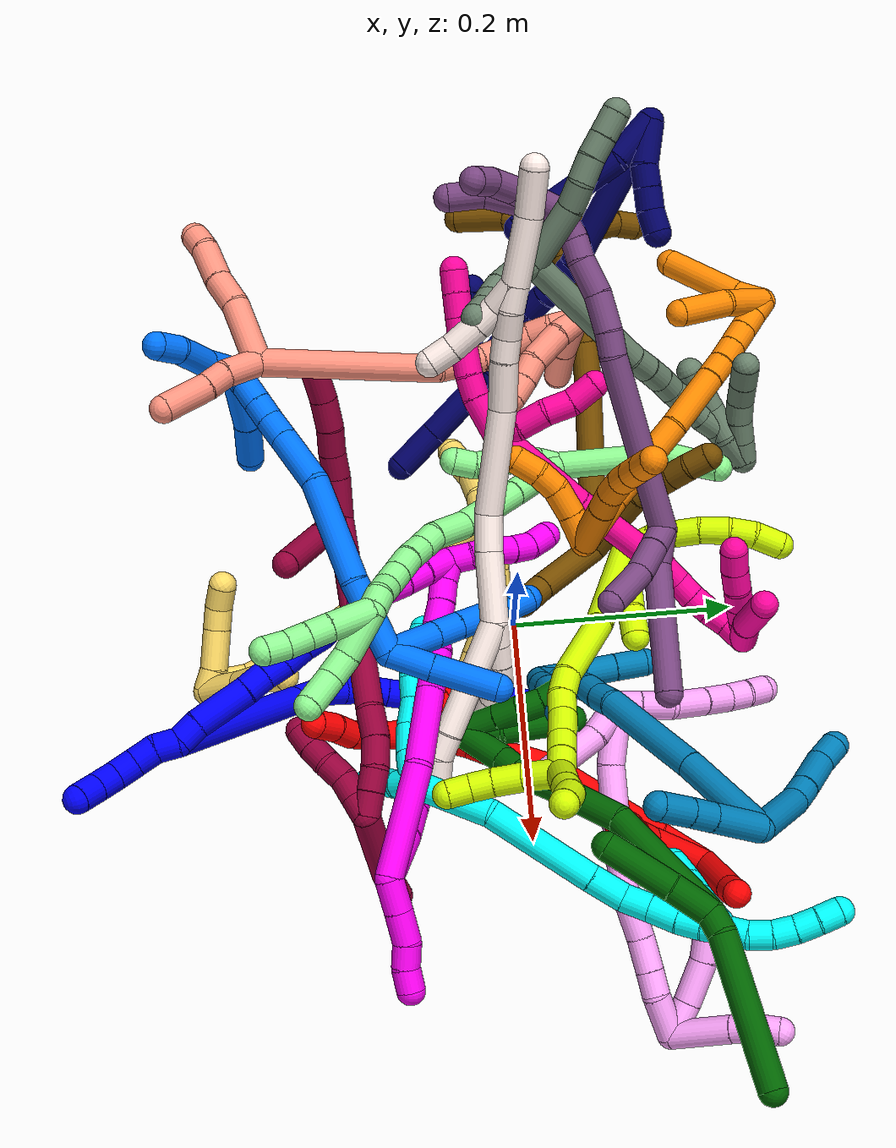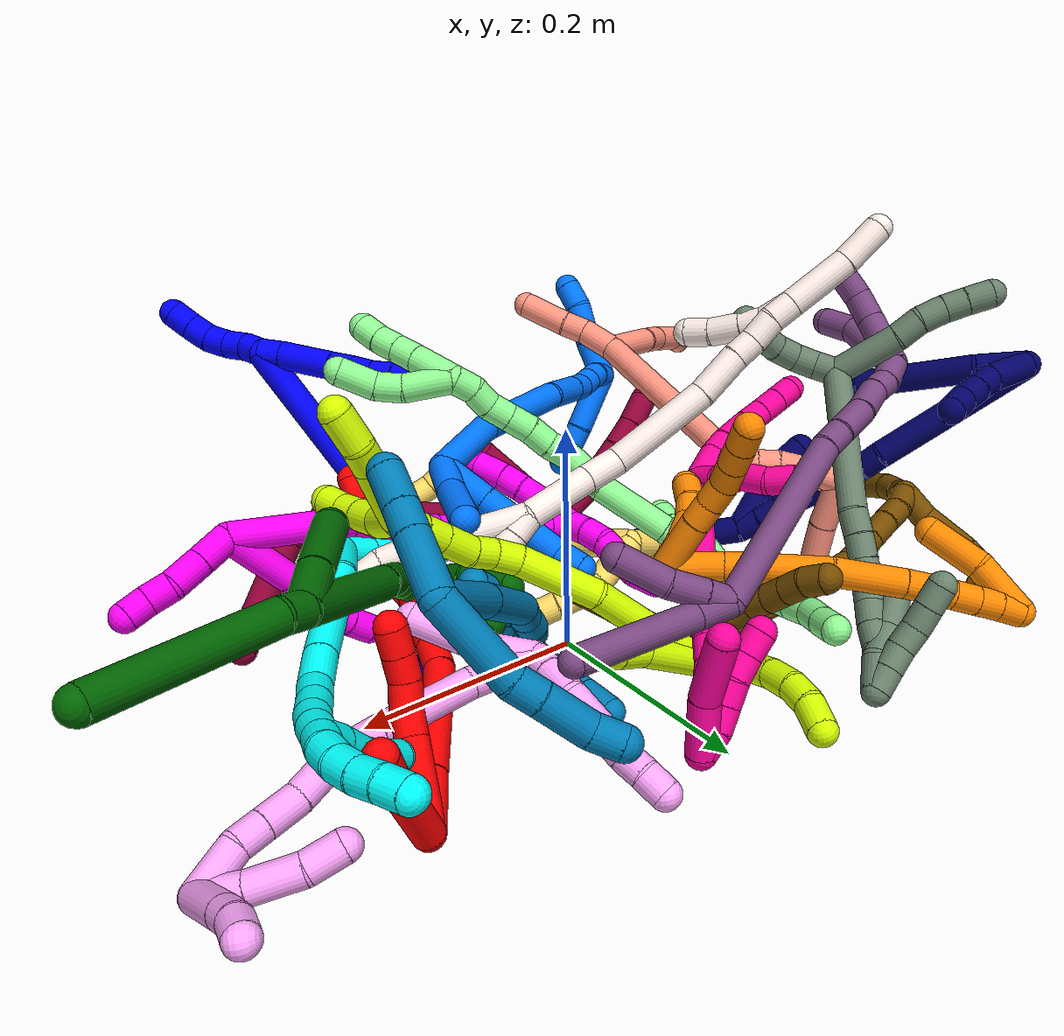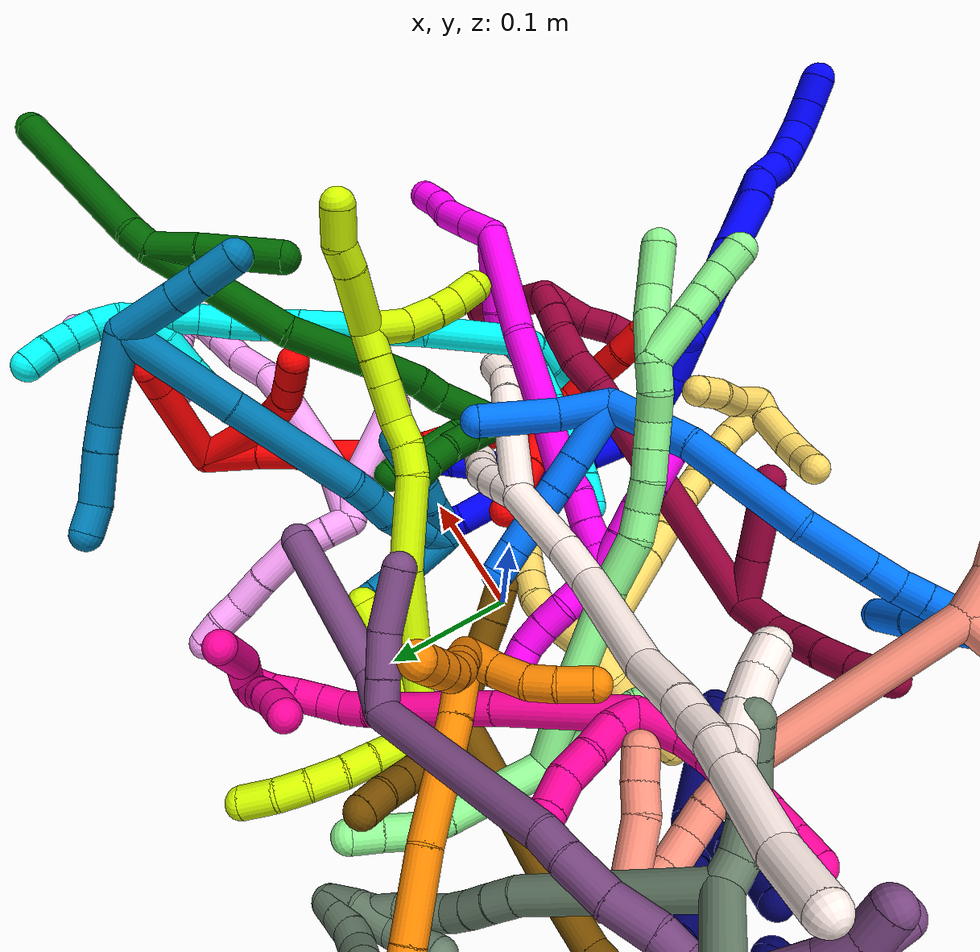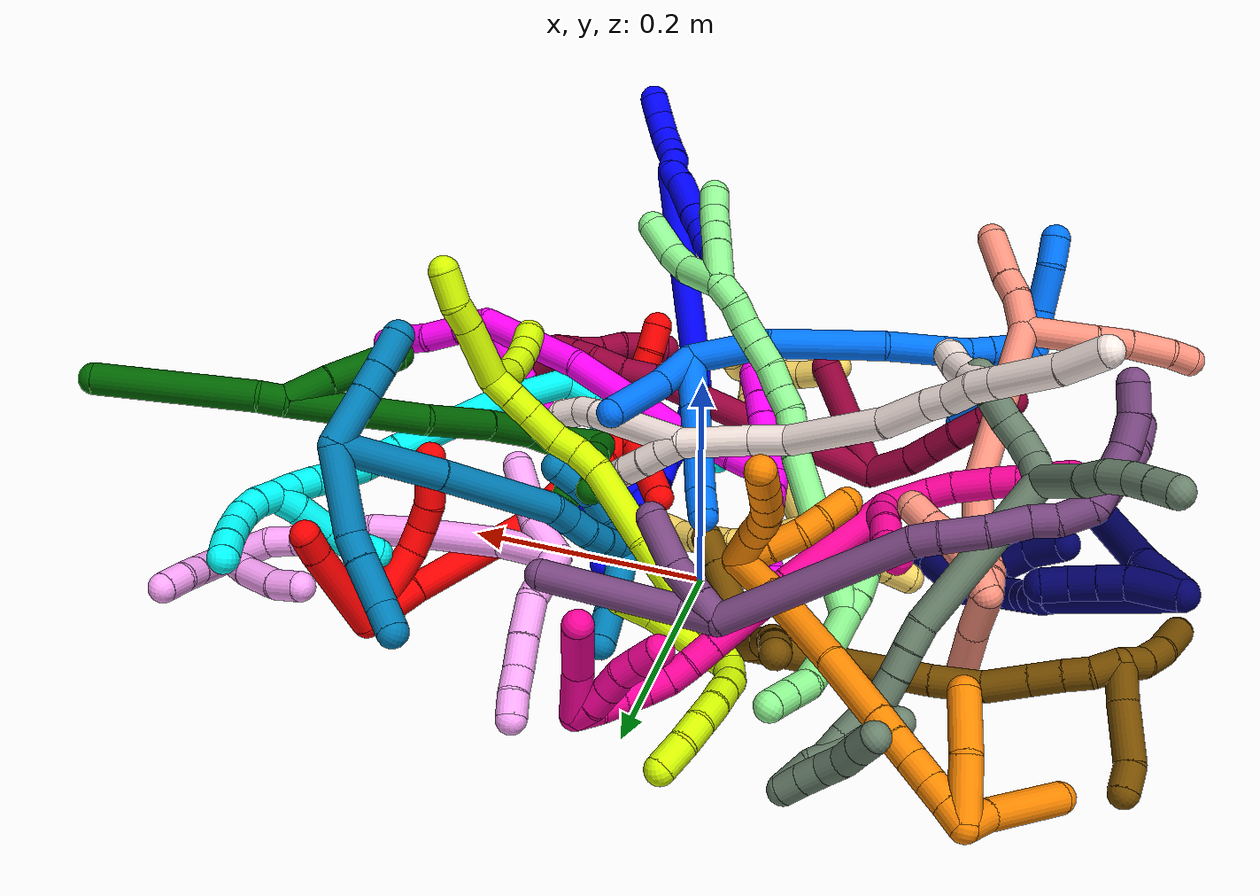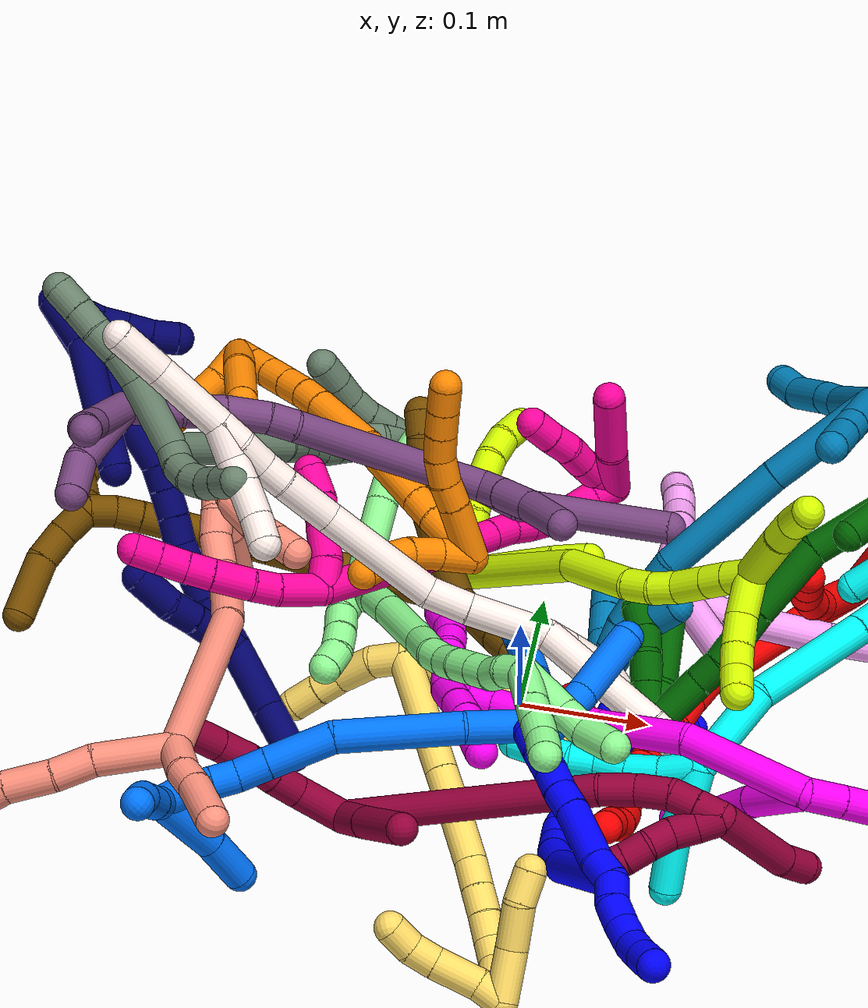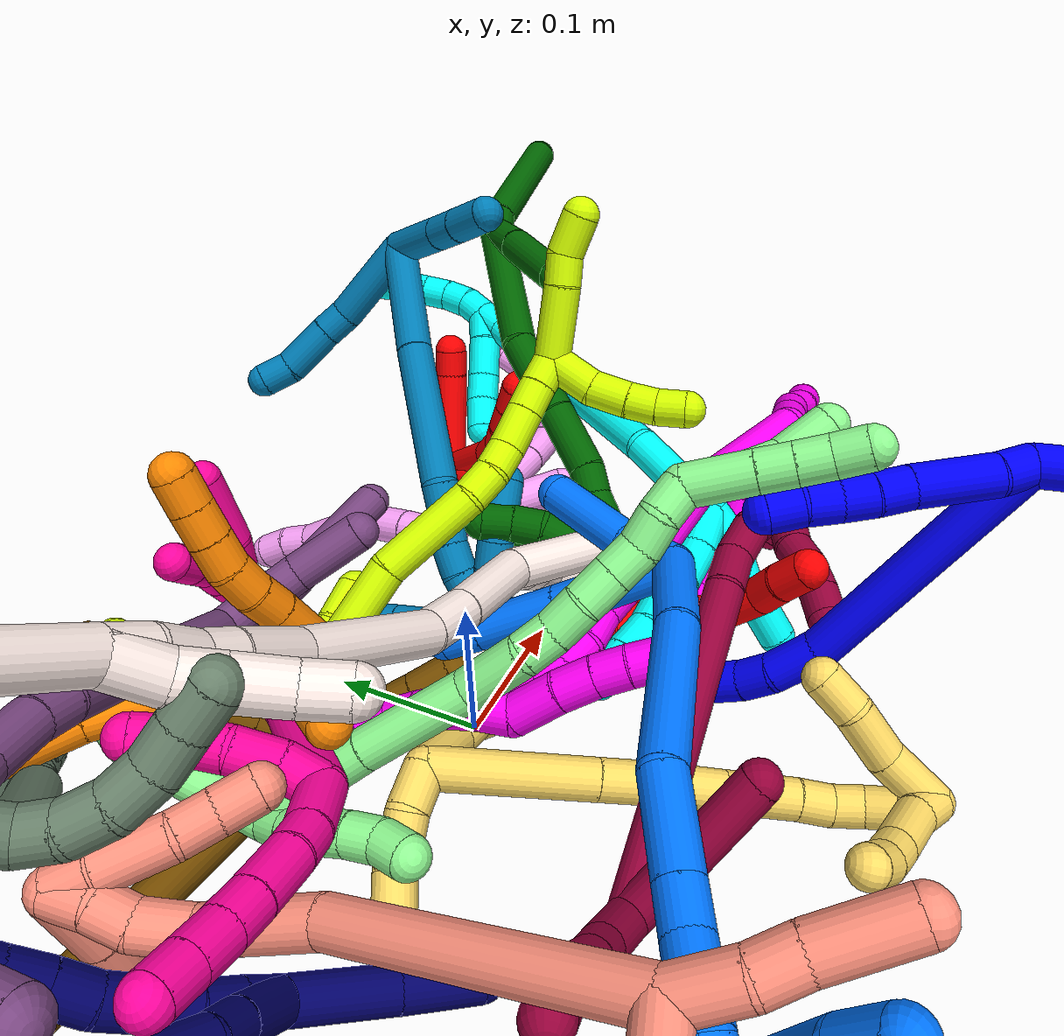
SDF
<sdf version="1.7">
 <world name="default">
  <plugin name="TubeGeneratorPlugin" filename="libtube_generator_plugin.so"/>
  <model name="photoneo_s_sensor">
   <static>1</static>
   <pose>0 0 2 1.57079 1.57079 3.14159</pose>
   <link name="link">
    <inertial><mass>0.1</mass></inertial>
    <sensor name="sensor" type="depth">
     <update_rate>30</update_rate>
     <camera>
      <horizontal_fov>1.22</horizontal_fov>
      <image><width>1920</width><height>1200</height><format>B8G8R8</format></image>
      <clip><near>0.1</near><far>4</far></clip>
      <depth_camera><output>points</output></depth_camera>
     </camera>
     <plugin name="camera_plugin" filename="libgazebo_ros_depth_camera.so">
      <baseline>0.2</baseline>
      <alwaysOn>1</alwaysOn>
      <updateRate>0.0</updateRate>
      <cameraName>camera_ir</cameraName>
      <imageTopicName>/camera/color/image_raw</imageTopicName>
      <cameraInfoTopicName>/camera/color/camera_info</cameraInfoTopicName>
      <depthImageTopicName>/camera/depth/image_raw</depthImageTopicName>
      <depthImageCameraInfoTopicName>/camera/depth/camera_info</depthImageCameraInfoTopicName>
      <pointCloudTopicName>/camera/depth/points</pointCloudTopicName>
      <frameName>fr_optical</frameName>
      <pointCloudCutoff>0.1</pointCloudCutoff>
      <pointCloudCutoffMax>2.0</pointCloudCutoffMax>
      <distortionK1>0</distortionK1>
      <distortionK2>0</distortionK2>
      <distortionK3>0</distortionK3>
      <distortionT1>0</distortionT1>
      <distortionT2>0</distortionT2>
      <CxPrime>0</CxPrime>
      <Cx>0</Cx>
      <Cy>0</Cy>
      <focalLength>0</focalLength>
      <hackBaseline>0</hackBaseline>
     </plugin>
    </sensor>
   </link>
  </model>
  <gravity>0 0 -9.8</gravity>
  <magnetic_field>6e-06 2.3e-05 -4.2e-05</magnetic_field>
  <atmosphere type="adiabatic"/>
  <physics name="default_physics" default="0" type="ode">
   <max_step_size>0.003</max_step_size>
   <real_time_factor>1</real_time_factor>
   <real_time_update_rate>1000</real_time_update_rate>
   <max_contacts>10000</max_contacts>
   <ode>
    <solver>
     <type>quick</type>
     <iters>100</iters>
     <sor>1.3</sor>
     <use_dynamic_moi_rescaling>0</use_dynamic_moi_rescaling>
    </solver>
    <constraints>
     <contact_max_correcting_vel>0</contact_max_correcting_vel>
     <contact_surface_layer>0.001</contact_surface_layer>
     <cfm>0</cfm>
     <erp>0.2</erp>
    </constraints>
   </ode>
  </physics>
  <scene><ambient>0.4 0.4 0.4 1</ambient><background>0.7 0.7 0.7 1</background><shadows>0</shadows></scene>
  <audio><device>default</device></audio>
  <spherical_coordinates>
   <surface_model>EARTH_WGS84</surface_model>
   <latitude_deg>0</latitude_deg>
   <longitude_deg>0</longitude_deg>
   <elevation>0</elevation>
   <heading_deg>0</heading_deg>
  </spherical_coordinates>
  <model name="bin">
   <static>1</static>
   <link name="bottom">
    <collision name="collision-bottom">
     <pose>0 0 -0.01 0 -0 0</pose>
     <geometry><box><size>0.8 0.6 0.02</size></box></geometry>
     <surface>
      <friction><ode><mu>100</mu><mu2>100</mu2></ode></friction>
      <contact><collide_bitmask>65535</collide_bitmask></contact>
     </surface>
    </collision>
   </link>
   <link name="west_wall">
    <collision name="collision-west_wall">
     <pose>-0.41 0 0.1 0 -0 0</pose>
     <geometry><box><size>0.02 0.6 0.2</size></box></geometry>
     <surface>
      <friction><ode><mu>100</mu><mu2>100</mu2></ode></friction>
      <contact><collide_bitmask>65535</collide_bitmask></contact>
     </surface>
    </collision>
   </link>
   <link name="east_wall">
    <collision name="collision-east_wall">
     <pose>0.41 0 0.1 0 -0 0</pose>
     <geometry><box><size>0.02 0.6 0.2</size></box></geometry>
     <surface>
      <friction><ode><mu>100</mu><mu2>100</mu2></ode></friction>
      <contact><collide_bitmask>65535</collide_bitmask></contact>
     </surface>
    </collision>
   </link>
   <link name="south_wall">
    <collision name="collision-south_wall">
     <pose>0 -0.31 0.1 0 -0 0</pose>
     <geometry><box><size>0.8 0.02 0.2</size></box></geometry>
     <surface>
      <friction><ode><mu>100</mu><mu2>100</mu2></ode></friction>
      <contact><collide_bitmask>65535</collide_bitmask></contact>
     </surface>
    </collision>
   </link>
   <link name="north_wall">
    <collision name="collision-north_wall">
     <pose>0 0.31 0.1 0 -0 0</pose>
     <geometry><box><size>0.8 0.02 0.2</size></box></geometry>
     <surface>
      <friction><ode><mu>100</mu><mu2>100</mu2></ode></friction>
      <contact><collide_bitmask>65535</collide_bitmask></contact>
     </surface>
    </collision>
   </link>
  </model>
  <model name="1">
   <static>0</static>
   <link name="1">
    <collision name="collision-cylinder-e_1_2_8">
     <pose>-0.000387 -0.004321 -0.009331 2.70786 -0.037593 -0.170226</pose>
     <geometry><cylinder><radius>0.0125</radius><length>0.02058</length></cylinder></geometry>
     <surface>
      <friction><ode><mu>1.16</mu><mu2>1.16</mu2><slip1>0</slip1><slip2>0</slip2></ode></friction>
      <contact><ode><kp>1e+06</kp><kd>1</kd><max_vel>0</max_vel><min_depth>0.001</min_depth></ode></contact>
     </surface>
    </collision>
    <visual name="visual-cylinder-e_1_2_8">
     <pose>-0.000387 -0.004321 -0.009331 2.70786 -0.037593 -0.170226</pose>
     <geometry><cylinder><radius>0.0125</radius><length>0.02058</length></cylinder></geometry>
     <material><ambient>0 0 1 1</ambient></material>
    </visual>
    <collision name="collision-cylinder-e_2_8_9">
     <pose>-0.003554 -0.014862 -0.042271 2.88403 -0.113416 -0.826299</pose>
     <geometry><cylinder><radius>0.0125</radius><length>0.049145</length></cylinder></geometry>
     <surface>
      <friction><ode><mu>1.16</mu><mu2>1.16</mu2><slip1>0</slip1><slip2>0</slip2></ode></friction>
      <contact><ode><kp>1e+06</kp><kd>1</kd><max_vel>0</max_vel><min_depth>0.001</min_depth></ode></contact>
     </surface>
    </collision>
    <visual name="visual-cylinder-e_2_8_9">
     <pose>-0.003554 -0.014862 -0.042271 2.88403 -0.113416 -0.826299</pose>
     <geometry><cylinder><radius>0.0125</radius><length>0.049145</length></cylinder></geometry>
     <material><ambient>0 0 1 1</ambient></material>
    </visual>
    <collision name="collision-cylinder-e_3_9_10">
     <pose>-0.006924 -0.024375 -0.075313 2.80562 -0.058863 -0.343774</pose>
     <geometry><cylinder><radius>0.0125</radius><length>0.020018</length></cylinder></geometry>
     <surface>
      <friction><ode><mu>1.16</mu><mu2>1.16</mu2><slip1>0</slip1><slip2>0</slip2></ode></friction>
      <contact><ode><kp>1e+06</kp><kd>1</kd><max_vel>0</max_vel><min_depth>0.001</min_depth></ode></contact>
     </surface>
    </collision>
    <visual name="visual-cylinder-e_3_9_10">
     <pose>-0.006924 -0.024375 -0.075313 2.80562 -0.058863 -0.343774</pose>
     <geometry><cylinder><radius>0.0125</radius><length>0.020018</length></cylinder></geometry>
     <material><ambient>0 0 1 1</ambient></material>
    </visual>
    <collision name="collision-cylinder-e_4_10_11">
     <pose>-0.008481 -0.029878 -0.094454 2.9179 -0.09689 -0.814994</pose>
     <geometry><cylinder><radius>0.0125</radius><length>0.020006</length></cylinder></geometry>
     <surface>
      <friction><ode><mu>1.16</mu><mu2>1.16</mu2><slip1>0</slip1><slip2>0</slip2></ode></friction>
      <contact><ode><kp>1e+06</kp><kd>1</kd><max_vel>0</max_vel><min_depth>0.001</min_depth></ode></contact>
     </surface>
    </collision>
    <visual name="visual-cylinder-e_4_10_11">
     <pose>-0.008481 -0.029878 -0.094454 2.9179 -0.09689 -0.814994</pose>
     <geometry><cylinder><radius>0.0125</radius><length>0.020006</length></cylinder></geometry>
     <material><ambient>0 0 1 1</ambient></material>
    </visual>
    <collision name="collision-cylinder-e_5_11_12">
     <pose>-0.011219 -0.035668 -0.113465 2.77414 -0.175794 -0.885659</pose>
     <geometry><cylinder><radius>0.0125</radius><length>0.02025</length></cylinder></geometry>
     <surface>
      <friction><ode><mu>1.16</mu><mu2>1.16</mu2><slip1>0</slip1><slip2>0</slip2></ode></friction>
      <contact><ode><kp>1e+06</kp><kd>1</kd><max_vel>0</max_vel><min_depth>0.001</min_depth></ode></contact>
     </surface>
    </collision>
    <visual name="visual-cylinder-e_5_11_12">
     <pose>-0.011219 -0.035668 -0.113465 2.77414 -0.175794 -0.885659</pose>
     <geometry><cylinder><radius>0.0125</radius><length>0.02025</length></cylinder></geometry>
     <material><ambient>0 0 1 1</ambient></material>
    </visual>
    <collision name="collision-cylinder-e_6_12_6">
     <pose>-0.01331 -0.041319 -0.132547 2.93293 -0.031981 -0.303097</pose>
     <geometry><cylinder><radius>0.0125</radius><length>0.020001</length></cylinder></geometry>
     <surface>
      <friction><ode><mu>1.16</mu><mu2>1.16</mu2><slip1>0</slip1><slip2>0</slip2></ode></friction>
      <contact><ode><kp>1e+06</kp><kd>1</kd><max_vel>0</max_vel><min_depth>0.001</min_depth></ode></contact>
     </surface>
    </collision>
    <visual name="visual-cylinder-e_6_12_6">
     <pose>-0.01331 -0.041319 -0.132547 2.93293 -0.031981 -0.303097</pose>
     <geometry><cylinder><radius>0.0125</radius><length>0.020001</length></cylinder></geometry>
     <material><ambient>0 0 1 1</ambient></material>
    </visual>
    <collision name="collision-cylinder-e_1_2_13">
     <pose>0.0027 -0.000665 0.009606 0.069071 0.273388 0.009505</pose>
     <geometry><cylinder><radius>0.0125</radius><length>0.02</length></cylinder></geometry>
     <surface>
      <friction><ode><mu>1.16</mu><mu2>1.16</mu2><slip1>0</slip1><slip2>0</slip2></ode></friction>
      <contact><ode><kp>1e+06</kp><kd>1</kd><max_vel>0</max_vel><min_depth>0.001</min_depth></ode></contact>
     </surface>
    </collision>
    <visual name="visual-cylinder-e_1_2_13">
     <pose>0.0027 -0.000665 0.009606 0.069071 0.273388 0.009505</pose>
     <geometry><cylinder><radius>0.0125</radius><length>0.02</length></cylinder></geometry>
     <material><ambient>0 0 1 1</ambient></material>
    </visual>
    <collision name="collision-cylinder-e_2_13_14">
     <pose>0.007314 0.001256 0.02868 -0.26656 0.192565 -0.025897</pose>
     <geometry><cylinder><radius>0.0125</radius><length>0.02</length></cylinder></geometry>
     <surface>
      <friction><ode><mu>1.16</mu><mu2>1.16</mu2><slip1>0</slip1><slip2>0</slip2></ode></friction>
      <contact><ode><kp>1e+06</kp><kd>1</kd><max_vel>0</max_vel><min_depth>0.001</min_depth></ode></contact>
     </surface>
    </collision>
    <visual name="visual-cylinder-e_2_13_14">
     <pose>0.007314 0.001256 0.02868 -0.26656 0.192565 -0.025897</pose>
     <geometry><cylinder><radius>0.0125</radius><length>0.02</length></cylinder></geometry>
     <material><ambient>0 0 1 1</ambient></material>
    </visual>
    <collision name="collision-cylinder-e_3_14_15">
     <pose>0.009433 0.006138 0.047879 -0.231707 0.02059 -0.002396</pose>
     <geometry><cylinder><radius>0.0125</radius><length>0.02</length></cylinder></geometry>
     <surface>
      <friction><ode><mu>1.16</mu><mu2>1.16</mu2><slip1>0</slip1><slip2>0</slip2></ode></friction>
      <contact><ode><kp>1e+06</kp><kd>1</kd><max_vel>0</max_vel><min_depth>0.001</min_depth></ode></contact>
     </surface>
    </collision>
    <visual name="visual-cylinder-e_3_14_15">
     <pose>0.009433 0.006138 0.047879 -0.231707 0.02059 -0.002396</pose>
     <geometry><cylinder><radius>0.0125</radius><length>0.02</length></cylinder></geometry>
     <material><ambient>0 0 1 1</ambient></material>
    </visual>
    <collision name="collision-cylinder-e_4_15_16">
     <pose>0.006567 0.009843 0.067021 -0.148635 -0.312245 0.023438</pose>
     <geometry><cylinder><radius>0.0125</radius><length>0.02</length></cylinder></geometry>
     <surface>
      <friction><ode><mu>1.16</mu><mu2>1.16</mu2><slip1>0</slip1><slip2>0</slip2></ode></friction>
      <contact><ode><kp>1e+06</kp><kd>1</kd><max_vel>0</max_vel><min_depth>0.001</min_depth></ode></contact>
     </surface>
    </collision>
    <visual name="visual-cylinder-e_4_15_16">
     <pose>0.006567 0.009843 0.067021 -0.148635 -0.312245 0.023438</pose>
     <geometry><cylinder><radius>0.0125</radius><length>0.02</length></cylinder></geometry>
     <material><ambient>0 0 1 1</ambient></material>
    </visual>
    <collision name="collision-cylinder-e_5_16_5">
     <pose>-0.000364 0.012395 0.085587 -0.124194 -0.39627 0.024965</pose>
     <geometry><cylinder><radius>0.0125</radius><length>0.02</length></cylinder></geometry>
     <surface>
      <friction><ode><mu>1.16</mu><mu2>1.16</mu2><slip1>0</slip1><slip2>0</slip2></ode></friction>
      <contact><ode><kp>1e+06</kp><kd>1</kd><max_vel>0</max_vel><min_depth>0.001</min_depth></ode></contact>
     </surface>
    </collision>
    <visual name="visual-cylinder-e_5_16_5">
     <pose>-0.000364 0.012395 0.085587 -0.124194 -0.39627 0.024965</pose>
     <geometry><cylinder><radius>0.0125</radius><length>0.02</length></cylinder></geometry>
     <material><ambient>0 0 1 1</ambient></material>
    </visual>
    <collision name="collision-cylinder-e_1_2_17">
     <pose>0.047799 0.005786 -0.066078 -3.05425 0.624426 -2.87246</pose>
     <geometry><cylinder><radius>0.0125</radius><length>0.163517</length></cylinder></geometry>
     <surface>
      <friction><ode><mu>1.16</mu><mu2>1.16</mu2><slip1>0</slip1><slip2>0</slip2></ode></friction>
      <contact><ode><kp>1e+06</kp><kd>1</kd><max_vel>0</max_vel><min_depth>0.001</min_depth></ode></contact>
     </surface>
    </collision>
    <visual name="visual-cylinder-e_1_2_17">
     <pose>0.047799 0.005786 -0.066078 -3.05425 0.624426 -2.87246</pose>
     <geometry><cylinder><radius>0.0125</radius><length>0.163517</length></cylinder></geometry>
     <material><ambient>0 0 1 1</ambient></material>
    </visual>
    <collision name="collision-cylinder-e_2_17_18">
     <pose>0.101491 0.012711 -0.146871 -3.06434 0.379887 -2.74489</pose>
     <geometry><cylinder><radius>0.0125</radius><length>0.031786</length></cylinder></geometry>
     <surface>
      <friction><ode><mu>1.16</mu><mu2>1.16</mu2><slip1>0</slip1><slip2>0</slip2></ode></friction>
      <contact><ode><kp>1e+06</kp><kd>1</kd><max_vel>0</max_vel><min_depth>0.001</min_depth></ode></contact>
     </surface>
    </collision>
    <visual name="visual-cylinder-e_2_17_18">
     <pose>0.101491 0.012711 -0.146871 -3.06434 0.379887 -2.74489</pose>
     <geometry><cylinder><radius>0.0125</radius><length>0.031786</length></cylinder></geometry>
     <material><ambient>0 0 1 1</ambient></material>
    </visual>
    <collision name="collision-cylinder-e_3_18_19">
     <pose>0.110189 0.017013 -0.171336 -2.82784 0.267187 -1.4086</pose>
     <geometry><cylinder><radius>0.0125</radius><length>0.021252</length></cylinder></geometry>
     <surface>
      <friction><ode><mu>1.16</mu><mu2>1.16</mu2><slip1>0</slip1><slip2>0</slip2></ode></friction>
      <contact><ode><kp>1e+06</kp><kd>1</kd><max_vel>0</max_vel><min_depth>0.001</min_depth></ode></contact>
     </surface>
    </collision>
    <visual name="visual-cylinder-e_3_18_19">
     <pose>0.110189 0.017013 -0.171336 -2.82784 0.267187 -1.4086</pose>
     <geometry><cylinder><radius>0.0125</radius><length>0.021252</length></cylinder></geometry>
     <material><ambient>0 0 1 1</ambient></material>
    </visual>
    <collision name="collision-cylinder-e_4_19_20">
     <pose>0.113787 0.022985 -0.190777 -2.85957 0.078376 -0.538974</pose>
     <geometry><cylinder><radius>0.0125</radius><length>0.020243</length></cylinder></geometry>
     <surface>
      <friction><ode><mu>1.16</mu><mu2>1.16</mu2><slip1>0</slip1><slip2>0</slip2></ode></friction>
      <contact><ode><kp>1e+06</kp><kd>1</kd><max_vel>0</max_vel><min_depth>0.001</min_depth></ode></contact>
     </surface>
    </collision>
    <visual name="visual-cylinder-e_4_19_20">
     <pose>0.113787 0.022985 -0.190777 -2.85957 0.078376 -0.538974</pose>
     <geometry><cylinder><radius>0.0125</radius><length>0.020243</length></cylinder></geometry>
     <material><ambient>0 0 1 1</ambient></material>
    </visual>
    <collision name="collision-cylinder-e_5_20_21">
     <pose>0.112733 0.030885 -0.209786 -2.64145 -0.172195 0.651741</pose>
     <geometry><cylinder><radius>0.0125</radius><length>0.021555</length></cylinder></geometry>
     <surface>
      <friction><ode><mu>1.16</mu><mu2>1.16</mu2><slip1>0</slip1><slip2>0</slip2></ode></friction>
      <contact><ode><kp>1e+06</kp><kd>1</kd><max_vel>0</max_vel><min_depth>0.001</min_depth></ode></contact>
     </surface>
    </collision>
    <visual name="visual-cylinder-e_5_20_21">
     <pose>0.112733 0.030885 -0.209786 -2.64145 -0.172195 0.651741</pose>
     <geometry><cylinder><radius>0.0125</radius><length>0.021555</length></cylinder></geometry>
     <material><ambient>0 0 1 1</ambient></material>
    </visual>
    <collision name="collision-cylinder-e_6_21_22">
     <pose>0.10926 0.040749 -0.228179 -2.65746 -0.157312 0.617992</pose>
     <geometry><cylinder><radius>0.0125</radius><length>0.020765</length></cylinder></geometry>
     <surface>
      <friction><ode><mu>1.16</mu><mu2>1.16</mu2><slip1>0</slip1><slip2>0</slip2></ode></friction>
      <contact><ode><kp>1e+06</kp><kd>1</kd><max_vel>0</max_vel><min_depth>0.001</min_depth></ode></contact>
     </surface>
    </collision>
    <visual name="visual-cylinder-e_6_21_22">
     <pose>0.10926 0.040749 -0.228179 -2.65746 -0.157312 0.617992</pose>
     <geometry><cylinder><radius>0.0125</radius><length>0.020765</length></cylinder></geometry>
     <material><ambient>0 0 1 1</ambient></material>
    </visual>
    <collision name="collision-cylinder-e_7_22_1">
     <pose>0.107223 0.048657 -0.247206 -2.83642 -0.039333 0.254426</pose>
     <geometry><cylinder><radius>0.0125</radius><length>0.020882</length></cylinder></geometry>
     <surface>
      <friction><ode><mu>1.16</mu><mu2>1.16</mu2><slip1>0</slip1><slip2>0</slip2></ode></friction>
      <contact><ode><kp>1e+06</kp><kd>1</kd><max_vel>0</max_vel><min_depth>0.001</min_depth></ode></contact>
     </surface>
    </collision>
    <visual name="visual-cylinder-e_7_22_1">
     <pose>0.107223 0.048657 -0.247206 -2.83642 -0.039333 0.254426</pose>
     <geometry><cylinder><radius>0.0125</radius><length>0.020882</length></cylinder></geometry>
     <material><ambient>0 0 1 1</ambient></material>
    </visual>
    <collision name="collision-cylinder-e_1_1_23">
     <pose>0.098907 0.068068 -0.264903 -2.01497 -0.413317 0.641013</pose>
     <geometry><cylinder><radius>0.0125</radius><length>0.039366</length></cylinder></geometry>
     <surface>
      <friction><ode><mu>1.16</mu><mu2>1.16</mu2><slip1>0</slip1><slip2>0</slip2></ode></friction>
      <contact><ode><kp>1e+06</kp><kd>1</kd><max_vel>0</max_vel><min_depth>0.001</min_depth></ode></contact>
     </surface>
    </collision>
    <visual name="visual-cylinder-e_1_1_23">
     <pose>0.098907 0.068068 -0.264903 -2.01497 -0.413317 0.641013</pose>
     <geometry><cylinder><radius>0.0125</radius><length>0.039366</length></cylinder></geometry>
     <material><ambient>0 0 1 1</ambient></material>
    </visual>
    <collision name="collision-cylinder-e_2_23_24">
     <pose>0.085524 0.100325 -0.28204 -2.10212 -0.287287 0.495172</pose>
     <geometry><cylinder><radius>0.0125</radius><length>0.038656</length></cylinder></geometry>
     <surface>
      <friction><ode><mu>1.16</mu><mu2>1.16</mu2><slip1>0</slip1><slip2>0</slip2></ode></friction>
      <contact><ode><kp>1e+06</kp><kd>1</kd><max_vel>0</max_vel><min_depth>0.001</min_depth></ode></contact>
     </surface>
    </collision>
    <visual name="visual-cylinder-e_2_23_24">
     <pose>0.085524 0.100325 -0.28204 -2.10212 -0.287287 0.495172</pose>
     <geometry><cylinder><radius>0.0125</radius><length>0.038656</length></cylinder></geometry>
     <material><ambient>0 0 1 1</ambient></material>
    </visual>
    <collision name="collision-cylinder-e_3_24_4">
     <pose>0.079054 0.126397 -0.295666 -1.96809 -0.090568 0.136104</pose>
     <geometry><cylinder><radius>0.0125</radius><length>0.021978</length></cylinder></geometry>
     <surface>
      <friction><ode><mu>1.16</mu><mu2>1.16</mu2><slip1>0</slip1><slip2>0</slip2></ode></friction>
      <contact><ode><kp>1e+06</kp><kd>1</kd><max_vel>0</max_vel><min_depth>0.001</min_depth></ode></contact>
     </surface>
    </collision>
    <visual name="visual-cylinder-e_3_24_4">
     <pose>0.079054 0.126397 -0.295666 -1.96809 -0.090568 0.136104</pose>
     <geometry><cylinder><radius>0.0125</radius><length>0.021978</length></cylinder></geometry>
     <material><ambient>0 0 1 1</ambient></material>
    </visual>
    <collision name="collision-cylinder-e_1_1_25">
     <pose>0.102034 0.060608 -0.274965 -2.68188 -0.236006 0.93792</pose>
     <geometry><cylinder><radius>0.0125</radius><length>0.040875</length></cylinder></geometry>
     <surface>
      <friction><ode><mu>1.16</mu><mu2>1.16</mu2><slip1>0</slip1><slip2>0</slip2></ode></friction>
      <contact><ode><kp>1e+06</kp><kd>1</kd><max_vel>0</max_vel><min_depth>0.001</min_depth></ode></contact>
     </surface>
    </collision>
    <visual name="visual-cylinder-e_1_1_25">
     <pose>0.102034 0.060608 -0.274965 -2.68188 -0.236006 0.93792</pose>
     <geometry><cylinder><radius>0.0125</radius><length>0.040875</length></cylinder></geometry>
     <material><ambient>0 0 1 1</ambient></material>
    </visual>
    <collision name="collision-cylinder-e_2_25_26">
     <pose>0.094732 0.075946 -0.309188 -2.76344 -0.141846 0.710947</pose>
     <geometry><cylinder><radius>0.0125</radius><length>0.035685</length></cylinder></geometry>
     <surface>
      <friction><ode><mu>1.16</mu><mu2>1.16</mu2><slip1>0</slip1><slip2>0</slip2></ode></friction>
      <contact><ode><kp>1e+06</kp><kd>1</kd><max_vel>0</max_vel><min_depth>0.001</min_depth></ode></contact>
     </surface>
    </collision>
    <visual name="visual-cylinder-e_2_25_26">
     <pose>0.094732 0.075946 -0.309188 -2.76344 -0.141846 0.710947</pose>
     <geometry><cylinder><radius>0.0125</radius><length>0.035685</length></cylinder></geometry>
     <material><ambient>0 0 1 1</ambient></material>
    </visual>
    <collision name="collision-cylinder-e_3_26_3">
     <pose>0.090132 0.088247 -0.335585 -2.61674 -0.178245 0.642288</pose>
     <geometry><cylinder><radius>0.0125</radius><length>0.02344</length></cylinder></geometry>
     <surface>
      <friction><ode><mu>1.16</mu><mu2>1.16</mu2><slip1>0</slip1><slip2>0</slip2></ode></friction>
      <contact><ode><kp>1e+06</kp><kd>1</kd><max_vel>0</max_vel><min_depth>0.001</min_depth></ode></contact>
     </surface>
    </collision>
    <visual name="visual-cylinder-e_3_26_3">
     <pose>0.090132 0.088247 -0.335585 -2.61674 -0.178245 0.642288</pose>
     <geometry><cylinder><radius>0.0125</radius><length>0.02344</length></cylinder></geometry>
     <material><ambient>0 0 1 1</ambient></material>
    </visual>
    <collision name="collision-sphere-3">
     <pose>0.088054 0.094027 -0.345567 0 -0 0</pose>
     <geometry><sphere><radius>0.0125</radius></sphere></geometry>
     <surface>
      <friction><ode><mu>1.16</mu><mu2>1.16</mu2><slip1>0</slip1><slip2>0</slip2></ode></friction>
      <contact><ode><kp>1e+06</kp><kd>1</kd><max_vel>0</max_vel><min_depth>0.001</min_depth></ode></contact>
     </surface>
    </collision>
    <visual name="visual-sphere-3">
     <pose>0.088054 0.094027 -0.345567 0 -0 0</pose>
     <geometry><sphere><radius>0.0125</radius></sphere></geometry>
     <material><ambient>0 0 1 1</ambient></material>
    </visual>
    <collision name="collision-sphere-26">
     <pose>0.09221 0.082467 -0.325603 0 -0 0</pose>
     <geometry><sphere><radius>0.0125</radius></sphere></geometry>
     <surface>
      <friction><ode><mu>1.16</mu><mu2>1.16</mu2><slip1>0</slip1><slip2>0</slip2></ode></friction>
      <contact><ode><kp>1e+06</kp><kd>1</kd><max_vel>0</max_vel><min_depth>0.001</min_depth></ode></contact>
     </surface>
    </collision>
    <visual name="visual-sphere-26">
     <pose>0.09221 0.082467 -0.325603 0 -0 0</pose>
     <geometry><sphere><radius>0.0125</radius></sphere></geometry>
     <material><ambient>0 0 1 1</ambient></material>
    </visual>
    <collision name="collision-sphere-25">
     <pose>0.097255 0.069424 -0.292773 0 -0 0</pose>
     <geometry><sphere><radius>0.0125</radius></sphere></geometry>
     <surface>
      <friction><ode><mu>1.16</mu><mu2>1.16</mu2><slip1>0</slip1><slip2>0</slip2></ode></friction>
      <contact><ode><kp>1e+06</kp><kd>1</kd><max_vel>0</max_vel><min_depth>0.001</min_depth></ode></contact>
     </surface>
    </collision>
    <visual name="visual-sphere-25">
     <pose>0.097255 0.069424 -0.292773 0 -0 0</pose>
     <geometry><sphere><radius>0.0125</radius></sphere></geometry>
     <material><ambient>0 0 1 1</ambient></material>
    </visual>
    <collision name="collision-sphere-4">
     <pose>0.07806 0.136488 -0.2999 0 -0 0</pose>
     <geometry><sphere><radius>0.0125</radius></sphere></geometry>
     <surface>
      <friction><ode><mu>1.16</mu><mu2>1.16</mu2><slip1>0</slip1><slip2>0</slip2></ode></friction>
      <contact><ode><kp>1e+06</kp><kd>1</kd><max_vel>0</max_vel><min_depth>0.001</min_depth></ode></contact>
     </surface>
    </collision>
    <visual name="visual-sphere-4">
     <pose>0.07806 0.136488 -0.2999 0 -0 0</pose>
     <geometry><sphere><radius>0.0125</radius></sphere></geometry>
     <material><ambient>0 0 1 1</ambient></material>
    </visual>
    <collision name="collision-sphere-24">
     <pose>0.080048 0.116306 -0.291432 0 -0 0</pose>
     <geometry><sphere><radius>0.0125</radius></sphere></geometry>
     <surface>
      <friction><ode><mu>1.16</mu><mu2>1.16</mu2><slip1>0</slip1><slip2>0</slip2></ode></friction>
      <contact><ode><kp>1e+06</kp><kd>1</kd><max_vel>0</max_vel><min_depth>0.001</min_depth></ode></contact>
     </surface>
    </collision>
    <visual name="visual-sphere-24">
     <pose>0.080048 0.116306 -0.291432 0 -0 0</pose>
     <geometry><sphere><radius>0.0125</radius></sphere></geometry>
     <material><ambient>0 0 1 1</ambient></material>
    </visual>
    <collision name="collision-sphere-23">
     <pose>0.091001 0.084345 -0.272648 0 -0 0</pose>
     <geometry><sphere><radius>0.0125</radius></sphere></geometry>
     <surface>
      <friction><ode><mu>1.16</mu><mu2>1.16</mu2><slip1>0</slip1><slip2>0</slip2></ode></friction>
      <contact><ode><kp>1e+06</kp><kd>1</kd><max_vel>0</max_vel><min_depth>0.001</min_depth></ode></contact>
     </surface>
    </collision>
    <visual name="visual-sphere-23">
     <pose>0.091001 0.084345 -0.272648 0 -0 0</pose>
     <geometry><sphere><radius>0.0125</radius></sphere></geometry>
     <material><ambient>0 0 1 1</ambient></material>
    </visual>
    <collision name="collision-sphere-1">
     <pose>0.106812 0.051791 -0.257157 0 -0 0</pose>
     <geometry><sphere><radius>0.0125</radius></sphere></geometry>
     <surface>
      <friction><ode><mu>1.16</mu><mu2>1.16</mu2><slip1>0</slip1><slip2>0</slip2></ode></friction>
      <contact><ode><kp>1e+06</kp><kd>1</kd><max_vel>0</max_vel><min_depth>0.001</min_depth></ode></contact>
     </surface>
    </collision>
    <visual name="visual-sphere-1">
     <pose>0.106812 0.051791 -0.257157 0 -0 0</pose>
     <geometry><sphere><radius>0.0125</radius></sphere></geometry>
     <material><ambient>0 0 1 1</ambient></material>
    </visual>
    <collision name="collision-sphere-22">
     <pose>0.107633 0.045522 -0.237255 0 -0 0</pose>
     <geometry><sphere><radius>0.0125</radius></sphere></geometry>
     <surface>
      <friction><ode><mu>1.16</mu><mu2>1.16</mu2><slip1>0</slip1><slip2>0</slip2></ode></friction>
      <contact><ode><kp>1e+06</kp><kd>1</kd><max_vel>0</max_vel><min_depth>0.001</min_depth></ode></contact>
     </surface>
    </collision>
    <visual name="visual-sphere-22">
     <pose>0.107633 0.045522 -0.237255 0 -0 0</pose>
     <geometry><sphere><radius>0.0125</radius></sphere></geometry>
     <material><ambient>0 0 1 1</ambient></material>
    </visual>
    <collision name="collision-sphere-21">
     <pose>0.110887 0.035977 -0.219104 0 -0 0</pose>
     <geometry><sphere><radius>0.0125</radius></sphere></geometry>
     <surface>
      <friction><ode><mu>1.16</mu><mu2>1.16</mu2><slip1>0</slip1><slip2>0</slip2></ode></friction>
      <contact><ode><kp>1e+06</kp><kd>1</kd><max_vel>0</max_vel><min_depth>0.001</min_depth></ode></contact>
     </surface>
    </collision>
    <visual name="visual-sphere-21">
     <pose>0.110887 0.035977 -0.219104 0 -0 0</pose>
     <geometry><sphere><radius>0.0125</radius></sphere></geometry>
     <material><ambient>0 0 1 1</ambient></material>
    </visual>
    <collision name="collision-sphere-12">
     <pose>-0.01299 -0.039249 -0.122769 0 -0 0</pose>
     <geometry><sphere><radius>0.0125</radius></sphere></geometry>
     <surface>
      <friction><ode><mu>1.16</mu><mu2>1.16</mu2><slip1>0</slip1><slip2>0</slip2></ode></friction>
      <contact><ode><kp>1e+06</kp><kd>1</kd><max_vel>0</max_vel><min_depth>0.001</min_depth></ode></contact>
     </surface>
    </collision>
    <visual name="visual-sphere-12">
     <pose>-0.01299 -0.039249 -0.122769 0 -0 0</pose>
     <geometry><sphere><radius>0.0125</radius></sphere></geometry>
     <material><ambient>0 0 1 1</ambient></material>
    </visual>
    <collision name="collision-sphere-11">
     <pose>-0.009448 -0.032086 -0.104162 0 -0 0</pose>
     <geometry><sphere><radius>0.0125</radius></sphere></geometry>
     <surface>
      <friction><ode><mu>1.16</mu><mu2>1.16</mu2><slip1>0</slip1><slip2>0</slip2></ode></friction>
      <contact><ode><kp>1e+06</kp><kd>1</kd><max_vel>0</max_vel><min_depth>0.001</min_depth></ode></contact>
     </surface>
    </collision>
    <visual name="visual-sphere-11">
     <pose>-0.009448 -0.032086 -0.104162 0 -0 0</pose>
     <geometry><sphere><radius>0.0125</radius></sphere></geometry>
     <material><ambient>0 0 1 1</ambient></material>
    </visual>
    <collision name="collision-sphere-10">
     <pose>-0.007513 -0.027669 -0.084746 0 -0 0</pose>
     <geometry><sphere><radius>0.0125</radius></sphere></geometry>
     <surface>
      <friction><ode><mu>1.16</mu><mu2>1.16</mu2><slip1>0</slip1><slip2>0</slip2></ode></friction>
      <contact><ode><kp>1e+06</kp><kd>1</kd><max_vel>0</max_vel><min_depth>0.001</min_depth></ode></contact>
     </surface>
    </collision>
    <visual name="visual-sphere-10">
     <pose>-0.007513 -0.027669 -0.084746 0 -0 0</pose>
     <geometry><sphere><radius>0.0125</radius></sphere></geometry>
     <material><ambient>0 0 1 1</ambient></material>
    </visual>
    <collision name="collision-sphere-9">
     <pose>-0.006335 -0.021081 -0.06588 0 -0 0</pose>
     <geometry><sphere><radius>0.0125</radius></sphere></geometry>
     <surface>
      <friction><ode><mu>1.16</mu><mu2>1.16</mu2><slip1>0</slip1><slip2>0</slip2></ode></friction>
      <contact><ode><kp>1e+06</kp><kd>1</kd><max_vel>0</max_vel><min_depth>0.001</min_depth></ode></contact>
     </surface>
    </collision>
    <visual name="visual-sphere-9">
     <pose>-0.006335 -0.021081 -0.06588 0 -0 0</pose>
     <geometry><sphere><radius>0.0125</radius></sphere></geometry>
     <material><ambient>0 0 1 1</ambient></material>
    </visual>
    <collision name="collision-sphere-2">
     <geometry><sphere><radius>0.0125</radius></sphere></geometry>
     <surface>
      <friction><ode><mu>1.16</mu><mu2>1.16</mu2><slip1>0</slip1><slip2>0</slip2></ode></friction>
      <contact><ode><kp>1e+06</kp><kd>1</kd><max_vel>0</max_vel><min_depth>0.001</min_depth></ode></contact>
     </surface>
    </collision>
    <visual name="visual-sphere-2">
     <geometry><sphere><radius>0.0125</radius></sphere></geometry>
     <material><ambient>0 0 1 1</ambient></material>
    </visual>
    <collision name="collision-sphere-19">
     <pose>0.112995 0.020176 -0.181085 0 -0 0</pose>
     <geometry><sphere><radius>0.0125</radius></sphere></geometry>
     <surface>
      <friction><ode><mu>1.16</mu><mu2>1.16</mu2><slip1>0</slip1><slip2>0</slip2></ode></friction>
      <contact><ode><kp>1e+06</kp><kd>1</kd><max_vel>0</max_vel><min_depth>0.001</min_depth></ode></contact>
     </surface>
    </collision>
    <visual name="visual-sphere-19">
     <pose>0.112995 0.020176 -0.181085 0 -0 0</pose>
     <geometry><sphere><radius>0.0125</radius></sphere></geometry>
     <material><ambient>0 0 1 1</ambient></material>
    </visual>
    <collision name="collision-sphere-8">
     <pose>-0.000773 -0.008643 -0.018661 0 -0 0</pose>
     <geometry><sphere><radius>0.0125</radius></sphere></geometry>
     <surface>
      <friction><ode><mu>1.16</mu><mu2>1.16</mu2><slip1>0</slip1><slip2>0</slip2></ode></friction>
      <contact><ode><kp>1e+06</kp><kd>1</kd><max_vel>0</max_vel><min_depth>0.001</min_depth></ode></contact>
     </surface>
    </collision>
    <visual name="visual-sphere-8">
     <pose>-0.000773 -0.008643 -0.018661 0 -0 0</pose>
     <geometry><sphere><radius>0.0125</radius></sphere></geometry>
     <material><ambient>0 0 1 1</ambient></material>
    </visual>
    <collision name="collision-sphere-6">
     <pose>-0.013629 -0.04339 -0.142326 0 -0 0</pose>
     <geometry><sphere><radius>0.0125</radius></sphere></geometry>
     <surface>
      <friction><ode><mu>1.16</mu><mu2>1.16</mu2><slip1>0</slip1><slip2>0</slip2></ode></friction>
      <contact><ode><kp>1e+06</kp><kd>1</kd><max_vel>0</max_vel><min_depth>0.001</min_depth></ode></contact>
     </surface>
    </collision>
    <visual name="visual-sphere-6">
     <pose>-0.013629 -0.04339 -0.142326 0 -0 0</pose>
     <geometry><sphere><radius>0.0125</radius></sphere></geometry>
     <material><ambient>0 0 1 1</ambient></material>
    </visual>
    <collision name="collision-sphere-13">
     <pose>0.0054 -0.001329 0.019211 0 -0 0</pose>
     <geometry><sphere><radius>0.0125</radius></sphere></geometry>
     <surface>
      <friction><ode><mu>1.16</mu><mu2>1.16</mu2><slip1>0</slip1><slip2>0</slip2></ode></friction>
      <contact><ode><kp>1e+06</kp><kd>1</kd><max_vel>0</max_vel><min_depth>0.001</min_depth></ode></contact>
     </surface>
    </collision>
    <visual name="visual-sphere-13">
     <pose>0.0054 -0.001329 0.019211 0 -0 0</pose>
     <geometry><sphere><radius>0.0125</radius></sphere></geometry>
     <material><ambient>0 0 1 1</ambient></material>
    </visual>
    <collision name="collision-sphere-14">
     <pose>0.009227 0.003842 0.038148 0 -0 0</pose>
     <geometry><sphere><radius>0.0125</radius></sphere></geometry>
     <surface>
      <friction><ode><mu>1.16</mu><mu2>1.16</mu2><slip1>0</slip1><slip2>0</slip2></ode></friction>
      <contact><ode><kp>1e+06</kp><kd>1</kd><max_vel>0</max_vel><min_depth>0.001</min_depth></ode></contact>
     </surface>
    </collision>
    <visual name="visual-sphere-14">
     <pose>0.009227 0.003842 0.038148 0 -0 0</pose>
     <geometry><sphere><radius>0.0125</radius></sphere></geometry>
     <material><ambient>0 0 1 1</ambient></material>
    </visual>
    <collision name="collision-sphere-15">
     <pose>0.009639 0.008434 0.05761 0 -0 0</pose>
     <geometry><sphere><radius>0.0125</radius></sphere></geometry>
     <surface>
      <friction><ode><mu>1.16</mu><mu2>1.16</mu2><slip1>0</slip1><slip2>0</slip2></ode></friction>
      <contact><ode><kp>1e+06</kp><kd>1</kd><max_vel>0</max_vel><min_depth>0.001</min_depth></ode></contact>
     </surface>
    </collision>
    <visual name="visual-sphere-15">
     <pose>0.009639 0.008434 0.05761 0 -0 0</pose>
     <geometry><sphere><radius>0.0125</radius></sphere></geometry>
     <material><ambient>0 0 1 1</ambient></material>
    </visual>
    <collision name="collision-sphere-16">
     <pose>0.003495 0.011252 0.076433 0 -0 0</pose>
     <geometry><sphere><radius>0.0125</radius></sphere></geometry>
     <surface>
      <friction><ode><mu>1.16</mu><mu2>1.16</mu2><slip1>0</slip1><slip2>0</slip2></ode></friction>
      <contact><ode><kp>1e+06</kp><kd>1</kd><max_vel>0</max_vel><min_depth>0.001</min_depth></ode></contact>
     </surface>
    </collision>
    <visual name="visual-sphere-16">
     <pose>0.003495 0.011252 0.076433 0 -0 0</pose>
     <geometry><sphere><radius>0.0125</radius></sphere></geometry>
     <material><ambient>0 0 1 1</ambient></material>
    </visual>
    <collision name="collision-sphere-5">
     <pose>-0.004224 0.013538 0.094741 0 -0 0</pose>
     <geometry><sphere><radius>0.0125</radius></sphere></geometry>
     <surface>
      <friction><ode><mu>1.16</mu><mu2>1.16</mu2><slip1>0</slip1><slip2>0</slip2></ode></friction>
      <contact><ode><kp>1e+06</kp><kd>1</kd><max_vel>0</max_vel><min_depth>0.001</min_depth></ode></contact>
     </surface>
    </collision>
    <visual name="visual-sphere-5">
     <pose>-0.004224 0.013538 0.094741 0 -0 0</pose>
     <geometry><sphere><radius>0.0125</radius></sphere></geometry>
     <material><ambient>0 0 1 1</ambient></material>
    </visual>
    <collision name="collision-sphere-17">
     <pose>0.095597 0.011572 -0.132155 0 -0 0</pose>
     <geometry><sphere><radius>0.0125</radius></sphere></geometry>
     <surface>
      <friction><ode><mu>1.16</mu><mu2>1.16</mu2><slip1>0</slip1><slip2>0</slip2></ode></friction>
      <contact><ode><kp>1e+06</kp><kd>1</kd><max_vel>0</max_vel><min_depth>0.001</min_depth></ode></contact>
     </surface>
    </collision>
    <visual name="visual-sphere-17">
     <pose>0.095597 0.011572 -0.132155 0 -0 0</pose>
     <geometry><sphere><radius>0.0125</radius></sphere></geometry>
     <material><ambient>0 0 1 1</ambient></material>
    </visual>
    <collision name="collision-sphere-18">
     <pose>0.107384 0.01385 -0.161587 0 -0 0</pose>
     <geometry><sphere><radius>0.0125</radius></sphere></geometry>
     <surface>
      <friction><ode><mu>1.16</mu><mu2>1.16</mu2><slip1>0</slip1><slip2>0</slip2></ode></friction>
      <contact><ode><kp>1e+06</kp><kd>1</kd><max_vel>0</max_vel><min_depth>0.001</min_depth></ode></contact>
     </surface>
    </collision>
    <visual name="visual-sphere-18">
     <pose>0.107384 0.01385 -0.161587 0 -0 0</pose>
     <geometry><sphere><radius>0.0125</radius></sphere></geometry>
     <material><ambient>0 0 1 1</ambient></material>
    </visual>
    <collision name="collision-sphere-20">
     <pose>0.11458 0.025793 -0.200469 0 -0 0</pose>
     <geometry><sphere><radius>0.0125</radius></sphere></geometry>
     <surface>
      <friction><ode><mu>1.16</mu><mu2>1.16</mu2><slip1>0</slip1><slip2>0</slip2></ode></friction>
      <contact><ode><kp>1e+06</kp><kd>1</kd><max_vel>0</max_vel><min_depth>0.001</min_depth></ode></contact>
     </surface>
    </collision>
    <visual name="visual-sphere-20">
     <pose>0.11458 0.025793 -0.200469 0 -0 0</pose>
     <geometry><sphere><radius>0.0125</radius></sphere></geometry>
     <material><ambient>0 0 1 1</ambient></material>
    </visual>
    <inertial>
     <pose>0.054339 0.024563 -0.134941 0 -0 0</pose>
     <mass>0.75</mass>
     <inertia>
      <ixx>-0.000318</ixx>
      <ixy>0</ixy>
      <ixz>0</ixz>
      <iyy>0.000277</iyy>
      <iyz>0</iyz>
      <izz>-0.000286</izz>
     </inertia>
    </inertial>
   </link>
   <pose>0.121449 -0.290232 0.211449 -0.847989 1.16081 -2.12154</pose>
  </model>
  <model name="2">
   <static>0</static>
   <link name="2">
    <collision name="collision-cylinder-e_1_2_8">
     <pose>-0.010439 0.00869 -0.031183 -2.86981 -0.311944 1.71014</pose>
     <geometry><cylinder><radius>0.0125</radius><length>0.068026</length></cylinder></geometry>
     <surface>
      <friction><ode><mu>1.16</mu><mu2>1.16</mu2><slip1>0</slip1><slip2>0</slip2></ode></friction>
      <contact><ode><kp>1e+06</kp><kd>1</kd><max_vel>0</max_vel><min_depth>0.001</min_depth></ode></contact>
     </surface>
    </collision>
    <visual name="visual-cylinder-e_1_2_8">
     <pose>-0.010439 0.00869 -0.031183 -2.86981 -0.311944 1.71014</pose>
     <geometry><cylinder><radius>0.0125</radius><length>0.068026</length></cylinder></geometry>
     <material><ambient>1 0 0 1</ambient></material>
    </visual>
    <collision name="collision-cylinder-e_2_8_9">
     <pose>-0.025429 0.02194 -0.070787 -2.64534 -0.443654 1.45478</pose>
     <geometry><cylinder><radius>0.0125</radius><length>0.021205</length></cylinder></geometry>
     <surface>
      <friction><ode><mu>1.16</mu><mu2>1.16</mu2><slip1>0</slip1><slip2>0</slip2></ode></friction>
      <contact><ode><kp>1e+06</kp><kd>1</kd><max_vel>0</max_vel><min_depth>0.001</min_depth></ode></contact>
     </surface>
    </collision>
    <visual name="visual-cylinder-e_2_8_9">
     <pose>-0.025429 0.02194 -0.070787 -2.64534 -0.443654 1.45478</pose>
     <geometry><cylinder><radius>0.0125</radius><length>0.021205</length></cylinder></geometry>
     <material><ambient>1 0 0 1</ambient></material>
    </visual>
    <collision name="collision-cylinder-e_3_9_10">
     <pose>-0.034191 0.033112 -0.085799 -2.35446 -0.423749 0.955936</pose>
     <geometry><cylinder><radius>0.0125</radius><length>0.020484</length></cylinder></geometry>
     <surface>
      <friction><ode><mu>1.16</mu><mu2>1.16</mu2><slip1>0</slip1><slip2>0</slip2></ode></friction>
      <contact><ode><kp>1e+06</kp><kd>1</kd><max_vel>0</max_vel><min_depth>0.001</min_depth></ode></contact>
     </surface>
    </collision>
    <visual name="visual-cylinder-e_3_9_10">
     <pose>-0.034191 0.033112 -0.085799 -2.35446 -0.423749 0.955936</pose>
     <geometry><cylinder><radius>0.0125</radius><length>0.020484</length></cylinder></geometry>
     <material><ambient>1 0 0 1</ambient></material>
    </visual>
    <collision name="collision-cylinder-e_4_10_11">
     <pose>-0.044781 0.045738 -0.097229 -2.24859 -0.690639 1.2888</pose>
     <geometry><cylinder><radius>0.0125</radius><length>0.020027</length></cylinder></geometry>
     <surface>
      <friction><ode><mu>1.16</mu><mu2>1.16</mu2><slip1>0</slip1><slip2>0</slip2></ode></friction>
      <contact><ode><kp>1e+06</kp><kd>1</kd><max_vel>0</max_vel><min_depth>0.001</min_depth></ode></contact>
     </surface>
    </collision>
    <visual name="visual-cylinder-e_4_10_11">
     <pose>-0.044781 0.045738 -0.097229 -2.24859 -0.690639 1.2888</pose>
     <geometry><cylinder><radius>0.0125</radius><length>0.020027</length></cylinder></geometry>
     <material><ambient>1 0 0 1</ambient></material>
    </visual>
    <collision name="collision-cylinder-e_5_11_6">
     <pose>-0.057764 0.057938 -0.10662 -2.20493 -0.710155 1.26504</pose>
     <geometry><cylinder><radius>0.0125</radius><length>0.020258</length></cylinder></geometry>
     <surface>
      <friction><ode><mu>1.16</mu><mu2>1.16</mu2><slip1>0</slip1><slip2>0</slip2></ode></friction>
      <contact><ode><kp>1e+06</kp><kd>1</kd><max_vel>0</max_vel><min_depth>0.001</min_depth></ode></contact>
     </surface>
    </collision>
    <visual name="visual-cylinder-e_5_11_6">
     <pose>-0.057764 0.057938 -0.10662 -2.20493 -0.710155 1.26504</pose>
     <geometry><cylinder><radius>0.0125</radius><length>0.020258</length></cylinder></geometry>
     <material><ambient>1 0 0 1</ambient></material>
    </visual>
    <collision name="collision-cylinder-e_1_2_12">
     <pose>-0.03072 0.025048 0.0037 -1.42415 -0.881474 0.773273</pose>
     <geometry><cylinder><radius>0.0125</radius><length>0.079619</length></cylinder></geometry>
     <surface>
      <friction><ode><mu>1.16</mu><mu2>1.16</mu2><slip1>0</slip1><slip2>0</slip2></ode></friction>
      <contact><ode><kp>1e+06</kp><kd>1</kd><max_vel>0</max_vel><min_depth>0.001</min_depth></ode></contact>
     </surface>
    </collision>
    <visual name="visual-cylinder-e_1_2_12">
     <pose>-0.03072 0.025048 0.0037 -1.42415 -0.881474 0.773273</pose>
     <geometry><cylinder><radius>0.0125</radius><length>0.079619</length></cylinder></geometry>
     <material><ambient>1 0 0 1</ambient></material>
    </visual>
    <collision name="collision-cylinder-e_2_12_5">
     <pose>-0.06878 0.057162 0.007612 -1.54066 -0.804127 0.782645</pose>
     <geometry><cylinder><radius>0.0125</radius><length>0.020381</length></cylinder></geometry>
     <surface>
      <friction><ode><mu>1.16</mu><mu2>1.16</mu2><slip1>0</slip1><slip2>0</slip2></ode></friction>
      <contact><ode><kp>1e+06</kp><kd>1</kd><max_vel>0</max_vel><min_depth>0.001</min_depth></ode></contact>
     </surface>
    </collision>
    <visual name="visual-cylinder-e_2_12_5">
     <pose>-0.06878 0.057162 0.007612 -1.54066 -0.804127 0.782645</pose>
     <geometry><cylinder><radius>0.0125</radius><length>0.020381</length></cylinder></geometry>
     <material><ambient>1 0 0 1</ambient></material>
    </visual>
    <collision name="collision-cylinder-e_1_2_13">
     <pose>0.00175 0.001149 -0.024667 -3.09504 0.070753 -1.9778</pose>
     <geometry><cylinder><radius>0.0125</radius><length>0.049512</length></cylinder></geometry>
     <surface>
      <friction><ode><mu>1.16</mu><mu2>1.16</mu2><slip1>0</slip1><slip2>0</slip2></ode></friction>
      <contact><ode><kp>1e+06</kp><kd>1</kd><max_vel>0</max_vel><min_depth>0.001</min_depth></ode></contact>
     </surface>
    </collision>
    <visual name="visual-cylinder-e_1_2_13">
     <pose>0.00175 0.001149 -0.024667 -3.09504 0.070753 -1.9778</pose>
     <geometry><cylinder><radius>0.0125</radius><length>0.049512</length></cylinder></geometry>
     <material><ambient>1 0 0 1</ambient></material>
    </visual>
    <collision name="collision-cylinder-e_2_13_14">
     <pose>0.012193 0.000562 -0.105815 3.11086 0.152635 2.74496</pose>
     <geometry><cylinder><radius>0.0125</radius><length>0.114344</length></cylinder></geometry>
     <surface>
      <friction><ode><mu>1.16</mu><mu2>1.16</mu2><slip1>0</slip1><slip2>0</slip2></ode></friction>
      <contact><ode><kp>1e+06</kp><kd>1</kd><max_vel>0</max_vel><min_depth>0.001</min_depth></ode></contact>
     </surface>
    </collision>
    <visual name="visual-cylinder-e_2_13_14">
     <pose>0.012193 0.000562 -0.105815 3.11086 0.152635 2.74496</pose>
     <geometry><cylinder><radius>0.0125</radius><length>0.114344</length></cylinder></geometry>
     <material><ambient>1 0 0 1</ambient></material>
    </visual>
    <collision name="collision-cylinder-e_3_14_15">
     <pose>0.019272 -0.002987 -0.175643 3.0066 -0.119236 -1.44665</pose>
     <geometry><cylinder><radius>0.0125</radius><length>0.027133</length></cylinder></geometry>
     <surface>
      <friction><ode><mu>1.16</mu><mu2>1.16</mu2><slip1>0</slip1><slip2>0</slip2></ode></friction>
      <contact><ode><kp>1e+06</kp><kd>1</kd><max_vel>0</max_vel><min_depth>0.001</min_depth></ode></contact>
     </surface>
    </collision>
    <visual name="visual-cylinder-e_3_14_15">
     <pose>0.019272 -0.002987 -0.175643 3.0066 -0.119236 -1.44665</pose>
     <geometry><cylinder><radius>0.0125</radius><length>0.027133</length></cylinder></geometry>
     <material><ambient>1 0 0 1</ambient></material>
    </visual>
    <collision name="collision-cylinder-e_4_15_16">
     <pose>0.015518 -0.007414 -0.201692 2.93856 -0.163555 -1.35508</pose>
     <geometry><cylinder><radius>0.0125</radius><length>0.026286</length></cylinder></geometry>
     <surface>
      <friction><ode><mu>1.16</mu><mu2>1.16</mu2><slip1>0</slip1><slip2>0</slip2></ode></friction>
      <contact><ode><kp>1e+06</kp><kd>1</kd><max_vel>0</max_vel><min_depth>0.001</min_depth></ode></contact>
     </surface>
    </collision>
    <visual name="visual-cylinder-e_4_15_16">
     <pose>0.015518 -0.007414 -0.201692 2.93856 -0.163555 -1.35508</pose>
     <geometry><cylinder><radius>0.0125</radius><length>0.026286</length></cylinder></geometry>
     <material><ambient>1 0 0 1</ambient></material>
    </visual>
    <collision name="collision-cylinder-e_5_16_17">
     <pose>0.014368 -0.01285 -0.224998 2.88163 0.090046 0.663809</pose>
     <geometry><cylinder><radius>0.0125</radius><length>0.022035</length></cylinder></geometry>
     <surface>
      <friction><ode><mu>1.16</mu><mu2>1.16</mu2><slip1>0</slip1><slip2>0</slip2></ode></friction>
      <contact><ode><kp>1e+06</kp><kd>1</kd><max_vel>0</max_vel><min_depth>0.001</min_depth></ode></contact>
     </surface>
    </collision>
    <visual name="visual-cylinder-e_5_16_17">
     <pose>0.014368 -0.01285 -0.224998 2.88163 0.090046 0.663809</pose>
     <geometry><cylinder><radius>0.0125</radius><length>0.022035</length></cylinder></geometry>
     <material><ambient>1 0 0 1</ambient></material>
    </visual>
    <collision name="collision-cylinder-e_6_17_18">
     <pose>0.014969 -0.018398 -0.245301 2.86743 -0.038742 -0.279059</pose>
     <geometry><cylinder><radius>0.0125</radius><length>0.020164</length></cylinder></geometry>
     <surface>
      <friction><ode><mu>1.16</mu><mu2>1.16</mu2><slip1>0</slip1><slip2>0</slip2></ode></friction>
      <contact><ode><kp>1e+06</kp><kd>1</kd><max_vel>0</max_vel><min_depth>0.001</min_depth></ode></contact>
     </surface>
    </collision>
    <visual name="visual-cylinder-e_6_17_18">
     <pose>0.014969 -0.018398 -0.245301 2.86743 -0.038742 -0.279059</pose>
     <geometry><cylinder><radius>0.0125</radius><length>0.020164</length></cylinder></geometry>
     <material><ambient>1 0 0 1</ambient></material>
    </visual>
    <collision name="collision-cylinder-e_7_18_19">
     <pose>0.013057 -0.02527 -0.264015 2.71071 -0.152091 -0.670083</pose>
     <geometry><cylinder><radius>0.0125</radius><length>0.020079</length></cylinder></geometry>
     <surface>
      <friction><ode><mu>1.16</mu><mu2>1.16</mu2><slip1>0</slip1><slip2>0</slip2></ode></friction>
      <contact><ode><kp>1e+06</kp><kd>1</kd><max_vel>0</max_vel><min_depth>0.001</min_depth></ode></contact>
     </surface>
    </collision>
    <visual name="visual-cylinder-e_7_18_19">
     <pose>0.013057 -0.02527 -0.264015 2.71071 -0.152091 -0.670083</pose>
     <geometry><cylinder><radius>0.0125</radius><length>0.020079</length></cylinder></geometry>
     <material><ambient>1 0 0 1</ambient></material>
    </visual>
    <collision name="collision-cylinder-e_8_19_1">
     <pose>0.010142 -0.03273 -0.282602 2.80814 -0.136839 -0.773397</pose>
     <geometry><cylinder><radius>0.0125</radius><length>0.020447</length></cylinder></geometry>
     <surface>
      <friction><ode><mu>1.16</mu><mu2>1.16</mu2><slip1>0</slip1><slip2>0</slip2></ode></friction>
      <contact><ode><kp>1e+06</kp><kd>1</kd><max_vel>0</max_vel><min_depth>0.001</min_depth></ode></contact>
     </surface>
    </collision>
    <visual name="visual-cylinder-e_8_19_1">
     <pose>0.010142 -0.03273 -0.282602 2.80814 -0.136839 -0.773397</pose>
     <geometry><cylinder><radius>0.0125</radius><length>0.020447</length></cylinder></geometry>
     <material><ambient>1 0 0 1</ambient></material>
    </visual>
    <collision name="collision-cylinder-e_1_1_20">
     <pose>0.017588 -0.027629 -0.286649 -0.990031 0.72068 -0.401344</pose>
     <geometry><cylinder><radius>0.0125</radius><length>0.026795</length></cylinder></geometry>
     <surface>
      <friction><ode><mu>1.16</mu><mu2>1.16</mu2><slip1>0</slip1><slip2>0</slip2></ode></friction>
      <contact><ode><kp>1e+06</kp><kd>1</kd><max_vel>0</max_vel><min_depth>0.001</min_depth></ode></contact>
     </surface>
    </collision>
    <visual name="visual-cylinder-e_1_1_20">
     <pose>0.017588 -0.027629 -0.286649 -0.990031 0.72068 -0.401344</pose>
     <geometry><cylinder><radius>0.0125</radius><length>0.026795</length></cylinder></geometry>
     <material><ambient>1 0 0 1</ambient></material>
    </visual>
    <collision name="collision-cylinder-e_2_20_21">
     <pose>0.035314 -0.010661 -0.276026 -1.03307 0.728595 -0.426567</pose>
     <geometry><cylinder><radius>0.0125</radius><length>0.02669</length></cylinder></geometry>
     <surface>
      <friction><ode><mu>1.16</mu><mu2>1.16</mu2><slip1>0</slip1><slip2>0</slip2></ode></friction>
      <contact><ode><kp>1e+06</kp><kd>1</kd><max_vel>0</max_vel><min_depth>0.001</min_depth></ode></contact>
     </surface>
    </collision>
    <visual name="visual-cylinder-e_2_20_21">
     <pose>0.035314 -0.010661 -0.276026 -1.03307 0.728595 -0.426567</pose>
     <geometry><cylinder><radius>0.0125</radius><length>0.02669</length></cylinder></geometry>
     <material><ambient>1 0 0 1</ambient></material>
    </visual>
    <collision name="collision-cylinder-e_3_21_4">
     <pose>0.05939 0.012186 -0.26064 -0.9471 0.711702 -0.376412</pose>
     <geometry><cylinder><radius>0.0125</radius><length>0.046515</length></cylinder></geometry>
     <surface>
      <friction><ode><mu>1.16</mu><mu2>1.16</mu2><slip1>0</slip1><slip2>0</slip2></ode></friction>
      <contact><ode><kp>1e+06</kp><kd>1</kd><max_vel>0</max_vel><min_depth>0.001</min_depth></ode></contact>
     </surface>
    </collision>
    <visual name="visual-cylinder-e_3_21_4">
     <pose>0.05939 0.012186 -0.26064 -0.9471 0.711702 -0.376412</pose>
     <geometry><cylinder><radius>0.0125</radius><length>0.046515</length></cylinder></geometry>
     <material><ambient>1 0 0 1</ambient></material>
    </visual>
    <collision name="collision-cylinder-e_1_1_22">
     <pose>0.002855 -0.037272 -0.300707 2.99881 -0.599411 -2.68675</pose>
     <geometry><cylinder><radius>0.0125</radius><length>0.020888</length></cylinder></geometry>
     <surface>
      <friction><ode><mu>1.16</mu><mu2>1.16</mu2><slip1>0</slip1><slip2>0</slip2></ode></friction>
      <contact><ode><kp>1e+06</kp><kd>1</kd><max_vel>0</max_vel><min_depth>0.001</min_depth></ode></contact>
     </surface>
    </collision>
    <visual name="visual-cylinder-e_1_1_22">
     <pose>0.002855 -0.037272 -0.300707 2.99881 -0.599411 -2.68675</pose>
     <geometry><cylinder><radius>0.0125</radius><length>0.020888</length></cylinder></geometry>
     <material><ambient>1 0 0 1</ambient></material>
    </visual>
    <collision name="collision-cylinder-e_2_22_23">
     <pose>-0.012915 -0.035191 -0.322652 -2.89975 -0.62088 2.41744</pose>
     <geometry><cylinder><radius>0.0125</radius><length>0.033961</length></cylinder></geometry>
     <surface>
      <friction><ode><mu>1.16</mu><mu2>1.16</mu2><slip1>0</slip1><slip2>0</slip2></ode></friction>
      <contact><ode><kp>1e+06</kp><kd>1</kd><max_vel>0</max_vel><min_depth>0.001</min_depth></ode></contact>
     </surface>
    </collision>
    <visual name="visual-cylinder-e_2_22_23">
     <pose>-0.012915 -0.035191 -0.322652 -2.89975 -0.62088 2.41744</pose>
     <geometry><cylinder><radius>0.0125</radius><length>0.033961</length></cylinder></geometry>
     <material><ambient>1 0 0 1</ambient></material>
    </visual>
    <collision name="collision-cylinder-e_3_23_24">
     <pose>-0.028022 -0.027008 -0.344691 -2.62733 -0.485364 1.51052</pose>
     <geometry><cylinder><radius>0.0125</radius><length>0.022413</length></cylinder></geometry>
     <surface>
      <friction><ode><mu>1.16</mu><mu2>1.16</mu2><slip1>0</slip1><slip2>0</slip2></ode></friction>
      <contact><ode><kp>1e+06</kp><kd>1</kd><max_vel>0</max_vel><min_depth>0.001</min_depth></ode></contact>
     </surface>
    </collision>
    <visual name="visual-cylinder-e_3_23_24">
     <pose>-0.028022 -0.027008 -0.344691 -2.62733 -0.485364 1.51052</pose>
     <geometry><cylinder><radius>0.0125</radius><length>0.022413</length></cylinder></geometry>
     <material><ambient>1 0 0 1</ambient></material>
    </visual>
    <collision name="collision-cylinder-e_4_24_3">
     <pose>-0.03947 -0.018851 -0.362255 -2.78966 -0.578843 2.06502</pose>
     <geometry><cylinder><radius>0.0125</radius><length>0.022739</length></cylinder></geometry>
     <surface>
      <friction><ode><mu>1.16</mu><mu2>1.16</mu2><slip1>0</slip1><slip2>0</slip2></ode></friction>
      <contact><ode><kp>1e+06</kp><kd>1</kd><max_vel>0</max_vel><min_depth>0.001</min_depth></ode></contact>
     </surface>
    </collision>
    <visual name="visual-cylinder-e_4_24_3">
     <pose>-0.03947 -0.018851 -0.362255 -2.78966 -0.578843 2.06502</pose>
     <geometry><cylinder><radius>0.0125</radius><length>0.022739</length></cylinder></geometry>
     <material><ambient>1 0 0 1</ambient></material>
    </visual>
    <collision name="collision-sphere-3">
     <pose>-0.045689 -0.015571 -0.371189 0 -0 0</pose>
     <geometry><sphere><radius>0.0125</radius></sphere></geometry>
     <surface>
      <friction><ode><mu>1.16</mu><mu2>1.16</mu2><slip1>0</slip1><slip2>0</slip2></ode></friction>
      <contact><ode><kp>1e+06</kp><kd>1</kd><max_vel>0</max_vel><min_depth>0.001</min_depth></ode></contact>
     </surface>
    </collision>
    <visual name="visual-sphere-3">
     <pose>-0.045689 -0.015571 -0.371189 0 -0 0</pose>
     <geometry><sphere><radius>0.0125</radius></sphere></geometry>
     <material><ambient>1 0 0 1</ambient></material>
    </visual>
    <collision name="collision-sphere-24">
     <pose>-0.03325 -0.022132 -0.353321 0 -0 0</pose>
     <geometry><sphere><radius>0.0125</radius></sphere></geometry>
     <surface>
      <friction><ode><mu>1.16</mu><mu2>1.16</mu2><slip1>0</slip1><slip2>0</slip2></ode></friction>
      <contact><ode><kp>1e+06</kp><kd>1</kd><max_vel>0</max_vel><min_depth>0.001</min_depth></ode></contact>
     </surface>
    </collision>
    <visual name="visual-sphere-24">
     <pose>-0.03325 -0.022132 -0.353321 0 -0 0</pose>
     <geometry><sphere><radius>0.0125</radius></sphere></geometry>
     <material><ambient>1 0 0 1</ambient></material>
    </visual>
    <collision name="collision-sphere-23">
     <pose>-0.022794 -0.031883 -0.336061 0 -0 0</pose>
     <geometry><sphere><radius>0.0125</radius></sphere></geometry>
     <surface>
      <friction><ode><mu>1.16</mu><mu2>1.16</mu2><slip1>0</slip1><slip2>0</slip2></ode></friction>
      <contact><ode><kp>1e+06</kp><kd>1</kd><max_vel>0</max_vel><min_depth>0.001</min_depth></ode></contact>
     </surface>
    </collision>
    <visual name="visual-sphere-23">
     <pose>-0.022794 -0.031883 -0.336061 0 -0 0</pose>
     <geometry><sphere><radius>0.0125</radius></sphere></geometry>
     <material><ambient>1 0 0 1</ambient></material>
    </visual>
    <collision name="collision-sphere-22">
     <pose>-0.003037 -0.038499 -0.309242 0 -0 0</pose>
     <geometry><sphere><radius>0.0125</radius></sphere></geometry>
     <surface>
      <friction><ode><mu>1.16</mu><mu2>1.16</mu2><slip1>0</slip1><slip2>0</slip2></ode></friction>
      <contact><ode><kp>1e+06</kp><kd>1</kd><max_vel>0</max_vel><min_depth>0.001</min_depth></ode></contact>
     </surface>
    </collision>
    <visual name="visual-sphere-22">
     <pose>-0.003037 -0.038499 -0.309242 0 -0 0</pose>
     <geometry><sphere><radius>0.0125</radius></sphere></geometry>
     <material><ambient>1 0 0 1</ambient></material>
    </visual>
    <collision name="collision-sphere-4">
     <pose>0.07458 0.026482 -0.250354 0 -0 0</pose>
     <geometry><sphere><radius>0.0125</radius></sphere></geometry>
     <surface>
      <friction><ode><mu>1.16</mu><mu2>1.16</mu2><slip1>0</slip1><slip2>0</slip2></ode></friction>
      <contact><ode><kp>1e+06</kp><kd>1</kd><max_vel>0</max_vel><min_depth>0.001</min_depth></ode></contact>
     </surface>
    </collision>
    <visual name="visual-sphere-4">
     <pose>0.07458 0.026482 -0.250354 0 -0 0</pose>
     <geometry><sphere><radius>0.0125</radius></sphere></geometry>
     <material><ambient>1 0 0 1</ambient></material>
    </visual>
    <collision name="collision-sphere-21">
     <pose>0.0442 -0.00211 -0.270926 0 -0 0</pose>
     <geometry><sphere><radius>0.0125</radius></sphere></geometry>
     <surface>
      <friction><ode><mu>1.16</mu><mu2>1.16</mu2><slip1>0</slip1><slip2>0</slip2></ode></friction>
      <contact><ode><kp>1e+06</kp><kd>1</kd><max_vel>0</max_vel><min_depth>0.001</min_depth></ode></contact>
     </surface>
    </collision>
    <visual name="visual-sphere-21">
     <pose>0.0442 -0.00211 -0.270926 0 -0 0</pose>
     <geometry><sphere><radius>0.0125</radius></sphere></geometry>
     <material><ambient>1 0 0 1</ambient></material>
    </visual>
    <collision name="collision-sphere-20">
     <pose>0.026429 -0.019213 -0.281125 0 -0 0</pose>
     <geometry><sphere><radius>0.0125</radius></sphere></geometry>
     <surface>
      <friction><ode><mu>1.16</mu><mu2>1.16</mu2><slip1>0</slip1><slip2>0</slip2></ode></friction>
      <contact><ode><kp>1e+06</kp><kd>1</kd><max_vel>0</max_vel><min_depth>0.001</min_depth></ode></contact>
     </surface>
    </collision>
    <visual name="visual-sphere-20">
     <pose>0.026429 -0.019213 -0.281125 0 -0 0</pose>
     <geometry><sphere><radius>0.0125</radius></sphere></geometry>
     <material><ambient>1 0 0 1</ambient></material>
    </visual>
    <collision name="collision-sphere-6">
     <pose>-0.064367 0.064125 -0.11117 0 -0 0</pose>
     <geometry><sphere><radius>0.0125</radius></sphere></geometry>
     <surface>
      <friction><ode><mu>1.16</mu><mu2>1.16</mu2><slip1>0</slip1><slip2>0</slip2></ode></friction>
      <contact><ode><kp>1e+06</kp><kd>1</kd><max_vel>0</max_vel><min_depth>0.001</min_depth></ode></contact>
     </surface>
    </collision>
    <visual name="visual-sphere-6">
     <pose>-0.064367 0.064125 -0.11117 0 -0 0</pose>
     <geometry><sphere><radius>0.0125</radius></sphere></geometry>
     <material><ambient>1 0 0 1</ambient></material>
    </visual>
    <collision name="collision-sphere-11">
     <pose>-0.05116 0.051751 -0.102069 0 -0 0</pose>
     <geometry><sphere><radius>0.0125</radius></sphere></geometry>
     <surface>
      <friction><ode><mu>1.16</mu><mu2>1.16</mu2><slip1>0</slip1><slip2>0</slip2></ode></friction>
      <contact><ode><kp>1e+06</kp><kd>1</kd><max_vel>0</max_vel><min_depth>0.001</min_depth></ode></contact>
     </surface>
    </collision>
    <visual name="visual-sphere-11">
     <pose>-0.05116 0.051751 -0.102069 0 -0 0</pose>
     <geometry><sphere><radius>0.0125</radius></sphere></geometry>
     <material><ambient>1 0 0 1</ambient></material>
    </visual>
    <collision name="collision-sphere-10">
     <pose>-0.038403 0.039726 -0.092389 0 -0 0</pose>
     <geometry><sphere><radius>0.0125</radius></sphere></geometry>
     <surface>
      <friction><ode><mu>1.16</mu><mu2>1.16</mu2><slip1>0</slip1><slip2>0</slip2></ode></friction>
      <contact><ode><kp>1e+06</kp><kd>1</kd><max_vel>0</max_vel><min_depth>0.001</min_depth></ode></contact>
     </surface>
    </collision>
    <visual name="visual-sphere-10">
     <pose>-0.038403 0.039726 -0.092389 0 -0 0</pose>
     <geometry><sphere><radius>0.0125</radius></sphere></geometry>
     <material><ambient>1 0 0 1</ambient></material>
    </visual>
    <collision name="collision-sphere-9">
     <pose>-0.02998 0.026499 -0.079208 0 -0 0</pose>
     <geometry><sphere><radius>0.0125</radius></sphere></geometry>
     <surface>
      <friction><ode><mu>1.16</mu><mu2>1.16</mu2><slip1>0</slip1><slip2>0</slip2></ode></friction>
      <contact><ode><kp>1e+06</kp><kd>1</kd><max_vel>0</max_vel><min_depth>0.001</min_depth></ode></contact>
     </surface>
    </collision>
    <visual name="visual-sphere-9">
     <pose>-0.02998 0.026499 -0.079208 0 -0 0</pose>
     <geometry><sphere><radius>0.0125</radius></sphere></geometry>
     <material><ambient>1 0 0 1</ambient></material>
    </visual>
    <collision name="collision-sphere-2">
     <geometry><sphere><radius>0.0125</radius></sphere></geometry>
     <surface>
      <friction><ode><mu>1.16</mu><mu2>1.16</mu2><slip1>0</slip1><slip2>0</slip2></ode></friction>
      <contact><ode><kp>1e+06</kp><kd>1</kd><max_vel>0</max_vel><min_depth>0.001</min_depth></ode></contact>
     </surface>
    </collision>
    <visual name="visual-sphere-2">
     <geometry><sphere><radius>0.0125</radius></sphere></geometry>
     <material><ambient>1 0 0 1</ambient></material>
    </visual>
    <collision name="collision-sphere-19">
     <pose>0.011536 -0.029415 -0.273032 0 -0 0</pose>
     <geometry><sphere><radius>0.0125</radius></sphere></geometry>
     <surface>
      <friction><ode><mu>1.16</mu><mu2>1.16</mu2><slip1>0</slip1><slip2>0</slip2></ode></friction>
      <contact><ode><kp>1e+06</kp><kd>1</kd><max_vel>0</max_vel><min_depth>0.001</min_depth></ode></contact>
     </surface>
    </collision>
    <visual name="visual-sphere-19">
     <pose>0.011536 -0.029415 -0.273032 0 -0 0</pose>
     <geometry><sphere><radius>0.0125</radius></sphere></geometry>
     <material><ambient>1 0 0 1</ambient></material>
    </visual>
    <collision name="collision-sphere-8">
     <pose>-0.020878 0.01738 -0.062367 0 -0 0</pose>
     <geometry><sphere><radius>0.0125</radius></sphere></geometry>
     <surface>
      <friction><ode><mu>1.16</mu><mu2>1.16</mu2><slip1>0</slip1><slip2>0</slip2></ode></friction>
      <contact><ode><kp>1e+06</kp><kd>1</kd><max_vel>0</max_vel><min_depth>0.001</min_depth></ode></contact>
     </surface>
    </collision>
    <visual name="visual-sphere-8">
     <pose>-0.020878 0.01738 -0.062367 0 -0 0</pose>
     <geometry><sphere><radius>0.0125</radius></sphere></geometry>
     <material><ambient>1 0 0 1</ambient></material>
    </visual>
    <collision name="collision-sphere-12">
     <pose>-0.06144 0.050095 0.007399 0 -0 0</pose>
     <geometry><sphere><radius>0.0125</radius></sphere></geometry>
     <surface>
      <friction><ode><mu>1.16</mu><mu2>1.16</mu2><slip1>0</slip1><slip2>0</slip2></ode></friction>
      <contact><ode><kp>1e+06</kp><kd>1</kd><max_vel>0</max_vel><min_depth>0.001</min_depth></ode></contact>
     </surface>
    </collision>
    <visual name="visual-sphere-12">
     <pose>-0.06144 0.050095 0.007399 0 -0 0</pose>
     <geometry><sphere><radius>0.0125</radius></sphere></geometry>
     <material><ambient>1 0 0 1</ambient></material>
    </visual>
    <collision name="collision-sphere-5">
     <pose>-0.076119 0.064228 0.007825 0 -0 0</pose>
     <geometry><sphere><radius>0.0125</radius></sphere></geometry>
     <surface>
      <friction><ode><mu>1.16</mu><mu2>1.16</mu2><slip1>0</slip1><slip2>0</slip2></ode></friction>
      <contact><ode><kp>1e+06</kp><kd>1</kd><max_vel>0</max_vel><min_depth>0.001</min_depth></ode></contact>
     </surface>
    </collision>
    <visual name="visual-sphere-5">
     <pose>-0.076119 0.064228 0.007825 0 -0 0</pose>
     <geometry><sphere><radius>0.0125</radius></sphere></geometry>
     <material><ambient>1 0 0 1</ambient></material>
    </visual>
    <collision name="collision-sphere-13">
     <pose>0.0035 0.002299 -0.049335 0 -0 0</pose>
     <geometry><sphere><radius>0.0125</radius></sphere></geometry>
     <surface>
      <friction><ode><mu>1.16</mu><mu2>1.16</mu2><slip1>0</slip1><slip2>0</slip2></ode></friction>
      <contact><ode><kp>1e+06</kp><kd>1</kd><max_vel>0</max_vel><min_depth>0.001</min_depth></ode></contact>
     </surface>
    </collision>
    <visual name="visual-sphere-13">
     <pose>0.0035 0.002299 -0.049335 0 -0 0</pose>
     <geometry><sphere><radius>0.0125</radius></sphere></geometry>
     <material><ambient>1 0 0 1</ambient></material>
    </visual>
    <collision name="collision-sphere-14">
     <pose>0.020885 -0.001174 -0.162296 0 -0 0</pose>
     <geometry><sphere><radius>0.0125</radius></sphere></geometry>
     <surface>
      <friction><ode><mu>1.16</mu><mu2>1.16</mu2><slip1>0</slip1><slip2>0</slip2></ode></friction>
      <contact><ode><kp>1e+06</kp><kd>1</kd><max_vel>0</max_vel><min_depth>0.001</min_depth></ode></contact>
     </surface>
    </collision>
    <visual name="visual-sphere-14">
     <pose>0.020885 -0.001174 -0.162296 0 -0 0</pose>
     <geometry><sphere><radius>0.0125</radius></sphere></geometry>
     <material><ambient>1 0 0 1</ambient></material>
    </visual>
    <collision name="collision-sphere-15">
     <pose>0.017658 -0.0048 -0.188991 0 -0 0</pose>
     <geometry><sphere><radius>0.0125</radius></sphere></geometry>
     <surface>
      <friction><ode><mu>1.16</mu><mu2>1.16</mu2><slip1>0</slip1><slip2>0</slip2></ode></friction>
      <contact><ode><kp>1e+06</kp><kd>1</kd><max_vel>0</max_vel><min_depth>0.001</min_depth></ode></contact>
     </surface>
    </collision>
    <visual name="visual-sphere-15">
     <pose>0.017658 -0.0048 -0.188991 0 -0 0</pose>
     <geometry><sphere><radius>0.0125</radius></sphere></geometry>
     <material><ambient>1 0 0 1</ambient></material>
    </visual>
    <collision name="collision-sphere-16">
     <pose>0.013378 -0.010029 -0.214394 0 -0 0</pose>
     <geometry><sphere><radius>0.0125</radius></sphere></geometry>
     <surface>
      <friction><ode><mu>1.16</mu><mu2>1.16</mu2><slip1>0</slip1><slip2>0</slip2></ode></friction>
      <contact><ode><kp>1e+06</kp><kd>1</kd><max_vel>0</max_vel><min_depth>0.001</min_depth></ode></contact>
     </surface>
    </collision>
    <visual name="visual-sphere-16">
     <pose>0.013378 -0.010029 -0.214394 0 -0 0</pose>
     <geometry><sphere><radius>0.0125</radius></sphere></geometry>
     <material><ambient>1 0 0 1</ambient></material>
    </visual>
    <collision name="collision-sphere-17">
     <pose>0.015359 -0.01567 -0.235602 0 -0 0</pose>
     <geometry><sphere><radius>0.0125</radius></sphere></geometry>
     <surface>
      <friction><ode><mu>1.16</mu><mu2>1.16</mu2><slip1>0</slip1><slip2>0</slip2></ode></friction>
      <contact><ode><kp>1e+06</kp><kd>1</kd><max_vel>0</max_vel><min_depth>0.001</min_depth></ode></contact>
     </surface>
    </collision>
    <visual name="visual-sphere-17">
     <pose>0.015359 -0.01567 -0.235602 0 -0 0</pose>
     <geometry><sphere><radius>0.0125</radius></sphere></geometry>
     <material><ambient>1 0 0 1</ambient></material>
    </visual>
    <collision name="collision-sphere-18">
     <pose>0.014578 -0.021126 -0.254999 0 -0 0</pose>
     <geometry><sphere><radius>0.0125</radius></sphere></geometry>
     <surface>
      <friction><ode><mu>1.16</mu><mu2>1.16</mu2><slip1>0</slip1><slip2>0</slip2></ode></friction>
      <contact><ode><kp>1e+06</kp><kd>1</kd><max_vel>0</max_vel><min_depth>0.001</min_depth></ode></contact>
     </surface>
    </collision>
    <visual name="visual-sphere-18">
     <pose>0.014578 -0.021126 -0.254999 0 -0 0</pose>
     <geometry><sphere><radius>0.0125</radius></sphere></geometry>
     <material><ambient>1 0 0 1</ambient></material>
    </visual>
    <collision name="collision-sphere-1">
     <pose>0.008747 -0.036045 -0.292172 0 -0 0</pose>
     <geometry><sphere><radius>0.0125</radius></sphere></geometry>
     <surface>
      <friction><ode><mu>1.16</mu><mu2>1.16</mu2><slip1>0</slip1><slip2>0</slip2></ode></friction>
      <contact><ode><kp>1e+06</kp><kd>1</kd><max_vel>0</max_vel><min_depth>0.001</min_depth></ode></contact>
     </surface>
    </collision>
    <visual name="visual-sphere-1">
     <pose>0.008747 -0.036045 -0.292172 0 -0 0</pose>
     <geometry><sphere><radius>0.0125</radius></sphere></geometry>
     <material><ambient>1 0 0 1</ambient></material>
    </visual>
    <inertial>
     <pose>-0.002791 0.002043 -0.151709 0 -0 0</pose>
     <mass>0.75</mass>
     <inertia>
      <ixx>-1.6e-05</ixx>
      <ixy>0</ixy>
      <ixz>0</ixz>
      <iyy>0.000272</iyy>
      <iyz>0</iyz>
      <izz>-5.6e-05</izz>
     </inertia>
    </inertial>
   </link>
   <pose>0.234432 0.149982 0.012465 1.87854 0.581066 2.79664</pose>
  </model>
  <model name="3">
   <static>0</static>
   <link name="3">
    <collision name="collision-cylinder-e_1_2_8">
     <pose>-0.003425 0.009764 -0.01035 -2.3853 -0.236238 0.580569</pose>
     <geometry><cylinder><radius>0.0125</radius><length>0.029271</length></cylinder></geometry>
     <surface>
      <friction><ode><mu>1.16</mu><mu2>1.16</mu2><slip1>0</slip1><slip2>0</slip2></ode></friction>
      <contact><ode><kp>1e+06</kp><kd>1</kd><max_vel>0</max_vel><min_depth>0.001</min_depth></ode></contact>
     </surface>
    </collision>
    <visual name="visual-cylinder-e_1_2_8">
     <pose>-0.003425 0.009764 -0.01035 -2.3853 -0.236238 0.580569</pose>
     <geometry><cylinder><radius>0.0125</radius><length>0.029271</length></cylinder></geometry>
     <material><ambient>0.003922 1 0.996078 1</ambient></material>
    </visual>
    <collision name="collision-cylinder-e_2_8_9">
     <pose>-0.011339 0.029308 -0.028654 -2.25359 -0.342036 0.696543</pose>
     <geometry><cylinder><radius>0.0125</radius><length>0.026762</length></cylinder></geometry>
     <surface>
      <friction><ode><mu>1.16</mu><mu2>1.16</mu2><slip1>0</slip1><slip2>0</slip2></ode></friction>
      <contact><ode><kp>1e+06</kp><kd>1</kd><max_vel>0</max_vel><min_depth>0.001</min_depth></ode></contact>
     </surface>
    </collision>
    <visual name="visual-cylinder-e_2_8_9">
     <pose>-0.011339 0.029308 -0.028654 -2.25359 -0.342036 0.696543</pose>
     <geometry><cylinder><radius>0.0125</radius><length>0.026762</length></cylinder></geometry>
     <material><ambient>0.003922 1 0.996078 1</ambient></material>
    </visual>
    <collision name="collision-cylinder-e_3_9_10">
     <pose>-0.021246 0.049394 -0.042582 -2.09618 -0.426945 0.719717</pose>
     <geometry><cylinder><radius>0.0125</radius><length>0.026175</length></cylinder></geometry>
     <surface>
      <friction><ode><mu>1.16</mu><mu2>1.16</mu2><slip1>0</slip1><slip2>0</slip2></ode></friction>
      <contact><ode><kp>1e+06</kp><kd>1</kd><max_vel>0</max_vel><min_depth>0.001</min_depth></ode></contact>
     </surface>
    </collision>
    <visual name="visual-cylinder-e_3_9_10">
     <pose>-0.021246 0.049394 -0.042582 -2.09618 -0.426945 0.719717</pose>
     <geometry><cylinder><radius>0.0125</radius><length>0.026175</length></cylinder></geometry>
     <material><ambient>0.003922 1 0.996078 1</ambient></material>
    </visual>
    <collision name="collision-cylinder-e_4_10_11">
     <pose>-0.032439 0.065698 -0.05448 -2.34992 -0.600462 1.27521</pose>
     <geometry><cylinder><radius>0.0125</radius><length>0.020434</length></cylinder></geometry>
     <surface>
      <friction><ode><mu>1.16</mu><mu2>1.16</mu2><slip1>0</slip1><slip2>0</slip2></ode></friction>
      <contact><ode><kp>1e+06</kp><kd>1</kd><max_vel>0</max_vel><min_depth>0.001</min_depth></ode></contact>
     </surface>
    </collision>
    <visual name="visual-cylinder-e_4_10_11">
     <pose>-0.032439 0.065698 -0.05448 -2.34992 -0.600462 1.27521</pose>
     <geometry><cylinder><radius>0.0125</radius><length>0.020434</length></cylinder></geometry>
     <material><ambient>0.003922 1 0.996078 1</ambient></material>
    </visual>
    <collision name="collision-cylinder-e_5_11_12">
     <pose>-0.043411 0.081353 -0.065646 -2.06818 -0.442009 0.722142</pose>
     <geometry><cylinder><radius>0.0125</radius><length>0.024314</length></cylinder></geometry>
     <surface>
      <friction><ode><mu>1.16</mu><mu2>1.16</mu2><slip1>0</slip1><slip2>0</slip2></ode></friction>
      <contact><ode><kp>1e+06</kp><kd>1</kd><max_vel>0</max_vel><min_depth>0.001</min_depth></ode></contact>
     </surface>
    </collision>
    <visual name="visual-cylinder-e_5_11_12">
     <pose>-0.043411 0.081353 -0.065646 -2.06818 -0.442009 0.722142</pose>
     <geometry><cylinder><radius>0.0125</radius><length>0.024314</length></cylinder></geometry>
     <material><ambient>0.003922 1 0.996078 1</ambient></material>
    </visual>
    <collision name="collision-cylinder-e_6_12_6">
     <pose>-0.053121 0.100711 -0.07517 -1.98642 -0.402113 0.60618</pose>
     <geometry><cylinder><radius>0.0125</radius><length>0.023045</length></cylinder></geometry>
     <surface>
      <friction><ode><mu>1.16</mu><mu2>1.16</mu2><slip1>0</slip1><slip2>0</slip2></ode></friction>
      <contact><ode><kp>1e+06</kp><kd>1</kd><max_vel>0</max_vel><min_depth>0.001</min_depth></ode></contact>
     </surface>
    </collision>
    <visual name="visual-cylinder-e_6_12_6">
     <pose>-0.053121 0.100711 -0.07517 -1.98642 -0.402113 0.60618</pose>
     <geometry><cylinder><radius>0.0125</radius><length>0.023045</length></cylinder></geometry>
     <material><ambient>0.003922 1 0.996078 1</ambient></material>
    </visual>
    <collision name="collision-cylinder-e_1_2_13">
     <pose>0.005015 -0.001183 -0.008786 3.00778 0.514754 2.64304</pose>
     <geometry><cylinder><radius>0.0125</radius><length>0.020371</length></cylinder></geometry>
     <surface>
      <friction><ode><mu>1.16</mu><mu2>1.16</mu2><slip1>0</slip1><slip2>0</slip2></ode></friction>
      <contact><ode><kp>1e+06</kp><kd>1</kd><max_vel>0</max_vel><min_depth>0.001</min_depth></ode></contact>
     </surface>
    </collision>
    <visual name="visual-cylinder-e_1_2_13">
     <pose>0.005015 -0.001183 -0.008786 3.00778 0.514754 2.64304</pose>
     <geometry><cylinder><radius>0.0125</radius><length>0.020371</length></cylinder></geometry>
     <material><ambient>0.003922 1 0.996078 1</ambient></material>
    </visual>
    <collision name="collision-cylinder-e_2_13_14">
     <pose>0.017852 0.000393 -0.030494 -2.93124 0.534561 -2.40567</pose>
     <geometry><cylinder><radius>0.0125</radius><length>0.03071</length></cylinder></geometry>
     <surface>
      <friction><ode><mu>1.16</mu><mu2>1.16</mu2><slip1>0</slip1><slip2>0</slip2></ode></friction>
      <contact><ode><kp>1e+06</kp><kd>1</kd><max_vel>0</max_vel><min_depth>0.001</min_depth></ode></contact>
     </surface>
    </collision>
    <visual name="visual-cylinder-e_2_13_14">
     <pose>0.017852 0.000393 -0.030494 -2.93124 0.534561 -2.40567</pose>
     <geometry><cylinder><radius>0.0125</radius><length>0.03071</length></cylinder></geometry>
     <material><ambient>0.003922 1 0.996078 1</ambient></material>
    </visual>
    <collision name="collision-cylinder-e_3_14_5">
     <pose>0.041312 0.002548 -0.062214 3.10944 0.693621 3.05269</pose>
     <geometry><cylinder><radius>0.0125</radius><length>0.048919</length></cylinder></geometry>
     <surface>
      <friction><ode><mu>1.16</mu><mu2>1.16</mu2><slip1>0</slip1><slip2>0</slip2></ode></friction>
      <contact><ode><kp>1e+06</kp><kd>1</kd><max_vel>0</max_vel><min_depth>0.001</min_depth></ode></contact>
     </surface>
    </collision>
    <visual name="visual-cylinder-e_3_14_5">
     <pose>0.041312 0.002548 -0.062214 3.10944 0.693621 3.05269</pose>
     <geometry><cylinder><radius>0.0125</radius><length>0.048919</length></cylinder></geometry>
     <material><ambient>0.003922 1 0.996078 1</ambient></material>
    </visual>
    <collision name="collision-cylinder-e_1_2_15">
     <pose>0.003718 0.009118 0.035752 -0.249702 0.100427 -0.012614</pose>
     <geometry><cylinder><radius>0.0125</radius><length>0.074166</length></cylinder></geometry>
     <surface>
      <friction><ode><mu>1.16</mu><mu2>1.16</mu2><slip1>0</slip1><slip2>0</slip2></ode></friction>
      <contact><ode><kp>1e+06</kp><kd>1</kd><max_vel>0</max_vel><min_depth>0.001</min_depth></ode></contact>
     </surface>
    </collision>
    <visual name="visual-cylinder-e_1_2_15">
     <pose>0.003718 0.009118 0.035752 -0.249702 0.100427 -0.012614</pose>
     <geometry><cylinder><radius>0.0125</radius><length>0.074166</length></cylinder></geometry>
     <material><ambient>0.003922 1 0.996078 1</ambient></material>
    </visual>
    <collision name="collision-cylinder-e_2_15_16">
     <pose>0.029214 0.030417 0.115458 -0.270363 0.445464 -0.061591</pose>
     <geometry><cylinder><radius>0.0125</radius><length>0.101088</length></cylinder></geometry>
     <surface>
      <friction><ode><mu>1.16</mu><mu2>1.16</mu2><slip1>0</slip1><slip2>0</slip2></ode></friction>
      <contact><ode><kp>1e+06</kp><kd>1</kd><max_vel>0</max_vel><min_depth>0.001</min_depth></ode></contact>
     </surface>
    </collision>
    <visual name="visual-cylinder-e_2_15_16">
     <pose>0.029214 0.030417 0.115458 -0.270363 0.445464 -0.061591</pose>
     <geometry><cylinder><radius>0.0125</radius><length>0.101088</length></cylinder></geometry>
     <material><ambient>0.003922 1 0.996078 1</ambient></material>
    </visual>
    <collision name="collision-cylinder-e_3_16_17">
     <pose>0.058246 0.047363 0.173335 -0.329687 0.457995 -0.07751</pose>
     <geometry><cylinder><radius>0.0125</radius><length>0.03281</length></cylinder></geometry>
     <surface>
      <friction><ode><mu>1.16</mu><mu2>1.16</mu2><slip1>0</slip1><slip2>0</slip2></ode></friction>
      <contact><ode><kp>1e+06</kp><kd>1</kd><max_vel>0</max_vel><min_depth>0.001</min_depth></ode></contact>
     </surface>
    </collision>
    <visual name="visual-cylinder-e_3_16_17">
     <pose>0.058246 0.047363 0.173335 -0.329687 0.457995 -0.07751</pose>
     <geometry><cylinder><radius>0.0125</radius><length>0.03281</length></cylinder></geometry>
     <material><ambient>0.003922 1 0.996078 1</ambient></material>
    </visual>
    <collision name="collision-cylinder-e_4_17_18">
     <pose>0.067064 0.055504 0.199166 -0.276332 0.125734 -0.017506</pose>
     <geometry><cylinder><radius>0.0125</radius><length>0.024956</length></cylinder></geometry>
     <surface>
      <friction><ode><mu>1.16</mu><mu2>1.16</mu2><slip1>0</slip1><slip2>0</slip2></ode></friction>
      <contact><ode><kp>1e+06</kp><kd>1</kd><max_vel>0</max_vel><min_depth>0.001</min_depth></ode></contact>
     </surface>
    </collision>
    <visual name="visual-cylinder-e_4_17_18">
     <pose>0.067064 0.055504 0.199166 -0.276332 0.125734 -0.017506</pose>
     <geometry><cylinder><radius>0.0125</radius><length>0.024956</length></cylinder></geometry>
     <material><ambient>0.003922 1 0.996078 1</ambient></material>
    </visual>
    <collision name="collision-cylinder-e_5_18_19">
     <pose>0.069742 0.061598 0.223635 -0.213039 0.08639 -0.009243</pose>
     <geometry><cylinder><radius>0.0125</radius><length>0.025795</length></cylinder></geometry>
     <surface>
      <friction><ode><mu>1.16</mu><mu2>1.16</mu2><slip1>0</slip1><slip2>0</slip2></ode></friction>
      <contact><ode><kp>1e+06</kp><kd>1</kd><max_vel>0</max_vel><min_depth>0.001</min_depth></ode></contact>
     </surface>
    </collision>
    <visual name="visual-cylinder-e_5_18_19">
     <pose>0.069742 0.061598 0.223635 -0.213039 0.08639 -0.009243</pose>
     <geometry><cylinder><radius>0.0125</radius><length>0.025795</length></cylinder></geometry>
     <material><ambient>0.003922 1 0.996078 1</ambient></material>
    </visual>
    <collision name="collision-cylinder-e_6_19_20">
     <pose>0.070944 0.067525 0.246284 -0.307982 0.00847 -0.001315</pose>
     <geometry><cylinder><radius>0.0125</radius><length>0.021178</length></cylinder></geometry>
     <surface>
      <friction><ode><mu>1.16</mu><mu2>1.16</mu2><slip1>0</slip1><slip2>0</slip2></ode></friction>
      <contact><ode><kp>1e+06</kp><kd>1</kd><max_vel>0</max_vel><min_depth>0.001</min_depth></ode></contact>
     </surface>
    </collision>
    <visual name="visual-cylinder-e_6_19_20">
     <pose>0.070944 0.067525 0.246284 -0.307982 0.00847 -0.001315</pose>
     <geometry><cylinder><radius>0.0125</radius><length>0.021178</length></cylinder></geometry>
     <material><ambient>0.003922 1 0.996078 1</ambient></material>
    </visual>
    <collision name="collision-cylinder-e_7_20_1">
     <pose>0.070702 0.074706 0.26555 -0.408535 -0.033181 0.006874</pose>
     <geometry><cylinder><radius>0.0125</radius><length>0.020007</length></cylinder></geometry>
     <surface>
      <friction><ode><mu>1.16</mu><mu2>1.16</mu2><slip1>0</slip1><slip2>0</slip2></ode></friction>
      <contact><ode><kp>1e+06</kp><kd>1</kd><max_vel>0</max_vel><min_depth>0.001</min_depth></ode></contact>
     </surface>
    </collision>
    <visual name="visual-cylinder-e_7_20_1">
     <pose>0.070702 0.074706 0.26555 -0.408535 -0.033181 0.006874</pose>
     <geometry><cylinder><radius>0.0125</radius><length>0.020007</length></cylinder></geometry>
     <material><ambient>0.003922 1 0.996078 1</ambient></material>
    </visual>
    <collision name="collision-cylinder-e_1_1_21">
     <pose>0.071869 0.08327 0.264968 -2.70178 0.13811 -0.600172</pose>
     <geometry><cylinder><radius>0.0125</radius><length>0.021774</length></cylinder></geometry>
     <surface>
      <friction><ode><mu>1.16</mu><mu2>1.16</mu2><slip1>0</slip1><slip2>0</slip2></ode></friction>
      <contact><ode><kp>1e+06</kp><kd>1</kd><max_vel>0</max_vel><min_depth>0.001</min_depth></ode></contact>
     </surface>
    </collision>
    <visual name="visual-cylinder-e_1_1_21">
     <pose>0.071869 0.08327 0.264968 -2.70178 0.13811 -0.600172</pose>
     <geometry><cylinder><radius>0.0125</radius><length>0.021774</length></cylinder></geometry>
     <material><ambient>0.003922 1 0.996078 1</ambient></material>
    </visual>
    <collision name="collision-cylinder-e_2_21_22">
     <pose>0.076937 0.095595 0.242061 -2.60998 0.22983 -0.801984</pose>
     <geometry><cylinder><radius>0.0125</radius><length>0.031337</length></cylinder></geometry>
     <surface>
      <friction><ode><mu>1.16</mu><mu2>1.16</mu2><slip1>0</slip1><slip2>0</slip2></ode></friction>
      <contact><ode><kp>1e+06</kp><kd>1</kd><max_vel>0</max_vel><min_depth>0.001</min_depth></ode></contact>
     </surface>
    </collision>
    <visual name="visual-cylinder-e_2_21_22">
     <pose>0.076937 0.095595 0.242061 -2.60998 0.22983 -0.801984</pose>
     <geometry><cylinder><radius>0.0125</radius><length>0.031337</length></cylinder></geometry>
     <material><ambient>0.003922 1 0.996078 1</ambient></material>
    </visual>
    <collision name="collision-cylinder-e_3_22_23">
     <pose>0.081457 0.108608 0.219385 -2.6354 0.087021 -0.33354</pose>
     <geometry><cylinder><radius>0.0125</radius><length>0.021863</length></cylinder></geometry>
     <surface>
      <friction><ode><mu>1.16</mu><mu2>1.16</mu2><slip1>0</slip1><slip2>0</slip2></ode></friction>
      <contact><ode><kp>1e+06</kp><kd>1</kd><max_vel>0</max_vel><min_depth>0.001</min_depth></ode></contact>
     </surface>
    </collision>
    <visual name="visual-cylinder-e_3_22_23">
     <pose>0.081457 0.108608 0.219385 -2.6354 0.087021 -0.33354</pose>
     <geometry><cylinder><radius>0.0125</radius><length>0.021863</length></cylinder></geometry>
     <material><ambient>0.003922 1 0.996078 1</ambient></material>
    </visual>
    <collision name="collision-cylinder-e_4_23_4">
     <pose>0.082209 0.118614 0.198276 -2.75432 -0.015818 0.080626</pose>
     <geometry><cylinder><radius>0.0125</radius><length>0.025027</length></cylinder></geometry>
     <surface>
      <friction><ode><mu>1.16</mu><mu2>1.16</mu2><slip1>0</slip1><slip2>0</slip2></ode></friction>
      <contact><ode><kp>1e+06</kp><kd>1</kd><max_vel>0</max_vel><min_depth>0.001</min_depth></ode></contact>
     </surface>
    </collision>
    <visual name="visual-cylinder-e_4_23_4">
     <pose>0.082209 0.118614 0.198276 -2.75432 -0.015818 0.080626</pose>
     <geometry><cylinder><radius>0.0125</radius><length>0.025027</length></cylinder></geometry>
     <material><ambient>0.003922 1 0.996078 1</ambient></material>
    </visual>
    <collision name="collision-cylinder-e_1_1_24">
     <pose>0.070283 0.082106 0.284119 -0.349913 -0.008704 0.001539</pose>
     <geometry><cylinder><radius>0.0125</radius><length>0.02</length></cylinder></geometry>
     <surface>
      <friction><ode><mu>1.16</mu><mu2>1.16</mu2><slip1>0</slip1><slip2>0</slip2></ode></friction>
      <contact><ode><kp>1e+06</kp><kd>1</kd><max_vel>0</max_vel><min_depth>0.001</min_depth></ode></contact>
     </surface>
    </collision>
    <visual name="visual-cylinder-e_1_1_24">
     <pose>0.070283 0.082106 0.284119 -0.349913 -0.008704 0.001539</pose>
     <geometry><cylinder><radius>0.0125</radius><length>0.02</length></cylinder></geometry>
     <material><ambient>0.003922 1 0.996078 1</ambient></material>
    </visual>
    <collision name="collision-cylinder-e_2_24_25">
     <pose>0.06983 0.091473 0.30155 -0.636279 -0.036644 0.012069</pose>
     <geometry><cylinder><radius>0.0125</radius><length>0.02</length></cylinder></geometry>
     <surface>
      <friction><ode><mu>1.16</mu><mu2>1.16</mu2><slip1>0</slip1><slip2>0</slip2></ode></friction>
      <contact><ode><kp>1e+06</kp><kd>1</kd><max_vel>0</max_vel><min_depth>0.001</min_depth></ode></contact>
     </surface>
    </collision>
    <visual name="visual-cylinder-e_2_24_25">
     <pose>0.06983 0.091473 0.30155 -0.636279 -0.036644 0.012069</pose>
     <geometry><cylinder><radius>0.0125</radius><length>0.02</length></cylinder></geometry>
     <material><ambient>0.003922 1 0.996078 1</ambient></material>
    </visual>
    <collision name="collision-cylinder-e_3_25_26">
     <pose>0.06792 0.1047 0.316258 -0.829737 -0.154952 0.068356</pose>
     <geometry><cylinder><radius>0.0125</radius><length>0.02</length></cylinder></geometry>
     <surface>
      <friction><ode><mu>1.16</mu><mu2>1.16</mu2><slip1>0</slip1><slip2>0</slip2></ode></friction>
      <contact><ode><kp>1e+06</kp><kd>1</kd><max_vel>0</max_vel><min_depth>0.001</min_depth></ode></contact>
     </surface>
    </collision>
    <visual name="visual-cylinder-e_3_25_26">
     <pose>0.06792 0.1047 0.316258 -0.829737 -0.154952 0.068356</pose>
     <geometry><cylinder><radius>0.0125</radius><length>0.02</length></cylinder></geometry>
     <material><ambient>0.003922 1 0.996078 1</ambient></material>
    </visual>
    <collision name="collision-cylinder-e_4_26_27">
     <pose>0.063589 0.119533 0.32887 -0.903628 -0.28255 0.137821</pose>
     <geometry><cylinder><radius>0.0125</radius><length>0.02</length></cylinder></geometry>
     <surface>
      <friction><ode><mu>1.16</mu><mu2>1.16</mu2><slip1>0</slip1><slip2>0</slip2></ode></friction>
      <contact><ode><kp>1e+06</kp><kd>1</kd><max_vel>0</max_vel><min_depth>0.001</min_depth></ode></contact>
     </surface>
    </collision>
    <visual name="visual-cylinder-e_4_26_27">
     <pose>0.063589 0.119533 0.32887 -0.903628 -0.28255 0.137821</pose>
     <geometry><cylinder><radius>0.0125</radius><length>0.02</length></cylinder></geometry>
     <material><ambient>0.003922 1 0.996078 1</ambient></material>
    </visual>
    <collision name="collision-cylinder-e_5_27_3">
     <pose>0.058622 0.13536 0.339975 -1.01342 -0.219656 0.12226</pose>
     <geometry><cylinder><radius>0.0125</radius><length>0.02</length></cylinder></geometry>
     <surface>
      <friction><ode><mu>1.16</mu><mu2>1.16</mu2><slip1>0</slip1><slip2>0</slip2></ode></friction>
      <contact><ode><kp>1e+06</kp><kd>1</kd><max_vel>0</max_vel><min_depth>0.001</min_depth></ode></contact>
     </surface>
    </collision>
    <visual name="visual-cylinder-e_5_27_3">
     <pose>0.058622 0.13536 0.339975 -1.01342 -0.219656 0.12226</pose>
     <geometry><cylinder><radius>0.0125</radius><length>0.02</length></cylinder></geometry>
     <material><ambient>0.003922 1 0.996078 1</ambient></material>
    </visual>
    <collision name="collision-sphere-3">
     <pose>0.056443 0.143643 0.345137 0 -0 0</pose>
     <geometry><sphere><radius>0.0125</radius></sphere></geometry>
     <surface>
      <friction><ode><mu>1.16</mu><mu2>1.16</mu2><slip1>0</slip1><slip2>0</slip2></ode></friction>
      <contact><ode><kp>1e+06</kp><kd>1</kd><max_vel>0</max_vel><min_depth>0.001</min_depth></ode></contact>
     </surface>
    </collision>
    <visual name="visual-sphere-3">
     <pose>0.056443 0.143643 0.345137 0 -0 0</pose>
     <geometry><sphere><radius>0.0125</radius></sphere></geometry>
     <material><ambient>0.003922 1 0.996078 1</ambient></material>
    </visual>
    <collision name="collision-sphere-27">
     <pose>0.0608 0.127077 0.334812 0 -0 0</pose>
     <geometry><sphere><radius>0.0125</radius></sphere></geometry>
     <surface>
      <friction><ode><mu>1.16</mu><mu2>1.16</mu2><slip1>0</slip1><slip2>0</slip2></ode></friction>
      <contact><ode><kp>1e+06</kp><kd>1</kd><max_vel>0</max_vel><min_depth>0.001</min_depth></ode></contact>
     </surface>
    </collision>
    <visual name="visual-sphere-27">
     <pose>0.0608 0.127077 0.334812 0 -0 0</pose>
     <geometry><sphere><radius>0.0125</radius></sphere></geometry>
     <material><ambient>0.003922 1 0.996078 1</ambient></material>
    </visual>
    <collision name="collision-sphere-26">
     <pose>0.066377 0.111989 0.322928 0 -0 0</pose>
     <geometry><sphere><radius>0.0125</radius></sphere></geometry>
     <surface>
      <friction><ode><mu>1.16</mu><mu2>1.16</mu2><slip1>0</slip1><slip2>0</slip2></ode></friction>
      <contact><ode><kp>1e+06</kp><kd>1</kd><max_vel>0</max_vel><min_depth>0.001</min_depth></ode></contact>
     </surface>
    </collision>
    <visual name="visual-sphere-26">
     <pose>0.066377 0.111989 0.322928 0 -0 0</pose>
     <geometry><sphere><radius>0.0125</radius></sphere></geometry>
     <material><ambient>0.003922 1 0.996078 1</ambient></material>
    </visual>
    <collision name="collision-sphere-25">
     <pose>0.069463 0.097411 0.309588 0 -0 0</pose>
     <geometry><sphere><radius>0.0125</radius></sphere></geometry>
     <surface>
      <friction><ode><mu>1.16</mu><mu2>1.16</mu2><slip1>0</slip1><slip2>0</slip2></ode></friction>
      <contact><ode><kp>1e+06</kp><kd>1</kd><max_vel>0</max_vel><min_depth>0.001</min_depth></ode></contact>
     </surface>
    </collision>
    <visual name="visual-sphere-25">
     <pose>0.069463 0.097411 0.309588 0 -0 0</pose>
     <geometry><sphere><radius>0.0125</radius></sphere></geometry>
     <material><ambient>0.003922 1 0.996078 1</ambient></material>
    </visual>
    <collision name="collision-sphere-24">
     <pose>0.070196 0.085534 0.293513 0 -0 0</pose>
     <geometry><sphere><radius>0.0125</radius></sphere></geometry>
     <surface>
      <friction><ode><mu>1.16</mu><mu2>1.16</mu2><slip1>0</slip1><slip2>0</slip2></ode></friction>
      <contact><ode><kp>1e+06</kp><kd>1</kd><max_vel>0</max_vel><min_depth>0.001</min_depth></ode></contact>
     </surface>
    </collision>
    <visual name="visual-sphere-24">
     <pose>0.070196 0.085534 0.293513 0 -0 0</pose>
     <geometry><sphere><radius>0.0125</radius></sphere></geometry>
     <material><ambient>0.003922 1 0.996078 1</ambient></material>
    </visual>
    <collision name="collision-sphere-4">
     <pose>0.082011 0.123339 0.18669 0 -0 0</pose>
     <geometry><sphere><radius>0.0125</radius></sphere></geometry>
     <surface>
      <friction><ode><mu>1.16</mu><mu2>1.16</mu2><slip1>0</slip1><slip2>0</slip2></ode></friction>
      <contact><ode><kp>1e+06</kp><kd>1</kd><max_vel>0</max_vel><min_depth>0.001</min_depth></ode></contact>
     </surface>
    </collision>
    <visual name="visual-sphere-4">
     <pose>0.082011 0.123339 0.18669 0 -0 0</pose>
     <geometry><sphere><radius>0.0125</radius></sphere></geometry>
     <material><ambient>0.003922 1 0.996078 1</ambient></material>
    </visual>
    <collision name="collision-sphere-23">
     <pose>0.082407 0.113888 0.209861 0 -0 0</pose>
     <geometry><sphere><radius>0.0125</radius></sphere></geometry>
     <surface>
      <friction><ode><mu>1.16</mu><mu2>1.16</mu2><slip1>0</slip1><slip2>0</slip2></ode></friction>
      <contact><ode><kp>1e+06</kp><kd>1</kd><max_vel>0</max_vel><min_depth>0.001</min_depth></ode></contact>
     </surface>
    </collision>
    <visual name="visual-sphere-23">
     <pose>0.082407 0.113888 0.209861 0 -0 0</pose>
     <geometry><sphere><radius>0.0125</radius></sphere></geometry>
     <material><ambient>0.003922 1 0.996078 1</ambient></material>
    </visual>
    <collision name="collision-sphere-22">
     <pose>0.080506 0.103328 0.22891 0 -0 0</pose>
     <geometry><sphere><radius>0.0125</radius></sphere></geometry>
     <surface>
      <friction><ode><mu>1.16</mu><mu2>1.16</mu2><slip1>0</slip1><slip2>0</slip2></ode></friction>
      <contact><ode><kp>1e+06</kp><kd>1</kd><max_vel>0</max_vel><min_depth>0.001</min_depth></ode></contact>
     </surface>
    </collision>
    <visual name="visual-sphere-22">
     <pose>0.080506 0.103328 0.22891 0 -0 0</pose>
     <geometry><sphere><radius>0.0125</radius></sphere></geometry>
     <material><ambient>0.003922 1 0.996078 1</ambient></material>
    </visual>
    <collision name="collision-sphere-21">
     <pose>0.073368 0.087861 0.255211 0 -0 0</pose>
     <geometry><sphere><radius>0.0125</radius></sphere></geometry>
     <surface>
      <friction><ode><mu>1.16</mu><mu2>1.16</mu2><slip1>0</slip1><slip2>0</slip2></ode></friction>
      <contact><ode><kp>1e+06</kp><kd>1</kd><max_vel>0</max_vel><min_depth>0.001</min_depth></ode></contact>
     </surface>
    </collision>
    <visual name="visual-sphere-21">
     <pose>0.073368 0.087861 0.255211 0 -0 0</pose>
     <geometry><sphere><radius>0.0125</radius></sphere></geometry>
     <material><ambient>0.003922 1 0.996078 1</ambient></material>
    </visual>
    <collision name="collision-sphere-1">
     <pose>0.07037 0.078678 0.274725 0 -0 0</pose>
     <geometry><sphere><radius>0.0125</radius></sphere></geometry>
     <surface>
      <friction><ode><mu>1.16</mu><mu2>1.16</mu2><slip1>0</slip1><slip2>0</slip2></ode></friction>
      <contact><ode><kp>1e+06</kp><kd>1</kd><max_vel>0</max_vel><min_depth>0.001</min_depth></ode></contact>
     </surface>
    </collision>
    <visual name="visual-sphere-1">
     <pose>0.07037 0.078678 0.274725 0 -0 0</pose>
     <geometry><sphere><radius>0.0125</radius></sphere></geometry>
     <material><ambient>0.003922 1 0.996078 1</ambient></material>
    </visual>
    <collision name="collision-sphere-12">
     <pose>-0.048612 0.09101 -0.070889 0 -0 0</pose>
     <geometry><sphere><radius>0.0125</radius></sphere></geometry>
     <surface>
      <friction><ode><mu>1.16</mu><mu2>1.16</mu2><slip1>0</slip1><slip2>0</slip2></ode></friction>
      <contact><ode><kp>1e+06</kp><kd>1</kd><max_vel>0</max_vel><min_depth>0.001</min_depth></ode></contact>
     </surface>
    </collision>
    <visual name="visual-sphere-12">
     <pose>-0.048612 0.09101 -0.070889 0 -0 0</pose>
     <geometry><sphere><radius>0.0125</radius></sphere></geometry>
     <material><ambient>0.003922 1 0.996078 1</ambient></material>
    </visual>
    <collision name="collision-sphere-11">
     <pose>-0.038211 0.071696 -0.060403 0 -0 0</pose>
     <geometry><sphere><radius>0.0125</radius></sphere></geometry>
     <surface>
      <friction><ode><mu>1.16</mu><mu2>1.16</mu2><slip1>0</slip1><slip2>0</slip2></ode></friction>
      <contact><ode><kp>1e+06</kp><kd>1</kd><max_vel>0</max_vel><min_depth>0.001</min_depth></ode></contact>
     </surface>
    </collision>
    <visual name="visual-sphere-11">
     <pose>-0.038211 0.071696 -0.060403 0 -0 0</pose>
     <geometry><sphere><radius>0.0125</radius></sphere></geometry>
     <material><ambient>0.003922 1 0.996078 1</ambient></material>
    </visual>
    <collision name="collision-sphere-10">
     <pose>-0.026666 0.0597 -0.048557 0 -0 0</pose>
     <geometry><sphere><radius>0.0125</radius></sphere></geometry>
     <surface>
      <friction><ode><mu>1.16</mu><mu2>1.16</mu2><slip1>0</slip1><slip2>0</slip2></ode></friction>
      <contact><ode><kp>1e+06</kp><kd>1</kd><max_vel>0</max_vel><min_depth>0.001</min_depth></ode></contact>
     </surface>
    </collision>
    <visual name="visual-sphere-10">
     <pose>-0.026666 0.0597 -0.048557 0 -0 0</pose>
     <geometry><sphere><radius>0.0125</radius></sphere></geometry>
     <material><ambient>0.003922 1 0.996078 1</ambient></material>
    </visual>
    <collision name="collision-sphere-9">
     <pose>-0.015827 0.039088 -0.036608 0 -0 0</pose>
     <geometry><sphere><radius>0.0125</radius></sphere></geometry>
     <surface>
      <friction><ode><mu>1.16</mu><mu2>1.16</mu2><slip1>0</slip1><slip2>0</slip2></ode></friction>
      <contact><ode><kp>1e+06</kp><kd>1</kd><max_vel>0</max_vel><min_depth>0.001</min_depth></ode></contact>
     </surface>
    </collision>
    <visual name="visual-sphere-9">
     <pose>-0.015827 0.039088 -0.036608 0 -0 0</pose>
     <geometry><sphere><radius>0.0125</radius></sphere></geometry>
     <material><ambient>0.003922 1 0.996078 1</ambient></material>
    </visual>
    <collision name="collision-sphere-2">
     <geometry><sphere><radius>0.0125</radius></sphere></geometry>
     <surface>
      <friction><ode><mu>1.16</mu><mu2>1.16</mu2><slip1>0</slip1><slip2>0</slip2></ode></friction>
      <contact><ode><kp>1e+06</kp><kd>1</kd><max_vel>0</max_vel><min_depth>0.001</min_depth></ode></contact>
     </surface>
    </collision>
    <visual name="visual-sphere-2">
     <geometry><sphere><radius>0.0125</radius></sphere></geometry>
     <material><ambient>0.003922 1 0.996078 1</ambient></material>
    </visual>
    <collision name="collision-sphere-19">
     <pose>0.070854 0.064315 0.236194 0 -0 0</pose>
     <geometry><sphere><radius>0.0125</radius></sphere></geometry>
     <surface>
      <friction><ode><mu>1.16</mu><mu2>1.16</mu2><slip1>0</slip1><slip2>0</slip2></ode></friction>
      <contact><ode><kp>1e+06</kp><kd>1</kd><max_vel>0</max_vel><min_depth>0.001</min_depth></ode></contact>
     </surface>
    </collision>
    <visual name="visual-sphere-19">
     <pose>0.070854 0.064315 0.236194 0 -0 0</pose>
     <geometry><sphere><radius>0.0125</radius></sphere></geometry>
     <material><ambient>0.003922 1 0.996078 1</ambient></material>
    </visual>
    <collision name="collision-sphere-8">
     <pose>-0.006851 0.019529 -0.0207 0 -0 0</pose>
     <geometry><sphere><radius>0.0125</radius></sphere></geometry>
     <surface>
      <friction><ode><mu>1.16</mu><mu2>1.16</mu2><slip1>0</slip1><slip2>0</slip2></ode></friction>
      <contact><ode><kp>1e+06</kp><kd>1</kd><max_vel>0</max_vel><min_depth>0.001</min_depth></ode></contact>
     </surface>
    </collision>
    <visual name="visual-sphere-8">
     <pose>-0.006851 0.019529 -0.0207 0 -0 0</pose>
     <geometry><sphere><radius>0.0125</radius></sphere></geometry>
     <material><ambient>0.003922 1 0.996078 1</ambient></material>
    </visual>
    <collision name="collision-sphere-6">
     <pose>-0.05763 0.110412 -0.079452 0 -0 0</pose>
     <geometry><sphere><radius>0.0125</radius></sphere></geometry>
     <surface>
      <friction><ode><mu>1.16</mu><mu2>1.16</mu2><slip1>0</slip1><slip2>0</slip2></ode></friction>
      <contact><ode><kp>1e+06</kp><kd>1</kd><max_vel>0</max_vel><min_depth>0.001</min_depth></ode></contact>
     </surface>
    </collision>
    <visual name="visual-sphere-6">
     <pose>-0.05763 0.110412 -0.079452 0 -0 0</pose>
     <geometry><sphere><radius>0.0125</radius></sphere></geometry>
     <material><ambient>0.003922 1 0.996078 1</ambient></material>
    </visual>
    <collision name="collision-sphere-13">
     <pose>0.010029 -0.002366 -0.017573 0 -0 0</pose>
     <geometry><sphere><radius>0.0125</radius></sphere></geometry>
     <surface>
      <friction><ode><mu>1.16</mu><mu2>1.16</mu2><slip1>0</slip1><slip2>0</slip2></ode></friction>
      <contact><ode><kp>1e+06</kp><kd>1</kd><max_vel>0</max_vel><min_depth>0.001</min_depth></ode></contact>
     </surface>
    </collision>
    <visual name="visual-sphere-13">
     <pose>0.010029 -0.002366 -0.017573 0 -0 0</pose>
     <geometry><sphere><radius>0.0125</radius></sphere></geometry>
     <material><ambient>0.003922 1 0.996078 1</ambient></material>
    </visual>
    <collision name="collision-sphere-14">
     <pose>0.025675 0.003152 -0.043416 0 -0 0</pose>
     <geometry><sphere><radius>0.0125</radius></sphere></geometry>
     <surface>
      <friction><ode><mu>1.16</mu><mu2>1.16</mu2><slip1>0</slip1><slip2>0</slip2></ode></friction>
      <contact><ode><kp>1e+06</kp><kd>1</kd><max_vel>0</max_vel><min_depth>0.001</min_depth></ode></contact>
     </surface>
    </collision>
    <visual name="visual-sphere-14">
     <pose>0.025675 0.003152 -0.043416 0 -0 0</pose>
     <geometry><sphere><radius>0.0125</radius></sphere></geometry>
     <material><ambient>0.003922 1 0.996078 1</ambient></material>
    </visual>
    <collision name="collision-sphere-5">
     <pose>0.05695 0.001943 -0.081012 0 -0 0</pose>
     <geometry><sphere><radius>0.0125</radius></sphere></geometry>
     <surface>
      <friction><ode><mu>1.16</mu><mu2>1.16</mu2><slip1>0</slip1><slip2>0</slip2></ode></friction>
      <contact><ode><kp>1e+06</kp><kd>1</kd><max_vel>0</max_vel><min_depth>0.001</min_depth></ode></contact>
     </surface>
    </collision>
    <visual name="visual-sphere-5">
     <pose>0.05695 0.001943 -0.081012 0 -0 0</pose>
     <geometry><sphere><radius>0.0125</radius></sphere></geometry>
     <material><ambient>0.003922 1 0.996078 1</ambient></material>
    </visual>
    <collision name="collision-sphere-15">
     <pose>0.007436 0.018235 0.071503 0 -0 0</pose>
     <geometry><sphere><radius>0.0125</radius></sphere></geometry>
     <surface>
      <friction><ode><mu>1.16</mu><mu2>1.16</mu2><slip1>0</slip1><slip2>0</slip2></ode></friction>
      <contact><ode><kp>1e+06</kp><kd>1</kd><max_vel>0</max_vel><min_depth>0.001</min_depth></ode></contact>
     </surface>
    </collision>
    <visual name="visual-sphere-15">
     <pose>0.007436 0.018235 0.071503 0 -0 0</pose>
     <geometry><sphere><radius>0.0125</radius></sphere></geometry>
     <material><ambient>0.003922 1 0.996078 1</ambient></material>
    </visual>
    <collision name="collision-sphere-16">
     <pose>0.050992 0.042599 0.159413 0 -0 0</pose>
     <geometry><sphere><radius>0.0125</radius></sphere></geometry>
     <surface>
      <friction><ode><mu>1.16</mu><mu2>1.16</mu2><slip1>0</slip1><slip2>0</slip2></ode></friction>
      <contact><ode><kp>1e+06</kp><kd>1</kd><max_vel>0</max_vel><min_depth>0.001</min_depth></ode></contact>
     </surface>
    </collision>
    <visual name="visual-sphere-16">
     <pose>0.050992 0.042599 0.159413 0 -0 0</pose>
     <geometry><sphere><radius>0.0125</radius></sphere></geometry>
     <material><ambient>0.003922 1 0.996078 1</ambient></material>
    </visual>
    <collision name="collision-sphere-17">
     <pose>0.065499 0.052127 0.187257 0 -0 0</pose>
     <geometry><sphere><radius>0.0125</radius></sphere></geometry>
     <surface>
      <friction><ode><mu>1.16</mu><mu2>1.16</mu2><slip1>0</slip1><slip2>0</slip2></ode></friction>
      <contact><ode><kp>1e+06</kp><kd>1</kd><max_vel>0</max_vel><min_depth>0.001</min_depth></ode></contact>
     </surface>
    </collision>
    <visual name="visual-sphere-17">
     <pose>0.065499 0.052127 0.187257 0 -0 0</pose>
     <geometry><sphere><radius>0.0125</radius></sphere></geometry>
     <material><ambient>0.003922 1 0.996078 1</ambient></material>
    </visual>
    <collision name="collision-sphere-18">
     <pose>0.068629 0.058881 0.211076 0 -0 0</pose>
     <geometry><sphere><radius>0.0125</radius></sphere></geometry>
     <surface>
      <friction><ode><mu>1.16</mu><mu2>1.16</mu2><slip1>0</slip1><slip2>0</slip2></ode></friction>
      <contact><ode><kp>1e+06</kp><kd>1</kd><max_vel>0</max_vel><min_depth>0.001</min_depth></ode></contact>
     </surface>
    </collision>
    <visual name="visual-sphere-18">
     <pose>0.068629 0.058881 0.211076 0 -0 0</pose>
     <geometry><sphere><radius>0.0125</radius></sphere></geometry>
     <material><ambient>0.003922 1 0.996078 1</ambient></material>
    </visual>
    <collision name="collision-sphere-20">
     <pose>0.071034 0.070735 0.256375 0 -0 0</pose>
     <geometry><sphere><radius>0.0125</radius></sphere></geometry>
     <surface>
      <friction><ode><mu>1.16</mu><mu2>1.16</mu2><slip1>0</slip1><slip2>0</slip2></ode></friction>
      <contact><ode><kp>1e+06</kp><kd>1</kd><max_vel>0</max_vel><min_depth>0.001</min_depth></ode></contact>
     </surface>
    </collision>
    <visual name="visual-sphere-20">
     <pose>0.071034 0.070735 0.256375 0 -0 0</pose>
     <geometry><sphere><radius>0.0125</radius></sphere></geometry>
     <material><ambient>0.003922 1 0.996078 1</ambient></material>
    </visual>
    <inertial>
     <pose>0.032957 0.053515 0.113362 0 -0 0</pose>
     <mass>0.75</mass>
     <inertia>
      <ixx>0.000145</ixx>
      <ixy>0</ixy>
      <ixz>0</ixz>
      <iyy>0.000168</iyy>
      <iyz>0</iyz>
      <izz>-9.6e-05</izz>
     </inertia>
    </inertial>
   </link>
   <pose>0.15429 -0.102374 0.099769 -0.796435 0.93504 0.002742</pose>
  </model>
  <model name="4">
   <static>0</static>
   <link name="4">
    <collision name="collision-cylinder-e_1_2_8">
     <pose>0.004268 -0.00769 0.004941 0.999747 0.436856 0.241275</pose>
     <geometry><cylinder><radius>0.0125</radius><length>0.020176</length></cylinder></geometry>
     <surface>
      <friction><ode><mu>1.16</mu><mu2>1.16</mu2><slip1>0</slip1><slip2>0</slip2></ode></friction>
      <contact><ode><kp>1e+06</kp><kd>1</kd><max_vel>0</max_vel><min_depth>0.001</min_depth></ode></contact>
     </surface>
    </collision>
    <visual name="visual-cylinder-e_1_2_8">
     <pose>0.004268 -0.00769 0.004941 0.999747 0.436856 0.241275</pose>
     <geometry><cylinder><radius>0.0125</radius><length>0.020176</length></cylinder></geometry>
     <material><ambient>1 0.65098 0.996078 1</ambient></material>
    </visual>
    <collision name="collision-cylinder-e_2_8_9">
     <pose>0.01532 -0.026075 0.016787 0.99747 0.489591 0.270458</pose>
     <geometry><cylinder><radius>0.0125</radius><length>0.02885</length></cylinder></geometry>
     <surface>
      <friction><ode><mu>1.16</mu><mu2>1.16</mu2><slip1>0</slip1><slip2>0</slip2></ode></friction>
      <contact><ode><kp>1e+06</kp><kd>1</kd><max_vel>0</max_vel><min_depth>0.001</min_depth></ode></contact>
     </surface>
    </collision>
    <visual name="visual-cylinder-e_2_8_9">
     <pose>0.01532 -0.026075 0.016787 0.99747 0.489591 0.270458</pose>
     <geometry><cylinder><radius>0.0125</radius><length>0.02885</length></cylinder></geometry>
     <material><ambient>1 0.65098 0.996078 1</ambient></material>
    </visual>
    <collision name="collision-cylinder-e_3_9_10">
     <pose>0.0337 -0.044835 0.03238 0.748259 0.7744 0.317516</pose>
     <geometry><cylinder><radius>0.0125</radius><length>0.033166</length></cylinder></geometry>
     <surface>
      <friction><ode><mu>1.16</mu><mu2>1.16</mu2><slip1>0</slip1><slip2>0</slip2></ode></friction>
      <contact><ode><kp>1e+06</kp><kd>1</kd><max_vel>0</max_vel><min_depth>0.001</min_depth></ode></contact>
     </surface>
    </collision>
    <visual name="visual-cylinder-e_3_9_10">
     <pose>0.0337 -0.044835 0.03238 0.748259 0.7744 0.317516</pose>
     <geometry><cylinder><radius>0.0125</radius><length>0.033166</length></cylinder></geometry>
     <material><ambient>1 0.65098 0.996078 1</ambient></material>
    </visual>
    <collision name="collision-cylinder-e_4_10_11">
     <pose>0.05544 -0.058745 0.04815 0.689924 0.83507 0.316151</pose>
     <geometry><cylinder><radius>0.0125</radius><length>0.027366</length></cylinder></geometry>
     <surface>
      <friction><ode><mu>1.16</mu><mu2>1.16</mu2><slip1>0</slip1><slip2>0</slip2></ode></friction>
      <contact><ode><kp>1e+06</kp><kd>1</kd><max_vel>0</max_vel><min_depth>0.001</min_depth></ode></contact>
     </surface>
    </collision>
    <visual name="visual-cylinder-e_4_10_11">
     <pose>0.05544 -0.058745 0.04815 0.689924 0.83507 0.316151</pose>
     <geometry><cylinder><radius>0.0125</radius><length>0.027366</length></cylinder></geometry>
     <material><ambient>1 0.65098 0.996078 1</ambient></material>
    </visual>
    <collision name="collision-cylinder-e_5_11_12">
     <pose>0.071428 -0.069936 0.061456 0.709692 0.618962 0.235858</pose>
     <geometry><cylinder><radius>0.0125</radius><length>0.020145</length></cylinder></geometry>
     <surface>
      <friction><ode><mu>1.16</mu><mu2>1.16</mu2><slip1>0</slip1><slip2>0</slip2></ode></friction>
      <contact><ode><kp>1e+06</kp><kd>1</kd><max_vel>0</max_vel><min_depth>0.001</min_depth></ode></contact>
     </surface>
    </collision>
    <visual name="visual-cylinder-e_5_11_12">
     <pose>0.071428 -0.069936 0.061456 0.709692 0.618962 0.235858</pose>
     <geometry><cylinder><radius>0.0125</radius><length>0.020145</length></cylinder></geometry>
     <material><ambient>1 0.65098 0.996078 1</ambient></material>
    </visual>
    <collision name="collision-cylinder-e_6_12_6">
     <pose>0.084444 -0.079257 0.073658 0.586784 0.784869 0.248798</pose>
     <geometry><cylinder><radius>0.0125</radius><length>0.020297</length></cylinder></geometry>
     <surface>
      <friction><ode><mu>1.16</mu><mu2>1.16</mu2><slip1>0</slip1><slip2>0</slip2></ode></friction>
      <contact><ode><kp>1e+06</kp><kd>1</kd><max_vel>0</max_vel><min_depth>0.001</min_depth></ode></contact>
     </surface>
    </collision>
    <visual name="visual-cylinder-e_6_12_6">
     <pose>0.084444 -0.079257 0.073658 0.586784 0.784869 0.248798</pose>
     <geometry><cylinder><radius>0.0125</radius><length>0.020297</length></cylinder></geometry>
     <material><ambient>1 0.65098 0.996078 1</ambient></material>
    </visual>
    <collision name="collision-cylinder-e_1_2_13">
     <pose>-0.006607 -0.000155 -0.017031 3.1325 -0.370074 -3.09301</pose>
     <geometry><cylinder><radius>0.0125</radius><length>0.036537</length></cylinder></geometry>
     <surface>
      <friction><ode><mu>1.16</mu><mu2>1.16</mu2><slip1>0</slip1><slip2>0</slip2></ode></friction>
      <contact><ode><kp>1e+06</kp><kd>1</kd><max_vel>0</max_vel><min_depth>0.001</min_depth></ode></contact>
     </surface>
    </collision>
    <visual name="visual-cylinder-e_1_2_13">
     <pose>-0.006607 -0.000155 -0.017031 3.1325 -0.370074 -3.09301</pose>
     <geometry><cylinder><radius>0.0125</radius><length>0.036537</length></cylinder></geometry>
     <material><ambient>1 0.65098 0.996078 1</ambient></material>
    </visual>
    <collision name="collision-cylinder-e_2_13_5">
     <pose>-0.028283 0.006665 -0.061103 -2.88915 -0.494806 2.21046</pose>
     <geometry><cylinder><radius>0.0125</radius><length>0.063463</length></cylinder></geometry>
     <surface>
      <friction><ode><mu>1.16</mu><mu2>1.16</mu2><slip1>0</slip1><slip2>0</slip2></ode></friction>
      <contact><ode><kp>1e+06</kp><kd>1</kd><max_vel>0</max_vel><min_depth>0.001</min_depth></ode></contact>
     </surface>
    </collision>
    <visual name="visual-cylinder-e_2_13_5">
     <pose>-0.028283 0.006665 -0.061103 -2.88915 -0.494806 2.21046</pose>
     <geometry><cylinder><radius>0.0125</radius><length>0.063463</length></cylinder></geometry>
     <material><ambient>1 0.65098 0.996078 1</ambient></material>
    </visual>
    <collision name="collision-cylinder-e_1_2_14">
     <pose>0.00262 -0.010182 -0.024757 2.75139 0.097553 0.484354</pose>
     <geometry><cylinder><radius>0.0125</radius><length>0.053793</length></cylinder></geometry>
     <surface>
      <friction><ode><mu>1.16</mu><mu2>1.16</mu2><slip1>0</slip1><slip2>0</slip2></ode></friction>
      <contact><ode><kp>1e+06</kp><kd>1</kd><max_vel>0</max_vel><min_depth>0.001</min_depth></ode></contact>
     </surface>
    </collision>
    <visual name="visual-cylinder-e_1_2_14">
     <pose>0.00262 -0.010182 -0.024757 2.75139 0.097553 0.484354</pose>
     <geometry><cylinder><radius>0.0125</radius><length>0.053793</length></cylinder></geometry>
     <material><ambient>1 0.65098 0.996078 1</ambient></material>
    </visual>
    <collision name="collision-cylinder-e_2_14_15">
     <pose>0.010233 -0.042653 -0.081929 2.53924 0.126253 0.401509</pose>
     <geometry><cylinder><radius>0.0125</radius><length>0.079309</length></cylinder></geometry>
     <surface>
      <friction><ode><mu>1.16</mu><mu2>1.16</mu2><slip1>0</slip1><slip2>0</slip2></ode></friction>
      <contact><ode><kp>1e+06</kp><kd>1</kd><max_vel>0</max_vel><min_depth>0.001</min_depth></ode></contact>
     </surface>
    </collision>
    <visual name="visual-cylinder-e_2_14_15">
     <pose>0.010233 -0.042653 -0.081929 2.53924 0.126253 0.401509</pose>
     <geometry><cylinder><radius>0.0125</radius><length>0.079309</length></cylinder></geometry>
     <material><ambient>1 0.65098 0.996078 1</ambient></material>
    </visual>
    <collision name="collision-cylinder-e_3_15_16">
     <pose>0.017826 -0.075575 -0.127887 2.47593 0.149896 0.427781</pose>
     <geometry><cylinder><radius>0.0125</radius><length>0.034828</length></cylinder></geometry>
     <surface>
      <friction><ode><mu>1.16</mu><mu2>1.16</mu2><slip1>0</slip1><slip2>0</slip2></ode></friction>
      <contact><ode><kp>1e+06</kp><kd>1</kd><max_vel>0</max_vel><min_depth>0.001</min_depth></ode></contact>
     </surface>
    </collision>
    <visual name="visual-cylinder-e_3_15_16">
     <pose>0.017826 -0.075575 -0.127887 2.47593 0.149896 0.427781</pose>
     <geometry><cylinder><radius>0.0125</radius><length>0.034828</length></cylinder></geometry>
     <material><ambient>1 0.65098 0.996078 1</ambient></material>
    </visual>
    <collision name="collision-cylinder-e_4_16_17">
     <pose>0.028414 -0.099245 -0.154331 2.35103 0.41074 0.926086</pose>
     <geometry><cylinder><radius>0.0125</radius><length>0.040008</length></cylinder></geometry>
     <surface>
      <friction><ode><mu>1.16</mu><mu2>1.16</mu2><slip1>0</slip1><slip2>0</slip2></ode></friction>
      <contact><ode><kp>1e+06</kp><kd>1</kd><max_vel>0</max_vel><min_depth>0.001</min_depth></ode></contact>
     </surface>
    </collision>
    <visual name="visual-cylinder-e_4_16_17">
     <pose>0.028414 -0.099245 -0.154331 2.35103 0.41074 0.926086</pose>
     <geometry><cylinder><radius>0.0125</radius><length>0.040008</length></cylinder></geometry>
     <material><ambient>1 0.65098 0.996078 1</ambient></material>
    </visual>
    <collision name="collision-cylinder-e_5_17_18">
     <pose>0.039846 -0.122551 -0.178006 2.38007 0.227398 0.555775</pose>
     <geometry><cylinder><radius>0.0125</radius><length>0.030557</length></cylinder></geometry>
     <surface>
      <friction><ode><mu>1.16</mu><mu2>1.16</mu2><slip1>0</slip1><slip2>0</slip2></ode></friction>
      <contact><ode><kp>1e+06</kp><kd>1</kd><max_vel>0</max_vel><min_depth>0.001</min_depth></ode></contact>
     </surface>
    </collision>
    <visual name="visual-cylinder-e_5_17_18">
     <pose>0.039846 -0.122551 -0.178006 2.38007 0.227398 0.555775</pose>
     <geometry><cylinder><radius>0.0125</radius><length>0.030557</length></cylinder></geometry>
     <material><ambient>1 0.65098 0.996078 1</ambient></material>
    </visual>
    <collision name="collision-cylinder-e_6_18_19">
     <pose>0.045878 -0.140101 -0.19672 2.39963 0.235699 0.590923</pose>
     <geometry><cylinder><radius>0.0125</radius><length>0.022156</length></cylinder></geometry>
     <surface>
      <friction><ode><mu>1.16</mu><mu2>1.16</mu2><slip1>0</slip1><slip2>0</slip2></ode></friction>
      <contact><ode><kp>1e+06</kp><kd>1</kd><max_vel>0</max_vel><min_depth>0.001</min_depth></ode></contact>
     </surface>
    </collision>
    <visual name="visual-cylinder-e_6_18_19">
     <pose>0.045878 -0.140101 -0.19672 2.39963 0.235699 0.590923</pose>
     <geometry><cylinder><radius>0.0125</radius><length>0.022156</length></cylinder></geometry>
     <material><ambient>1 0.65098 0.996078 1</ambient></material>
    </visual>
    <collision name="collision-cylinder-e_7_19_1">
     <pose>0.05851 -0.159298 -0.216666 2.35985 0.535892 1.17544</pose>
     <geometry><cylinder><radius>0.0125</radius><length>0.039348</length></cylinder></geometry>
     <surface>
      <friction><ode><mu>1.16</mu><mu2>1.16</mu2><slip1>0</slip1><slip2>0</slip2></ode></friction>
      <contact><ode><kp>1e+06</kp><kd>1</kd><max_vel>0</max_vel><min_depth>0.001</min_depth></ode></contact>
     </surface>
    </collision>
    <visual name="visual-cylinder-e_7_19_1">
     <pose>0.05851 -0.159298 -0.216666 2.35985 0.535892 1.17544</pose>
     <geometry><cylinder><radius>0.0125</radius><length>0.039348</length></cylinder></geometry>
     <material><ambient>1 0.65098 0.996078 1</ambient></material>
    </visual>
    <collision name="collision-cylinder-e_1_1_20">
     <pose>0.065111 -0.194301 -0.212295 0.953815 -0.121102 -0.062628</pose>
     <geometry><cylinder><radius>0.0125</radius><length>0.057025</length></cylinder></geometry>
     <surface>
      <friction><ode><mu>1.16</mu><mu2>1.16</mu2><slip1>0</slip1><slip2>0</slip2></ode></friction>
      <contact><ode><kp>1e+06</kp><kd>1</kd><max_vel>0</max_vel><min_depth>0.001</min_depth></ode></contact>
     </surface>
    </collision>
    <visual name="visual-cylinder-e_1_1_20">
     <pose>0.065111 -0.194301 -0.212295 0.953815 -0.121102 -0.062628</pose>
     <geometry><cylinder><radius>0.0125</radius><length>0.057025</length></cylinder></geometry>
     <material><ambient>1 0.65098 0.996078 1</ambient></material>
    </visual>
    <collision name="collision-cylinder-e_2_20_21">
     <pose>0.060766 -0.225826 -0.19031 0.984175 -0.08863 -0.047534</pose>
     <geometry><cylinder><radius>0.0125</radius><length>0.020348</length></cylinder></geometry>
     <surface>
      <friction><ode><mu>1.16</mu><mu2>1.16</mu2><slip1>0</slip1><slip2>0</slip2></ode></friction>
      <contact><ode><kp>1e+06</kp><kd>1</kd><max_vel>0</max_vel><min_depth>0.001</min_depth></ode></contact>
     </surface>
    </collision>
    <visual name="visual-cylinder-e_2_20_21">
     <pose>0.060766 -0.225826 -0.19031 0.984175 -0.08863 -0.047534</pose>
     <geometry><cylinder><radius>0.0125</radius><length>0.020348</length></cylinder></geometry>
     <material><ambient>1 0.65098 0.996078 1</ambient></material>
    </visual>
    <collision name="collision-cylinder-e_3_21_4">
     <pose>0.061028 -0.244618 -0.180286 1.16779 0.102888 0.068017</pose>
     <geometry><cylinder><radius>0.0125</radius><length>0.022627</length></cylinder></geometry>
     <surface>
      <friction><ode><mu>1.16</mu><mu2>1.16</mu2><slip1>0</slip1><slip2>0</slip2></ode></friction>
      <contact><ode><kp>1e+06</kp><kd>1</kd><max_vel>0</max_vel><min_depth>0.001</min_depth></ode></contact>
     </surface>
    </collision>
    <visual name="visual-cylinder-e_3_21_4">
     <pose>0.061028 -0.244618 -0.180286 1.16779 0.102888 0.068017</pose>
     <geometry><cylinder><radius>0.0125</radius><length>0.022627</length></cylinder></geometry>
     <material><ambient>1 0.65098 0.996078 1</ambient></material>
    </visual>
    <collision name="collision-cylinder-e_1_1_22">
     <pose>0.069112 -0.170301 -0.212901 -0.0579 0.035207 -0.00102</pose>
     <geometry><cylinder><radius>0.0125</radius><length>0.031613</length></cylinder></geometry>
     <surface>
      <friction><ode><mu>1.16</mu><mu2>1.16</mu2><slip1>0</slip1><slip2>0</slip2></ode></friction>
      <contact><ode><kp>1e+06</kp><kd>1</kd><max_vel>0</max_vel><min_depth>0.001</min_depth></ode></contact>
     </surface>
    </collision>
    <visual name="visual-cylinder-e_1_1_22">
     <pose>0.069112 -0.170301 -0.212901 -0.0579 0.035207 -0.00102</pose>
     <geometry><cylinder><radius>0.0125</radius><length>0.031613</length></cylinder></geometry>
     <material><ambient>1 0.65098 0.996078 1</ambient></material>
    </visual>
    <collision name="collision-cylinder-e_2_22_23">
     <pose>0.067524 -0.166907 -0.177392 -0.125024 -0.107371 0.006727</pose>
     <geometry><cylinder><radius>0.0125</radius><length>0.040017</length></cylinder></geometry>
     <surface>
      <friction><ode><mu>1.16</mu><mu2>1.16</mu2><slip1>0</slip1><slip2>0</slip2></ode></friction>
      <contact><ode><kp>1e+06</kp><kd>1</kd><max_vel>0</max_vel><min_depth>0.001</min_depth></ode></contact>
     </surface>
    </collision>
    <visual name="visual-cylinder-e_2_22_23">
     <pose>0.067524 -0.166907 -0.177392 -0.125024 -0.107371 0.006727</pose>
     <geometry><cylinder><radius>0.0125</radius><length>0.040017</length></cylinder></geometry>
     <material><ambient>1 0.65098 0.996078 1</ambient></material>
    </visual>
    <collision name="collision-cylinder-e_3_23_3">
     <pose>0.061556 -0.160225 -0.144657 -0.312621 -0.272973 0.043282</pose>
     <geometry><cylinder><radius>0.0125</radius><length>0.02837</length></cylinder></geometry>
     <surface>
      <friction><ode><mu>1.16</mu><mu2>1.16</mu2><slip1>0</slip1><slip2>0</slip2></ode></friction>
      <contact><ode><kp>1e+06</kp><kd>1</kd><max_vel>0</max_vel><min_depth>0.001</min_depth></ode></contact>
     </surface>
    </collision>
    <visual name="visual-cylinder-e_3_23_3">
     <pose>0.061556 -0.160225 -0.144657 -0.312621 -0.272973 0.043282</pose>
     <geometry><cylinder><radius>0.0125</radius><length>0.02837</length></cylinder></geometry>
     <material><ambient>1 0.65098 0.996078 1</ambient></material>
    </visual>
    <collision name="collision-sphere-3">
     <pose>0.057732 -0.156024 -0.131659 0 -0 0</pose>
     <geometry><sphere><radius>0.0125</radius></sphere></geometry>
     <surface>
      <friction><ode><mu>1.16</mu><mu2>1.16</mu2><slip1>0</slip1><slip2>0</slip2></ode></friction>
      <contact><ode><kp>1e+06</kp><kd>1</kd><max_vel>0</max_vel><min_depth>0.001</min_depth></ode></contact>
     </surface>
    </collision>
    <visual name="visual-sphere-3">
     <pose>0.057732 -0.156024 -0.131659 0 -0 0</pose>
     <geometry><sphere><radius>0.0125</radius></sphere></geometry>
     <material><ambient>1 0.65098 0.996078 1</ambient></material>
    </visual>
    <collision name="collision-sphere-23">
     <pose>0.06538 -0.164426 -0.157654 0 -0 0</pose>
     <geometry><sphere><radius>0.0125</radius></sphere></geometry>
     <surface>
      <friction><ode><mu>1.16</mu><mu2>1.16</mu2><slip1>0</slip1><slip2>0</slip2></ode></friction>
      <contact><ode><kp>1e+06</kp><kd>1</kd><max_vel>0</max_vel><min_depth>0.001</min_depth></ode></contact>
     </surface>
    </collision>
    <visual name="visual-sphere-23">
     <pose>0.06538 -0.164426 -0.157654 0 -0 0</pose>
     <geometry><sphere><radius>0.0125</radius></sphere></geometry>
     <material><ambient>1 0.65098 0.996078 1</ambient></material>
    </visual>
    <collision name="collision-sphere-22">
     <pose>0.069669 -0.169387 -0.19713 0 -0 0</pose>
     <geometry><sphere><radius>0.0125</radius></sphere></geometry>
     <surface>
      <friction><ode><mu>1.16</mu><mu2>1.16</mu2><slip1>0</slip1><slip2>0</slip2></ode></friction>
      <contact><ode><kp>1e+06</kp><kd>1</kd><max_vel>0</max_vel><min_depth>0.001</min_depth></ode></contact>
     </surface>
    </collision>
    <visual name="visual-sphere-22">
     <pose>0.069669 -0.169387 -0.19713 0 -0 0</pose>
     <geometry><sphere><radius>0.0125</radius></sphere></geometry>
     <material><ambient>1 0.65098 0.996078 1</ambient></material>
    </visual>
    <collision name="collision-sphere-4">
     <pose>0.06219 -0.25497 -0.175873 0 -0 0</pose>
     <geometry><sphere><radius>0.0125</radius></sphere></geometry>
     <surface>
      <friction><ode><mu>1.16</mu><mu2>1.16</mu2><slip1>0</slip1><slip2>0</slip2></ode></friction>
      <contact><ode><kp>1e+06</kp><kd>1</kd><max_vel>0</max_vel><min_depth>0.001</min_depth></ode></contact>
     </surface>
    </collision>
    <visual name="visual-sphere-4">
     <pose>0.06219 -0.25497 -0.175873 0 -0 0</pose>
     <geometry><sphere><radius>0.0125</radius></sphere></geometry>
     <material><ambient>1 0.65098 0.996078 1</ambient></material>
    </visual>
    <collision name="collision-sphere-21">
     <pose>0.059866 -0.234265 -0.1847 0 -0 0</pose>
     <geometry><sphere><radius>0.0125</radius></sphere></geometry>
     <surface>
      <friction><ode><mu>1.16</mu><mu2>1.16</mu2><slip1>0</slip1><slip2>0</slip2></ode></friction>
      <contact><ode><kp>1e+06</kp><kd>1</kd><max_vel>0</max_vel><min_depth>0.001</min_depth></ode></contact>
     </surface>
    </collision>
    <visual name="visual-sphere-21">
     <pose>0.059866 -0.234265 -0.1847 0 -0 0</pose>
     <geometry><sphere><radius>0.0125</radius></sphere></geometry>
     <material><ambient>1 0.65098 0.996078 1</ambient></material>
    </visual>
    <collision name="collision-sphere-20">
     <pose>0.061667 -0.217386 -0.195919 0 -0 0</pose>
     <geometry><sphere><radius>0.0125</radius></sphere></geometry>
     <surface>
      <friction><ode><mu>1.16</mu><mu2>1.16</mu2><slip1>0</slip1><slip2>0</slip2></ode></friction>
      <contact><ode><kp>1e+06</kp><kd>1</kd><max_vel>0</max_vel><min_depth>0.001</min_depth></ode></contact>
     </surface>
    </collision>
    <visual name="visual-sphere-20">
     <pose>0.061667 -0.217386 -0.195919 0 -0 0</pose>
     <geometry><sphere><radius>0.0125</radius></sphere></geometry>
     <material><ambient>1 0.65098 0.996078 1</ambient></material>
    </visual>
    <collision name="collision-sphere-12">
     <pose>0.077272 -0.075282 0.067679 0 -0 0</pose>
     <geometry><sphere><radius>0.0125</radius></sphere></geometry>
     <surface>
      <friction><ode><mu>1.16</mu><mu2>1.16</mu2><slip1>0</slip1><slip2>0</slip2></ode></friction>
      <contact><ode><kp>1e+06</kp><kd>1</kd><max_vel>0</max_vel><min_depth>0.001</min_depth></ode></contact>
     </surface>
    </collision>
    <visual name="visual-sphere-12">
     <pose>0.077272 -0.075282 0.067679 0 -0 0</pose>
     <geometry><sphere><radius>0.0125</radius></sphere></geometry>
     <material><ambient>1 0.65098 0.996078 1</ambient></material>
    </visual>
    <collision name="collision-sphere-11">
     <pose>0.065584 -0.06459 0.055233 0 -0 0</pose>
     <geometry><sphere><radius>0.0125</radius></sphere></geometry>
     <surface>
      <friction><ode><mu>1.16</mu><mu2>1.16</mu2><slip1>0</slip1><slip2>0</slip2></ode></friction>
      <contact><ode><kp>1e+06</kp><kd>1</kd><max_vel>0</max_vel><min_depth>0.001</min_depth></ode></contact>
     </surface>
    </collision>
    <visual name="visual-sphere-11">
     <pose>0.065584 -0.06459 0.055233 0 -0 0</pose>
     <geometry><sphere><radius>0.0125</radius></sphere></geometry>
     <material><ambient>1 0.65098 0.996078 1</ambient></material>
    </visual>
    <collision name="collision-sphere-10">
     <pose>0.045296 -0.052901 0.041067 0 -0 0</pose>
     <geometry><sphere><radius>0.0125</radius></sphere></geometry>
     <surface>
      <friction><ode><mu>1.16</mu><mu2>1.16</mu2><slip1>0</slip1><slip2>0</slip2></ode></friction>
      <contact><ode><kp>1e+06</kp><kd>1</kd><max_vel>0</max_vel><min_depth>0.001</min_depth></ode></contact>
     </surface>
    </collision>
    <visual name="visual-sphere-10">
     <pose>0.045296 -0.052901 0.041067 0 -0 0</pose>
     <geometry><sphere><radius>0.0125</radius></sphere></geometry>
     <material><ambient>1 0.65098 0.996078 1</ambient></material>
    </visual>
    <collision name="collision-sphere-9">
     <pose>0.022103 -0.03677 0.023692 0 -0 0</pose>
     <geometry><sphere><radius>0.0125</radius></sphere></geometry>
     <surface>
      <friction><ode><mu>1.16</mu><mu2>1.16</mu2><slip1>0</slip1><slip2>0</slip2></ode></friction>
      <contact><ode><kp>1e+06</kp><kd>1</kd><max_vel>0</max_vel><min_depth>0.001</min_depth></ode></contact>
     </surface>
    </collision>
    <visual name="visual-sphere-9">
     <pose>0.022103 -0.03677 0.023692 0 -0 0</pose>
     <geometry><sphere><radius>0.0125</radius></sphere></geometry>
     <material><ambient>1 0.65098 0.996078 1</ambient></material>
    </visual>
    <collision name="collision-sphere-2">
     <geometry><sphere><radius>0.0125</radius></sphere></geometry>
     <surface>
      <friction><ode><mu>1.16</mu><mu2>1.16</mu2><slip1>0</slip1><slip2>0</slip2></ode></friction>
      <contact><ode><kp>1e+06</kp><kd>1</kd><max_vel>0</max_vel><min_depth>0.001</min_depth></ode></contact>
     </surface>
    </collision>
    <visual name="visual-sphere-2">
     <geometry><sphere><radius>0.0125</radius></sphere></geometry>
     <material><ambient>1 0.65098 0.996078 1</ambient></material>
    </visual>
    <collision name="collision-sphere-19">
     <pose>0.048465 -0.14738 -0.204661 0 -0 0</pose>
     <geometry><sphere><radius>0.0125</radius></sphere></geometry>
     <surface>
      <friction><ode><mu>1.16</mu><mu2>1.16</mu2><slip1>0</slip1><slip2>0</slip2></ode></friction>
      <contact><ode><kp>1e+06</kp><kd>1</kd><max_vel>0</max_vel><min_depth>0.001</min_depth></ode></contact>
     </surface>
    </collision>
    <visual name="visual-sphere-19">
     <pose>0.048465 -0.14738 -0.204661 0 -0 0</pose>
     <geometry><sphere><radius>0.0125</radius></sphere></geometry>
     <material><ambient>1 0.65098 0.996078 1</ambient></material>
    </visual>
    <collision name="collision-sphere-8">
     <pose>0.008536 -0.015381 0.009881 0 -0 0</pose>
     <geometry><sphere><radius>0.0125</radius></sphere></geometry>
     <surface>
      <friction><ode><mu>1.16</mu><mu2>1.16</mu2><slip1>0</slip1><slip2>0</slip2></ode></friction>
      <contact><ode><kp>1e+06</kp><kd>1</kd><max_vel>0</max_vel><min_depth>0.001</min_depth></ode></contact>
     </surface>
    </collision>
    <visual name="visual-sphere-8">
     <pose>0.008536 -0.015381 0.009881 0 -0 0</pose>
     <geometry><sphere><radius>0.0125</radius></sphere></geometry>
     <material><ambient>1 0.65098 0.996078 1</ambient></material>
    </visual>
    <collision name="collision-sphere-6">
     <pose>0.091616 -0.083232 0.079637 0 -0 0</pose>
     <geometry><sphere><radius>0.0125</radius></sphere></geometry>
     <surface>
      <friction><ode><mu>1.16</mu><mu2>1.16</mu2><slip1>0</slip1><slip2>0</slip2></ode></friction>
      <contact><ode><kp>1e+06</kp><kd>1</kd><max_vel>0</max_vel><min_depth>0.001</min_depth></ode></contact>
     </surface>
    </collision>
    <visual name="visual-sphere-6">
     <pose>0.091616 -0.083232 0.079637 0 -0 0</pose>
     <geometry><sphere><radius>0.0125</radius></sphere></geometry>
     <material><ambient>1 0.65098 0.996078 1</ambient></material>
    </visual>
    <collision name="collision-sphere-13">
     <pose>-0.013215 -0.00031 -0.034062 0 -0 0</pose>
     <geometry><sphere><radius>0.0125</radius></sphere></geometry>
     <surface>
      <friction><ode><mu>1.16</mu><mu2>1.16</mu2><slip1>0</slip1><slip2>0</slip2></ode></friction>
      <contact><ode><kp>1e+06</kp><kd>1</kd><max_vel>0</max_vel><min_depth>0.001</min_depth></ode></contact>
     </surface>
    </collision>
    <visual name="visual-sphere-13">
     <pose>-0.013215 -0.00031 -0.034062 0 -0 0</pose>
     <geometry><sphere><radius>0.0125</radius></sphere></geometry>
     <material><ambient>1 0.65098 0.996078 1</ambient></material>
    </visual>
    <collision name="collision-sphere-5">
     <pose>-0.043351 0.01364 -0.088143 0 -0 0</pose>
     <geometry><sphere><radius>0.0125</radius></sphere></geometry>
     <surface>
      <friction><ode><mu>1.16</mu><mu2>1.16</mu2><slip1>0</slip1><slip2>0</slip2></ode></friction>
      <contact><ode><kp>1e+06</kp><kd>1</kd><max_vel>0</max_vel><min_depth>0.001</min_depth></ode></contact>
     </surface>
    </collision>
    <visual name="visual-sphere-5">
     <pose>-0.043351 0.01364 -0.088143 0 -0 0</pose>
     <geometry><sphere><radius>0.0125</radius></sphere></geometry>
     <material><ambient>1 0.65098 0.996078 1</ambient></material>
    </visual>
    <collision name="collision-sphere-14">
     <pose>0.005239 -0.020364 -0.049513 0 -0 0</pose>
     <geometry><sphere><radius>0.0125</radius></sphere></geometry>
     <surface>
      <friction><ode><mu>1.16</mu><mu2>1.16</mu2><slip1>0</slip1><slip2>0</slip2></ode></friction>
      <contact><ode><kp>1e+06</kp><kd>1</kd><max_vel>0</max_vel><min_depth>0.001</min_depth></ode></contact>
     </surface>
    </collision>
    <visual name="visual-sphere-14">
     <pose>0.005239 -0.020364 -0.049513 0 -0 0</pose>
     <geometry><sphere><radius>0.0125</radius></sphere></geometry>
     <material><ambient>1 0.65098 0.996078 1</ambient></material>
    </visual>
    <collision name="collision-sphere-15">
     <pose>0.015226 -0.064941 -0.114344 0 -0 0</pose>
     <geometry><sphere><radius>0.0125</radius></sphere></geometry>
     <surface>
      <friction><ode><mu>1.16</mu><mu2>1.16</mu2><slip1>0</slip1><slip2>0</slip2></ode></friction>
      <contact><ode><kp>1e+06</kp><kd>1</kd><max_vel>0</max_vel><min_depth>0.001</min_depth></ode></contact>
     </surface>
    </collision>
    <visual name="visual-sphere-15">
     <pose>0.015226 -0.064941 -0.114344 0 -0 0</pose>
     <geometry><sphere><radius>0.0125</radius></sphere></geometry>
     <material><ambient>1 0.65098 0.996078 1</ambient></material>
    </visual>
    <collision name="collision-sphere-16">
     <pose>0.020427 -0.08621 -0.14143 0 -0 0</pose>
     <geometry><sphere><radius>0.0125</radius></sphere></geometry>
     <surface>
      <friction><ode><mu>1.16</mu><mu2>1.16</mu2><slip1>0</slip1><slip2>0</slip2></ode></friction>
      <contact><ode><kp>1e+06</kp><kd>1</kd><max_vel>0</max_vel><min_depth>0.001</min_depth></ode></contact>
     </surface>
    </collision>
    <visual name="visual-sphere-16">
     <pose>0.020427 -0.08621 -0.14143 0 -0 0</pose>
     <geometry><sphere><radius>0.0125</radius></sphere></geometry>
     <material><ambient>1 0.65098 0.996078 1</ambient></material>
    </visual>
    <collision name="collision-sphere-17">
     <pose>0.036402 -0.11228 -0.167232 0 -0 0</pose>
     <geometry><sphere><radius>0.0125</radius></sphere></geometry>
     <surface>
      <friction><ode><mu>1.16</mu><mu2>1.16</mu2><slip1>0</slip1><slip2>0</slip2></ode></friction>
      <contact><ode><kp>1e+06</kp><kd>1</kd><max_vel>0</max_vel><min_depth>0.001</min_depth></ode></contact>
     </surface>
    </collision>
    <visual name="visual-sphere-17">
     <pose>0.036402 -0.11228 -0.167232 0 -0 0</pose>
     <geometry><sphere><radius>0.0125</radius></sphere></geometry>
     <material><ambient>1 0.65098 0.996078 1</ambient></material>
    </visual>
    <collision name="collision-sphere-18">
     <pose>0.043291 -0.132823 -0.18878 0 -0 0</pose>
     <geometry><sphere><radius>0.0125</radius></sphere></geometry>
     <surface>
      <friction><ode><mu>1.16</mu><mu2>1.16</mu2><slip1>0</slip1><slip2>0</slip2></ode></friction>
      <contact><ode><kp>1e+06</kp><kd>1</kd><max_vel>0</max_vel><min_depth>0.001</min_depth></ode></contact>
     </surface>
    </collision>
    <visual name="visual-sphere-18">
     <pose>0.043291 -0.132823 -0.18878 0 -0 0</pose>
     <geometry><sphere><radius>0.0125</radius></sphere></geometry>
     <material><ambient>1 0.65098 0.996078 1</ambient></material>
    </visual>
    <collision name="collision-sphere-1">
     <pose>0.068556 -0.171215 -0.228671 0 -0 0</pose>
     <geometry><sphere><radius>0.0125</radius></sphere></geometry>
     <surface>
      <friction><ode><mu>1.16</mu><mu2>1.16</mu2><slip1>0</slip1><slip2>0</slip2></ode></friction>
      <contact><ode><kp>1e+06</kp><kd>1</kd><max_vel>0</max_vel><min_depth>0.001</min_depth></ode></contact>
     </surface>
    </collision>
    <visual name="visual-sphere-1">
     <pose>0.068556 -0.171215 -0.228671 0 -0 0</pose>
     <geometry><sphere><radius>0.0125</radius></sphere></geometry>
     <material><ambient>1 0.65098 0.996078 1</ambient></material>
    </visual>
    <inertial>
     <pose>0.032653 -0.090761 -0.098085 0 -0 0</pose>
     <mass>0.75</mass>
     <inertia><ixx>0.000163</ixx><ixy>0</ixy><ixz>0</ixz><iyy>4.1e-05</iyy><iyz>0</iyz><izz>5e-05</izz></inertia>
    </inertial>
   </link>
   <pose>0.094368 0.082967 0.065651 -1.00852 1.24863 1.49419</pose>
  </model>
  <model name="5">
   <static>0</static>
   <link name="5">
    <collision name="collision-cylinder-e_1_2_8">
     <pose>0.004094 -0.022208 0.008207 1.21682 0.171225 0.119418</pose>
     <geometry><cylinder><radius>0.0125</radius><length>0.048055</length></cylinder></geometry>
     <surface>
      <friction><ode><mu>1.16</mu><mu2>1.16</mu2><slip1>0</slip1><slip2>0</slip2></ode></friction>
      <contact><ode><kp>1e+06</kp><kd>1</kd><max_vel>0</max_vel><min_depth>0.001</min_depth></ode></contact>
     </surface>
    </collision>
    <visual name="visual-cylinder-e_1_2_8">
     <pose>0.004094 -0.022208 0.008207 1.21682 0.171225 0.119418</pose>
     <geometry><cylinder><radius>0.0125</radius><length>0.048055</length></cylinder></geometry>
     <material><ambient>1 0.858824 0.4 1</ambient></material>
    </visual>
    <collision name="collision-cylinder-e_2_8_9">
     <pose>0.012627 -0.052926 0.021627 1.02115 0.418514 0.236786</pose>
     <geometry><cylinder><radius>0.0125</radius><length>0.021844</length></cylinder></geometry>
     <surface>
      <friction><ode><mu>1.16</mu><mu2>1.16</mu2><slip1>0</slip1><slip2>0</slip2></ode></friction>
      <contact><ode><kp>1e+06</kp><kd>1</kd><max_vel>0</max_vel><min_depth>0.001</min_depth></ode></contact>
     </surface>
    </collision>
    <visual name="visual-cylinder-e_2_8_9">
     <pose>0.012627 -0.052926 0.021627 1.02115 0.418514 0.236786</pose>
     <geometry><cylinder><radius>0.0125</radius><length>0.021844</length></cylinder></geometry>
     <material><ambient>1 0.858824 0.4 1</ambient></material>
    </visual>
    <collision name="collision-cylinder-e_3_9_10">
     <pose>0.019656 -0.067787 0.034132 0.716549 0.261786 0.098506</pose>
     <geometry><cylinder><radius>0.0125</radius><length>0.020024</length></cylinder></geometry>
     <surface>
      <friction><ode><mu>1.16</mu><mu2>1.16</mu2><slip1>0</slip1><slip2>0</slip2></ode></friction>
      <contact><ode><kp>1e+06</kp><kd>1</kd><max_vel>0</max_vel><min_depth>0.001</min_depth></ode></contact>
     </surface>
    </collision>
    <visual name="visual-cylinder-e_3_9_10">
     <pose>0.019656 -0.067787 0.034132 0.716549 0.261786 0.098506</pose>
     <geometry><cylinder><radius>0.0125</radius><length>0.020024</length></cylinder></geometry>
     <material><ambient>1 0.858824 0.4 1</ambient></material>
    </visual>
    <collision name="collision-cylinder-e_4_10_11">
     <pose>0.024406 -0.079968 0.049261 0.639622 0.21747 0.072275</pose>
     <geometry><cylinder><radius>0.0125</radius><length>0.020005</length></cylinder></geometry>
     <surface>
      <friction><ode><mu>1.16</mu><mu2>1.16</mu2><slip1>0</slip1><slip2>0</slip2></ode></friction>
      <contact><ode><kp>1e+06</kp><kd>1</kd><max_vel>0</max_vel><min_depth>0.001</min_depth></ode></contact>
     </surface>
    </collision>
    <visual name="visual-cylinder-e_4_10_11">
     <pose>0.024406 -0.079968 0.049261 0.639622 0.21747 0.072275</pose>
     <geometry><cylinder><radius>0.0125</radius><length>0.020005</length></cylinder></geometry>
     <material><ambient>1 0.858824 0.4 1</ambient></material>
    </visual>
    <collision name="collision-cylinder-e_5_11_12">
     <pose>0.028649 -0.091596 0.065003 0.632828 0.209591 0.068848</pose>
     <geometry><cylinder><radius>0.0125</radius><length>0.020048</length></cylinder></geometry>
     <surface>
      <friction><ode><mu>1.16</mu><mu2>1.16</mu2><slip1>0</slip1><slip2>0</slip2></ode></friction>
      <contact><ode><kp>1e+06</kp><kd>1</kd><max_vel>0</max_vel><min_depth>0.001</min_depth></ode></contact>
     </surface>
    </collision>
    <visual name="visual-cylinder-e_5_11_12">
     <pose>0.028649 -0.091596 0.065003 0.632828 0.209591 0.068848</pose>
     <geometry><cylinder><radius>0.0125</radius><length>0.020048</length></cylinder></geometry>
     <material><ambient>1 0.858824 0.4 1</ambient></material>
    </visual>
    <collision name="collision-cylinder-e_6_12_6">
     <pose>0.035284 -0.102342 0.080331 0.587911 0.471603 0.145217</pose>
     <geometry><cylinder><radius>0.0125</radius><length>0.020025</length></cylinder></geometry>
     <surface>
      <friction><ode><mu>1.16</mu><mu2>1.16</mu2><slip1>0</slip1><slip2>0</slip2></ode></friction>
      <contact><ode><kp>1e+06</kp><kd>1</kd><max_vel>0</max_vel><min_depth>0.001</min_depth></ode></contact>
     </surface>
    </collision>
    <visual name="visual-cylinder-e_6_12_6">
     <pose>0.035284 -0.102342 0.080331 0.587911 0.471603 0.145217</pose>
     <geometry><cylinder><radius>0.0125</radius><length>0.020025</length></cylinder></geometry>
     <material><ambient>1 0.858824 0.4 1</ambient></material>
    </visual>
    <collision name="collision-cylinder-e_1_2_13">
     <pose>-0.010809 0.006431 -0.002367 -1.92352 -1.00575 1.33552</pose>
     <geometry><cylinder><radius>0.0125</radius><length>0.025597</length></cylinder></geometry>
     <surface>
      <friction><ode><mu>1.16</mu><mu2>1.16</mu2><slip1>0</slip1><slip2>0</slip2></ode></friction>
      <contact><ode><kp>1e+06</kp><kd>1</kd><max_vel>0</max_vel><min_depth>0.001</min_depth></ode></contact>
     </surface>
    </collision>
    <visual name="visual-cylinder-e_1_2_13">
     <pose>-0.010809 0.006431 -0.002367 -1.92352 -1.00575 1.33552</pose>
     <geometry><cylinder><radius>0.0125</radius><length>0.025597</length></cylinder></geometry>
     <material><ambient>1 0.858824 0.4 1</ambient></material>
    </visual>
    <collision name="collision-cylinder-e_2_13_14">
     <pose>-0.036602 0.01715 -0.004545 -1.52658 -1.29178 1.24953</pose>
     <geometry><cylinder><radius>0.0125</radius><length>0.031173</length></cylinder></geometry>
     <surface>
      <friction><ode><mu>1.16</mu><mu2>1.16</mu2><slip1>0</slip1><slip2>0</slip2></ode></friction>
      <contact><ode><kp>1e+06</kp><kd>1</kd><max_vel>0</max_vel><min_depth>0.001</min_depth></ode></contact>
     </surface>
    </collision>
    <visual name="visual-cylinder-e_2_13_14">
     <pose>-0.036602 0.01715 -0.004545 -1.52658 -1.29178 1.24953</pose>
     <geometry><cylinder><radius>0.0125</radius><length>0.031173</length></cylinder></geometry>
     <material><ambient>1 0.858824 0.4 1</ambient></material>
    </visual>
    <collision name="collision-cylinder-e_3_14_15">
     <pose>-0.060578 0.025762 -0.002411 -1.14816 -1.08568 0.744015</pose>
     <geometry><cylinder><radius>0.0125</radius><length>0.02033</length></cylinder></geometry>
     <surface>
      <friction><ode><mu>1.16</mu><mu2>1.16</mu2><slip1>0</slip1><slip2>0</slip2></ode></friction>
      <contact><ode><kp>1e+06</kp><kd>1</kd><max_vel>0</max_vel><min_depth>0.001</min_depth></ode></contact>
     </surface>
    </collision>
    <visual name="visual-cylinder-e_3_14_15">
     <pose>-0.060578 0.025762 -0.002411 -1.14816 -1.08568 0.744015</pose>
     <geometry><cylinder><radius>0.0125</radius><length>0.02033</length></cylinder></geometry>
     <material><ambient>1 0.858824 0.4 1</ambient></material>
    </visual>
    <collision name="collision-cylinder-e_4_15_5">
     <pose>-0.079872 0.034591 0.001698 -1.12298 -1.11906 0.750567</pose>
     <geometry><cylinder><radius>0.0125</radius><length>0.0229</length></cylinder></geometry>
     <surface>
      <friction><ode><mu>1.16</mu><mu2>1.16</mu2><slip1>0</slip1><slip2>0</slip2></ode></friction>
      <contact><ode><kp>1e+06</kp><kd>1</kd><max_vel>0</max_vel><min_depth>0.001</min_depth></ode></contact>
     </surface>
    </collision>
    <visual name="visual-cylinder-e_4_15_5">
     <pose>-0.079872 0.034591 0.001698 -1.12298 -1.11906 0.750567</pose>
     <geometry><cylinder><radius>0.0125</radius><length>0.0229</length></cylinder></geometry>
     <material><ambient>1 0.858824 0.4 1</ambient></material>
    </visual>
    <collision name="collision-cylinder-e_1_2_16">
     <pose>0.005562 -0.001279 0.048839 0.026174 0.113366 0.001485</pose>
     <geometry><cylinder><radius>0.0125</radius><length>0.098342</length></cylinder></geometry>
     <surface>
      <friction><ode><mu>1.16</mu><mu2>1.16</mu2><slip1>0</slip1><slip2>0</slip2></ode></friction>
      <contact><ode><kp>1e+06</kp><kd>1</kd><max_vel>0</max_vel><min_depth>0.001</min_depth></ode></contact>
     </surface>
    </collision>
    <visual name="visual-cylinder-e_1_2_16">
     <pose>0.005562 -0.001279 0.048839 0.026174 0.113366 0.001485</pose>
     <geometry><cylinder><radius>0.0125</radius><length>0.098342</length></cylinder></geometry>
     <material><ambient>1 0.858824 0.4 1</ambient></material>
    </visual>
    <collision name="collision-cylinder-e_2_16_17">
     <pose>0.012774 -0.003256 0.112909 0.045854 0.107711 0.002472</pose>
     <geometry><cylinder><radius>0.0125</radius><length>0.030673</length></cylinder></geometry>
     <surface>
      <friction><ode><mu>1.16</mu><mu2>1.16</mu2><slip1>0</slip1><slip2>0</slip2></ode></friction>
      <contact><ode><kp>1e+06</kp><kd>1</kd><max_vel>0</max_vel><min_depth>0.001</min_depth></ode></contact>
     </surface>
    </collision>
    <visual name="visual-cylinder-e_2_16_17">
     <pose>0.012774 -0.003256 0.112909 0.045854 0.107711 0.002472</pose>
     <geometry><cylinder><radius>0.0125</radius><length>0.030673</length></cylinder></geometry>
     <material><ambient>1 0.858824 0.4 1</ambient></material>
    </visual>
    <collision name="collision-cylinder-e_3_17_18">
     <pose>0.015899 -0.005327 0.150582 0.061069 0.06561 0.002005</pose>
     <geometry><cylinder><radius>0.0125</radius><length>0.045063</length></cylinder></geometry>
     <surface>
      <friction><ode><mu>1.16</mu><mu2>1.16</mu2><slip1>0</slip1><slip2>0</slip2></ode></friction>
      <contact><ode><kp>1e+06</kp><kd>1</kd><max_vel>0</max_vel><min_depth>0.001</min_depth></ode></contact>
     </surface>
    </collision>
    <visual name="visual-cylinder-e_3_17_18">
     <pose>0.015899 -0.005327 0.150582 0.061069 0.06561 0.002005</pose>
     <geometry><cylinder><radius>0.0125</radius><length>0.045063</length></cylinder></geometry>
     <material><ambient>1 0.858824 0.4 1</ambient></material>
    </visual>
    <collision name="collision-cylinder-e_4_18_19">
     <pose>0.018424 -0.006255 0.184332 -0.039235 0.0923 -0.001812</pose>
     <geometry><cylinder><radius>0.0125</radius><length>0.022733</length></cylinder></geometry>
     <surface>
      <friction><ode><mu>1.16</mu><mu2>1.16</mu2><slip1>0</slip1><slip2>0</slip2></ode></friction>
      <contact><ode><kp>1e+06</kp><kd>1</kd><max_vel>0</max_vel><min_depth>0.001</min_depth></ode></contact>
     </surface>
    </collision>
    <visual name="visual-cylinder-e_4_18_19">
     <pose>0.018424 -0.006255 0.184332 -0.039235 0.0923 -0.001812</pose>
     <geometry><cylinder><radius>0.0125</radius><length>0.022733</length></cylinder></geometry>
     <material><ambient>1 0.858824 0.4 1</ambient></material>
    </visual>
    <collision name="collision-cylinder-e_5_19_20">
     <pose>0.020395 -0.00565 0.206504 -0.014826 0.084745 -0.000629</pose>
     <geometry><cylinder><radius>0.0125</radius><length>0.021806</length></cylinder></geometry>
     <surface>
      <friction><ode><mu>1.16</mu><mu2>1.16</mu2><slip1>0</slip1><slip2>0</slip2></ode></friction>
      <contact><ode><kp>1e+06</kp><kd>1</kd><max_vel>0</max_vel><min_depth>0.001</min_depth></ode></contact>
     </surface>
    </collision>
    <visual name="visual-cylinder-e_5_19_20">
     <pose>0.020395 -0.00565 0.206504 -0.014826 0.084745 -0.000629</pose>
     <geometry><cylinder><radius>0.0125</radius><length>0.021806</length></cylinder></geometry>
     <material><ambient>1 0.858824 0.4 1</ambient></material>
    </visual>
    <collision name="collision-cylinder-e_6_20_21">
     <pose>0.021399 -0.005563 0.227992 0.006932 0.007643 2.6e-05</pose>
     <geometry><cylinder><radius>0.0125</radius><length>0.021251</length></cylinder></geometry>
     <surface>
      <friction><ode><mu>1.16</mu><mu2>1.16</mu2><slip1>0</slip1><slip2>0</slip2></ode></friction>
      <contact><ode><kp>1e+06</kp><kd>1</kd><max_vel>0</max_vel><min_depth>0.001</min_depth></ode></contact>
     </surface>
    </collision>
    <visual name="visual-cylinder-e_6_20_21">
     <pose>0.021399 -0.005563 0.227992 0.006932 0.007643 2.6e-05</pose>
     <geometry><cylinder><radius>0.0125</radius><length>0.021251</length></cylinder></geometry>
     <material><ambient>1 0.858824 0.4 1</ambient></material>
    </visual>
    <collision name="collision-cylinder-e_7_21_22">
     <pose>0.023472 -0.003992 0.248283 -0.168569 0.200461 -0.016992</pose>
     <geometry><cylinder><radius>0.0125</radius><length>0.02001</length></cylinder></geometry>
     <surface>
      <friction><ode><mu>1.16</mu><mu2>1.16</mu2><slip1>0</slip1><slip2>0</slip2></ode></friction>
      <contact><ode><kp>1e+06</kp><kd>1</kd><max_vel>0</max_vel><min_depth>0.001</min_depth></ode></contact>
     </surface>
    </collision>
    <visual name="visual-cylinder-e_7_21_22">
     <pose>0.023472 -0.003992 0.248283 -0.168569 0.200461 -0.016992</pose>
     <geometry><cylinder><radius>0.0125</radius><length>0.02001</length></cylinder></geometry>
     <material><ambient>1 0.858824 0.4 1</ambient></material>
    </visual>
    <collision name="collision-cylinder-e_8_22_23">
     <pose>0.027766 0.00232 0.266534 -0.49789 0.231276 -0.059041</pose>
     <geometry><cylinder><radius>0.0125</radius><length>0.020077</length></cylinder></geometry>
     <surface>
      <friction><ode><mu>1.16</mu><mu2>1.16</mu2><slip1>0</slip1><slip2>0</slip2></ode></friction>
      <contact><ode><kp>1e+06</kp><kd>1</kd><max_vel>0</max_vel><min_depth>0.001</min_depth></ode></contact>
     </surface>
    </collision>
    <visual name="visual-cylinder-e_8_22_23">
     <pose>0.027766 0.00232 0.266534 -0.49789 0.231276 -0.059041</pose>
     <geometry><cylinder><radius>0.0125</radius><length>0.020077</length></cylinder></geometry>
     <material><ambient>1 0.858824 0.4 1</ambient></material>
    </visual>
    <collision name="collision-cylinder-e_9_23_1">
     <pose>0.034358 0.009344 0.283863 -0.26335 0.442501 -0.059563</pose>
     <geometry><cylinder><radius>0.0125</radius><length>0.020044</length></cylinder></geometry>
     <surface>
      <friction><ode><mu>1.16</mu><mu2>1.16</mu2><slip1>0</slip1><slip2>0</slip2></ode></friction>
      <contact><ode><kp>1e+06</kp><kd>1</kd><max_vel>0</max_vel><min_depth>0.001</min_depth></ode></contact>
     </surface>
    </collision>
    <visual name="visual-cylinder-e_9_23_1">
     <pose>0.034358 0.009344 0.283863 -0.26335 0.442501 -0.059563</pose>
     <geometry><cylinder><radius>0.0125</radius><length>0.020044</length></cylinder></geometry>
     <material><ambient>1 0.858824 0.4 1</ambient></material>
    </visual>
    <collision name="collision-cylinder-e_1_1_24">
     <pose>0.035198 0.017703 0.284917 -2.47898 -0.340056 0.925861</pose>
     <geometry><cylinder><radius>0.0125</radius><length>0.020695</length></cylinder></geometry>
     <surface>
      <friction><ode><mu>1.16</mu><mu2>1.16</mu2><slip1>0</slip1><slip2>0</slip2></ode></friction>
      <contact><ode><kp>1e+06</kp><kd>1</kd><max_vel>0</max_vel><min_depth>0.001</min_depth></ode></contact>
     </surface>
    </collision>
    <visual name="visual-cylinder-e_1_1_24">
     <pose>0.035198 0.017703 0.284917 -2.47898 -0.340056 0.925861</pose>
     <geometry><cylinder><radius>0.0125</radius><length>0.020695</length></cylinder></geometry>
     <material><ambient>1 0.858824 0.4 1</ambient></material>
    </visual>
    <collision name="collision-cylinder-e_2_24_25">
     <pose>0.024982 0.037099 0.266621 -2.24048 -0.37704 0.75133</pose>
     <geometry><cylinder><radius>0.0125</radius><length>0.036752</length></cylinder></geometry>
     <surface>
      <friction><ode><mu>1.16</mu><mu2>1.16</mu2><slip1>0</slip1><slip2>0</slip2></ode></friction>
      <contact><ode><kp>1e+06</kp><kd>1</kd><max_vel>0</max_vel><min_depth>0.001</min_depth></ode></contact>
     </surface>
    </collision>
    <visual name="visual-cylinder-e_2_24_25">
     <pose>0.024982 0.037099 0.266621 -2.24048 -0.37704 0.75133</pose>
     <geometry><cylinder><radius>0.0125</radius><length>0.036752</length></cylinder></geometry>
     <material><ambient>1 0.858824 0.4 1</ambient></material>
    </visual>
    <collision name="collision-cylinder-e_3_25_26">
     <pose>0.015809 0.058468 0.249727 -2.23858 -0.232782 0.473196</pose>
     <geometry><cylinder><radius>0.0125</radius><length>0.020873</length></cylinder></geometry>
     <surface>
      <friction><ode><mu>1.16</mu><mu2>1.16</mu2><slip1>0</slip1><slip2>0</slip2></ode></friction>
      <contact><ode><kp>1e+06</kp><kd>1</kd><max_vel>0</max_vel><min_depth>0.001</min_depth></ode></contact>
     </surface>
    </collision>
    <visual name="visual-cylinder-e_3_25_26">
     <pose>0.015809 0.058468 0.249727 -2.23858 -0.232782 0.473196</pose>
     <geometry><cylinder><radius>0.0125</radius><length>0.020873</length></cylinder></geometry>
     <material><ambient>1 0.858824 0.4 1</ambient></material>
    </visual>
    <collision name="collision-cylinder-e_4_26_4">
     <pose>0.013802 0.074313 0.235997 -2.32807 0.03702 -0.085894</pose>
     <geometry><cylinder><radius>0.0125</radius><length>0.02168</length></cylinder></geometry>
     <surface>
      <friction><ode><mu>1.16</mu><mu2>1.16</mu2><slip1>0</slip1><slip2>0</slip2></ode></friction>
      <contact><ode><kp>1e+06</kp><kd>1</kd><max_vel>0</max_vel><min_depth>0.001</min_depth></ode></contact>
     </surface>
    </collision>
    <visual name="visual-cylinder-e_4_26_4">
     <pose>0.013802 0.074313 0.235997 -2.32807 0.03702 -0.085894</pose>
     <geometry><cylinder><radius>0.0125</radius><length>0.02168</length></cylinder></geometry>
     <material><ambient>1 0.858824 0.4 1</ambient></material>
    </visual>
    <collision name="collision-cylinder-e_1_1_27">
     <pose>0.048755 0.010446 0.275523 3.06821 0.532953 2.87426</pose>
     <geometry><cylinder><radius>0.0125</radius><length>0.039778</length></cylinder></geometry>
     <surface>
      <friction><ode><mu>1.16</mu><mu2>1.16</mu2><slip1>0</slip1><slip2>0</slip2></ode></friction>
      <contact><ode><kp>1e+06</kp><kd>1</kd><max_vel>0</max_vel><min_depth>0.001</min_depth></ode></contact>
     </surface>
    </collision>
    <visual name="visual-cylinder-e_1_1_27">
     <pose>0.048755 0.010446 0.275523 3.06821 0.532953 2.87426</pose>
     <geometry><cylinder><radius>0.0125</radius><length>0.039778</length></cylinder></geometry>
     <material><ambient>1 0.858824 0.4 1</ambient></material>
    </visual>
    <collision name="collision-cylinder-e_2_27_28">
     <pose>0.070035 0.011115 0.245137 -2.99789 0.693645 -2.74845</pose>
     <geometry><cylinder><radius>0.0125</radius><length>0.034959</length></cylinder></geometry>
     <surface>
      <friction><ode><mu>1.16</mu><mu2>1.16</mu2><slip1>0</slip1><slip2>0</slip2></ode></friction>
      <contact><ode><kp>1e+06</kp><kd>1</kd><max_vel>0</max_vel><min_depth>0.001</min_depth></ode></contact>
     </surface>
    </collision>
    <visual name="visual-cylinder-e_2_27_28">
     <pose>0.070035 0.011115 0.245137 -2.99789 0.693645 -2.74845</pose>
     <geometry><cylinder><radius>0.0125</radius><length>0.034959</length></cylinder></geometry>
     <material><ambient>1 0.858824 0.4 1</ambient></material>
    </visual>
    <collision name="collision-cylinder-e_3_28_3">
     <pose>0.088431 0.010846 0.221706 2.92831 0.608488 2.48447</pose>
     <geometry><cylinder><radius>0.0125</radius><length>0.025264</length></cylinder></geometry>
     <surface>
      <friction><ode><mu>1.16</mu><mu2>1.16</mu2><slip1>0</slip1><slip2>0</slip2></ode></friction>
      <contact><ode><kp>1e+06</kp><kd>1</kd><max_vel>0</max_vel><min_depth>0.001</min_depth></ode></contact>
     </surface>
    </collision>
    <visual name="visual-cylinder-e_3_28_3">
     <pose>0.088431 0.010846 0.221706 2.92831 0.608488 2.48447</pose>
     <geometry><cylinder><radius>0.0125</radius><length>0.025264</length></cylinder></geometry>
     <material><ambient>1 0.858824 0.4 1</ambient></material>
    </visual>
    <collision name="collision-sphere-3">
     <pose>0.095652 0.008652 0.211576 0 -0 0</pose>
     <geometry><sphere><radius>0.0125</radius></sphere></geometry>
     <surface>
      <friction><ode><mu>1.16</mu><mu2>1.16</mu2><slip1>0</slip1><slip2>0</slip2></ode></friction>
      <contact><ode><kp>1e+06</kp><kd>1</kd><max_vel>0</max_vel><min_depth>0.001</min_depth></ode></contact>
     </surface>
    </collision>
    <visual name="visual-sphere-3">
     <pose>0.095652 0.008652 0.211576 0 -0 0</pose>
     <geometry><sphere><radius>0.0125</radius></sphere></geometry>
     <material><ambient>1 0.858824 0.4 1</ambient></material>
    </visual>
    <collision name="collision-sphere-28">
     <pose>0.08121 0.013039 0.231836 0 -0 0</pose>
     <geometry><sphere><radius>0.0125</radius></sphere></geometry>
     <surface>
      <friction><ode><mu>1.16</mu><mu2>1.16</mu2><slip1>0</slip1><slip2>0</slip2></ode></friction>
      <contact><ode><kp>1e+06</kp><kd>1</kd><max_vel>0</max_vel><min_depth>0.001</min_depth></ode></contact>
     </surface>
    </collision>
    <visual name="visual-sphere-28">
     <pose>0.08121 0.013039 0.231836 0 -0 0</pose>
     <geometry><sphere><radius>0.0125</radius></sphere></geometry>
     <material><ambient>1 0.858824 0.4 1</ambient></material>
    </visual>
    <collision name="collision-sphere-27">
     <pose>0.05886 0.00919 0.258439 0 -0 0</pose>
     <geometry><sphere><radius>0.0125</radius></sphere></geometry>
     <surface>
      <friction><ode><mu>1.16</mu><mu2>1.16</mu2><slip1>0</slip1><slip2>0</slip2></ode></friction>
      <contact><ode><kp>1e+06</kp><kd>1</kd><max_vel>0</max_vel><min_depth>0.001</min_depth></ode></contact>
     </surface>
    </collision>
    <visual name="visual-sphere-27">
     <pose>0.05886 0.00919 0.258439 0 -0 0</pose>
     <geometry><sphere><radius>0.0125</radius></sphere></geometry>
     <material><ambient>1 0.858824 0.4 1</ambient></material>
    </visual>
    <collision name="collision-sphere-4">
     <pose>0.014203 0.082186 0.228556 0 -0 0</pose>
     <geometry><sphere><radius>0.0125</radius></sphere></geometry>
     <surface>
      <friction><ode><mu>1.16</mu><mu2>1.16</mu2><slip1>0</slip1><slip2>0</slip2></ode></friction>
      <contact><ode><kp>1e+06</kp><kd>1</kd><max_vel>0</max_vel><min_depth>0.001</min_depth></ode></contact>
     </surface>
    </collision>
    <visual name="visual-sphere-4">
     <pose>0.014203 0.082186 0.228556 0 -0 0</pose>
     <geometry><sphere><radius>0.0125</radius></sphere></geometry>
     <material><ambient>1 0.858824 0.4 1</ambient></material>
    </visual>
    <collision name="collision-sphere-26">
     <pose>0.013401 0.066441 0.243439 0 -0 0</pose>
     <geometry><sphere><radius>0.0125</radius></sphere></geometry>
     <surface>
      <friction><ode><mu>1.16</mu><mu2>1.16</mu2><slip1>0</slip1><slip2>0</slip2></ode></friction>
      <contact><ode><kp>1e+06</kp><kd>1</kd><max_vel>0</max_vel><min_depth>0.001</min_depth></ode></contact>
     </surface>
    </collision>
    <visual name="visual-sphere-26">
     <pose>0.013401 0.066441 0.243439 0 -0 0</pose>
     <geometry><sphere><radius>0.0125</radius></sphere></geometry>
     <material><ambient>1 0.858824 0.4 1</ambient></material>
    </visual>
    <collision name="collision-sphere-25">
     <pose>0.018216 0.050494 0.256016 0 -0 0</pose>
     <geometry><sphere><radius>0.0125</radius></sphere></geometry>
     <surface>
      <friction><ode><mu>1.16</mu><mu2>1.16</mu2><slip1>0</slip1><slip2>0</slip2></ode></friction>
      <contact><ode><kp>1e+06</kp><kd>1</kd><max_vel>0</max_vel><min_depth>0.001</min_depth></ode></contact>
     </surface>
    </collision>
    <visual name="visual-sphere-25">
     <pose>0.018216 0.050494 0.256016 0 -0 0</pose>
     <geometry><sphere><radius>0.0125</radius></sphere></geometry>
     <material><ambient>1 0.858824 0.4 1</ambient></material>
    </visual>
    <collision name="collision-sphere-24">
     <pose>0.031747 0.023704 0.277227 0 -0 0</pose>
     <geometry><sphere><radius>0.0125</radius></sphere></geometry>
     <surface>
      <friction><ode><mu>1.16</mu><mu2>1.16</mu2><slip1>0</slip1><slip2>0</slip2></ode></friction>
      <contact><ode><kp>1e+06</kp><kd>1</kd><max_vel>0</max_vel><min_depth>0.001</min_depth></ode></contact>
     </surface>
    </collision>
    <visual name="visual-sphere-24">
     <pose>0.031747 0.023704 0.277227 0 -0 0</pose>
     <geometry><sphere><radius>0.0125</radius></sphere></geometry>
     <material><ambient>1 0.858824 0.4 1</ambient></material>
    </visual>
    <collision name="collision-sphere-1">
     <pose>0.03865 0.011702 0.292608 0 -0 0</pose>
     <geometry><sphere><radius>0.0125</radius></sphere></geometry>
     <surface>
      <friction><ode><mu>1.16</mu><mu2>1.16</mu2><slip1>0</slip1><slip2>0</slip2></ode></friction>
      <contact><ode><kp>1e+06</kp><kd>1</kd><max_vel>0</max_vel><min_depth>0.001</min_depth></ode></contact>
     </surface>
    </collision>
    <visual name="visual-sphere-1">
     <pose>0.03865 0.011702 0.292608 0 -0 0</pose>
     <geometry><sphere><radius>0.0125</radius></sphere></geometry>
     <material><ambient>1 0.858824 0.4 1</ambient></material>
    </visual>
    <collision name="collision-sphere-23">
     <pose>0.030067 0.006986 0.275119 0 -0 0</pose>
     <geometry><sphere><radius>0.0125</radius></sphere></geometry>
     <surface>
      <friction><ode><mu>1.16</mu><mu2>1.16</mu2><slip1>0</slip1><slip2>0</slip2></ode></friction>
      <contact><ode><kp>1e+06</kp><kd>1</kd><max_vel>0</max_vel><min_depth>0.001</min_depth></ode></contact>
     </surface>
    </collision>
    <visual name="visual-sphere-23">
     <pose>0.030067 0.006986 0.275119 0 -0 0</pose>
     <geometry><sphere><radius>0.0125</radius></sphere></geometry>
     <material><ambient>1 0.858824 0.4 1</ambient></material>
    </visual>
    <collision name="collision-sphere-22">
     <pose>0.025465 -0.002347 0.257949 0 -0 0</pose>
     <geometry><sphere><radius>0.0125</radius></sphere></geometry>
     <surface>
      <friction><ode><mu>1.16</mu><mu2>1.16</mu2><slip1>0</slip1><slip2>0</slip2></ode></friction>
      <contact><ode><kp>1e+06</kp><kd>1</kd><max_vel>0</max_vel><min_depth>0.001</min_depth></ode></contact>
     </surface>
    </collision>
    <visual name="visual-sphere-22">
     <pose>0.025465 -0.002347 0.257949 0 -0 0</pose>
     <geometry><sphere><radius>0.0125</radius></sphere></geometry>
     <material><ambient>1 0.858824 0.4 1</ambient></material>
    </visual>
    <collision name="collision-sphere-21">
     <pose>0.02148 -0.005637 0.238617 0 -0 0</pose>
     <geometry><sphere><radius>0.0125</radius></sphere></geometry>
     <surface>
      <friction><ode><mu>1.16</mu><mu2>1.16</mu2><slip1>0</slip1><slip2>0</slip2></ode></friction>
      <contact><ode><kp>1e+06</kp><kd>1</kd><max_vel>0</max_vel><min_depth>0.001</min_depth></ode></contact>
     </surface>
    </collision>
    <visual name="visual-sphere-21">
     <pose>0.02148 -0.005637 0.238617 0 -0 0</pose>
     <geometry><sphere><radius>0.0125</radius></sphere></geometry>
     <material><ambient>1 0.858824 0.4 1</ambient></material>
    </visual>
    <collision name="collision-sphere-12">
     <pose>0.030735 -0.097395 0.072909 0 -0 0</pose>
     <geometry><sphere><radius>0.0125</radius></sphere></geometry>
     <surface>
      <friction><ode><mu>1.16</mu><mu2>1.16</mu2><slip1>0</slip1><slip2>0</slip2></ode></friction>
      <contact><ode><kp>1e+06</kp><kd>1</kd><max_vel>0</max_vel><min_depth>0.001</min_depth></ode></contact>
     </surface>
    </collision>
    <visual name="visual-sphere-12">
     <pose>0.030735 -0.097395 0.072909 0 -0 0</pose>
     <geometry><sphere><radius>0.0125</radius></sphere></geometry>
     <material><ambient>1 0.858824 0.4 1</ambient></material>
    </visual>
    <collision name="collision-sphere-11">
     <pose>0.026564 -0.085798 0.057097 0 -0 0</pose>
     <geometry><sphere><radius>0.0125</radius></sphere></geometry>
     <surface>
      <friction><ode><mu>1.16</mu><mu2>1.16</mu2><slip1>0</slip1><slip2>0</slip2></ode></friction>
      <contact><ode><kp>1e+06</kp><kd>1</kd><max_vel>0</max_vel><min_depth>0.001</min_depth></ode></contact>
     </surface>
    </collision>
    <visual name="visual-sphere-11">
     <pose>0.026564 -0.085798 0.057097 0 -0 0</pose>
     <geometry><sphere><radius>0.0125</radius></sphere></geometry>
     <material><ambient>1 0.858824 0.4 1</ambient></material>
    </visual>
    <collision name="collision-sphere-10">
     <pose>0.022248 -0.074138 0.041425 0 -0 0</pose>
     <geometry><sphere><radius>0.0125</radius></sphere></geometry>
     <surface>
      <friction><ode><mu>1.16</mu><mu2>1.16</mu2><slip1>0</slip1><slip2>0</slip2></ode></friction>
      <contact><ode><kp>1e+06</kp><kd>1</kd><max_vel>0</max_vel><min_depth>0.001</min_depth></ode></contact>
     </surface>
    </collision>
    <visual name="visual-sphere-10">
     <pose>0.022248 -0.074138 0.041425 0 -0 0</pose>
     <geometry><sphere><radius>0.0125</radius></sphere></geometry>
     <material><ambient>1 0.858824 0.4 1</ambient></material>
    </visual>
    <collision name="collision-sphere-9">
     <pose>0.017065 -0.061435 0.02684 0 -0 0</pose>
     <geometry><sphere><radius>0.0125</radius></sphere></geometry>
     <surface>
      <friction><ode><mu>1.16</mu><mu2>1.16</mu2><slip1>0</slip1><slip2>0</slip2></ode></friction>
      <contact><ode><kp>1e+06</kp><kd>1</kd><max_vel>0</max_vel><min_depth>0.001</min_depth></ode></contact>
     </surface>
    </collision>
    <visual name="visual-sphere-9">
     <pose>0.017065 -0.061435 0.02684 0 -0 0</pose>
     <geometry><sphere><radius>0.0125</radius></sphere></geometry>
     <material><ambient>1 0.858824 0.4 1</ambient></material>
    </visual>
    <collision name="collision-sphere-2">
     <geometry><sphere><radius>0.0125</radius></sphere></geometry>
     <surface>
      <friction><ode><mu>1.16</mu><mu2>1.16</mu2><slip1>0</slip1><slip2>0</slip2></ode></friction>
      <contact><ode><kp>1e+06</kp><kd>1</kd><max_vel>0</max_vel><min_depth>0.001</min_depth></ode></contact>
     </surface>
    </collision>
    <visual name="visual-sphere-2">
     <geometry><sphere><radius>0.0125</radius></sphere></geometry>
     <material><ambient>1 0.858824 0.4 1</ambient></material>
    </visual>
    <collision name="collision-sphere-19">
     <pose>0.019472 -0.005811 0.195642 0 -0 0</pose>
     <geometry><sphere><radius>0.0125</radius></sphere></geometry>
     <surface>
      <friction><ode><mu>1.16</mu><mu2>1.16</mu2><slip1>0</slip1><slip2>0</slip2></ode></friction>
      <contact><ode><kp>1e+06</kp><kd>1</kd><max_vel>0</max_vel><min_depth>0.001</min_depth></ode></contact>
     </surface>
    </collision>
    <visual name="visual-sphere-19">
     <pose>0.019472 -0.005811 0.195642 0 -0 0</pose>
     <geometry><sphere><radius>0.0125</radius></sphere></geometry>
     <material><ambient>1 0.858824 0.4 1</ambient></material>
    </visual>
    <collision name="collision-sphere-8">
     <pose>0.008188 -0.044416 0.016414 0 -0 0</pose>
     <geometry><sphere><radius>0.0125</radius></sphere></geometry>
     <surface>
      <friction><ode><mu>1.16</mu><mu2>1.16</mu2><slip1>0</slip1><slip2>0</slip2></ode></friction>
      <contact><ode><kp>1e+06</kp><kd>1</kd><max_vel>0</max_vel><min_depth>0.001</min_depth></ode></contact>
     </surface>
    </collision>
    <visual name="visual-sphere-8">
     <pose>0.008188 -0.044416 0.016414 0 -0 0</pose>
     <geometry><sphere><radius>0.0125</radius></sphere></geometry>
     <material><ambient>1 0.858824 0.4 1</ambient></material>
    </visual>
    <collision name="collision-sphere-6">
     <pose>0.039833 -0.107289 0.087753 0 -0 0</pose>
     <geometry><sphere><radius>0.0125</radius></sphere></geometry>
     <surface>
      <friction><ode><mu>1.16</mu><mu2>1.16</mu2><slip1>0</slip1><slip2>0</slip2></ode></friction>
      <contact><ode><kp>1e+06</kp><kd>1</kd><max_vel>0</max_vel><min_depth>0.001</min_depth></ode></contact>
     </surface>
    </collision>
    <visual name="visual-sphere-6">
     <pose>0.039833 -0.107289 0.087753 0 -0 0</pose>
     <geometry><sphere><radius>0.0125</radius></sphere></geometry>
     <material><ambient>1 0.858824 0.4 1</ambient></material>
    </visual>
    <collision name="collision-sphere-13">
     <pose>-0.021618 0.012862 -0.004735 0 -0 0</pose>
     <geometry><sphere><radius>0.0125</radius></sphere></geometry>
     <surface>
      <friction><ode><mu>1.16</mu><mu2>1.16</mu2><slip1>0</slip1><slip2>0</slip2></ode></friction>
      <contact><ode><kp>1e+06</kp><kd>1</kd><max_vel>0</max_vel><min_depth>0.001</min_depth></ode></contact>
     </surface>
    </collision>
    <visual name="visual-sphere-13">
     <pose>-0.021618 0.012862 -0.004735 0 -0 0</pose>
     <geometry><sphere><radius>0.0125</radius></sphere></geometry>
     <material><ambient>1 0.858824 0.4 1</ambient></material>
    </visual>
    <collision name="collision-sphere-14">
     <pose>-0.051586 0.021439 -0.004355 0 -0 0</pose>
     <geometry><sphere><radius>0.0125</radius></sphere></geometry>
     <surface>
      <friction><ode><mu>1.16</mu><mu2>1.16</mu2><slip1>0</slip1><slip2>0</slip2></ode></friction>
      <contact><ode><kp>1e+06</kp><kd>1</kd><max_vel>0</max_vel><min_depth>0.001</min_depth></ode></contact>
     </surface>
    </collision>
    <visual name="visual-sphere-14">
     <pose>-0.051586 0.021439 -0.004355 0 -0 0</pose>
     <geometry><sphere><radius>0.0125</radius></sphere></geometry>
     <material><ambient>1 0.858824 0.4 1</ambient></material>
    </visual>
    <collision name="collision-sphere-15">
     <pose>-0.06957 0.030085 -0.000467 0 -0 0</pose>
     <geometry><sphere><radius>0.0125</radius></sphere></geometry>
     <surface>
      <friction><ode><mu>1.16</mu><mu2>1.16</mu2><slip1>0</slip1><slip2>0</slip2></ode></friction>
      <contact><ode><kp>1e+06</kp><kd>1</kd><max_vel>0</max_vel><min_depth>0.001</min_depth></ode></contact>
     </surface>
    </collision>
    <visual name="visual-sphere-15">
     <pose>-0.06957 0.030085 -0.000467 0 -0 0</pose>
     <geometry><sphere><radius>0.0125</radius></sphere></geometry>
     <material><ambient>1 0.858824 0.4 1</ambient></material>
    </visual>
    <collision name="collision-sphere-5">
     <pose>-0.090173 0.039096 0.003862 0 -0 0</pose>
     <geometry><sphere><radius>0.0125</radius></sphere></geometry>
     <surface>
      <friction><ode><mu>1.16</mu><mu2>1.16</mu2><slip1>0</slip1><slip2>0</slip2></ode></friction>
      <contact><ode><kp>1e+06</kp><kd>1</kd><max_vel>0</max_vel><min_depth>0.001</min_depth></ode></contact>
     </surface>
    </collision>
    <visual name="visual-sphere-5">
     <pose>-0.090173 0.039096 0.003862 0 -0 0</pose>
     <geometry><sphere><radius>0.0125</radius></sphere></geometry>
     <material><ambient>1 0.858824 0.4 1</ambient></material>
    </visual>
    <collision name="collision-sphere-16">
     <pose>0.011125 -0.002557 0.097677 0 -0 0</pose>
     <geometry><sphere><radius>0.0125</radius></sphere></geometry>
     <surface>
      <friction><ode><mu>1.16</mu><mu2>1.16</mu2><slip1>0</slip1><slip2>0</slip2></ode></friction>
      <contact><ode><kp>1e+06</kp><kd>1</kd><max_vel>0</max_vel><min_depth>0.001</min_depth></ode></contact>
     </surface>
    </collision>
    <visual name="visual-sphere-16">
     <pose>0.011125 -0.002557 0.097677 0 -0 0</pose>
     <geometry><sphere><radius>0.0125</radius></sphere></geometry>
     <material><ambient>1 0.858824 0.4 1</ambient></material>
    </visual>
    <collision name="collision-sphere-17">
     <pose>0.014422 -0.003955 0.128141 0 -0 0</pose>
     <geometry><sphere><radius>0.0125</radius></sphere></geometry>
     <surface>
      <friction><ode><mu>1.16</mu><mu2>1.16</mu2><slip1>0</slip1><slip2>0</slip2></ode></friction>
      <contact><ode><kp>1e+06</kp><kd>1</kd><max_vel>0</max_vel><min_depth>0.001</min_depth></ode></contact>
     </surface>
    </collision>
    <visual name="visual-sphere-17">
     <pose>0.014422 -0.003955 0.128141 0 -0 0</pose>
     <geometry><sphere><radius>0.0125</radius></sphere></geometry>
     <material><ambient>1 0.858824 0.4 1</ambient></material>
    </visual>
    <collision name="collision-sphere-18">
     <pose>0.017377 -0.006699 0.173022 0 -0 0</pose>
     <geometry><sphere><radius>0.0125</radius></sphere></geometry>
     <surface>
      <friction><ode><mu>1.16</mu><mu2>1.16</mu2><slip1>0</slip1><slip2>0</slip2></ode></friction>
      <contact><ode><kp>1e+06</kp><kd>1</kd><max_vel>0</max_vel><min_depth>0.001</min_depth></ode></contact>
     </surface>
    </collision>
    <visual name="visual-sphere-18">
     <pose>0.017377 -0.006699 0.173022 0 -0 0</pose>
     <geometry><sphere><radius>0.0125</radius></sphere></geometry>
     <material><ambient>1 0.858824 0.4 1</ambient></material>
    </visual>
    <collision name="collision-sphere-20">
     <pose>0.021318 -0.005489 0.217367 0 -0 0</pose>
     <geometry><sphere><radius>0.0125</radius></sphere></geometry>
     <surface>
      <friction><ode><mu>1.16</mu><mu2>1.16</mu2><slip1>0</slip1><slip2>0</slip2></ode></friction>
      <contact><ode><kp>1e+06</kp><kd>1</kd><max_vel>0</max_vel><min_depth>0.001</min_depth></ode></contact>
     </surface>
    </collision>
    <visual name="visual-sphere-20">
     <pose>0.021318 -0.005489 0.217367 0 -0 0</pose>
     <geometry><sphere><radius>0.0125</radius></sphere></geometry>
     <material><ambient>1 0.858824 0.4 1</ambient></material>
    </visual>
    <inertial>
     <pose>0.015659 -0.002809 0.134652 0 -0 0</pose>
     <mass>0.75</mass>
     <inertia>
      <ixx>0.000135</ixx>
      <ixy>0</ixy>
      <ixz>0</ixz>
      <iyy>0.000145</iyy>
      <iyz>0</iyz>
      <izz>1.2e-05</izz>
     </inertia>
    </inertial>
   </link>
   <pose>-0.085788 -0.019343 0.062251 2.02279 -0.905263 0.042746</pose>
  </model>
  <model name="6">
   <static>0</static>
   <link name="6">
    <collision name="collision-cylinder-e_1_2_8">
     <pose>0.005094 0.000291 0.008648 -0.033656 0.53208 -0.009172</pose>
     <geometry><cylinder><radius>0.0125</radius><length>0.020082</length></cylinder></geometry>
     <surface>
      <friction><ode><mu>1.16</mu><mu2>1.16</mu2><slip1>0</slip1><slip2>0</slip2></ode></friction>
      <contact><ode><kp>1e+06</kp><kd>1</kd><max_vel>0</max_vel><min_depth>0.001</min_depth></ode></contact>
     </surface>
    </collision>
    <visual name="visual-cylinder-e_1_2_8">
     <pose>0.005094 0.000291 0.008648 -0.033656 0.53208 -0.009172</pose>
     <geometry><cylinder><radius>0.0125</radius><length>0.020082</length></cylinder></geometry>
     <material><ambient>0 0.392157 0.003922 1</ambient></material>
    </visual>
    <collision name="collision-cylinder-e_2_8_6">
     <pose>0.056187 0.0078 0.062591 -0.158026 0.786846 -0.065704</pose>
     <geometry><cylinder><radius>0.0125</radius><length>0.129918</length></cylinder></geometry>
     <surface>
      <friction><ode><mu>1.16</mu><mu2>1.16</mu2><slip1>0</slip1><slip2>0</slip2></ode></friction>
      <contact><ode><kp>1e+06</kp><kd>1</kd><max_vel>0</max_vel><min_depth>0.001</min_depth></ode></contact>
     </surface>
    </collision>
    <visual name="visual-cylinder-e_2_8_6">
     <pose>0.056187 0.0078 0.062591 -0.158026 0.786846 -0.065704</pose>
     <geometry><cylinder><radius>0.0125</radius><length>0.129918</length></cylinder></geometry>
     <material><ambient>0 0.392157 0.003922 1</ambient></material>
    </visual>
    <collision name="collision-cylinder-e_1_2_9">
     <pose>-0.003364 -0.01086 -0.015066 2.51702 -0.179174 -0.542738</pose>
     <geometry><cylinder><radius>0.0125</radius><length>0.037749</length></cylinder></geometry>
     <surface>
      <friction><ode><mu>1.16</mu><mu2>1.16</mu2><slip1>0</slip1><slip2>0</slip2></ode></friction>
      <contact><ode><kp>1e+06</kp><kd>1</kd><max_vel>0</max_vel><min_depth>0.001</min_depth></ode></contact>
     </surface>
    </collision>
    <visual name="visual-cylinder-e_1_2_9">
     <pose>-0.003364 -0.01086 -0.015066 2.51702 -0.179174 -0.542738</pose>
     <geometry><cylinder><radius>0.0125</radius><length>0.037749</length></cylinder></geometry>
     <material><ambient>0 0.392157 0.003922 1</ambient></material>
    </visual>
    <collision name="collision-cylinder-e_2_9_5">
     <pose>-0.011022 -0.037286 -0.056742 2.6123 -0.138414 -0.500829</pose>
     <geometry><cylinder><radius>0.0125</radius><length>0.062251</length></cylinder></geometry>
     <surface>
      <friction><ode><mu>1.16</mu><mu2>1.16</mu2><slip1>0</slip1><slip2>0</slip2></ode></friction>
      <contact><ode><kp>1e+06</kp><kd>1</kd><max_vel>0</max_vel><min_depth>0.001</min_depth></ode></contact>
     </surface>
    </collision>
    <visual name="visual-cylinder-e_2_9_5">
     <pose>-0.011022 -0.037286 -0.056742 2.6123 -0.138414 -0.500829</pose>
     <geometry><cylinder><radius>0.0125</radius><length>0.062251</length></cylinder></geometry>
     <material><ambient>0 0.392157 0.003922 1</ambient></material>
    </visual>
    <collision name="collision-cylinder-e_1_2_10">
     <pose>-0.015767 -0.003472 -0.055347 3.07894 -0.276999 -2.69931</pose>
     <geometry><cylinder><radius>0.0125</radius><length>0.115307</length></cylinder></geometry>
     <surface>
      <friction><ode><mu>1.16</mu><mu2>1.16</mu2><slip1>0</slip1><slip2>0</slip2></ode></friction>
      <contact><ode><kp>1e+06</kp><kd>1</kd><max_vel>0</max_vel><min_depth>0.001</min_depth></ode></contact>
     </surface>
    </collision>
    <visual name="visual-cylinder-e_1_2_10">
     <pose>-0.015767 -0.003472 -0.055347 3.07894 -0.276999 -2.69931</pose>
     <geometry><cylinder><radius>0.0125</radius><length>0.115307</length></cylinder></geometry>
     <material><ambient>0 0.392157 0.003922 1</ambient></material>
    </visual>
    <collision name="collision-cylinder-e_2_10_11">
     <pose>-0.030601 -0.009323 -0.141711 3.06506 0.029964 0.746044</pose>
     <geometry><cylinder><radius>0.0125</radius><length>0.062243</length></cylinder></geometry>
     <surface>
      <friction><ode><mu>1.16</mu><mu2>1.16</mu2><slip1>0</slip1><slip2>0</slip2></ode></friction>
      <contact><ode><kp>1e+06</kp><kd>1</kd><max_vel>0</max_vel><min_depth>0.001</min_depth></ode></contact>
     </surface>
    </collision>
    <visual name="visual-cylinder-e_2_10_11">
     <pose>-0.030601 -0.009323 -0.141711 3.06506 0.029964 0.746044</pose>
     <geometry><cylinder><radius>0.0125</radius><length>0.062243</length></cylinder></geometry>
     <material><ambient>0 0.392157 0.003922 1</ambient></material>
    </visual>
    <collision name="collision-cylinder-e_3_11_12">
     <pose>-0.027351 -0.011719 -0.196694 3.14089 0.096387 3.12705</pose>
     <geometry><cylinder><radius>0.0125</radius><length>0.048156</length></cylinder></geometry>
     <surface>
      <friction><ode><mu>1.16</mu><mu2>1.16</mu2><slip1>0</slip1><slip2>0</slip2></ode></friction>
      <contact><ode><kp>1e+06</kp><kd>1</kd><max_vel>0</max_vel><min_depth>0.001</min_depth></ode></contact>
     </surface>
    </collision>
    <visual name="visual-cylinder-e_3_11_12">
     <pose>-0.027351 -0.011719 -0.196694 3.14089 0.096387 3.12705</pose>
     <geometry><cylinder><radius>0.0125</radius><length>0.048156</length></cylinder></geometry>
     <material><ambient>0 0.392157 0.003922 1</ambient></material>
    </visual>
    <collision name="collision-cylinder-e_4_12_13">
     <pose>-0.026129 -0.010229 -0.231279 -3.00072 -0.101762 1.25038</pose>
     <geometry><cylinder><radius>0.0125</radius><length>0.021562</length></cylinder></geometry>
     <surface>
      <friction><ode><mu>1.16</mu><mu2>1.16</mu2><slip1>0</slip1><slip2>0</slip2></ode></friction>
      <contact><ode><kp>1e+06</kp><kd>1</kd><max_vel>0</max_vel><min_depth>0.001</min_depth></ode></contact>
     </surface>
    </collision>
    <visual name="visual-cylinder-e_4_12_13">
     <pose>-0.026129 -0.010229 -0.231279 -3.00072 -0.101762 1.25038</pose>
     <geometry><cylinder><radius>0.0125</radius><length>0.021562</length></cylinder></geometry>
     <material><ambient>0 0.392157 0.003922 1</ambient></material>
    </visual>
    <collision name="collision-cylinder-e_5_13_1">
     <pose>-0.028759 -0.010342 -0.268169 3.08007 -0.05824 -1.51601</pose>
     <geometry><cylinder><radius>0.0125</radius><length>0.052732</length></cylinder></geometry>
     <surface>
      <friction><ode><mu>1.16</mu><mu2>1.16</mu2><slip1>0</slip1><slip2>0</slip2></ode></friction>
      <contact><ode><kp>1e+06</kp><kd>1</kd><max_vel>0</max_vel><min_depth>0.001</min_depth></ode></contact>
     </surface>
    </collision>
    <visual name="visual-cylinder-e_5_13_1">
     <pose>-0.028759 -0.010342 -0.268169 3.08007 -0.05824 -1.51601</pose>
     <geometry><cylinder><radius>0.0125</radius><length>0.052732</length></cylinder></geometry>
     <material><ambient>0 0.392157 0.003922 1</ambient></material>
    </visual>
    <collision name="collision-cylinder-e_1_1_14">
     <pose>-0.042729 -0.007786 -0.282132 -0.326952 -0.763355 0.132214</pose>
     <geometry><cylinder><radius>0.0125</radius><length>0.035975</length></cylinder></geometry>
     <surface>
      <friction><ode><mu>1.16</mu><mu2>1.16</mu2><slip1>0</slip1><slip2>0</slip2></ode></friction>
      <contact><ode><kp>1e+06</kp><kd>1</kd><max_vel>0</max_vel><min_depth>0.001</min_depth></ode></contact>
     </surface>
    </collision>
    <visual name="visual-cylinder-e_1_1_14">
     <pose>-0.042729 -0.007786 -0.282132 -0.326952 -0.763355 0.132214</pose>
     <geometry><cylinder><radius>0.0125</radius><length>0.035975</length></cylinder></geometry>
     <material><ambient>0 0.392157 0.003922 1</ambient></material>
    </visual>
    <collision name="collision-cylinder-e_2_14_15">
     <pose>-0.063212 -0.000965 -0.262332 -0.339683 -0.791706 0.143094</pose>
     <geometry><cylinder><radius>0.0125</radius><length>0.022618</length></cylinder></geometry>
     <surface>
      <friction><ode><mu>1.16</mu><mu2>1.16</mu2><slip1>0</slip1><slip2>0</slip2></ode></friction>
      <contact><ode><kp>1e+06</kp><kd>1</kd><max_vel>0</max_vel><min_depth>0.001</min_depth></ode></contact>
     </surface>
    </collision>
    <visual name="visual-cylinder-e_2_14_15">
     <pose>-0.063212 -0.000965 -0.262332 -0.339683 -0.791706 0.143094</pose>
     <geometry><cylinder><radius>0.0125</radius><length>0.022618</length></cylinder></geometry>
     <material><ambient>0 0.392157 0.003922 1</ambient></material>
    </visual>
    <collision name="collision-cylinder-e_3_15_16">
     <pose>-0.078093 0.006657 -0.249134 -0.716902 -0.734383 0.286226</pose>
     <geometry><cylinder><radius>0.0125</radius><length>0.020398</length></cylinder></geometry>
     <surface>
      <friction><ode><mu>1.16</mu><mu2>1.16</mu2><slip1>0</slip1><slip2>0</slip2></ode></friction>
      <contact><ode><kp>1e+06</kp><kd>1</kd><max_vel>0</max_vel><min_depth>0.001</min_depth></ode></contact>
     </surface>
    </collision>
    <visual name="visual-cylinder-e_3_15_16">
     <pose>-0.078093 0.006657 -0.249134 -0.716902 -0.734383 0.286226</pose>
     <geometry><cylinder><radius>0.0125</radius><length>0.020398</length></cylinder></geometry>
     <material><ambient>0 0.392157 0.003922 1</ambient></material>
    </visual>
    <collision name="collision-cylinder-e_4_16_4">
     <pose>-0.093346 0.016129 -0.239041 -0.798096 -0.929668 0.416783</pose>
     <geometry><cylinder><radius>0.0125</radius><length>0.021009</length></cylinder></geometry>
     <surface>
      <friction><ode><mu>1.16</mu><mu2>1.16</mu2><slip1>0</slip1><slip2>0</slip2></ode></friction>
      <contact><ode><kp>1e+06</kp><kd>1</kd><max_vel>0</max_vel><min_depth>0.001</min_depth></ode></contact>
     </surface>
    </collision>
    <visual name="visual-cylinder-e_4_16_4">
     <pose>-0.093346 0.016129 -0.239041 -0.798096 -0.929668 0.416783</pose>
     <geometry><cylinder><radius>0.0125</radius><length>0.021009</length></cylinder></geometry>
     <material><ambient>0 0.392157 0.003922 1</ambient></material>
    </visual>
    <collision name="collision-cylinder-e_1_1_17">
     <pose>-0.038689 -0.004049 -0.279639 -0.490847 -0.46386 0.118176</pose>
     <geometry><cylinder><radius>0.0125</radius><length>0.037532</length></cylinder></geometry>
     <surface>
      <friction><ode><mu>1.16</mu><mu2>1.16</mu2><slip1>0</slip1><slip2>0</slip2></ode></friction>
      <contact><ode><kp>1e+06</kp><kd>1</kd><max_vel>0</max_vel><min_depth>0.001</min_depth></ode></contact>
     </surface>
    </collision>
    <visual name="visual-cylinder-e_1_1_17">
     <pose>-0.038689 -0.004049 -0.279639 -0.490847 -0.46386 0.118176</pose>
     <geometry><cylinder><radius>0.0125</radius><length>0.037532</length></cylinder></geometry>
     <material><ambient>0 0.392157 0.003922 1</ambient></material>
    </visual>
    <collision name="collision-cylinder-e_2_17_3">
     <pose>-0.06336 0.022621 -0.245895 -0.780549 -0.548068 0.230258</pose>
     <geometry><cylinder><radius>0.0125</radius><length>0.062468</length></cylinder></geometry>
     <surface>
      <friction><ode><mu>1.16</mu><mu2>1.16</mu2><slip1>0</slip1><slip2>0</slip2></ode></friction>
      <contact><ode><kp>1e+06</kp><kd>1</kd><max_vel>0</max_vel><min_depth>0.001</min_depth></ode></contact>
     </surface>
    </collision>
    <visual name="visual-cylinder-e_2_17_3">
     <pose>-0.06336 0.022621 -0.245895 -0.780549 -0.548068 0.230258</pose>
     <geometry><cylinder><radius>0.0125</radius><length>0.062468</length></cylinder></geometry>
     <material><ambient>0 0.392157 0.003922 1</ambient></material>
    </visual>
    <collision name="collision-sphere-3">
     <pose>-0.079634 0.041381 -0.226953 0 -0 0</pose>
     <geometry><sphere><radius>0.0125</radius></sphere></geometry>
     <surface>
      <friction><ode><mu>1.16</mu><mu2>1.16</mu2><slip1>0</slip1><slip2>0</slip2></ode></friction>
      <contact><ode><kp>1e+06</kp><kd>1</kd><max_vel>0</max_vel><min_depth>0.001</min_depth></ode></contact>
     </surface>
    </collision>
    <visual name="visual-sphere-3">
     <pose>-0.079634 0.041381 -0.226953 0 -0 0</pose>
     <geometry><sphere><radius>0.0125</radius></sphere></geometry>
     <material><ambient>0 0.392157 0.003922 1</ambient></material>
    </visual>
    <collision name="collision-sphere-17">
     <pose>-0.047085 0.003862 -0.264837 0 -0 0</pose>
     <geometry><sphere><radius>0.0125</radius></sphere></geometry>
     <surface>
      <friction><ode><mu>1.16</mu><mu2>1.16</mu2><slip1>0</slip1><slip2>0</slip2></ode></friction>
      <contact><ode><kp>1e+06</kp><kd>1</kd><max_vel>0</max_vel><min_depth>0.001</min_depth></ode></contact>
     </surface>
    </collision>
    <visual name="visual-sphere-17">
     <pose>-0.047085 0.003862 -0.264837 0 -0 0</pose>
     <geometry><sphere><radius>0.0125</radius></sphere></geometry>
     <material><ambient>0 0.392157 0.003922 1</ambient></material>
    </visual>
    <collision name="collision-sphere-4">
     <pose>-0.101765 0.020628 -0.234655 0 -0 0</pose>
     <geometry><sphere><radius>0.0125</radius></sphere></geometry>
     <surface>
      <friction><ode><mu>1.16</mu><mu2>1.16</mu2><slip1>0</slip1><slip2>0</slip2></ode></friction>
      <contact><ode><kp>1e+06</kp><kd>1</kd><max_vel>0</max_vel><min_depth>0.001</min_depth></ode></contact>
     </surface>
    </collision>
    <visual name="visual-sphere-4">
     <pose>-0.101765 0.020628 -0.234655 0 -0 0</pose>
     <geometry><sphere><radius>0.0125</radius></sphere></geometry>
     <material><ambient>0 0.392157 0.003922 1</ambient></material>
    </visual>
    <collision name="collision-sphere-16">
     <pose>-0.084928 0.011631 -0.243427 0 -0 0</pose>
     <geometry><sphere><radius>0.0125</radius></sphere></geometry>
     <surface>
      <friction><ode><mu>1.16</mu><mu2>1.16</mu2><slip1>0</slip1><slip2>0</slip2></ode></friction>
      <contact><ode><kp>1e+06</kp><kd>1</kd><max_vel>0</max_vel><min_depth>0.001</min_depth></ode></contact>
     </surface>
    </collision>
    <visual name="visual-sphere-16">
     <pose>-0.084928 0.011631 -0.243427 0 -0 0</pose>
     <geometry><sphere><radius>0.0125</radius></sphere></geometry>
     <material><ambient>0 0.392157 0.003922 1</ambient></material>
    </visual>
    <collision name="collision-sphere-15">
     <pose>-0.071259 0.001683 -0.25484 0 -0 0</pose>
     <geometry><sphere><radius>0.0125</radius></sphere></geometry>
     <surface>
      <friction><ode><mu>1.16</mu><mu2>1.16</mu2><slip1>0</slip1><slip2>0</slip2></ode></friction>
      <contact><ode><kp>1e+06</kp><kd>1</kd><max_vel>0</max_vel><min_depth>0.001</min_depth></ode></contact>
     </surface>
    </collision>
    <visual name="visual-sphere-15">
     <pose>-0.071259 0.001683 -0.25484 0 -0 0</pose>
     <geometry><sphere><radius>0.0125</radius></sphere></geometry>
     <material><ambient>0 0.392157 0.003922 1</ambient></material>
    </visual>
    <collision name="collision-sphere-14">
     <pose>-0.055165 -0.003612 -0.269824 0 -0 0</pose>
     <geometry><sphere><radius>0.0125</radius></sphere></geometry>
     <surface>
      <friction><ode><mu>1.16</mu><mu2>1.16</mu2><slip1>0</slip1><slip2>0</slip2></ode></friction>
      <contact><ode><kp>1e+06</kp><kd>1</kd><max_vel>0</max_vel><min_depth>0.001</min_depth></ode></contact>
     </surface>
    </collision>
    <visual name="visual-sphere-14">
     <pose>-0.055165 -0.003612 -0.269824 0 -0 0</pose>
     <geometry><sphere><radius>0.0125</radius></sphere></geometry>
     <material><ambient>0 0.392157 0.003922 1</ambient></material>
    </visual>
    <collision name="collision-sphere-1">
     <pose>-0.030294 -0.01196 -0.29444 0 -0 0</pose>
     <geometry><sphere><radius>0.0125</radius></sphere></geometry>
     <surface>
      <friction><ode><mu>1.16</mu><mu2>1.16</mu2><slip1>0</slip1><slip2>0</slip2></ode></friction>
      <contact><ode><kp>1e+06</kp><kd>1</kd><max_vel>0</max_vel><min_depth>0.001</min_depth></ode></contact>
     </surface>
    </collision>
    <visual name="visual-sphere-1">
     <pose>-0.030294 -0.01196 -0.29444 0 -0 0</pose>
     <geometry><sphere><radius>0.0125</radius></sphere></geometry>
     <material><ambient>0 0.392157 0.003922 1</ambient></material>
    </visual>
    <collision name="collision-sphere-13">
     <pose>-0.027224 -0.008724 -0.241898 0 -0 0</pose>
     <geometry><sphere><radius>0.0125</radius></sphere></geometry>
     <surface>
      <friction><ode><mu>1.16</mu><mu2>1.16</mu2><slip1>0</slip1><slip2>0</slip2></ode></friction>
      <contact><ode><kp>1e+06</kp><kd>1</kd><max_vel>0</max_vel><min_depth>0.001</min_depth></ode></contact>
     </surface>
    </collision>
    <visual name="visual-sphere-13">
     <pose>-0.027224 -0.008724 -0.241898 0 -0 0</pose>
     <geometry><sphere><radius>0.0125</radius></sphere></geometry>
     <material><ambient>0 0.392157 0.003922 1</ambient></material>
    </visual>
    <collision name="collision-sphere-12">
     <pose>-0.025034 -0.011735 -0.22066 0 -0 0</pose>
     <geometry><sphere><radius>0.0125</radius></sphere></geometry>
     <surface>
      <friction><ode><mu>1.16</mu><mu2>1.16</mu2><slip1>0</slip1><slip2>0</slip2></ode></friction>
      <contact><ode><kp>1e+06</kp><kd>1</kd><max_vel>0</max_vel><min_depth>0.001</min_depth></ode></contact>
     </surface>
    </collision>
    <visual name="visual-sphere-12">
     <pose>-0.025034 -0.011735 -0.22066 0 -0 0</pose>
     <geometry><sphere><radius>0.0125</radius></sphere></geometry>
     <material><ambient>0 0.392157 0.003922 1</ambient></material>
    </visual>
    <collision name="collision-sphere-11">
     <pose>-0.029668 -0.011702 -0.172728 0 -0 0</pose>
     <geometry><sphere><radius>0.0125</radius></sphere></geometry>
     <surface>
      <friction><ode><mu>1.16</mu><mu2>1.16</mu2><slip1>0</slip1><slip2>0</slip2></ode></friction>
      <contact><ode><kp>1e+06</kp><kd>1</kd><max_vel>0</max_vel><min_depth>0.001</min_depth></ode></contact>
     </surface>
    </collision>
    <visual name="visual-sphere-11">
     <pose>-0.029668 -0.011702 -0.172728 0 -0 0</pose>
     <geometry><sphere><radius>0.0125</radius></sphere></geometry>
     <material><ambient>0 0.392157 0.003922 1</ambient></material>
    </visual>
    <collision name="collision-sphere-8">
     <pose>0.010188 0.000582 0.017296 0 -0 0</pose>
     <geometry><sphere><radius>0.0125</radius></sphere></geometry>
     <surface>
      <friction><ode><mu>1.16</mu><mu2>1.16</mu2><slip1>0</slip1><slip2>0</slip2></ode></friction>
      <contact><ode><kp>1e+06</kp><kd>1</kd><max_vel>0</max_vel><min_depth>0.001</min_depth></ode></contact>
     </surface>
    </collision>
    <visual name="visual-sphere-8">
     <pose>0.010188 0.000582 0.017296 0 -0 0</pose>
     <geometry><sphere><radius>0.0125</radius></sphere></geometry>
     <material><ambient>0 0.392157 0.003922 1</ambient></material>
    </visual>
    <collision name="collision-sphere-2">
     <geometry><sphere><radius>0.0125</radius></sphere></geometry>
     <surface>
      <friction><ode><mu>1.16</mu><mu2>1.16</mu2><slip1>0</slip1><slip2>0</slip2></ode></friction>
      <contact><ode><kp>1e+06</kp><kd>1</kd><max_vel>0</max_vel><min_depth>0.001</min_depth></ode></contact>
     </surface>
    </collision>
    <visual name="visual-sphere-2">
     <geometry><sphere><radius>0.0125</radius></sphere></geometry>
     <material><ambient>0 0.392157 0.003922 1</ambient></material>
    </visual>
    <collision name="collision-sphere-9">
     <pose>-0.006727 -0.02172 -0.030132 0 -0 0</pose>
     <geometry><sphere><radius>0.0125</radius></sphere></geometry>
     <surface>
      <friction><ode><mu>1.16</mu><mu2>1.16</mu2><slip1>0</slip1><slip2>0</slip2></ode></friction>
      <contact><ode><kp>1e+06</kp><kd>1</kd><max_vel>0</max_vel><min_depth>0.001</min_depth></ode></contact>
     </surface>
    </collision>
    <visual name="visual-sphere-9">
     <pose>-0.006727 -0.02172 -0.030132 0 -0 0</pose>
     <geometry><sphere><radius>0.0125</radius></sphere></geometry>
     <material><ambient>0 0.392157 0.003922 1</ambient></material>
    </visual>
    <collision name="collision-sphere-6">
     <pose>0.102187 0.015018 0.107886 0 -0 0</pose>
     <geometry><sphere><radius>0.0125</radius></sphere></geometry>
     <surface>
      <friction><ode><mu>1.16</mu><mu2>1.16</mu2><slip1>0</slip1><slip2>0</slip2></ode></friction>
      <contact><ode><kp>1e+06</kp><kd>1</kd><max_vel>0</max_vel><min_depth>0.001</min_depth></ode></contact>
     </surface>
    </collision>
    <visual name="visual-sphere-6">
     <pose>0.102187 0.015018 0.107886 0 -0 0</pose>
     <geometry><sphere><radius>0.0125</radius></sphere></geometry>
     <material><ambient>0 0.392157 0.003922 1</ambient></material>
    </visual>
    <collision name="collision-sphere-5">
     <pose>-0.015316 -0.052851 -0.083351 0 -0 0</pose>
     <geometry><sphere><radius>0.0125</radius></sphere></geometry>
     <surface>
      <friction><ode><mu>1.16</mu><mu2>1.16</mu2><slip1>0</slip1><slip2>0</slip2></ode></friction>
      <contact><ode><kp>1e+06</kp><kd>1</kd><max_vel>0</max_vel><min_depth>0.001</min_depth></ode></contact>
     </surface>
    </collision>
    <visual name="visual-sphere-5">
     <pose>-0.015316 -0.052851 -0.083351 0 -0 0</pose>
     <geometry><sphere><radius>0.0125</radius></sphere></geometry>
     <material><ambient>0 0.392157 0.003922 1</ambient></material>
    </visual>
    <collision name="collision-sphere-10">
     <pose>-0.031533 -0.006945 -0.110694 0 -0 0</pose>
     <geometry><sphere><radius>0.0125</radius></sphere></geometry>
     <surface>
      <friction><ode><mu>1.16</mu><mu2>1.16</mu2><slip1>0</slip1><slip2>0</slip2></ode></friction>
      <contact><ode><kp>1e+06</kp><kd>1</kd><max_vel>0</max_vel><min_depth>0.001</min_depth></ode></contact>
     </surface>
    </collision>
    <visual name="visual-sphere-10">
     <pose>-0.031533 -0.006945 -0.110694 0 -0 0</pose>
     <geometry><sphere><radius>0.0125</radius></sphere></geometry>
     <material><ambient>0 0.392157 0.003922 1</ambient></material>
    </visual>
    <inertial>
     <pose>-0.016616 -0.003452 -0.122188 0 -0 0</pose>
     <mass>0.75</mass>
     <inertia><ixx>8e-06</ixx><ixy>0</ixy><ixz>0</ixz><iyy>0.000249</iyy><iyz>0</iyz><izz>-9.9e-05</izz></inertia>
    </inertial>
   </link>
   <pose>0.297045 0.129951 0.20349 -1.01461 0.308878 -0.510118</pose>
  </model>
  <model name="7">
   <static>0</static>
   <link name="7">
    <collision name="collision-cylinder-e_1_2_8">
     <pose>-0.005512 -0.003362 -0.020942 2.98242 -0.254233 -2.02576</pose>
     <geometry><cylinder><radius>0.0125</radius><length>0.043829</length></cylinder></geometry>
     <surface>
      <friction><ode><mu>1.16</mu><mu2>1.16</mu2><slip1>0</slip1><slip2>0</slip2></ode></friction>
      <contact><ode><kp>1e+06</kp><kd>1</kd><max_vel>0</max_vel><min_depth>0.001</min_depth></ode></contact>
     </surface>
    </collision>
    <visual name="visual-cylinder-e_1_2_8">
     <pose>-0.005512 -0.003362 -0.020942 2.98242 -0.254233 -2.02576</pose>
     <geometry><cylinder><radius>0.0125</radius><length>0.043829</length></cylinder></geometry>
     <material><ambient>0.003922 0 0.403922 1</ambient></material>
    </visual>
    <collision name="collision-cylinder-e_2_8_6">
     <pose>-0.020252 0.002586 -0.093325 -2.96256 -0.174743 1.5464</pose>
     <geometry><cylinder><radius>0.0125</radius><length>0.106171</length></cylinder></geometry>
     <surface>
      <friction><ode><mu>1.16</mu><mu2>1.16</mu2><slip1>0</slip1><slip2>0</slip2></ode></friction>
      <contact><ode><kp>1e+06</kp><kd>1</kd><max_vel>0</max_vel><min_depth>0.001</min_depth></ode></contact>
     </surface>
    </collision>
    <visual name="visual-cylinder-e_2_8_6">
     <pose>-0.020252 0.002586 -0.093325 -2.96256 -0.174743 1.5464</pose>
     <geometry><cylinder><radius>0.0125</radius><length>0.106171</length></cylinder></geometry>
     <material><ambient>0.003922 0 0.403922 1</ambient></material>
    </visual>
    <collision name="collision-cylinder-e_1_2_9">
     <pose>0.000297 -0.012421 -0.015476 2.46526 0.014967 0.042554</pose>
     <geometry><cylinder><radius>0.0125</radius><length>0.039693</length></cylinder></geometry>
     <surface>
      <friction><ode><mu>1.16</mu><mu2>1.16</mu2><slip1>0</slip1><slip2>0</slip2></ode></friction>
      <contact><ode><kp>1e+06</kp><kd>1</kd><max_vel>0</max_vel><min_depth>0.001</min_depth></ode></contact>
     </surface>
    </collision>
    <visual name="visual-cylinder-e_1_2_9">
     <pose>0.000297 -0.012421 -0.015476 2.46526 0.014967 0.042554</pose>
     <geometry><cylinder><radius>0.0125</radius><length>0.039693</length></cylinder></geometry>
     <material><ambient>0.003922 0 0.403922 1</ambient></material>
    </visual>
    <collision name="collision-cylinder-e_2_9_10">
     <pose>0.002792 -0.032482 -0.037087 2.24742 0.220705 0.45422</pose>
     <geometry><cylinder><radius>0.0125</radius><length>0.020083</length></cylinder></geometry>
     <surface>
      <friction><ode><mu>1.16</mu><mu2>1.16</mu2><slip1>0</slip1><slip2>0</slip2></ode></friction>
      <contact><ode><kp>1e+06</kp><kd>1</kd><max_vel>0</max_vel><min_depth>0.001</min_depth></ode></contact>
     </surface>
    </collision>
    <visual name="visual-cylinder-e_2_9_10">
     <pose>0.002792 -0.032482 -0.037087 2.24742 0.220705 0.45422</pose>
     <geometry><cylinder><radius>0.0125</radius><length>0.020083</length></cylinder></geometry>
     <material><ambient>0.003922 0 0.403922 1</ambient></material>
    </visual>
    <collision name="collision-cylinder-e_3_10_11">
     <pose>0.007184 -0.047584 -0.049578 2.27625 0.220163 0.469788</pose>
     <geometry><cylinder><radius>0.0125</radius><length>0.02009</length></cylinder></geometry>
     <surface>
      <friction><ode><mu>1.16</mu><mu2>1.16</mu2><slip1>0</slip1><slip2>0</slip2></ode></friction>
      <contact><ode><kp>1e+06</kp><kd>1</kd><max_vel>0</max_vel><min_depth>0.001</min_depth></ode></contact>
     </surface>
    </collision>
    <visual name="visual-cylinder-e_3_10_11">
     <pose>0.007184 -0.047584 -0.049578 2.27625 0.220163 0.469788</pose>
     <geometry><cylinder><radius>0.0125</radius><length>0.02009</length></cylinder></geometry>
     <material><ambient>0.003922 0 0.403922 1</ambient></material>
    </visual>
    <collision name="collision-cylinder-e_4_11_5">
     <pose>0.011909 -0.06347 -0.060831 2.09744 0.254103 0.436974</pose>
     <geometry><cylinder><radius>0.0125</radius><length>0.020135</length></cylinder></geometry>
     <surface>
      <friction><ode><mu>1.16</mu><mu2>1.16</mu2><slip1>0</slip1><slip2>0</slip2></ode></friction>
      <contact><ode><kp>1e+06</kp><kd>1</kd><max_vel>0</max_vel><min_depth>0.001</min_depth></ode></contact>
     </surface>
    </collision>
    <visual name="visual-cylinder-e_4_11_5">
     <pose>0.011909 -0.06347 -0.060831 2.09744 0.254103 0.436974</pose>
     <geometry><cylinder><radius>0.0125</radius><length>0.020135</length></cylinder></geometry>
     <material><ambient>0.003922 0 0.403922 1</ambient></material>
    </visual>
    <collision name="collision-cylinder-e_1_2_12">
     <pose>0.018458 -0.007539 -0.070652 3.03528 0.254157 2.35243</pose>
     <geometry><cylinder><radius>0.0125</radius><length>0.146822</length></cylinder></geometry>
     <surface>
      <friction><ode><mu>1.16</mu><mu2>1.16</mu2><slip1>0</slip1><slip2>0</slip2></ode></friction>
      <contact><ode><kp>1e+06</kp><kd>1</kd><max_vel>0</max_vel><min_depth>0.001</min_depth></ode></contact>
     </surface>
    </collision>
    <visual name="visual-cylinder-e_1_2_12">
     <pose>0.018458 -0.007539 -0.070652 3.03528 0.254157 2.35243</pose>
     <geometry><cylinder><radius>0.0125</radius><length>0.146822</length></cylinder></geometry>
     <material><ambient>0.003922 0 0.403922 1</ambient></material>
    </visual>
    <collision name="collision-cylinder-e_2_12_13">
     <pose>0.039854 -0.013623 -0.150889 -2.9909 0.294255 -2.19937</pose>
     <geometry><cylinder><radius>0.0125</radius><length>0.020263</length></cylinder></geometry>
     <surface>
      <friction><ode><mu>1.16</mu><mu2>1.16</mu2><slip1>0</slip1><slip2>0</slip2></ode></friction>
      <contact><ode><kp>1e+06</kp><kd>1</kd><max_vel>0</max_vel><min_depth>0.001</min_depth></ode></contact>
     </surface>
    </collision>
    <visual name="visual-cylinder-e_2_12_13">
     <pose>0.039854 -0.013623 -0.150889 -2.9909 0.294255 -2.19937</pose>
     <geometry><cylinder><radius>0.0125</radius><length>0.020263</length></cylinder></geometry>
     <material><ambient>0.003922 0 0.403922 1</ambient></material>
    </visual>
    <collision name="collision-cylinder-e_3_13_14">
     <pose>0.044697 -0.010329 -0.171243 -2.97251 0.172664 -1.59185</pose>
     <geometry><cylinder><radius>0.0125</radius><length>0.022177</length></cylinder></geometry>
     <surface>
      <friction><ode><mu>1.16</mu><mu2>1.16</mu2><slip1>0</slip1><slip2>0</slip2></ode></friction>
      <contact><ode><kp>1e+06</kp><kd>1</kd><max_vel>0</max_vel><min_depth>0.001</min_depth></ode></contact>
     </surface>
    </collision>
    <visual name="visual-cylinder-e_3_13_14">
     <pose>0.044697 -0.010329 -0.171243 -2.97251 0.172664 -1.59185</pose>
     <geometry><cylinder><radius>0.0125</radius><length>0.022177</length></cylinder></geometry>
     <material><ambient>0.003922 0 0.403922 1</ambient></material>
    </visual>
    <collision name="collision-cylinder-e_4_14_15">
     <pose>0.048587 -0.006029 -0.192593 -2.91296 0.180652 -1.33578</pose>
     <geometry><cylinder><radius>0.0125</radius><length>0.02209</length></cylinder></geometry>
     <surface>
      <friction><ode><mu>1.16</mu><mu2>1.16</mu2><slip1>0</slip1><slip2>0</slip2></ode></friction>
      <contact><ode><kp>1e+06</kp><kd>1</kd><max_vel>0</max_vel><min_depth>0.001</min_depth></ode></contact>
     </surface>
    </collision>
    <visual name="visual-cylinder-e_4_14_15">
     <pose>0.048587 -0.006029 -0.192593 -2.91296 0.180652 -1.33578</pose>
     <geometry><cylinder><radius>0.0125</radius><length>0.02209</length></cylinder></geometry>
     <material><ambient>0.003922 0 0.403922 1</ambient></material>
    </visual>
    <collision name="collision-cylinder-e_5_15_16">
     <pose>0.052458 -0.003201 -0.214859 -3.11037 0.160072 -2.75706</pose>
     <geometry><cylinder><radius>0.0125</radius><length>0.023682</length></cylinder></geometry>
     <surface>
      <friction><ode><mu>1.16</mu><mu2>1.16</mu2><slip1>0</slip1><slip2>0</slip2></ode></friction>
      <contact><ode><kp>1e+06</kp><kd>1</kd><max_vel>0</max_vel><min_depth>0.001</min_depth></ode></contact>
     </surface>
    </collision>
    <visual name="visual-cylinder-e_5_15_16">
     <pose>0.052458 -0.003201 -0.214859 -3.11037 0.160072 -2.75706</pose>
     <geometry><cylinder><radius>0.0125</radius><length>0.023682</length></cylinder></geometry>
     <material><ambient>0.003922 0 0.403922 1</ambient></material>
    </visual>
    <collision name="collision-cylinder-e_6_16_17">
     <pose>0.056045 -0.002468 -0.237352 -3.10755 0.155819 -2.71226</pose>
     <geometry><cylinder><radius>0.0125</radius><length>0.021895</length></cylinder></geometry>
     <surface>
      <friction><ode><mu>1.16</mu><mu2>1.16</mu2><slip1>0</slip1><slip2>0</slip2></ode></friction>
      <contact><ode><kp>1e+06</kp><kd>1</kd><max_vel>0</max_vel><min_depth>0.001</min_depth></ode></contact>
     </surface>
    </collision>
    <visual name="visual-cylinder-e_6_16_17">
     <pose>0.056045 -0.002468 -0.237352 -3.10755 0.155819 -2.71226</pose>
     <geometry><cylinder><radius>0.0125</radius><length>0.021895</length></cylinder></geometry>
     <material><ambient>0.003922 0 0.403922 1</ambient></material>
    </visual>
    <collision name="collision-cylinder-e_7_17_18">
     <pose>0.060524 -0.0038 -0.258894 2.98453 0.250456 2.02425</pose>
     <geometry><cylinder><radius>0.0125</radius><length>0.022434</length></cylinder></geometry>
     <surface>
      <friction><ode><mu>1.16</mu><mu2>1.16</mu2><slip1>0</slip1><slip2>0</slip2></ode></friction>
      <contact><ode><kp>1e+06</kp><kd>1</kd><max_vel>0</max_vel><min_depth>0.001</min_depth></ode></contact>
     </surface>
    </collision>
    <visual name="visual-cylinder-e_7_17_18">
     <pose>0.060524 -0.0038 -0.258894 2.98453 0.250456 2.02425</pose>
     <geometry><cylinder><radius>0.0125</radius><length>0.022434</length></cylinder></geometry>
     <material><ambient>0.003922 0 0.403922 1</ambient></material>
    </visual>
    <collision name="collision-cylinder-e_8_18_1">
     <pose>0.064615 -0.006189 -0.279839 3.07413 0.127417 2.16851</pose>
     <geometry><cylinder><radius>0.0125</radius><length>0.020637</length></cylinder></geometry>
     <surface>
      <friction><ode><mu>1.16</mu><mu2>1.16</mu2><slip1>0</slip1><slip2>0</slip2></ode></friction>
      <contact><ode><kp>1e+06</kp><kd>1</kd><max_vel>0</max_vel><min_depth>0.001</min_depth></ode></contact>
     </surface>
    </collision>
    <visual name="visual-cylinder-e_8_18_1">
     <pose>0.064615 -0.006189 -0.279839 3.07413 0.127417 2.16851</pose>
     <geometry><cylinder><radius>0.0125</radius><length>0.020637</length></cylinder></geometry>
     <material><ambient>0.003922 0 0.403922 1</ambient></material>
    </visual>
    <collision name="collision-cylinder-e_1_1_19">
     <pose>0.061683 -0.008368 -0.318428 3.08919 -0.148219 -2.46291</pose>
     <geometry><cylinder><radius>0.0125</radius><length>0.057463</length></cylinder></geometry>
     <surface>
      <friction><ode><mu>1.16</mu><mu2>1.16</mu2><slip1>0</slip1><slip2>0</slip2></ode></friction>
      <contact><ode><kp>1e+06</kp><kd>1</kd><max_vel>0</max_vel><min_depth>0.001</min_depth></ode></contact>
     </surface>
    </collision>
    <visual name="visual-cylinder-e_1_1_19">
     <pose>0.061683 -0.008368 -0.318428 3.08919 -0.148219 -2.46291</pose>
     <geometry><cylinder><radius>0.0125</radius><length>0.057463</length></cylinder></geometry>
     <material><ambient>0.003922 0 0.403922 1</ambient></material>
    </visual>
    <collision name="collision-cylinder-e_2_19_4">
     <pose>0.053033 -0.011137 -0.367573 3.08002 -0.208726 -2.56965</pose>
     <geometry><cylinder><radius>0.0125</radius><length>0.042537</length></cylinder></geometry>
     <surface>
      <friction><ode><mu>1.16</mu><mu2>1.16</mu2><slip1>0</slip1><slip2>0</slip2></ode></friction>
      <contact><ode><kp>1e+06</kp><kd>1</kd><max_vel>0</max_vel><min_depth>0.001</min_depth></ode></contact>
     </surface>
    </collision>
    <visual name="visual-cylinder-e_2_19_4">
     <pose>0.053033 -0.011137 -0.367573 3.08002 -0.208726 -2.56965</pose>
     <geometry><cylinder><radius>0.0125</radius><length>0.042537</length></cylinder></geometry>
     <material><ambient>0.003922 0 0.403922 1</ambient></material>
    </visual>
    <collision name="collision-cylinder-e_1_1_20">
     <pose>0.051526 0.00196 -0.275858 -0.557021 -0.710981 0.211527</pose>
     <geometry><cylinder><radius>0.0125</radius><length>0.044132</length></cylinder></geometry>
     <surface>
      <friction><ode><mu>1.16</mu><mu2>1.16</mu2><slip1>0</slip1><slip2>0</slip2></ode></friction>
      <contact><ode><kp>1e+06</kp><kd>1</kd><max_vel>0</max_vel><min_depth>0.001</min_depth></ode></contact>
     </surface>
    </collision>
    <visual name="visual-cylinder-e_1_1_20">
     <pose>0.051526 0.00196 -0.275858 -0.557021 -0.710981 0.211527</pose>
     <geometry><cylinder><radius>0.0125</radius><length>0.044132</length></cylinder></geometry>
     <material><ambient>0.003922 0 0.403922 1</ambient></material>
    </visual>
    <collision name="collision-cylinder-e_2_20_21">
     <pose>0.030376 0.016181 -0.254155 -0.621754 -0.630981 0.208972</pose>
     <geometry><cylinder><radius>0.0125</radius><length>0.022886</length></cylinder></geometry>
     <surface>
      <friction><ode><mu>1.16</mu><mu2>1.16</mu2><slip1>0</slip1><slip2>0</slip2></ode></friction>
      <contact><ode><kp>1e+06</kp><kd>1</kd><max_vel>0</max_vel><min_depth>0.001</min_depth></ode></contact>
     </surface>
    </collision>
    <visual name="visual-cylinder-e_2_20_21">
     <pose>0.030376 0.016181 -0.254155 -0.621754 -0.630981 0.208972</pose>
     <geometry><cylinder><radius>0.0125</radius><length>0.022886</length></cylinder></geometry>
     <material><ambient>0.003922 0 0.403922 1</ambient></material>
    </visual>
    <collision name="collision-cylinder-e_3_21_3">
     <pose>0.017221 0.027608 -0.232703 -0.409163 -0.398842 0.083819</pose>
     <geometry><cylinder><radius>0.0125</radius><length>0.032981</length></cylinder></geometry>
     <surface>
      <friction><ode><mu>1.16</mu><mu2>1.16</mu2><slip1>0</slip1><slip2>0</slip2></ode></friction>
      <contact><ode><kp>1e+06</kp><kd>1</kd><max_vel>0</max_vel><min_depth>0.001</min_depth></ode></contact>
     </surface>
    </collision>
    <visual name="visual-cylinder-e_3_21_3">
     <pose>0.017221 0.027608 -0.232703 -0.409163 -0.398842 0.083819</pose>
     <geometry><cylinder><radius>0.0125</radius><length>0.032981</length></cylinder></geometry>
     <material><ambient>0.003922 0 0.403922 1</ambient></material>
    </visual>
    <collision name="collision-sphere-3">
     <pose>0.010817 0.033654 -0.218761 0 -0 0</pose>
     <geometry><sphere><radius>0.0125</radius></sphere></geometry>
     <surface>
      <friction><ode><mu>1.16</mu><mu2>1.16</mu2><slip1>0</slip1><slip2>0</slip2></ode></friction>
      <contact><ode><kp>1e+06</kp><kd>1</kd><max_vel>0</max_vel><min_depth>0.001</min_depth></ode></contact>
     </surface>
    </collision>
    <visual name="visual-sphere-3">
     <pose>0.010817 0.033654 -0.218761 0 -0 0</pose>
     <geometry><sphere><radius>0.0125</radius></sphere></geometry>
     <material><ambient>0.003922 0 0.403922 1</ambient></material>
    </visual>
    <collision name="collision-sphere-21">
     <pose>0.023625 0.021563 -0.246645 0 -0 0</pose>
     <geometry><sphere><radius>0.0125</radius></sphere></geometry>
     <surface>
      <friction><ode><mu>1.16</mu><mu2>1.16</mu2><slip1>0</slip1><slip2>0</slip2></ode></friction>
      <contact><ode><kp>1e+06</kp><kd>1</kd><max_vel>0</max_vel><min_depth>0.001</min_depth></ode></contact>
     </surface>
    </collision>
    <visual name="visual-sphere-21">
     <pose>0.023625 0.021563 -0.246645 0 -0 0</pose>
     <geometry><sphere><radius>0.0125</radius></sphere></geometry>
     <material><ambient>0.003922 0 0.403922 1</ambient></material>
    </visual>
    <collision name="collision-sphere-20">
     <pose>0.037127 0.010799 -0.261666 0 -0 0</pose>
     <geometry><sphere><radius>0.0125</radius></sphere></geometry>
     <surface>
      <friction><ode><mu>1.16</mu><mu2>1.16</mu2><slip1>0</slip1><slip2>0</slip2></ode></friction>
      <contact><ode><kp>1e+06</kp><kd>1</kd><max_vel>0</max_vel><min_depth>0.001</min_depth></ode></contact>
     </surface>
    </collision>
    <visual name="visual-sphere-20">
     <pose>0.037127 0.010799 -0.261666 0 -0 0</pose>
     <geometry><sphere><radius>0.0125</radius></sphere></geometry>
     <material><ambient>0.003922 0 0.403922 1</ambient></material>
    </visual>
    <collision name="collision-sphere-4">
     <pose>0.048626 -0.012417 -0.388341 0 -0 0</pose>
     <geometry><sphere><radius>0.0125</radius></sphere></geometry>
     <surface>
      <friction><ode><mu>1.16</mu><mu2>1.16</mu2><slip1>0</slip1><slip2>0</slip2></ode></friction>
      <contact><ode><kp>1e+06</kp><kd>1</kd><max_vel>0</max_vel><min_depth>0.001</min_depth></ode></contact>
     </surface>
    </collision>
    <visual name="visual-sphere-4">
     <pose>0.048626 -0.012417 -0.388341 0 -0 0</pose>
     <geometry><sphere><radius>0.0125</radius></sphere></geometry>
     <material><ambient>0.003922 0 0.403922 1</ambient></material>
    </visual>
    <collision name="collision-sphere-11">
     <pose>0.009378 -0.055046 -0.055933 0 -0 0</pose>
     <geometry><sphere><radius>0.0125</radius></sphere></geometry>
     <surface>
      <friction><ode><mu>1.16</mu><mu2>1.16</mu2><slip1>0</slip1><slip2>0</slip2></ode></friction>
      <contact><ode><kp>1e+06</kp><kd>1</kd><max_vel>0</max_vel><min_depth>0.001</min_depth></ode></contact>
     </surface>
    </collision>
    <visual name="visual-sphere-11">
     <pose>0.009378 -0.055046 -0.055933 0 -0 0</pose>
     <geometry><sphere><radius>0.0125</radius></sphere></geometry>
     <material><ambient>0.003922 0 0.403922 1</ambient></material>
    </visual>
    <collision name="collision-sphere-10">
     <pose>0.004991 -0.040121 -0.043222 0 -0 0</pose>
     <geometry><sphere><radius>0.0125</radius></sphere></geometry>
     <surface>
      <friction><ode><mu>1.16</mu><mu2>1.16</mu2><slip1>0</slip1><slip2>0</slip2></ode></friction>
      <contact><ode><kp>1e+06</kp><kd>1</kd><max_vel>0</max_vel><min_depth>0.001</min_depth></ode></contact>
     </surface>
    </collision>
    <visual name="visual-sphere-10">
     <pose>0.004991 -0.040121 -0.043222 0 -0 0</pose>
     <geometry><sphere><radius>0.0125</radius></sphere></geometry>
     <material><ambient>0.003922 0 0.403922 1</ambient></material>
    </visual>
    <collision name="collision-sphere-6">
     <pose>-0.029481 0.011895 -0.144767 0 -0 0</pose>
     <geometry><sphere><radius>0.0125</radius></sphere></geometry>
     <surface>
      <friction><ode><mu>1.16</mu><mu2>1.16</mu2><slip1>0</slip1><slip2>0</slip2></ode></friction>
      <contact><ode><kp>1e+06</kp><kd>1</kd><max_vel>0</max_vel><min_depth>0.001</min_depth></ode></contact>
     </surface>
    </collision>
    <visual name="visual-sphere-6">
     <pose>-0.029481 0.011895 -0.144767 0 -0 0</pose>
     <geometry><sphere><radius>0.0125</radius></sphere></geometry>
     <material><ambient>0.003922 0 0.403922 1</ambient></material>
    </visual>
    <collision name="collision-sphere-9">
     <pose>0.000594 -0.024842 -0.030952 0 -0 0</pose>
     <geometry><sphere><radius>0.0125</radius></sphere></geometry>
     <surface>
      <friction><ode><mu>1.16</mu><mu2>1.16</mu2><slip1>0</slip1><slip2>0</slip2></ode></friction>
      <contact><ode><kp>1e+06</kp><kd>1</kd><max_vel>0</max_vel><min_depth>0.001</min_depth></ode></contact>
     </surface>
    </collision>
    <visual name="visual-sphere-9">
     <pose>0.000594 -0.024842 -0.030952 0 -0 0</pose>
     <geometry><sphere><radius>0.0125</radius></sphere></geometry>
     <material><ambient>0.003922 0 0.403922 1</ambient></material>
    </visual>
    <collision name="collision-sphere-2">
     <geometry><sphere><radius>0.0125</radius></sphere></geometry>
     <surface>
      <friction><ode><mu>1.16</mu><mu2>1.16</mu2><slip1>0</slip1><slip2>0</slip2></ode></friction>
      <contact><ode><kp>1e+06</kp><kd>1</kd><max_vel>0</max_vel><min_depth>0.001</min_depth></ode></contact>
     </surface>
    </collision>
    <visual name="visual-sphere-2">
     <geometry><sphere><radius>0.0125</radius></sphere></geometry>
     <material><ambient>0.003922 0 0.403922 1</ambient></material>
    </visual>
    <collision name="collision-sphere-19">
     <pose>0.05744 -0.009856 -0.346805 0 -0 0</pose>
     <geometry><sphere><radius>0.0125</radius></sphere></geometry>
     <surface>
      <friction><ode><mu>1.16</mu><mu2>1.16</mu2><slip1>0</slip1><slip2>0</slip2></ode></friction>
      <contact><ode><kp>1e+06</kp><kd>1</kd><max_vel>0</max_vel><min_depth>0.001</min_depth></ode></contact>
     </surface>
    </collision>
    <visual name="visual-sphere-19">
     <pose>0.05744 -0.009856 -0.346805 0 -0 0</pose>
     <geometry><sphere><radius>0.0125</radius></sphere></geometry>
     <material><ambient>0.003922 0 0.403922 1</ambient></material>
    </visual>
    <collision name="collision-sphere-8">
     <pose>-0.011023 -0.006724 -0.041884 0 -0 0</pose>
     <geometry><sphere><radius>0.0125</radius></sphere></geometry>
     <surface>
      <friction><ode><mu>1.16</mu><mu2>1.16</mu2><slip1>0</slip1><slip2>0</slip2></ode></friction>
      <contact><ode><kp>1e+06</kp><kd>1</kd><max_vel>0</max_vel><min_depth>0.001</min_depth></ode></contact>
     </surface>
    </collision>
    <visual name="visual-sphere-8">
     <pose>-0.011023 -0.006724 -0.041884 0 -0 0</pose>
     <geometry><sphere><radius>0.0125</radius></sphere></geometry>
     <material><ambient>0.003922 0 0.403922 1</ambient></material>
    </visual>
    <collision name="collision-sphere-5">
     <pose>0.014439 -0.071894 -0.065729 0 -0 0</pose>
     <geometry><sphere><radius>0.0125</radius></sphere></geometry>
     <surface>
      <friction><ode><mu>1.16</mu><mu2>1.16</mu2><slip1>0</slip1><slip2>0</slip2></ode></friction>
      <contact><ode><kp>1e+06</kp><kd>1</kd><max_vel>0</max_vel><min_depth>0.001</min_depth></ode></contact>
     </surface>
    </collision>
    <visual name="visual-sphere-5">
     <pose>0.014439 -0.071894 -0.065729 0 -0 0</pose>
     <geometry><sphere><radius>0.0125</radius></sphere></geometry>
     <material><ambient>0.003922 0 0.403922 1</ambient></material>
    </visual>
    <collision name="collision-sphere-12">
     <pose>0.036915 -0.015079 -0.141303 0 -0 0</pose>
     <geometry><sphere><radius>0.0125</radius></sphere></geometry>
     <surface>
      <friction><ode><mu>1.16</mu><mu2>1.16</mu2><slip1>0</slip1><slip2>0</slip2></ode></friction>
      <contact><ode><kp>1e+06</kp><kd>1</kd><max_vel>0</max_vel><min_depth>0.001</min_depth></ode></contact>
     </surface>
    </collision>
    <visual name="visual-sphere-12">
     <pose>0.036915 -0.015079 -0.141303 0 -0 0</pose>
     <geometry><sphere><radius>0.0125</radius></sphere></geometry>
     <material><ambient>0.003922 0 0.403922 1</ambient></material>
    </visual>
    <collision name="collision-sphere-13">
     <pose>0.042792 -0.012168 -0.160475 0 -0 0</pose>
     <geometry><sphere><radius>0.0125</radius></sphere></geometry>
     <surface>
      <friction><ode><mu>1.16</mu><mu2>1.16</mu2><slip1>0</slip1><slip2>0</slip2></ode></friction>
      <contact><ode><kp>1e+06</kp><kd>1</kd><max_vel>0</max_vel><min_depth>0.001</min_depth></ode></contact>
     </surface>
    </collision>
    <visual name="visual-sphere-13">
     <pose>0.042792 -0.012168 -0.160475 0 -0 0</pose>
     <geometry><sphere><radius>0.0125</radius></sphere></geometry>
     <material><ambient>0.003922 0 0.403922 1</ambient></material>
    </visual>
    <collision name="collision-sphere-14">
     <pose>0.046602 -0.008491 -0.182011 0 -0 0</pose>
     <geometry><sphere><radius>0.0125</radius></sphere></geometry>
     <surface>
      <friction><ode><mu>1.16</mu><mu2>1.16</mu2><slip1>0</slip1><slip2>0</slip2></ode></friction>
      <contact><ode><kp>1e+06</kp><kd>1</kd><max_vel>0</max_vel><min_depth>0.001</min_depth></ode></contact>
     </surface>
    </collision>
    <visual name="visual-sphere-14">
     <pose>0.046602 -0.008491 -0.182011 0 -0 0</pose>
     <geometry><sphere><radius>0.0125</radius></sphere></geometry>
     <material><ambient>0.003922 0 0.403922 1</ambient></material>
    </visual>
    <collision name="collision-sphere-15">
     <pose>0.050571 -0.003566 -0.203176 0 -0 0</pose>
     <geometry><sphere><radius>0.0125</radius></sphere></geometry>
     <surface>
      <friction><ode><mu>1.16</mu><mu2>1.16</mu2><slip1>0</slip1><slip2>0</slip2></ode></friction>
      <contact><ode><kp>1e+06</kp><kd>1</kd><max_vel>0</max_vel><min_depth>0.001</min_depth></ode></contact>
     </surface>
    </collision>
    <visual name="visual-sphere-15">
     <pose>0.050571 -0.003566 -0.203176 0 -0 0</pose>
     <geometry><sphere><radius>0.0125</radius></sphere></geometry>
     <material><ambient>0.003922 0 0.403922 1</ambient></material>
    </visual>
    <collision name="collision-sphere-16">
     <pose>0.054346 -0.002836 -0.226543 0 -0 0</pose>
     <geometry><sphere><radius>0.0125</radius></sphere></geometry>
     <surface>
      <friction><ode><mu>1.16</mu><mu2>1.16</mu2><slip1>0</slip1><slip2>0</slip2></ode></friction>
      <contact><ode><kp>1e+06</kp><kd>1</kd><max_vel>0</max_vel><min_depth>0.001</min_depth></ode></contact>
     </surface>
    </collision>
    <visual name="visual-sphere-16">
     <pose>0.054346 -0.002836 -0.226543 0 -0 0</pose>
     <geometry><sphere><radius>0.0125</radius></sphere></geometry>
     <material><ambient>0.003922 0 0.403922 1</ambient></material>
    </visual>
    <collision name="collision-sphere-17">
     <pose>0.057744 -0.0021 -0.248161 0 -0 0</pose>
     <geometry><sphere><radius>0.0125</radius></sphere></geometry>
     <surface>
      <friction><ode><mu>1.16</mu><mu2>1.16</mu2><slip1>0</slip1><slip2>0</slip2></ode></friction>
      <contact><ode><kp>1e+06</kp><kd>1</kd><max_vel>0</max_vel><min_depth>0.001</min_depth></ode></contact>
     </surface>
    </collision>
    <visual name="visual-sphere-17">
     <pose>0.057744 -0.0021 -0.248161 0 -0 0</pose>
     <geometry><sphere><radius>0.0125</radius></sphere></geometry>
     <material><ambient>0.003922 0 0.403922 1</ambient></material>
    </visual>
    <collision name="collision-sphere-18">
     <pose>0.063304 -0.0055 -0.269628 0 -0 0</pose>
     <geometry><sphere><radius>0.0125</radius></sphere></geometry>
     <surface>
      <friction><ode><mu>1.16</mu><mu2>1.16</mu2><slip1>0</slip1><slip2>0</slip2></ode></friction>
      <contact><ode><kp>1e+06</kp><kd>1</kd><max_vel>0</max_vel><min_depth>0.001</min_depth></ode></contact>
     </surface>
    </collision>
    <visual name="visual-sphere-18">
     <pose>0.063304 -0.0055 -0.269628 0 -0 0</pose>
     <geometry><sphere><radius>0.0125</radius></sphere></geometry>
     <material><ambient>0.003922 0 0.403922 1</ambient></material>
    </visual>
    <collision name="collision-sphere-1">
     <pose>0.065926 -0.006879 -0.290051 0 -0 0</pose>
     <geometry><sphere><radius>0.0125</radius></sphere></geometry>
     <surface>
      <friction><ode><mu>1.16</mu><mu2>1.16</mu2><slip1>0</slip1><slip2>0</slip2></ode></friction>
      <contact><ode><kp>1e+06</kp><kd>1</kd><max_vel>0</max_vel><min_depth>0.001</min_depth></ode></contact>
     </surface>
    </collision>
    <visual name="visual-sphere-1">
     <pose>0.065926 -0.006879 -0.290051 0 -0 0</pose>
     <geometry><sphere><radius>0.0125</radius></sphere></geometry>
     <material><ambient>0.003922 0 0.403922 1</ambient></material>
    </visual>
    <inertial>
     <pose>0.024187 -0.00657 -0.156475 0 -0 0</pose>
     <mass>0.75</mass>
     <inertia>
      <ixx>7.5e-05</ixx>
      <ixy>0</ixy>
      <ixz>0</ixz>
      <iyy>0.000495</iyy>
      <iyz>0</iyz>
      <izz>-6.6e-05</izz>
     </inertia>
    </inertial>
   </link>
   <pose>-0.393083 0.151843 0.209224 -0.602902 1.05349 1.59385</pose>
  </model>
  <model name="8">
   <static>0</static>
   <link name="8">
    <collision name="collision-cylinder-e_1_2_8">
     <pose>0.001048 0.011949 0.017153 -0.608435 0.050084 -0.015727</pose>
     <geometry><cylinder><radius>0.0125</radius><length>0.041862</length></cylinder></geometry>
     <surface>
      <friction><ode><mu>1.16</mu><mu2>1.16</mu2><slip1>0</slip1><slip2>0</slip2></ode></friction>
      <contact><ode><kp>1e+06</kp><kd>1</kd><max_vel>0</max_vel><min_depth>0.001</min_depth></ode></contact>
     </surface>
    </collision>
    <visual name="visual-cylinder-e_1_2_8">
     <pose>0.001048 0.011949 0.017153 -0.608435 0.050084 -0.015727</pose>
     <geometry><cylinder><radius>0.0125</radius><length>0.041862</length></cylinder></geometry>
     <material><ambient>0.584314 0 0.227451 1</ambient></material>
    </visual>
    <collision name="collision-cylinder-e_2_8_9">
     <pose>0.004898 0.030974 0.043707 -0.645276 0.233814 -0.078486</pose>
     <geometry><cylinder><radius>0.0125</radius><length>0.024189</length></cylinder></geometry>
     <surface>
      <friction><ode><mu>1.16</mu><mu2>1.16</mu2><slip1>0</slip1><slip2>0</slip2></ode></friction>
      <contact><ode><kp>1e+06</kp><kd>1</kd><max_vel>0</max_vel><min_depth>0.001</min_depth></ode></contact>
     </surface>
    </collision>
    <visual name="visual-cylinder-e_2_8_9">
     <pose>0.004898 0.030974 0.043707 -0.645276 0.233814 -0.078486</pose>
     <geometry><cylinder><radius>0.0125</radius><length>0.024189</length></cylinder></geometry>
     <material><ambient>0.584314 0 0.227451 1</ambient></material>
    </visual>
    <collision name="collision-cylinder-e_3_9_10">
     <pose>0.01007 0.046398 0.062184 -0.743576 0.189821 -0.074204</pose>
     <geometry><cylinder><radius>0.0125</radius><length>0.025116</length></cylinder></geometry>
     <surface>
      <friction><ode><mu>1.16</mu><mu2>1.16</mu2><slip1>0</slip1><slip2>0</slip2></ode></friction>
      <contact><ode><kp>1e+06</kp><kd>1</kd><max_vel>0</max_vel><min_depth>0.001</min_depth></ode></contact>
     </surface>
    </collision>
    <visual name="visual-cylinder-e_3_9_10">
     <pose>0.01007 0.046398 0.062184 -0.743576 0.189821 -0.074204</pose>
     <geometry><cylinder><radius>0.0125</radius><length>0.025116</length></cylinder></geometry>
     <material><ambient>0.584314 0 0.227451 1</ambient></material>
    </visual>
    <collision name="collision-cylinder-e_4_10_11">
     <pose>0.015591 0.06247 0.082892 -0.586212 0.222027 -0.067259</pose>
     <geometry><cylinder><radius>0.0125</radius><length>0.028627</length></cylinder></geometry>
     <surface>
      <friction><ode><mu>1.16</mu><mu2>1.16</mu2><slip1>0</slip1><slip2>0</slip2></ode></friction>
      <contact><ode><kp>1e+06</kp><kd>1</kd><max_vel>0</max_vel><min_depth>0.001</min_depth></ode></contact>
     </surface>
    </collision>
    <visual name="visual-cylinder-e_4_10_11">
     <pose>0.015591 0.06247 0.082892 -0.586212 0.222027 -0.067259</pose>
     <geometry><cylinder><radius>0.0125</radius><length>0.028627</length></cylinder></geometry>
     <material><ambient>0.584314 0 0.227451 1</ambient></material>
    </visual>
    <collision name="collision-cylinder-e_5_11_6">
     <pose>0.023775 0.078106 0.106363 -0.589094 0.33967 -0.103955</pose>
     <geometry><cylinder><radius>0.0125</radius><length>0.030205</length></cylinder></geometry>
     <surface>
      <friction><ode><mu>1.16</mu><mu2>1.16</mu2><slip1>0</slip1><slip2>0</slip2></ode></friction>
      <contact><ode><kp>1e+06</kp><kd>1</kd><max_vel>0</max_vel><min_depth>0.001</min_depth></ode></contact>
     </surface>
    </collision>
    <visual name="visual-cylinder-e_5_11_6">
     <pose>0.023775 0.078106 0.106363 -0.589094 0.33967 -0.103955</pose>
     <geometry><cylinder><radius>0.0125</radius><length>0.030205</length></cylinder></geometry>
     <material><ambient>0.584314 0 0.227451 1</ambient></material>
    </visual>
    <collision name="collision-cylinder-e_1_2_12">
     <pose>0.019004 0.001932 -0.005163 -2.78356 1.28849 -2.66881</pose>
     <geometry><cylinder><radius>0.0125</radius><length>0.039574</length></cylinder></geometry>
     <surface>
      <friction><ode><mu>1.16</mu><mu2>1.16</mu2><slip1>0</slip1><slip2>0</slip2></ode></friction>
      <contact><ode><kp>1e+06</kp><kd>1</kd><max_vel>0</max_vel><min_depth>0.001</min_depth></ode></contact>
     </surface>
    </collision>
    <visual name="visual-cylinder-e_1_2_12">
     <pose>0.019004 0.001932 -0.005163 -2.78356 1.28849 -2.66881</pose>
     <geometry><cylinder><radius>0.0125</radius><length>0.039574</length></cylinder></geometry>
     <material><ambient>0.584314 0 0.227451 1</ambient></material>
    </visual>
    <collision name="collision-cylinder-e_2_12_5">
     <pose>0.066889 0.007598 -0.01837 -2.70692 1.27285 -2.56086</pose>
     <geometry><cylinder><radius>0.0125</radius><length>0.060426</length></cylinder></geometry>
     <surface>
      <friction><ode><mu>1.16</mu><mu2>1.16</mu2><slip1>0</slip1><slip2>0</slip2></ode></friction>
      <contact><ode><kp>1e+06</kp><kd>1</kd><max_vel>0</max_vel><min_depth>0.001</min_depth></ode></contact>
     </surface>
    </collision>
    <visual name="visual-cylinder-e_2_12_5">
     <pose>0.066889 0.007598 -0.01837 -2.70692 1.27285 -2.56086</pose>
     <geometry><cylinder><radius>0.0125</radius><length>0.060426</length></cylinder></geometry>
     <material><ambient>0.584314 0 0.227451 1</ambient></material>
    </visual>
    <collision name="collision-cylinder-e_1_2_13">
     <pose>0.049183 0.01306 -0.087949 -2.99417 0.505262 -2.58437</pose>
     <geometry><cylinder><radius>0.0125</radius><length>0.203221</length></cylinder></geometry>
     <surface>
      <friction><ode><mu>1.16</mu><mu2>1.16</mu2><slip1>0</slip1><slip2>0</slip2></ode></friction>
      <contact><ode><kp>1e+06</kp><kd>1</kd><max_vel>0</max_vel><min_depth>0.001</min_depth></ode></contact>
     </surface>
    </collision>
    <visual name="visual-cylinder-e_1_2_13">
     <pose>0.049183 0.01306 -0.087949 -2.99417 0.505262 -2.58437</pose>
     <geometry><cylinder><radius>0.0125</radius><length>0.203221</length></cylinder></geometry>
     <material><ambient>0.584314 0 0.227451 1</ambient></material>
    </visual>
    <collision name="collision-cylinder-e_2_13_14">
     <pose>0.103046 0.025795 -0.189053 3.11687 0.341703 2.99856</pose>
     <geometry><cylinder><radius>0.0125</radius><length>0.027932</length></cylinder></geometry>
     <surface>
      <friction><ode><mu>1.16</mu><mu2>1.16</mu2><slip1>0</slip1><slip2>0</slip2></ode></friction>
      <contact><ode><kp>1e+06</kp><kd>1</kd><max_vel>0</max_vel><min_depth>0.001</min_depth></ode></contact>
     </surface>
    </collision>
    <visual name="visual-cylinder-e_2_13_14">
     <pose>0.103046 0.025795 -0.189053 3.11687 0.341703 2.99856</pose>
     <geometry><cylinder><radius>0.0125</radius><length>0.027932</length></cylinder></geometry>
     <material><ambient>0.584314 0 0.227451 1</ambient></material>
    </visual>
    <collision name="collision-cylinder-e_3_14_15">
     <pose>0.114821 0.02418 -0.213838 3.03116 0.545091 2.75111</pose>
     <geometry><cylinder><radius>0.0125</radius><length>0.027369</length></cylinder></geometry>
     <surface>
      <friction><ode><mu>1.16</mu><mu2>1.16</mu2><slip1>0</slip1><slip2>0</slip2></ode></friction>
      <contact><ode><kp>1e+06</kp><kd>1</kd><max_vel>0</max_vel><min_depth>0.001</min_depth></ode></contact>
     </surface>
    </collision>
    <visual name="visual-cylinder-e_3_14_15">
     <pose>0.114821 0.02418 -0.213838 3.03116 0.545091 2.75111</pose>
     <geometry><cylinder><radius>0.0125</radius><length>0.027369</length></cylinder></geometry>
     <material><ambient>0.584314 0 0.227451 1</ambient></material>
    </visual>
    <collision name="collision-cylinder-e_4_15_16">
     <pose>0.12667 0.018889 -0.233429 2.67581 0.490084 1.62362</pose>
     <geometry><cylinder><radius>0.0125</radius><length>0.020198</length></cylinder></geometry>
     <surface>
      <friction><ode><mu>1.16</mu><mu2>1.16</mu2><slip1>0</slip1><slip2>0</slip2></ode></friction>
      <contact><ode><kp>1e+06</kp><kd>1</kd><max_vel>0</max_vel><min_depth>0.001</min_depth></ode></contact>
     </surface>
    </collision>
    <visual name="visual-cylinder-e_4_15_16">
     <pose>0.12667 0.018889 -0.233429 2.67581 0.490084 1.62362</pose>
     <geometry><cylinder><radius>0.0125</radius><length>0.020198</length></cylinder></geometry>
     <material><ambient>0.584314 0 0.227451 1</ambient></material>
    </visual>
    <collision name="collision-cylinder-e_5_16_1">
     <pose>0.135922 0.01033 -0.249888 2.6494 0.436489 1.4466</pose>
     <geometry><cylinder><radius>0.0125</radius><length>0.02128</length></cylinder></geometry>
     <surface>
      <friction><ode><mu>1.16</mu><mu2>1.16</mu2><slip1>0</slip1><slip2>0</slip2></ode></friction>
      <contact><ode><kp>1e+06</kp><kd>1</kd><max_vel>0</max_vel><min_depth>0.001</min_depth></ode></contact>
     </surface>
    </collision>
    <visual name="visual-cylinder-e_5_16_1">
     <pose>0.135922 0.01033 -0.249888 2.6494 0.436489 1.4466</pose>
     <geometry><cylinder><radius>0.0125</radius><length>0.02128</length></cylinder></geometry>
     <material><ambient>0.584314 0 0.227451 1</ambient></material>
    </visual>
    <collision name="collision-cylinder-e_1_1_17">
     <pose>0.125428 -0.016422 -0.283829 2.42427 -0.417893 -1.02953</pose>
     <geometry><cylinder><radius>0.0125</radius><length>0.073885</length></cylinder></geometry>
     <surface>
      <friction><ode><mu>1.16</mu><mu2>1.16</mu2><slip1>0</slip1><slip2>0</slip2></ode></friction>
      <contact><ode><kp>1e+06</kp><kd>1</kd><max_vel>0</max_vel><min_depth>0.001</min_depth></ode></contact>
     </surface>
    </collision>
    <visual name="visual-cylinder-e_1_1_17">
     <pose>0.125428 -0.016422 -0.283829 2.42427 -0.417893 -1.02953</pose>
     <geometry><cylinder><radius>0.0125</radius><length>0.073885</length></cylinder></geometry>
     <material><ambient>0.584314 0 0.227451 1</ambient></material>
    </visual>
    <collision name="collision-cylinder-e_2_17_4">
     <pose>0.104284 -0.044034 -0.319436 2.6519 -0.490569 -1.57265</pose>
     <geometry><cylinder><radius>0.0125</radius><length>0.026115</length></cylinder></geometry>
     <surface>
      <friction><ode><mu>1.16</mu><mu2>1.16</mu2><slip1>0</slip1><slip2>0</slip2></ode></friction>
      <contact><ode><kp>1e+06</kp><kd>1</kd><max_vel>0</max_vel><min_depth>0.001</min_depth></ode></contact>
     </surface>
    </collision>
    <visual name="visual-cylinder-e_2_17_4">
     <pose>0.104284 -0.044034 -0.319436 2.6519 -0.490569 -1.57265</pose>
     <geometry><cylinder><radius>0.0125</radius><length>0.026115</length></cylinder></geometry>
     <material><ambient>0.584314 0 0.227451 1</ambient></material>
    </visual>
    <collision name="collision-cylinder-e_1_1_18">
     <pose>0.139031 0.003241 -0.248813 0.258586 -0.139458 -0.018161</pose>
     <geometry><cylinder><radius>0.0125</radius><length>0.02</length></cylinder></geometry>
     <surface>
      <friction><ode><mu>1.16</mu><mu2>1.16</mu2><slip1>0</slip1><slip2>0</slip2></ode></friction>
      <contact><ode><kp>1e+06</kp><kd>1</kd><max_vel>0</max_vel><min_depth>0.001</min_depth></ode></contact>
     </surface>
    </collision>
    <visual name="visual-cylinder-e_1_1_18">
     <pose>0.139031 0.003241 -0.248813 0.258586 -0.139458 -0.018161</pose>
     <geometry><cylinder><radius>0.0125</radius><length>0.02</length></cylinder></geometry>
     <material><ambient>0.584314 0 0.227451 1</ambient></material>
    </visual>
    <collision name="collision-cylinder-e_2_18_19">
     <pose>0.137005 -0.000998 -0.229406 0.171867 -0.063632 -0.005483</pose>
     <geometry><cylinder><radius>0.0125</radius><length>0.02</length></cylinder></geometry>
     <surface>
      <friction><ode><mu>1.16</mu><mu2>1.16</mu2><slip1>0</slip1><slip2>0</slip2></ode></friction>
      <contact><ode><kp>1e+06</kp><kd>1</kd><max_vel>0</max_vel><min_depth>0.001</min_depth></ode></contact>
     </surface>
    </collision>
    <visual name="visual-cylinder-e_2_18_19">
     <pose>0.137005 -0.000998 -0.229406 0.171867 -0.063632 -0.005483</pose>
     <geometry><cylinder><radius>0.0125</radius><length>0.02</length></cylinder></geometry>
     <material><ambient>0.584314 0 0.227451 1</ambient></material>
    </visual>
    <collision name="collision-cylinder-e_3_19_20">
     <pose>0.138332 -0.005762 -0.210257 0.317112 0.19762 0.0317</pose>
     <geometry><cylinder><radius>0.0125</radius><length>0.02</length></cylinder></geometry>
     <surface>
      <friction><ode><mu>1.16</mu><mu2>1.16</mu2><slip1>0</slip1><slip2>0</slip2></ode></friction>
      <contact><ode><kp>1e+06</kp><kd>1</kd><max_vel>0</max_vel><min_depth>0.001</min_depth></ode></contact>
     </surface>
    </collision>
    <visual name="visual-cylinder-e_3_19_20">
     <pose>0.138332 -0.005762 -0.210257 0.317112 0.19762 0.0317</pose>
     <geometry><cylinder><radius>0.0125</radius><length>0.02</length></cylinder></geometry>
     <material><ambient>0.584314 0 0.227451 1</ambient></material>
    </visual>
    <collision name="collision-cylinder-e_4_20_21">
     <pose>0.139983 -0.013182 -0.191948 0.451669 -0.03126 -0.007183</pose>
     <geometry><cylinder><radius>0.0125</radius><length>0.02</length></cylinder></geometry>
     <surface>
      <friction><ode><mu>1.16</mu><mu2>1.16</mu2><slip1>0</slip1><slip2>0</slip2></ode></friction>
      <contact><ode><kp>1e+06</kp><kd>1</kd><max_vel>0</max_vel><min_depth>0.001</min_depth></ode></contact>
     </surface>
    </collision>
    <visual name="visual-cylinder-e_4_20_21">
     <pose>0.139983 -0.013182 -0.191948 0.451669 -0.03126 -0.007183</pose>
     <geometry><cylinder><radius>0.0125</radius><length>0.02</length></cylinder></geometry>
     <material><ambient>0.584314 0 0.227451 1</ambient></material>
    </visual>
    <collision name="collision-cylinder-e_5_21_3">
     <pose>0.138904 -0.020807 -0.173533 0.333313 -0.076685 -0.012906</pose>
     <geometry><cylinder><radius>0.0125</radius><length>0.02</length></cylinder></geometry>
     <surface>
      <friction><ode><mu>1.16</mu><mu2>1.16</mu2><slip1>0</slip1><slip2>0</slip2></ode></friction>
      <contact><ode><kp>1e+06</kp><kd>1</kd><max_vel>0</max_vel><min_depth>0.001</min_depth></ode></contact>
     </surface>
    </collision>
    <visual name="visual-cylinder-e_5_21_3">
     <pose>0.138904 -0.020807 -0.173533 0.333313 -0.076685 -0.012906</pose>
     <geometry><cylinder><radius>0.0125</radius><length>0.02</length></cylinder></geometry>
     <material><ambient>0.584314 0 0.227451 1</ambient></material>
    </visual>
    <collision name="collision-sphere-3">
     <pose>0.138138 -0.024069 -0.164111 0 -0 0</pose>
     <geometry><sphere><radius>0.0125</radius></sphere></geometry>
     <surface>
      <friction><ode><mu>1.16</mu><mu2>1.16</mu2><slip1>0</slip1><slip2>0</slip2></ode></friction>
      <contact><ode><kp>1e+06</kp><kd>1</kd><max_vel>0</max_vel><min_depth>0.001</min_depth></ode></contact>
     </surface>
    </collision>
    <visual name="visual-sphere-3">
     <pose>0.138138 -0.024069 -0.164111 0 -0 0</pose>
     <geometry><sphere><radius>0.0125</radius></sphere></geometry>
     <material><ambient>0.584314 0 0.227451 1</ambient></material>
    </visual>
    <collision name="collision-sphere-21">
     <pose>0.13967 -0.017545 -0.182955 0 -0 0</pose>
     <geometry><sphere><radius>0.0125</radius></sphere></geometry>
     <surface>
      <friction><ode><mu>1.16</mu><mu2>1.16</mu2><slip1>0</slip1><slip2>0</slip2></ode></friction>
      <contact><ode><kp>1e+06</kp><kd>1</kd><max_vel>0</max_vel><min_depth>0.001</min_depth></ode></contact>
     </surface>
    </collision>
    <visual name="visual-sphere-21">
     <pose>0.13967 -0.017545 -0.182955 0 -0 0</pose>
     <geometry><sphere><radius>0.0125</radius></sphere></geometry>
     <material><ambient>0.584314 0 0.227451 1</ambient></material>
    </visual>
    <collision name="collision-sphere-20">
     <pose>0.140295 -0.00882 -0.20094 0 -0 0</pose>
     <geometry><sphere><radius>0.0125</radius></sphere></geometry>
     <surface>
      <friction><ode><mu>1.16</mu><mu2>1.16</mu2><slip1>0</slip1><slip2>0</slip2></ode></friction>
      <contact><ode><kp>1e+06</kp><kd>1</kd><max_vel>0</max_vel><min_depth>0.001</min_depth></ode></contact>
     </surface>
    </collision>
    <visual name="visual-sphere-20">
     <pose>0.140295 -0.00882 -0.20094 0 -0 0</pose>
     <geometry><sphere><radius>0.0125</radius></sphere></geometry>
     <material><ambient>0.584314 0 0.227451 1</ambient></material>
    </visual>
    <collision name="collision-sphere-19">
     <pose>0.136369 -0.002705 -0.219573 0 -0 0</pose>
     <geometry><sphere><radius>0.0125</radius></sphere></geometry>
     <surface>
      <friction><ode><mu>1.16</mu><mu2>1.16</mu2><slip1>0</slip1><slip2>0</slip2></ode></friction>
      <contact><ode><kp>1e+06</kp><kd>1</kd><max_vel>0</max_vel><min_depth>0.001</min_depth></ode></contact>
     </surface>
    </collision>
    <visual name="visual-sphere-19">
     <pose>0.136369 -0.002705 -0.219573 0 -0 0</pose>
     <geometry><sphere><radius>0.0125</radius></sphere></geometry>
     <material><ambient>0.584314 0 0.227451 1</ambient></material>
    </visual>
    <collision name="collision-sphere-6">
     <pose>0.028807 0.086018 0.118203 0 -0 0</pose>
     <geometry><sphere><radius>0.0125</radius></sphere></geometry>
     <surface>
      <friction><ode><mu>1.16</mu><mu2>1.16</mu2><slip1>0</slip1><slip2>0</slip2></ode></friction>
      <contact><ode><kp>1e+06</kp><kd>1</kd><max_vel>0</max_vel><min_depth>0.001</min_depth></ode></contact>
     </surface>
    </collision>
    <visual name="visual-sphere-6">
     <pose>0.028807 0.086018 0.118203 0 -0 0</pose>
     <geometry><sphere><radius>0.0125</radius></sphere></geometry>
     <material><ambient>0.584314 0 0.227451 1</ambient></material>
    </visual>
    <collision name="collision-sphere-11">
     <pose>0.018743 0.070194 0.094524 0 -0 0</pose>
     <geometry><sphere><radius>0.0125</radius></sphere></geometry>
     <surface>
      <friction><ode><mu>1.16</mu><mu2>1.16</mu2><slip1>0</slip1><slip2>0</slip2></ode></friction>
      <contact><ode><kp>1e+06</kp><kd>1</kd><max_vel>0</max_vel><min_depth>0.001</min_depth></ode></contact>
     </surface>
    </collision>
    <visual name="visual-sphere-11">
     <pose>0.018743 0.070194 0.094524 0 -0 0</pose>
     <geometry><sphere><radius>0.0125</radius></sphere></geometry>
     <material><ambient>0.584314 0 0.227451 1</ambient></material>
    </visual>
    <collision name="collision-sphere-10">
     <pose>0.012439 0.054746 0.071261 0 -0 0</pose>
     <geometry><sphere><radius>0.0125</radius></sphere></geometry>
     <surface>
      <friction><ode><mu>1.16</mu><mu2>1.16</mu2><slip1>0</slip1><slip2>0</slip2></ode></friction>
      <contact><ode><kp>1e+06</kp><kd>1</kd><max_vel>0</max_vel><min_depth>0.001</min_depth></ode></contact>
     </surface>
    </collision>
    <visual name="visual-sphere-10">
     <pose>0.012439 0.054746 0.071261 0 -0 0</pose>
     <geometry><sphere><radius>0.0125</radius></sphere></geometry>
     <material><ambient>0.584314 0 0.227451 1</ambient></material>
    </visual>
    <collision name="collision-sphere-9">
     <pose>0.0077 0.03805 0.053107 0 -0 0</pose>
     <geometry><sphere><radius>0.0125</radius></sphere></geometry>
     <surface>
      <friction><ode><mu>1.16</mu><mu2>1.16</mu2><slip1>0</slip1><slip2>0</slip2></ode></friction>
      <contact><ode><kp>1e+06</kp><kd>1</kd><max_vel>0</max_vel><min_depth>0.001</min_depth></ode></contact>
     </surface>
    </collision>
    <visual name="visual-sphere-9">
     <pose>0.0077 0.03805 0.053107 0 -0 0</pose>
     <geometry><sphere><radius>0.0125</radius></sphere></geometry>
     <material><ambient>0.584314 0 0.227451 1</ambient></material>
    </visual>
    <collision name="collision-sphere-2">
     <geometry><sphere><radius>0.0125</radius></sphere></geometry>
     <surface>
      <friction><ode><mu>1.16</mu><mu2>1.16</mu2><slip1>0</slip1><slip2>0</slip2></ode></friction>
      <contact><ode><kp>1e+06</kp><kd>1</kd><max_vel>0</max_vel><min_depth>0.001</min_depth></ode></contact>
     </surface>
    </collision>
    <visual name="visual-sphere-2">
     <geometry><sphere><radius>0.0125</radius></sphere></geometry>
     <material><ambient>0.584314 0 0.227451 1</ambient></material>
    </visual>
    <collision name="collision-sphere-8">
     <pose>0.002096 0.023898 0.034307 0 -0 0</pose>
     <geometry><sphere><radius>0.0125</radius></sphere></geometry>
     <surface>
      <friction><ode><mu>1.16</mu><mu2>1.16</mu2><slip1>0</slip1><slip2>0</slip2></ode></friction>
      <contact><ode><kp>1e+06</kp><kd>1</kd><max_vel>0</max_vel><min_depth>0.001</min_depth></ode></contact>
     </surface>
    </collision>
    <visual name="visual-sphere-8">
     <pose>0.002096 0.023898 0.034307 0 -0 0</pose>
     <geometry><sphere><radius>0.0125</radius></sphere></geometry>
     <material><ambient>0.584314 0 0.227451 1</ambient></material>
    </visual>
    <collision name="collision-sphere-12">
     <pose>0.038007 0.003863 -0.010325 0 -0 0</pose>
     <geometry><sphere><radius>0.0125</radius></sphere></geometry>
     <surface>
      <friction><ode><mu>1.16</mu><mu2>1.16</mu2><slip1>0</slip1><slip2>0</slip2></ode></friction>
      <contact><ode><kp>1e+06</kp><kd>1</kd><max_vel>0</max_vel><min_depth>0.001</min_depth></ode></contact>
     </surface>
    </collision>
    <visual name="visual-sphere-12">
     <pose>0.038007 0.003863 -0.010325 0 -0 0</pose>
     <geometry><sphere><radius>0.0125</radius></sphere></geometry>
     <material><ambient>0.584314 0 0.227451 1</ambient></material>
    </visual>
    <collision name="collision-sphere-5">
     <pose>0.095771 0.011333 -0.026414 0 -0 0</pose>
     <geometry><sphere><radius>0.0125</radius></sphere></geometry>
     <surface>
      <friction><ode><mu>1.16</mu><mu2>1.16</mu2><slip1>0</slip1><slip2>0</slip2></ode></friction>
      <contact><ode><kp>1e+06</kp><kd>1</kd><max_vel>0</max_vel><min_depth>0.001</min_depth></ode></contact>
     </surface>
    </collision>
    <visual name="visual-sphere-5">
     <pose>0.095771 0.011333 -0.026414 0 -0 0</pose>
     <geometry><sphere><radius>0.0125</radius></sphere></geometry>
     <material><ambient>0.584314 0 0.227451 1</ambient></material>
    </visual>
    <collision name="collision-sphere-13">
     <pose>0.098366 0.02612 -0.175899 0 -0 0</pose>
     <geometry><sphere><radius>0.0125</radius></sphere></geometry>
     <surface>
      <friction><ode><mu>1.16</mu><mu2>1.16</mu2><slip1>0</slip1><slip2>0</slip2></ode></friction>
      <contact><ode><kp>1e+06</kp><kd>1</kd><max_vel>0</max_vel><min_depth>0.001</min_depth></ode></contact>
     </surface>
    </collision>
    <visual name="visual-sphere-13">
     <pose>0.098366 0.02612 -0.175899 0 -0 0</pose>
     <geometry><sphere><radius>0.0125</radius></sphere></geometry>
     <material><ambient>0.584314 0 0.227451 1</ambient></material>
    </visual>
    <collision name="collision-sphere-14">
     <pose>0.107726 0.02547 -0.202208 0 -0 0</pose>
     <geometry><sphere><radius>0.0125</radius></sphere></geometry>
     <surface>
      <friction><ode><mu>1.16</mu><mu2>1.16</mu2><slip1>0</slip1><slip2>0</slip2></ode></friction>
      <contact><ode><kp>1e+06</kp><kd>1</kd><max_vel>0</max_vel><min_depth>0.001</min_depth></ode></contact>
     </surface>
    </collision>
    <visual name="visual-sphere-14">
     <pose>0.107726 0.02547 -0.202208 0 -0 0</pose>
     <geometry><sphere><radius>0.0125</radius></sphere></geometry>
     <material><ambient>0.584314 0 0.227451 1</ambient></material>
    </visual>
    <collision name="collision-sphere-15">
     <pose>0.121917 0.02289 -0.225468 0 -0 0</pose>
     <geometry><sphere><radius>0.0125</radius></sphere></geometry>
     <surface>
      <friction><ode><mu>1.16</mu><mu2>1.16</mu2><slip1>0</slip1><slip2>0</slip2></ode></friction>
      <contact><ode><kp>1e+06</kp><kd>1</kd><max_vel>0</max_vel><min_depth>0.001</min_depth></ode></contact>
     </surface>
    </collision>
    <visual name="visual-sphere-15">
     <pose>0.121917 0.02289 -0.225468 0 -0 0</pose>
     <geometry><sphere><radius>0.0125</radius></sphere></geometry>
     <material><ambient>0.584314 0 0.227451 1</ambient></material>
    </visual>
    <collision name="collision-sphere-16">
     <pose>0.131424 0.014887 -0.24139 0 -0 0</pose>
     <geometry><sphere><radius>0.0125</radius></sphere></geometry>
     <surface>
      <friction><ode><mu>1.16</mu><mu2>1.16</mu2><slip1>0</slip1><slip2>0</slip2></ode></friction>
      <contact><ode><kp>1e+06</kp><kd>1</kd><max_vel>0</max_vel><min_depth>0.001</min_depth></ode></contact>
     </surface>
    </collision>
    <visual name="visual-sphere-16">
     <pose>0.131424 0.014887 -0.24139 0 -0 0</pose>
     <geometry><sphere><radius>0.0125</radius></sphere></geometry>
     <material><ambient>0.584314 0 0.227451 1</ambient></material>
    </visual>
    <collision name="collision-sphere-1">
     <pose>0.140421 0.005773 -0.258386 0 -0 0</pose>
     <geometry><sphere><radius>0.0125</radius></sphere></geometry>
     <surface>
      <friction><ode><mu>1.16</mu><mu2>1.16</mu2><slip1>0</slip1><slip2>0</slip2></ode></friction>
      <contact><ode><kp>1e+06</kp><kd>1</kd><max_vel>0</max_vel><min_depth>0.001</min_depth></ode></contact>
     </surface>
    </collision>
    <visual name="visual-sphere-1">
     <pose>0.140421 0.005773 -0.258386 0 -0 0</pose>
     <geometry><sphere><radius>0.0125</radius></sphere></geometry>
     <material><ambient>0.584314 0 0.227451 1</ambient></material>
    </visual>
    <collision name="collision-sphere-18">
     <pose>0.13764 0.000709 -0.239239 0 -0 0</pose>
     <geometry><sphere><radius>0.0125</radius></sphere></geometry>
     <surface>
      <friction><ode><mu>1.16</mu><mu2>1.16</mu2><slip1>0</slip1><slip2>0</slip2></ode></friction>
      <contact><ode><kp>1e+06</kp><kd>1</kd><max_vel>0</max_vel><min_depth>0.001</min_depth></ode></contact>
     </surface>
    </collision>
    <visual name="visual-sphere-18">
     <pose>0.13764 0.000709 -0.239239 0 -0 0</pose>
     <geometry><sphere><radius>0.0125</radius></sphere></geometry>
     <material><ambient>0.584314 0 0.227451 1</ambient></material>
    </visual>
    <collision name="collision-sphere-17">
     <pose>0.110435 -0.038617 -0.309273 0 -0 0</pose>
     <geometry><sphere><radius>0.0125</radius></sphere></geometry>
     <surface>
      <friction><ode><mu>1.16</mu><mu2>1.16</mu2><slip1>0</slip1><slip2>0</slip2></ode></friction>
      <contact><ode><kp>1e+06</kp><kd>1</kd><max_vel>0</max_vel><min_depth>0.001</min_depth></ode></contact>
     </surface>
    </collision>
    <visual name="visual-sphere-17">
     <pose>0.110435 -0.038617 -0.309273 0 -0 0</pose>
     <geometry><sphere><radius>0.0125</radius></sphere></geometry>
     <material><ambient>0.584314 0 0.227451 1</ambient></material>
    </visual>
    <collision name="collision-sphere-4">
     <pose>0.098132 -0.049452 -0.3296 0 -0 0</pose>
     <geometry><sphere><radius>0.0125</radius></sphere></geometry>
     <surface>
      <friction><ode><mu>1.16</mu><mu2>1.16</mu2><slip1>0</slip1><slip2>0</slip2></ode></friction>
      <contact><ode><kp>1e+06</kp><kd>1</kd><max_vel>0</max_vel><min_depth>0.001</min_depth></ode></contact>
     </surface>
    </collision>
    <visual name="visual-sphere-4">
     <pose>0.098132 -0.049452 -0.3296 0 -0 0</pose>
     <geometry><sphere><radius>0.0125</radius></sphere></geometry>
     <material><ambient>0.584314 0 0.227451 1</ambient></material>
    </visual>
    <inertial>
     <pose>0.071595 0.011496 -0.109096 0 -0 0</pose>
     <mass>0.75</mass>
     <inertia>
      <ixx>-0.000836</ixx>
      <ixy>0</ixy>
      <ixz>0</ixz>
      <iyy>0.000312</iyy>
      <iyz>0</iyz>
      <izz>-0.000449</izz>
     </inertia>
    </inertial>
   </link>
   <pose>-0.10549 -0.150399 0.029793 1.45534 -0.701543 -1.1079</pose>
  </model>
  <model name="9">
   <static>0</static>
   <link name="9">
    <collision name="collision-cylinder-e_1_2_8">
     <pose>-0.002065 0.031639 -0.01232 -1.94212 -0.060742 0.088805</pose>
     <geometry><cylinder><radius>0.0125</radius><length>0.068032</length></cylinder></geometry>
     <surface>
      <friction><ode><mu>1.16</mu><mu2>1.16</mu2><slip1>0</slip1><slip2>0</slip2></ode></friction>
      <contact><ode><kp>1e+06</kp><kd>1</kd><max_vel>0</max_vel><min_depth>0.001</min_depth></ode></contact>
     </surface>
    </collision>
    <visual name="visual-cylinder-e_1_2_8">
     <pose>-0.002065 0.031639 -0.01232 -1.94212 -0.060742 0.088805</pose>
     <geometry><cylinder><radius>0.0125</radius><length>0.068032</length></cylinder></geometry>
     <material><ambient>0 0.490196 0.709804 1</ambient></material>
    </visual>
    <collision name="collision-cylinder-e_2_8_9">
     <pose>-0.007572 0.072112 -0.028696 -2.00122 -0.340336 0.523637</pose>
     <geometry><cylinder><radius>0.0125</radius><length>0.020624</length></cylinder></geometry>
     <surface>
      <friction><ode><mu>1.16</mu><mu2>1.16</mu2><slip1>0</slip1><slip2>0</slip2></ode></friction>
      <contact><ode><kp>1e+06</kp><kd>1</kd><max_vel>0</max_vel><min_depth>0.001</min_depth></ode></contact>
     </surface>
    </collision>
    <visual name="visual-cylinder-e_2_8_9">
     <pose>-0.007572 0.072112 -0.028696 -2.00122 -0.340336 0.523637</pose>
     <geometry><cylinder><radius>0.0125</radius><length>0.020624</length></cylinder></geometry>
     <material><ambient>0 0.490196 0.709804 1</ambient></material>
    </visual>
    <collision name="collision-cylinder-e_3_9_10">
     <pose>-0.016802 0.097351 -0.041533 -2.06226 -0.301548 0.496811</pose>
     <geometry><cylinder><radius>0.0125</radius><length>0.038973</length></cylinder></geometry>
     <surface>
      <friction><ode><mu>1.16</mu><mu2>1.16</mu2><slip1>0</slip1><slip2>0</slip2></ode></friction>
      <contact><ode><kp>1e+06</kp><kd>1</kd><max_vel>0</max_vel><min_depth>0.001</min_depth></ode></contact>
     </surface>
    </collision>
    <visual name="visual-cylinder-e_3_9_10">
     <pose>-0.016802 0.097351 -0.041533 -2.06226 -0.301548 0.496811</pose>
     <geometry><cylinder><radius>0.0125</radius><length>0.038973</length></cylinder></geometry>
     <material><ambient>0 0.490196 0.709804 1</ambient></material>
    </visual>
    <collision name="collision-cylinder-e_4_10_6">
     <pose>-0.028533 0.122869 -0.052913 -1.84863 -0.560194 0.728345</pose>
     <geometry><cylinder><radius>0.0125</radius><length>0.022371</length></cylinder></geometry>
     <surface>
      <friction><ode><mu>1.16</mu><mu2>1.16</mu2><slip1>0</slip1><slip2>0</slip2></ode></friction>
      <contact><ode><kp>1e+06</kp><kd>1</kd><max_vel>0</max_vel><min_depth>0.001</min_depth></ode></contact>
     </surface>
    </collision>
    <visual name="visual-cylinder-e_4_10_6">
     <pose>-0.028533 0.122869 -0.052913 -1.84863 -0.560194 0.728345</pose>
     <geometry><cylinder><radius>0.0125</radius><length>0.022371</length></cylinder></geometry>
     <material><ambient>0 0.490196 0.709804 1</ambient></material>
    </visual>
    <collision name="collision-cylinder-e_1_2_11">
     <pose>-0.00316 -0.022611 -0.007726 1.90004 -0.131499 -0.183641</pose>
     <geometry><cylinder><radius>0.0125</radius><length>0.048204</length></cylinder></geometry>
     <surface>
      <friction><ode><mu>1.16</mu><mu2>1.16</mu2><slip1>0</slip1><slip2>0</slip2></ode></friction>
      <contact><ode><kp>1e+06</kp><kd>1</kd><max_vel>0</max_vel><min_depth>0.001</min_depth></ode></contact>
     </surface>
    </collision>
    <visual name="visual-cylinder-e_1_2_11">
     <pose>-0.00316 -0.022611 -0.007726 1.90004 -0.131499 -0.183641</pose>
     <geometry><cylinder><radius>0.0125</radius><length>0.048204</length></cylinder></geometry>
     <material><ambient>0 0.490196 0.709804 1</ambient></material>
    </visual>
    <collision name="collision-cylinder-e_2_11_12">
     <pose>-0.007839 -0.055678 -0.018919 1.89098 -0.137002 -0.189494</pose>
     <geometry><cylinder><radius>0.0125</radius><length>0.022242</length></cylinder></geometry>
     <surface>
      <friction><ode><mu>1.16</mu><mu2>1.16</mu2><slip1>0</slip1><slip2>0</slip2></ode></friction>
      <contact><ode><kp>1e+06</kp><kd>1</kd><max_vel>0</max_vel><min_depth>0.001</min_depth></ode></contact>
     </surface>
    </collision>
    <visual name="visual-cylinder-e_2_11_12">
     <pose>-0.007839 -0.055678 -0.018919 1.89098 -0.137002 -0.189494</pose>
     <geometry><cylinder><radius>0.0125</radius><length>0.022242</length></cylinder></geometry>
     <material><ambient>0 0.490196 0.709804 1</ambient></material>
    </visual>
    <collision name="collision-cylinder-e_3_12_5">
     <pose>-0.011138 -0.080135 -0.026766 1.87397 -0.120767 -0.164145</pose>
     <geometry><cylinder><radius>0.0125</radius><length>0.029554</length></cylinder></geometry>
     <surface>
      <friction><ode><mu>1.16</mu><mu2>1.16</mu2><slip1>0</slip1><slip2>0</slip2></ode></friction>
      <contact><ode><kp>1e+06</kp><kd>1</kd><max_vel>0</max_vel><min_depth>0.001</min_depth></ode></contact>
     </surface>
    </collision>
    <visual name="visual-cylinder-e_3_12_5">
     <pose>-0.011138 -0.080135 -0.026766 1.87397 -0.120767 -0.164145</pose>
     <geometry><cylinder><radius>0.0125</radius><length>0.029554</length></cylinder></geometry>
     <material><ambient>0 0.490196 0.709804 1</ambient></material>
    </visual>
    <collision name="collision-cylinder-e_1_2_13">
     <pose>-0.004098 -0.00019 -0.045354 3.13741 -0.090116 -3.04886</pose>
     <geometry><cylinder><radius>0.0125</radius><length>0.091078</length></cylinder></geometry>
     <surface>
      <friction><ode><mu>1.16</mu><mu2>1.16</mu2><slip1>0</slip1><slip2>0</slip2></ode></friction>
      <contact><ode><kp>1e+06</kp><kd>1</kd><max_vel>0</max_vel><min_depth>0.001</min_depth></ode></contact>
     </surface>
    </collision>
    <visual name="visual-cylinder-e_1_2_13">
     <pose>-0.004098 -0.00019 -0.045354 3.13741 -0.090116 -3.04886</pose>
     <geometry><cylinder><radius>0.0125</radius><length>0.091078</length></cylinder></geometry>
     <material><ambient>0 0.490196 0.709804 1</ambient></material>
    </visual>
    <collision name="collision-cylinder-e_2_13_14">
     <pose>-0.009489 -0.000147 -0.143143 -3.13716 -0.024648 2.78607</pose>
     <geometry><cylinder><radius>0.0125</radius><length>0.104903</length></cylinder></geometry>
     <surface>
      <friction><ode><mu>1.16</mu><mu2>1.16</mu2><slip1>0</slip1><slip2>0</slip2></ode></friction>
      <contact><ode><kp>1e+06</kp><kd>1</kd><max_vel>0</max_vel><min_depth>0.001</min_depth></ode></contact>
     </surface>
    </collision>
    <visual name="visual-cylinder-e_2_13_14">
     <pose>-0.009489 -0.000147 -0.143143 -3.13716 -0.024648 2.78607</pose>
     <geometry><cylinder><radius>0.0125</radius><length>0.104903</length></cylinder></geometry>
     <material><ambient>0 0.490196 0.709804 1</ambient></material>
    </visual>
    <collision name="collision-cylinder-e_3_14_15">
     <pose>-0.008584 0.001878 -0.205577 -2.96418 0.213023 -1.75383</pose>
     <geometry><cylinder><radius>0.0125</radius><length>0.020788</length></cylinder></geometry>
     <surface>
      <friction><ode><mu>1.16</mu><mu2>1.16</mu2><slip1>0</slip1><slip2>0</slip2></ode></friction>
      <contact><ode><kp>1e+06</kp><kd>1</kd><max_vel>0</max_vel><min_depth>0.001</min_depth></ode></contact>
     </surface>
    </collision>
    <visual name="visual-cylinder-e_3_14_15">
     <pose>-0.008584 0.001878 -0.205577 -2.96418 0.213023 -1.75383</pose>
     <geometry><cylinder><radius>0.0125</radius><length>0.020788</length></cylinder></geometry>
     <material><ambient>0 0.490196 0.709804 1</ambient></material>
    </visual>
    <collision name="collision-cylinder-e_4_15_16">
     <pose>-0.004987 0.006357 -0.225931 -2.88771 0.13015 -0.944174</pose>
     <geometry><cylinder><radius>0.0125</radius><length>0.021577</length></cylinder></geometry>
     <surface>
      <friction><ode><mu>1.16</mu><mu2>1.16</mu2><slip1>0</slip1><slip2>0</slip2></ode></friction>
      <contact><ode><kp>1e+06</kp><kd>1</kd><max_vel>0</max_vel><min_depth>0.001</min_depth></ode></contact>
     </surface>
    </collision>
    <visual name="visual-cylinder-e_4_15_16">
     <pose>-0.004987 0.006357 -0.225931 -2.88771 0.13015 -0.944174</pose>
     <geometry><cylinder><radius>0.0125</radius><length>0.021577</length></cylinder></geometry>
     <material><ambient>0 0.490196 0.709804 1</ambient></material>
    </visual>
    <collision name="collision-cylinder-e_5_16_17">
     <pose>-0.00089 0.009651 -0.246356 -3.08145 0.26119 -2.69128</pose>
     <geometry><cylinder><radius>0.0125</radius><length>0.020888</length></cylinder></geometry>
     <surface>
      <friction><ode><mu>1.16</mu><mu2>1.16</mu2><slip1>0</slip1><slip2>0</slip2></ode></friction>
      <contact><ode><kp>1e+06</kp><kd>1</kd><max_vel>0</max_vel><min_depth>0.001</min_depth></ode></contact>
     </surface>
    </collision>
    <visual name="visual-cylinder-e_5_16_17">
     <pose>-0.00089 0.009651 -0.246356 -3.08145 0.26119 -2.69128</pose>
     <geometry><cylinder><radius>0.0125</radius><length>0.020888</length></cylinder></geometry>
     <material><ambient>0 0.490196 0.709804 1</ambient></material>
    </visual>
    <collision name="collision-cylinder-e_6_17_18">
     <pose>0.005951 0.009623 -0.265534 3.07211 0.42612 2.82301</pose>
     <geometry><cylinder><radius>0.0125</radius><length>0.02005</length></cylinder></geometry>
     <surface>
      <friction><ode><mu>1.16</mu><mu2>1.16</mu2><slip1>0</slip1><slip2>0</slip2></ode></friction>
      <contact><ode><kp>1e+06</kp><kd>1</kd><max_vel>0</max_vel><min_depth>0.001</min_depth></ode></contact>
     </surface>
    </collision>
    <visual name="visual-cylinder-e_6_17_18">
     <pose>0.005951 0.009623 -0.265534 3.07211 0.42612 2.82301</pose>
     <geometry><cylinder><radius>0.0125</radius><length>0.02005</length></cylinder></geometry>
     <material><ambient>0 0.490196 0.709804 1</ambient></material>
    </visual>
    <collision name="collision-cylinder-e_7_18_1">
     <pose>0.014339 0.008173 -0.284054 3.05504 0.422215 2.74281</pose>
     <geometry><cylinder><radius>0.0125</radius><length>0.020717</length></cylinder></geometry>
     <surface>
      <friction><ode><mu>1.16</mu><mu2>1.16</mu2><slip1>0</slip1><slip2>0</slip2></ode></friction>
      <contact><ode><kp>1e+06</kp><kd>1</kd><max_vel>0</max_vel><min_depth>0.001</min_depth></ode></contact>
     </surface>
    </collision>
    <visual name="visual-cylinder-e_7_18_1">
     <pose>0.014339 0.008173 -0.284054 3.05504 0.422215 2.74281</pose>
     <geometry><cylinder><radius>0.0125</radius><length>0.020717</length></cylinder></geometry>
     <material><ambient>0 0.490196 0.709804 1</ambient></material>
    </visual>
    <collision name="collision-cylinder-e_1_1_19">
     <pose>0.013174 0.026894 -0.2875 -1.27436 -0.258869 0.192091</pose>
     <geometry><cylinder><radius>0.0125</radius><length>0.042266</length></cylinder></geometry>
     <surface>
      <friction><ode><mu>1.16</mu><mu2>1.16</mu2><slip1>0</slip1><slip2>0</slip2></ode></friction>
      <contact><ode><kp>1e+06</kp><kd>1</kd><max_vel>0</max_vel><min_depth>0.001</min_depth></ode></contact>
     </surface>
    </collision>
    <visual name="visual-cylinder-e_1_1_19">
     <pose>0.013174 0.026894 -0.2875 -1.27436 -0.258869 0.192091</pose>
     <geometry><cylinder><radius>0.0125</radius><length>0.042266</length></cylinder></geometry>
     <material><ambient>0 0.490196 0.709804 1</ambient></material>
    </visual>
    <collision name="collision-cylinder-e_2_19_20">
     <pose>0.002647 0.05889 -0.275946 -1.14927 -0.358572 0.233636</pose>
     <geometry><cylinder><radius>0.0125</radius><length>0.029162</length></cylinder></geometry>
     <surface>
      <friction><ode><mu>1.16</mu><mu2>1.16</mu2><slip1>0</slip1><slip2>0</slip2></ode></friction>
      <contact><ode><kp>1e+06</kp><kd>1</kd><max_vel>0</max_vel><min_depth>0.001</min_depth></ode></contact>
     </surface>
    </collision>
    <visual name="visual-cylinder-e_2_19_20">
     <pose>0.002647 0.05889 -0.275946 -1.14927 -0.358572 0.233636</pose>
     <geometry><cylinder><radius>0.0125</radius><length>0.029162</length></cylinder></geometry>
     <material><ambient>0 0.490196 0.709804 1</ambient></material>
    </visual>
    <collision name="collision-cylinder-e_3_20_4">
     <pose>-0.007095 0.083792 -0.26508 -1.16953 -0.329677 0.219361</pose>
     <geometry><cylinder><radius>0.0125</radius><length>0.028572</length></cylinder></geometry>
     <surface>
      <friction><ode><mu>1.16</mu><mu2>1.16</mu2><slip1>0</slip1><slip2>0</slip2></ode></friction>
      <contact><ode><kp>1e+06</kp><kd>1</kd><max_vel>0</max_vel><min_depth>0.001</min_depth></ode></contact>
     </surface>
    </collision>
    <visual name="visual-cylinder-e_3_20_4">
     <pose>-0.007095 0.083792 -0.26508 -1.16953 -0.329677 0.219361</pose>
     <geometry><cylinder><radius>0.0125</radius><length>0.028572</length></cylinder></geometry>
     <material><ambient>0 0.490196 0.709804 1</ambient></material>
    </visual>
    <collision name="collision-cylinder-e_1_1_21">
     <pose>0.016657 0.001334 -0.285721 0.660784 -0.193957 -0.066705</pose>
     <geometry><cylinder><radius>0.0125</radius><length>0.02</length></cylinder></geometry>
     <surface>
      <friction><ode><mu>1.16</mu><mu2>1.16</mu2><slip1>0</slip1><slip2>0</slip2></ode></friction>
      <contact><ode><kp>1e+06</kp><kd>1</kd><max_vel>0</max_vel><min_depth>0.001</min_depth></ode></contact>
     </surface>
    </collision>
    <visual name="visual-cylinder-e_1_1_21">
     <pose>0.016657 0.001334 -0.285721 0.660784 -0.193957 -0.066705</pose>
     <geometry><cylinder><radius>0.0125</radius><length>0.02</length></cylinder></geometry>
     <material><ambient>0 0.490196 0.709804 1</ambient></material>
    </visual>
    <collision name="collision-cylinder-e_2_21_22">
     <pose>0.011529 -0.009014 -0.269544 0.47408 -0.325708 -0.079346</pose>
     <geometry><cylinder><radius>0.0125</radius><length>0.02</length></cylinder></geometry>
     <surface>
      <friction><ode><mu>1.16</mu><mu2>1.16</mu2><slip1>0</slip1><slip2>0</slip2></ode></friction>
      <contact><ode><kp>1e+06</kp><kd>1</kd><max_vel>0</max_vel><min_depth>0.001</min_depth></ode></contact>
     </surface>
    </collision>
    <visual name="visual-cylinder-e_2_21_22">
     <pose>0.011529 -0.009014 -0.269544 0.47408 -0.325708 -0.079346</pose>
     <geometry><cylinder><radius>0.0125</radius><length>0.02</length></cylinder></geometry>
     <material><ambient>0 0.490196 0.709804 1</ambient></material>
    </visual>
    <collision name="collision-cylinder-e_3_22_23">
     <pose>0.00695 -0.018795 -0.252849 0.583416 -0.138416 -0.041623</pose>
     <geometry><cylinder><radius>0.0125</radius><length>0.02</length></cylinder></geometry>
     <surface>
      <friction><ode><mu>1.16</mu><mu2>1.16</mu2><slip1>0</slip1><slip2>0</slip2></ode></friction>
      <contact><ode><kp>1e+06</kp><kd>1</kd><max_vel>0</max_vel><min_depth>0.001</min_depth></ode></contact>
     </surface>
    </collision>
    <visual name="visual-cylinder-e_3_22_23">
     <pose>0.00695 -0.018795 -0.252849 0.583416 -0.138416 -0.041623</pose>
     <geometry><cylinder><radius>0.0125</radius><length>0.02</length></cylinder></geometry>
     <material><ambient>0 0.490196 0.709804 1</ambient></material>
    </visual>
    <collision name="collision-cylinder-e_4_23_24">
     <pose>0.006509 -0.028297 -0.235486 0.418474 0.094041 0.019983</pose>
     <geometry><cylinder><radius>0.0125</radius><length>0.02</length></cylinder></geometry>
     <surface>
      <friction><ode><mu>1.16</mu><mu2>1.16</mu2><slip1>0</slip1><slip2>0</slip2></ode></friction>
      <contact><ode><kp>1e+06</kp><kd>1</kd><max_vel>0</max_vel><min_depth>0.001</min_depth></ode></contact>
     </surface>
    </collision>
    <visual name="visual-cylinder-e_4_23_24">
     <pose>0.006509 -0.028297 -0.235486 0.418474 0.094041 0.019983</pose>
     <geometry><cylinder><radius>0.0125</radius><length>0.02</length></cylinder></geometry>
     <material><ambient>0 0.490196 0.709804 1</ambient></material>
    </visual>
    <collision name="collision-cylinder-e_5_24_3">
     <pose>0.008703 -0.035958 -0.217151 0.373018 0.125839 0.023776</pose>
     <geometry><cylinder><radius>0.0125</radius><length>0.02</length></cylinder></geometry>
     <surface>
      <friction><ode><mu>1.16</mu><mu2>1.16</mu2><slip1>0</slip1><slip2>0</slip2></ode></friction>
      <contact><ode><kp>1e+06</kp><kd>1</kd><max_vel>0</max_vel><min_depth>0.001</min_depth></ode></contact>
     </surface>
    </collision>
    <visual name="visual-cylinder-e_5_24_3">
     <pose>0.008703 -0.035958 -0.217151 0.373018 0.125839 0.023776</pose>
     <geometry><cylinder><radius>0.0125</radius><length>0.02</length></cylinder></geometry>
     <material><ambient>0 0.490196 0.709804 1</ambient></material>
    </visual>
    <collision name="collision-sphere-3">
     <pose>0.009958 -0.039573 -0.207912 0 -0 0</pose>
     <geometry><sphere><radius>0.0125</radius></sphere></geometry>
     <surface>
      <friction><ode><mu>1.16</mu><mu2>1.16</mu2><slip1>0</slip1><slip2>0</slip2></ode></friction>
      <contact><ode><kp>1e+06</kp><kd>1</kd><max_vel>0</max_vel><min_depth>0.001</min_depth></ode></contact>
     </surface>
    </collision>
    <visual name="visual-sphere-3">
     <pose>0.009958 -0.039573 -0.207912 0 -0 0</pose>
     <geometry><sphere><radius>0.0125</radius></sphere></geometry>
     <material><ambient>0 0.490196 0.709804 1</ambient></material>
    </visual>
    <collision name="collision-sphere-24">
     <pose>0.007448 -0.032343 -0.226389 0 -0 0</pose>
     <geometry><sphere><radius>0.0125</radius></sphere></geometry>
     <surface>
      <friction><ode><mu>1.16</mu><mu2>1.16</mu2><slip1>0</slip1><slip2>0</slip2></ode></friction>
      <contact><ode><kp>1e+06</kp><kd>1</kd><max_vel>0</max_vel><min_depth>0.001</min_depth></ode></contact>
     </surface>
    </collision>
    <visual name="visual-sphere-24">
     <pose>0.007448 -0.032343 -0.226389 0 -0 0</pose>
     <geometry><sphere><radius>0.0125</radius></sphere></geometry>
     <material><ambient>0 0.490196 0.709804 1</ambient></material>
    </visual>
    <collision name="collision-sphere-23">
     <pose>0.00557 -0.024251 -0.244583 0 -0 0</pose>
     <geometry><sphere><radius>0.0125</radius></sphere></geometry>
     <surface>
      <friction><ode><mu>1.16</mu><mu2>1.16</mu2><slip1>0</slip1><slip2>0</slip2></ode></friction>
      <contact><ode><kp>1e+06</kp><kd>1</kd><max_vel>0</max_vel><min_depth>0.001</min_depth></ode></contact>
     </surface>
    </collision>
    <visual name="visual-sphere-23">
     <pose>0.00557 -0.024251 -0.244583 0 -0 0</pose>
     <geometry><sphere><radius>0.0125</radius></sphere></geometry>
     <material><ambient>0 0.490196 0.709804 1</ambient></material>
    </visual>
    <collision name="collision-sphere-22">
     <pose>0.00833 -0.013339 -0.261115 0 -0 0</pose>
     <geometry><sphere><radius>0.0125</radius></sphere></geometry>
     <surface>
      <friction><ode><mu>1.16</mu><mu2>1.16</mu2><slip1>0</slip1><slip2>0</slip2></ode></friction>
      <contact><ode><kp>1e+06</kp><kd>1</kd><max_vel>0</max_vel><min_depth>0.001</min_depth></ode></contact>
     </surface>
    </collision>
    <visual name="visual-sphere-22">
     <pose>0.00833 -0.013339 -0.261115 0 -0 0</pose>
     <geometry><sphere><radius>0.0125</radius></sphere></geometry>
     <material><ambient>0 0.490196 0.709804 1</ambient></material>
    </visual>
    <collision name="collision-sphere-21">
     <pose>0.014729 -0.004689 -0.277974 0 -0 0</pose>
     <geometry><sphere><radius>0.0125</radius></sphere></geometry>
     <surface>
      <friction><ode><mu>1.16</mu><mu2>1.16</mu2><slip1>0</slip1><slip2>0</slip2></ode></friction>
      <contact><ode><kp>1e+06</kp><kd>1</kd><max_vel>0</max_vel><min_depth>0.001</min_depth></ode></contact>
     </surface>
    </collision>
    <visual name="visual-sphere-21">
     <pose>0.014729 -0.004689 -0.277974 0 -0 0</pose>
     <geometry><sphere><radius>0.0125</radius></sphere></geometry>
     <material><ambient>0 0.490196 0.709804 1</ambient></material>
    </visual>
    <collision name="collision-sphere-4">
     <pose>-0.011719 0.096235 -0.259801 0 -0 0</pose>
     <geometry><sphere><radius>0.0125</radius></sphere></geometry>
     <surface>
      <friction><ode><mu>1.16</mu><mu2>1.16</mu2><slip1>0</slip1><slip2>0</slip2></ode></friction>
      <contact><ode><kp>1e+06</kp><kd>1</kd><max_vel>0</max_vel><min_depth>0.001</min_depth></ode></contact>
     </surface>
    </collision>
    <visual name="visual-sphere-4">
     <pose>-0.011719 0.096235 -0.259801 0 -0 0</pose>
     <geometry><sphere><radius>0.0125</radius></sphere></geometry>
     <material><ambient>0 0.490196 0.709804 1</ambient></material>
    </visual>
    <collision name="collision-sphere-20">
     <pose>-0.00247 0.071349 -0.270359 0 -0 0</pose>
     <geometry><sphere><radius>0.0125</radius></sphere></geometry>
     <surface>
      <friction><ode><mu>1.16</mu><mu2>1.16</mu2><slip1>0</slip1><slip2>0</slip2></ode></friction>
      <contact><ode><kp>1e+06</kp><kd>1</kd><max_vel>0</max_vel><min_depth>0.001</min_depth></ode></contact>
     </surface>
    </collision>
    <visual name="visual-sphere-20">
     <pose>-0.00247 0.071349 -0.270359 0 -0 0</pose>
     <geometry><sphere><radius>0.0125</radius></sphere></geometry>
     <material><ambient>0 0.490196 0.709804 1</ambient></material>
    </visual>
    <collision name="collision-sphere-11">
     <pose>-0.006321 -0.045221 -0.015451 0 -0 0</pose>
     <geometry><sphere><radius>0.0125</radius></sphere></geometry>
     <surface>
      <friction><ode><mu>1.16</mu><mu2>1.16</mu2><slip1>0</slip1><slip2>0</slip2></ode></friction>
      <contact><ode><kp>1e+06</kp><kd>1</kd><max_vel>0</max_vel><min_depth>0.001</min_depth></ode></contact>
     </surface>
    </collision>
    <visual name="visual-sphere-11">
     <pose>-0.006321 -0.045221 -0.015451 0 -0 0</pose>
     <geometry><sphere><radius>0.0125</radius></sphere></geometry>
     <material><ambient>0 0.490196 0.709804 1</ambient></material>
    </visual>
    <collision name="collision-sphere-6">
     <pose>-0.034476 0.131981 -0.055512 0 -0 0</pose>
     <geometry><sphere><radius>0.0125</radius></sphere></geometry>
     <surface>
      <friction><ode><mu>1.16</mu><mu2>1.16</mu2><slip1>0</slip1><slip2>0</slip2></ode></friction>
      <contact><ode><kp>1e+06</kp><kd>1</kd><max_vel>0</max_vel><min_depth>0.001</min_depth></ode></contact>
     </surface>
    </collision>
    <visual name="visual-sphere-6">
     <pose>-0.034476 0.131981 -0.055512 0 -0 0</pose>
     <geometry><sphere><radius>0.0125</radius></sphere></geometry>
     <material><ambient>0 0.490196 0.709804 1</ambient></material>
    </visual>
    <collision name="collision-sphere-10">
     <pose>-0.022589 0.113756 -0.050314 0 -0 0</pose>
     <geometry><sphere><radius>0.0125</radius></sphere></geometry>
     <surface>
      <friction><ode><mu>1.16</mu><mu2>1.16</mu2><slip1>0</slip1><slip2>0</slip2></ode></friction>
      <contact><ode><kp>1e+06</kp><kd>1</kd><max_vel>0</max_vel><min_depth>0.001</min_depth></ode></contact>
     </surface>
    </collision>
    <visual name="visual-sphere-10">
     <pose>-0.022589 0.113756 -0.050314 0 -0 0</pose>
     <geometry><sphere><radius>0.0125</radius></sphere></geometry>
     <material><ambient>0 0.490196 0.709804 1</ambient></material>
    </visual>
    <collision name="collision-sphere-9">
     <pose>-0.011014 0.080946 -0.032752 0 -0 0</pose>
     <geometry><sphere><radius>0.0125</radius></sphere></geometry>
     <surface>
      <friction><ode><mu>1.16</mu><mu2>1.16</mu2><slip1>0</slip1><slip2>0</slip2></ode></friction>
      <contact><ode><kp>1e+06</kp><kd>1</kd><max_vel>0</max_vel><min_depth>0.001</min_depth></ode></contact>
     </surface>
    </collision>
    <visual name="visual-sphere-9">
     <pose>-0.011014 0.080946 -0.032752 0 -0 0</pose>
     <geometry><sphere><radius>0.0125</radius></sphere></geometry>
     <material><ambient>0 0.490196 0.709804 1</ambient></material>
    </visual>
    <collision name="collision-sphere-2">
     <geometry><sphere><radius>0.0125</radius></sphere></geometry>
     <surface>
      <friction><ode><mu>1.16</mu><mu2>1.16</mu2><slip1>0</slip1><slip2>0</slip2></ode></friction>
      <contact><ode><kp>1e+06</kp><kd>1</kd><max_vel>0</max_vel><min_depth>0.001</min_depth></ode></contact>
     </surface>
    </collision>
    <visual name="visual-sphere-2">
     <geometry><sphere><radius>0.0125</radius></sphere></geometry>
     <material><ambient>0 0.490196 0.709804 1</ambient></material>
    </visual>
    <collision name="collision-sphere-19">
     <pose>0.007765 0.046432 -0.281533 0 -0 0</pose>
     <geometry><sphere><radius>0.0125</radius></sphere></geometry>
     <surface>
      <friction><ode><mu>1.16</mu><mu2>1.16</mu2><slip1>0</slip1><slip2>0</slip2></ode></friction>
      <contact><ode><kp>1e+06</kp><kd>1</kd><max_vel>0</max_vel><min_depth>0.001</min_depth></ode></contact>
     </surface>
    </collision>
    <visual name="visual-sphere-19">
     <pose>0.007765 0.046432 -0.281533 0 -0 0</pose>
     <geometry><sphere><radius>0.0125</radius></sphere></geometry>
     <material><ambient>0 0.490196 0.709804 1</ambient></material>
    </visual>
    <collision name="collision-sphere-8">
     <pose>-0.00413 0.063278 -0.02464 0 -0 0</pose>
     <geometry><sphere><radius>0.0125</radius></sphere></geometry>
     <surface>
      <friction><ode><mu>1.16</mu><mu2>1.16</mu2><slip1>0</slip1><slip2>0</slip2></ode></friction>
      <contact><ode><kp>1e+06</kp><kd>1</kd><max_vel>0</max_vel><min_depth>0.001</min_depth></ode></contact>
     </surface>
    </collision>
    <visual name="visual-sphere-8">
     <pose>-0.00413 0.063278 -0.02464 0 -0 0</pose>
     <geometry><sphere><radius>0.0125</radius></sphere></geometry>
     <material><ambient>0 0.490196 0.709804 1</ambient></material>
    </visual>
    <collision name="collision-sphere-12">
     <pose>-0.009358 -0.066135 -0.022386 0 -0 0</pose>
     <geometry><sphere><radius>0.0125</radius></sphere></geometry>
     <surface>
      <friction><ode><mu>1.16</mu><mu2>1.16</mu2><slip1>0</slip1><slip2>0</slip2></ode></friction>
      <contact><ode><kp>1e+06</kp><kd>1</kd><max_vel>0</max_vel><min_depth>0.001</min_depth></ode></contact>
     </surface>
    </collision>
    <visual name="visual-sphere-12">
     <pose>-0.009358 -0.066135 -0.022386 0 -0 0</pose>
     <geometry><sphere><radius>0.0125</radius></sphere></geometry>
     <material><ambient>0 0.490196 0.709804 1</ambient></material>
    </visual>
    <collision name="collision-sphere-5">
     <pose>-0.012919 -0.094136 -0.031145 0 -0 0</pose>
     <geometry><sphere><radius>0.0125</radius></sphere></geometry>
     <surface>
      <friction><ode><mu>1.16</mu><mu2>1.16</mu2><slip1>0</slip1><slip2>0</slip2></ode></friction>
      <contact><ode><kp>1e+06</kp><kd>1</kd><max_vel>0</max_vel><min_depth>0.001</min_depth></ode></contact>
     </surface>
    </collision>
    <visual name="visual-sphere-5">
     <pose>-0.012919 -0.094136 -0.031145 0 -0 0</pose>
     <geometry><sphere><radius>0.0125</radius></sphere></geometry>
     <material><ambient>0 0.490196 0.709804 1</ambient></material>
    </visual>
    <collision name="collision-sphere-13">
     <pose>-0.008197 -0.00038 -0.090708 0 -0 0</pose>
     <geometry><sphere><radius>0.0125</radius></sphere></geometry>
     <surface>
      <friction><ode><mu>1.16</mu><mu2>1.16</mu2><slip1>0</slip1><slip2>0</slip2></ode></friction>
      <contact><ode><kp>1e+06</kp><kd>1</kd><max_vel>0</max_vel><min_depth>0.001</min_depth></ode></contact>
     </surface>
    </collision>
    <visual name="visual-sphere-13">
     <pose>-0.008197 -0.00038 -0.090708 0 -0 0</pose>
     <geometry><sphere><radius>0.0125</radius></sphere></geometry>
     <material><ambient>0 0.490196 0.709804 1</ambient></material>
    </visual>
    <collision name="collision-sphere-14">
     <pose>-0.010782 8.5e-05 -0.195578 0 -0 0</pose>
     <geometry><sphere><radius>0.0125</radius></sphere></geometry>
     <surface>
      <friction><ode><mu>1.16</mu><mu2>1.16</mu2><slip1>0</slip1><slip2>0</slip2></ode></friction>
      <contact><ode><kp>1e+06</kp><kd>1</kd><max_vel>0</max_vel><min_depth>0.001</min_depth></ode></contact>
     </surface>
    </collision>
    <visual name="visual-sphere-14">
     <pose>-0.010782 8.5e-05 -0.195578 0 -0 0</pose>
     <geometry><sphere><radius>0.0125</radius></sphere></geometry>
     <material><ambient>0 0.490196 0.709804 1</ambient></material>
    </visual>
    <collision name="collision-sphere-15">
     <pose>-0.006387 0.003671 -0.215576 0 -0 0</pose>
     <geometry><sphere><radius>0.0125</radius></sphere></geometry>
     <surface>
      <friction><ode><mu>1.16</mu><mu2>1.16</mu2><slip1>0</slip1><slip2>0</slip2></ode></friction>
      <contact><ode><kp>1e+06</kp><kd>1</kd><max_vel>0</max_vel><min_depth>0.001</min_depth></ode></contact>
     </surface>
    </collision>
    <visual name="visual-sphere-15">
     <pose>-0.006387 0.003671 -0.215576 0 -0 0</pose>
     <geometry><sphere><radius>0.0125</radius></sphere></geometry>
     <material><ambient>0 0.490196 0.709804 1</ambient></material>
    </visual>
    <collision name="collision-sphere-16">
     <pose>-0.003587 0.009044 -0.236285 0 -0 0</pose>
     <geometry><sphere><radius>0.0125</radius></sphere></geometry>
     <surface>
      <friction><ode><mu>1.16</mu><mu2>1.16</mu2><slip1>0</slip1><slip2>0</slip2></ode></friction>
      <contact><ode><kp>1e+06</kp><kd>1</kd><max_vel>0</max_vel><min_depth>0.001</min_depth></ode></contact>
     </surface>
    </collision>
    <visual name="visual-sphere-16">
     <pose>-0.003587 0.009044 -0.236285 0 -0 0</pose>
     <geometry><sphere><radius>0.0125</radius></sphere></geometry>
     <material><ambient>0 0.490196 0.709804 1</ambient></material>
    </visual>
    <collision name="collision-sphere-17">
     <pose>0.001807 0.010257 -0.256428 0 -0 0</pose>
     <geometry><sphere><radius>0.0125</radius></sphere></geometry>
     <surface>
      <friction><ode><mu>1.16</mu><mu2>1.16</mu2><slip1>0</slip1><slip2>0</slip2></ode></friction>
      <contact><ode><kp>1e+06</kp><kd>1</kd><max_vel>0</max_vel><min_depth>0.001</min_depth></ode></contact>
     </surface>
    </collision>
    <visual name="visual-sphere-17">
     <pose>0.001807 0.010257 -0.256428 0 -0 0</pose>
     <geometry><sphere><radius>0.0125</radius></sphere></geometry>
     <material><ambient>0 0.490196 0.709804 1</ambient></material>
    </visual>
    <collision name="collision-sphere-18">
     <pose>0.010095 0.00899 -0.274641 0 -0 0</pose>
     <geometry><sphere><radius>0.0125</radius></sphere></geometry>
     <surface>
      <friction><ode><mu>1.16</mu><mu2>1.16</mu2><slip1>0</slip1><slip2>0</slip2></ode></friction>
      <contact><ode><kp>1e+06</kp><kd>1</kd><max_vel>0</max_vel><min_depth>0.001</min_depth></ode></contact>
     </surface>
    </collision>
    <visual name="visual-sphere-18">
     <pose>0.010095 0.00899 -0.274641 0 -0 0</pose>
     <geometry><sphere><radius>0.0125</radius></sphere></geometry>
     <material><ambient>0 0.490196 0.709804 1</ambient></material>
    </visual>
    <collision name="collision-sphere-1">
     <pose>0.018584 0.007356 -0.293468 0 -0 0</pose>
     <geometry><sphere><radius>0.0125</radius></sphere></geometry>
     <surface>
      <friction><ode><mu>1.16</mu><mu2>1.16</mu2><slip1>0</slip1><slip2>0</slip2></ode></friction>
      <contact><ode><kp>1e+06</kp><kd>1</kd><max_vel>0</max_vel><min_depth>0.001</min_depth></ode></contact>
     </surface>
    </collision>
    <visual name="visual-sphere-1">
     <pose>0.018584 0.007356 -0.293468 0 -0 0</pose>
     <geometry><sphere><radius>0.0125</radius></sphere></geometry>
     <material><ambient>0 0.490196 0.709804 1</ambient></material>
    </visual>
    <inertial>
     <pose>-0.002752 0.012836 -0.137938 0 -0 0</pose>
     <mass>0.75</mass>
     <inertia>
      <ixx>-6.3e-05</ixx>
      <ixy>0</ixy>
      <ixz>0</ixz>
      <iyy>0.000199</iyy>
      <iyz>0</iyz>
      <izz>-3.2e-05</izz>
     </inertia>
    </inertial>
   </link>
   <pose>0.232459 0.177645 0.208895 -0.843828 0.590145 -0.403922</pose>
  </model>
  <model name="10">
   <static>0</static>
   <link name="10">
    <collision name="collision-cylinder-e_1_2_8">
     <pose>-0.010807 -0.010224 -0.026932 2.77879 -0.358895 -1.55974</pose>
     <geometry><cylinder><radius>0.0125</radius><length>0.061535</length></cylinder></geometry>
     <surface>
      <friction><ode><mu>1.16</mu><mu2>1.16</mu2><slip1>0</slip1><slip2>0</slip2></ode></friction>
      <contact><ode><kp>1e+06</kp><kd>1</kd><max_vel>0</max_vel><min_depth>0.001</min_depth></ode></contact>
     </surface>
    </collision>
    <visual name="visual-cylinder-e_1_2_8">
     <pose>-0.010807 -0.010224 -0.026932 2.77879 -0.358895 -1.55974</pose>
     <geometry><cylinder><radius>0.0125</radius><length>0.061535</length></cylinder></geometry>
     <material><ambient>1 0 0.964706 1</ambient></material>
    </visual>
    <collision name="collision-cylinder-e_2_8_9">
     <pose>-0.028747 -0.03082 -0.072453 2.63263 -0.323325 -1.12001</pose>
     <geometry><cylinder><radius>0.0125</radius><length>0.044901</length></cylinder></geometry>
     <surface>
      <friction><ode><mu>1.16</mu><mu2>1.16</mu2><slip1>0</slip1><slip2>0</slip2></ode></friction>
      <contact><ode><kp>1e+06</kp><kd>1</kd><max_vel>0</max_vel><min_depth>0.001</min_depth></ode></contact>
     </surface>
    </collision>
    <visual name="visual-cylinder-e_2_8_9">
     <pose>-0.028747 -0.03082 -0.072453 2.63263 -0.323325 -1.12001</pose>
     <geometry><cylinder><radius>0.0125</radius><length>0.044901</length></cylinder></geometry>
     <material><ambient>1 0 0.964706 1</ambient></material>
    </visual>
    <collision name="collision-cylinder-e_3_9_10">
     <pose>-0.040644 -0.044956 -0.100501 2.76289 -0.437733 -1.7192</pose>
     <geometry><cylinder><radius>0.0125</radius><length>0.022481</length></cylinder></geometry>
     <surface>
      <friction><ode><mu>1.16</mu><mu2>1.16</mu2><slip1>0</slip1><slip2>0</slip2></ode></friction>
      <contact><ode><kp>1e+06</kp><kd>1</kd><max_vel>0</max_vel><min_depth>0.001</min_depth></ode></contact>
     </surface>
    </collision>
    <visual name="visual-cylinder-e_3_9_10">
     <pose>-0.040644 -0.044956 -0.100501 2.76289 -0.437733 -1.7192</pose>
     <geometry><cylinder><radius>0.0125</radius><length>0.022481</length></cylinder></geometry>
     <material><ambient>1 0 0.964706 1</ambient></material>
    </visual>
    <collision name="collision-cylinder-e_4_10_6">
     <pose>-0.051292 -0.052109 -0.118025 2.74383 -0.592049 -1.97368</pose>
     <geometry><cylinder><radius>0.0125</radius><length>0.021083</length></cylinder></geometry>
     <surface>
      <friction><ode><mu>1.16</mu><mu2>1.16</mu2><slip1>0</slip1><slip2>0</slip2></ode></friction>
      <contact><ode><kp>1e+06</kp><kd>1</kd><max_vel>0</max_vel><min_depth>0.001</min_depth></ode></contact>
     </surface>
    </collision>
    <visual name="visual-cylinder-e_4_10_6">
     <pose>-0.051292 -0.052109 -0.118025 2.74383 -0.592049 -1.97368</pose>
     <geometry><cylinder><radius>0.0125</radius><length>0.021083</length></cylinder></geometry>
     <material><ambient>1 0 0.964706 1</ambient></material>
    </visual>
    <collision name="collision-cylinder-e_1_2_11">
     <pose>0.014484 -0.002173 -8.8e-05 1.61138 1.42175 1.46201</pose>
     <geometry><cylinder><radius>0.0125</radius><length>0.029293</length></cylinder></geometry>
     <surface>
      <friction><ode><mu>1.16</mu><mu2>1.16</mu2><slip1>0</slip1><slip2>0</slip2></ode></friction>
      <contact><ode><kp>1e+06</kp><kd>1</kd><max_vel>0</max_vel><min_depth>0.001</min_depth></ode></contact>
     </surface>
    </collision>
    <visual name="visual-cylinder-e_1_2_11">
     <pose>0.014484 -0.002173 -8.8e-05 1.61138 1.42175 1.46201</pose>
     <geometry><cylinder><radius>0.0125</radius><length>0.029293</length></cylinder></geometry>
     <material><ambient>1 0 0.964706 1</ambient></material>
    </visual>
    <collision name="collision-cylinder-e_2_11_12">
     <pose>0.042985 -0.006652 -3.9e-05 1.51139 1.40745 1.34911</pose>
     <geometry><cylinder><radius>0.0125</radius><length>0.028413</length></cylinder></geometry>
     <surface>
      <friction><ode><mu>1.16</mu><mu2>1.16</mu2><slip1>0</slip1><slip2>0</slip2></ode></friction>
      <contact><ode><kp>1e+06</kp><kd>1</kd><max_vel>0</max_vel><min_depth>0.001</min_depth></ode></contact>
     </surface>
    </collision>
    <visual name="visual-cylinder-e_2_11_12">
     <pose>0.042985 -0.006652 -3.9e-05 1.51139 1.40745 1.34911</pose>
     <geometry><cylinder><radius>0.0125</radius><length>0.028413</length></cylinder></geometry>
     <material><ambient>1 0 0.964706 1</ambient></material>
    </visual>
    <collision name="collision-cylinder-e_3_12_13">
     <pose>0.066844 -0.013044 0.002537 1.03267 1.12047 0.684211</pose>
     <geometry><cylinder><radius>0.0125</radius><length>0.021863</length></cylinder></geometry>
     <surface>
      <friction><ode><mu>1.16</mu><mu2>1.16</mu2><slip1>0</slip1><slip2>0</slip2></ode></friction>
      <contact><ode><kp>1e+06</kp><kd>1</kd><max_vel>0</max_vel><min_depth>0.001</min_depth></ode></contact>
     </surface>
    </collision>
    <visual name="visual-cylinder-e_3_12_13">
     <pose>0.066844 -0.013044 0.002537 1.03267 1.12047 0.684211</pose>
     <geometry><cylinder><radius>0.0125</radius><length>0.021863</length></cylinder></geometry>
     <material><ambient>1 0 0.964706 1</ambient></material>
    </visual>
    <collision name="collision-cylinder-e_4_13_5">
     <pose>0.086765 -0.018564 0.005821 1.03773 1.40711 0.902301</pose>
     <geometry><cylinder><radius>0.0125</radius><length>0.020431</length></cylinder></geometry>
     <surface>
      <friction><ode><mu>1.16</mu><mu2>1.16</mu2><slip1>0</slip1><slip2>0</slip2></ode></friction>
      <contact><ode><kp>1e+06</kp><kd>1</kd><max_vel>0</max_vel><min_depth>0.001</min_depth></ode></contact>
     </surface>
    </collision>
    <visual name="visual-cylinder-e_4_13_5">
     <pose>0.086765 -0.018564 0.005821 1.03773 1.40711 0.902301</pose>
     <geometry><cylinder><radius>0.0125</radius><length>0.020431</length></cylinder></geometry>
     <material><ambient>1 0 0.964706 1</ambient></material>
    </visual>
    <collision name="collision-cylinder-e_1_2_14">
     <pose>-0.038604 0.010865 -0.029767 -2.79162 -0.883472 2.42608</pose>
     <geometry><cylinder><radius>0.0125</radius><length>0.099888</length></cylinder></geometry>
     <surface>
      <friction><ode><mu>1.16</mu><mu2>1.16</mu2><slip1>0</slip1><slip2>0</slip2></ode></friction>
      <contact><ode><kp>1e+06</kp><kd>1</kd><max_vel>0</max_vel><min_depth>0.001</min_depth></ode></contact>
     </surface>
    </collision>
    <visual name="visual-cylinder-e_1_2_14">
     <pose>-0.038604 0.010865 -0.029767 -2.79162 -0.883472 2.42608</pose>
     <geometry><cylinder><radius>0.0125</radius><length>0.099888</length></cylinder></geometry>
     <material><ambient>1 0 0.964706 1</ambient></material>
    </visual>
    <collision name="collision-cylinder-e_2_14_15">
     <pose>-0.1035 0.018872 -0.084513 3.02769 -0.807751 -2.87634</pose>
     <geometry><cylinder><radius>0.0125</radius><length>0.072755</length></cylinder></geometry>
     <surface>
      <friction><ode><mu>1.16</mu><mu2>1.16</mu2><slip1>0</slip1><slip2>0</slip2></ode></friction>
      <contact><ode><kp>1e+06</kp><kd>1</kd><max_vel>0</max_vel><min_depth>0.001</min_depth></ode></contact>
     </surface>
    </collision>
    <visual name="visual-cylinder-e_2_14_15">
     <pose>-0.1035 0.018872 -0.084513 3.02769 -0.807751 -2.87634</pose>
     <geometry><cylinder><radius>0.0125</radius><length>0.072755</length></cylinder></geometry>
     <material><ambient>1 0 0.964706 1</ambient></material>
    </visual>
    <collision name="collision-cylinder-e_3_15_16">
     <pose>-0.14399 0.015759 -0.12303 3.12273 -0.809115 -3.09755</pose>
     <geometry><cylinder><radius>0.0125</radius><length>0.039241</length></cylinder></geometry>
     <surface>
      <friction><ode><mu>1.16</mu><mu2>1.16</mu2><slip1>0</slip1><slip2>0</slip2></ode></friction>
      <contact><ode><kp>1e+06</kp><kd>1</kd><max_vel>0</max_vel><min_depth>0.001</min_depth></ode></contact>
     </surface>
    </collision>
    <visual name="visual-cylinder-e_3_15_16">
     <pose>-0.14399 0.015759 -0.12303 3.12273 -0.809115 -3.09755</pose>
     <geometry><cylinder><radius>0.0125</radius><length>0.039241</length></cylinder></geometry>
     <material><ambient>1 0 0.964706 1</ambient></material>
    </visual>
    <collision name="collision-cylinder-e_4_16_17">
     <pose>-0.168737 0.014435 -0.142261 2.95602 -1.06866 -2.82964</pose>
     <geometry><cylinder><radius>0.0125</radius><length>0.024068</length></cylinder></geometry>
     <surface>
      <friction><ode><mu>1.16</mu><mu2>1.16</mu2><slip1>0</slip1><slip2>0</slip2></ode></friction>
      <contact><ode><kp>1e+06</kp><kd>1</kd><max_vel>0</max_vel><min_depth>0.001</min_depth></ode></contact>
     </surface>
    </collision>
    <visual name="visual-cylinder-e_4_16_17">
     <pose>-0.168737 0.014435 -0.142261 2.95602 -1.06866 -2.82964</pose>
     <geometry><cylinder><radius>0.0125</radius><length>0.024068</length></cylinder></geometry>
     <material><ambient>1 0 0.964706 1</ambient></material>
    </visual>
    <collision name="collision-cylinder-e_5_17_18">
     <pose>-0.187961 0.014217 -0.155514 -3.02962 -0.850887 2.89547</pose>
     <geometry><cylinder><radius>0.0125</radius><length>0.023078</length></cylinder></geometry>
     <surface>
      <friction><ode><mu>1.16</mu><mu2>1.16</mu2><slip1>0</slip1><slip2>0</slip2></ode></friction>
      <contact><ode><kp>1e+06</kp><kd>1</kd><max_vel>0</max_vel><min_depth>0.001</min_depth></ode></contact>
     </surface>
    </collision>
    <visual name="visual-cylinder-e_5_17_18">
     <pose>-0.187961 0.014217 -0.155514 -3.02962 -0.850887 2.89547</pose>
     <geometry><cylinder><radius>0.0125</radius><length>0.023078</length></cylinder></geometry>
     <material><ambient>1 0 0.964706 1</ambient></material>
    </visual>
    <collision name="collision-cylinder-e_6_18_19">
     <pose>-0.204963 0.015156 -0.169104 -3.1268 -0.94392 3.11262</pose>
     <geometry><cylinder><radius>0.0125</radius><length>0.020562</length></cylinder></geometry>
     <surface>
      <friction><ode><mu>1.16</mu><mu2>1.16</mu2><slip1>0</slip1><slip2>0</slip2></ode></friction>
      <contact><ode><kp>1e+06</kp><kd>1</kd><max_vel>0</max_vel><min_depth>0.001</min_depth></ode></contact>
     </surface>
    </collision>
    <visual name="visual-cylinder-e_6_18_19">
     <pose>-0.204963 0.015156 -0.169104 -3.1268 -0.94392 3.11262</pose>
     <geometry><cylinder><radius>0.0125</radius><length>0.020562</length></cylinder></geometry>
     <material><ambient>1 0 0.964706 1</ambient></material>
    </visual>
    <collision name="collision-cylinder-e_7_19_1">
     <pose>-0.221072 0.016949 -0.181511 -2.88042 -0.867387 2.5889</pose>
     <geometry><cylinder><radius>0.0125</radius><length>0.020408</length></cylinder></geometry>
     <surface>
      <friction><ode><mu>1.16</mu><mu2>1.16</mu2><slip1>0</slip1><slip2>0</slip2></ode></friction>
      <contact><ode><kp>1e+06</kp><kd>1</kd><max_vel>0</max_vel><min_depth>0.001</min_depth></ode></contact>
     </surface>
    </collision>
    <visual name="visual-cylinder-e_7_19_1">
     <pose>-0.221072 0.016949 -0.181511 -2.88042 -0.867387 2.5889</pose>
     <geometry><cylinder><radius>0.0125</radius><length>0.020408</length></cylinder></geometry>
     <material><ambient>1 0 0.964706 1</ambient></material>
    </visual>
    <collision name="collision-cylinder-e_1_1_20">
     <pose>-0.227472 0.025067 -0.195434 -2.43718 0.138584 -0.373278</pose>
     <geometry><cylinder><radius>0.0125</radius><length>0.02</length></cylinder></geometry>
     <surface>
      <friction><ode><mu>1.16</mu><mu2>1.16</mu2><slip1>0</slip1><slip2>0</slip2></ode></friction>
      <contact><ode><kp>1e+06</kp><kd>1</kd><max_vel>0</max_vel><min_depth>0.001</min_depth></ode></contact>
     </surface>
    </collision>
    <visual name="visual-cylinder-e_1_1_20">
     <pose>-0.227472 0.025067 -0.195434 -2.43718 0.138584 -0.373278</pose>
     <geometry><cylinder><radius>0.0125</radius><length>0.02</length></cylinder></geometry>
     <material><ambient>1 0 0.964706 1</ambient></material>
    </visual>
    <collision name="collision-cylinder-e_2_20_21">
     <pose>-0.224563 0.036788 -0.211317 -2.57467 0.153394 -0.515856</pose>
     <geometry><cylinder><radius>0.0125</radius><length>0.02</length></cylinder></geometry>
     <surface>
      <friction><ode><mu>1.16</mu><mu2>1.16</mu2><slip1>0</slip1><slip2>0</slip2></ode></friction>
      <contact><ode><kp>1e+06</kp><kd>1</kd><max_vel>0</max_vel><min_depth>0.001</min_depth></ode></contact>
     </surface>
    </collision>
    <visual name="visual-cylinder-e_2_20_21">
     <pose>-0.224563 0.036788 -0.211317 -2.57467 0.153394 -0.515856</pose>
     <geometry><cylinder><radius>0.0125</radius><length>0.02</length></cylinder></geometry>
     <material><ambient>1 0 0.964706 1</ambient></material>
    </visual>
    <collision name="collision-cylinder-e_3_21_22">
     <pose>-0.220236 0.044567 -0.228931 -2.88125 0.283674 -1.65758</pose>
     <geometry><cylinder><radius>0.0125</radius><length>0.02</length></cylinder></geometry>
     <surface>
      <friction><ode><mu>1.16</mu><mu2>1.16</mu2><slip1>0</slip1><slip2>0</slip2></ode></friction>
      <contact><ode><kp>1e+06</kp><kd>1</kd><max_vel>0</max_vel><min_depth>0.001</min_depth></ode></contact>
     </surface>
    </collision>
    <visual name="visual-cylinder-e_3_21_22">
     <pose>-0.220236 0.044567 -0.228931 -2.88125 0.283674 -1.65758</pose>
     <geometry><cylinder><radius>0.0125</radius><length>0.02</length></cylinder></geometry>
     <material><ambient>1 0 0.964706 1</ambient></material>
    </visual>
    <collision name="collision-cylinder-e_4_22_23">
     <pose>-0.215839 0.049475 -0.247774 -2.89214 0.16045 -1.14041</pose>
     <geometry><cylinder><radius>0.0125</radius><length>0.02</length></cylinder></geometry>
     <surface>
      <friction><ode><mu>1.16</mu><mu2>1.16</mu2><slip1>0</slip1><slip2>0</slip2></ode></friction>
      <contact><ode><kp>1e+06</kp><kd>1</kd><max_vel>0</max_vel><min_depth>0.001</min_depth></ode></contact>
     </surface>
    </collision>
    <visual name="visual-cylinder-e_4_22_23">
     <pose>-0.215839 0.049475 -0.247774 -2.89214 0.16045 -1.14041</pose>
     <geometry><cylinder><radius>0.0125</radius><length>0.02</length></cylinder></geometry>
     <material><ambient>1 0 0.964706 1</ambient></material>
    </visual>
    <collision name="collision-cylinder-e_5_23_4">
     <pose>-0.215884 0.055018 -0.266702 -2.82132 -0.164952 0.946066</pose>
     <geometry><cylinder><radius>0.0125</radius><length>0.02</length></cylinder></geometry>
     <surface>
      <friction><ode><mu>1.16</mu><mu2>1.16</mu2><slip1>0</slip1><slip2>0</slip2></ode></friction>
      <contact><ode><kp>1e+06</kp><kd>1</kd><max_vel>0</max_vel><min_depth>0.001</min_depth></ode></contact>
     </surface>
    </collision>
    <visual name="visual-cylinder-e_5_23_4">
     <pose>-0.215884 0.055018 -0.266702 -2.82132 -0.164952 0.946066</pose>
     <geometry><cylinder><radius>0.0125</radius><length>0.02</length></cylinder></geometry>
     <material><ambient>1 0 0.964706 1</ambient></material>
    </visual>
    <collision name="collision-cylinder-e_1_1_24">
     <pose>-0.228433 0.017165 -0.172627 0.097205 0.027441 0.001335</pose>
     <geometry><cylinder><radius>0.0125</radius><length>0.030677</length></cylinder></geometry>
     <surface>
      <friction><ode><mu>1.16</mu><mu2>1.16</mu2><slip1>0</slip1><slip2>0</slip2></ode></friction>
      <contact><ode><kp>1e+06</kp><kd>1</kd><max_vel>0</max_vel><min_depth>0.001</min_depth></ode></contact>
     </surface>
    </collision>
    <visual name="visual-cylinder-e_1_1_24">
     <pose>-0.228433 0.017165 -0.172627 0.097205 0.027441 0.001335</pose>
     <geometry><cylinder><radius>0.0125</radius><length>0.030677</length></cylinder></geometry>
     <material><ambient>1 0 0.964706 1</ambient></material>
    </visual>
    <collision name="collision-cylinder-e_2_24_25">
     <pose>-0.227148 0.013243 -0.146151 0.21371 0.075127 0.008062</pose>
     <geometry><cylinder><radius>0.0125</radius><length>0.023018</length></cylinder></geometry>
     <surface>
      <friction><ode><mu>1.16</mu><mu2>1.16</mu2><slip1>0</slip1><slip2>0</slip2></ode></friction>
      <contact><ode><kp>1e+06</kp><kd>1</kd><max_vel>0</max_vel><min_depth>0.001</min_depth></ode></contact>
     </surface>
    </collision>
    <visual name="visual-cylinder-e_2_24_25">
     <pose>-0.227148 0.013243 -0.146151 0.21371 0.075127 0.008062</pose>
     <geometry><cylinder><radius>0.0125</radius><length>0.023018</length></cylinder></geometry>
     <material><ambient>1 0 0.964706 1</ambient></material>
    </visual>
    <collision name="collision-cylinder-e_3_25_26">
     <pose>-0.226102 0.007846 -0.125378 0.300612 0.018197 0.002756</pose>
     <geometry><cylinder><radius>0.0125</radius><length>0.020017</length></cylinder></geometry>
     <surface>
      <friction><ode><mu>1.16</mu><mu2>1.16</mu2><slip1>0</slip1><slip2>0</slip2></ode></friction>
      <contact><ode><kp>1e+06</kp><kd>1</kd><max_vel>0</max_vel><min_depth>0.001</min_depth></ode></contact>
     </surface>
    </collision>
    <visual name="visual-cylinder-e_3_25_26">
     <pose>-0.226102 0.007846 -0.125378 0.300612 0.018197 0.002756</pose>
     <geometry><cylinder><radius>0.0125</radius><length>0.020017</length></cylinder></geometry>
     <material><ambient>1 0 0.964706 1</ambient></material>
    </visual>
    <collision name="collision-cylinder-e_4_26_3">
     <pose>-0.224708 1.1e-05 -0.103672 0.38147 0.092325 0.017839</pose>
     <geometry><cylinder><radius>0.0125</radius><length>0.026288</length></cylinder></geometry>
     <surface>
      <friction><ode><mu>1.16</mu><mu2>1.16</mu2><slip1>0</slip1><slip2>0</slip2></ode></friction>
      <contact><ode><kp>1e+06</kp><kd>1</kd><max_vel>0</max_vel><min_depth>0.001</min_depth></ode></contact>
     </surface>
    </collision>
    <visual name="visual-cylinder-e_4_26_3">
     <pose>-0.224708 1.1e-05 -0.103672 0.38147 0.092325 0.017839</pose>
     <geometry><cylinder><radius>0.0125</radius><length>0.026288</length></cylinder></geometry>
     <material><ambient>1 0 0.964706 1</ambient></material>
    </visual>
    <collision name="collision-sphere-3">
     <pose>-0.223496 -0.004862 -0.091525 0 -0 0</pose>
     <geometry><sphere><radius>0.0125</radius></sphere></geometry>
     <surface>
      <friction><ode><mu>1.16</mu><mu2>1.16</mu2><slip1>0</slip1><slip2>0</slip2></ode></friction>
      <contact><ode><kp>1e+06</kp><kd>1</kd><max_vel>0</max_vel><min_depth>0.001</min_depth></ode></contact>
     </surface>
    </collision>
    <visual name="visual-sphere-3">
     <pose>-0.223496 -0.004862 -0.091525 0 -0 0</pose>
     <geometry><sphere><radius>0.0125</radius></sphere></geometry>
     <material><ambient>1 0 0.964706 1</ambient></material>
    </visual>
    <collision name="collision-sphere-26">
     <pose>-0.22592 0.004883 -0.115819 0 -0 0</pose>
     <geometry><sphere><radius>0.0125</radius></sphere></geometry>
     <surface>
      <friction><ode><mu>1.16</mu><mu2>1.16</mu2><slip1>0</slip1><slip2>0</slip2></ode></friction>
      <contact><ode><kp>1e+06</kp><kd>1</kd><max_vel>0</max_vel><min_depth>0.001</min_depth></ode></contact>
     </surface>
    </collision>
    <visual name="visual-sphere-26">
     <pose>-0.22592 0.004883 -0.115819 0 -0 0</pose>
     <geometry><sphere><radius>0.0125</radius></sphere></geometry>
     <material><ambient>1 0 0.964706 1</ambient></material>
    </visual>
    <collision name="collision-sphere-25">
     <pose>-0.226284 0.010809 -0.134936 0 -0 0</pose>
     <geometry><sphere><radius>0.0125</radius></sphere></geometry>
     <surface>
      <friction><ode><mu>1.16</mu><mu2>1.16</mu2><slip1>0</slip1><slip2>0</slip2></ode></friction>
      <contact><ode><kp>1e+06</kp><kd>1</kd><max_vel>0</max_vel><min_depth>0.001</min_depth></ode></contact>
     </surface>
    </collision>
    <visual name="visual-sphere-25">
     <pose>-0.226284 0.010809 -0.134936 0 -0 0</pose>
     <geometry><sphere><radius>0.0125</radius></sphere></geometry>
     <material><ambient>1 0 0.964706 1</ambient></material>
    </visual>
    <collision name="collision-sphere-24">
     <pose>-0.228012 0.015677 -0.157366 0 -0 0</pose>
     <geometry><sphere><radius>0.0125</radius></sphere></geometry>
     <surface>
      <friction><ode><mu>1.16</mu><mu2>1.16</mu2><slip1>0</slip1><slip2>0</slip2></ode></friction>
      <contact><ode><kp>1e+06</kp><kd>1</kd><max_vel>0</max_vel><min_depth>0.001</min_depth></ode></contact>
     </surface>
    </collision>
    <visual name="visual-sphere-24">
     <pose>-0.228012 0.015677 -0.157366 0 -0 0</pose>
     <geometry><sphere><radius>0.0125</radius></sphere></geometry>
     <material><ambient>1 0 0.964706 1</ambient></material>
    </visual>
    <collision name="collision-sphere-4">
     <pose>-0.217526 0.058123 -0.276065 0 -0 0</pose>
     <geometry><sphere><radius>0.0125</radius></sphere></geometry>
     <surface>
      <friction><ode><mu>1.16</mu><mu2>1.16</mu2><slip1>0</slip1><slip2>0</slip2></ode></friction>
      <contact><ode><kp>1e+06</kp><kd>1</kd><max_vel>0</max_vel><min_depth>0.001</min_depth></ode></contact>
     </surface>
    </collision>
    <visual name="visual-sphere-4">
     <pose>-0.217526 0.058123 -0.276065 0 -0 0</pose>
     <geometry><sphere><radius>0.0125</radius></sphere></geometry>
     <material><ambient>1 0 0.964706 1</ambient></material>
    </visual>
    <collision name="collision-sphere-23">
     <pose>-0.214242 0.051912 -0.25734 0 -0 0</pose>
     <geometry><sphere><radius>0.0125</radius></sphere></geometry>
     <surface>
      <friction><ode><mu>1.16</mu><mu2>1.16</mu2><slip1>0</slip1><slip2>0</slip2></ode></friction>
      <contact><ode><kp>1e+06</kp><kd>1</kd><max_vel>0</max_vel><min_depth>0.001</min_depth></ode></contact>
     </surface>
    </collision>
    <visual name="visual-sphere-23">
     <pose>-0.214242 0.051912 -0.25734 0 -0 0</pose>
     <geometry><sphere><radius>0.0125</radius></sphere></geometry>
     <material><ambient>1 0 0.964706 1</ambient></material>
    </visual>
    <collision name="collision-sphere-22">
     <pose>-0.217437 0.047038 -0.238208 0 -0 0</pose>
     <geometry><sphere><radius>0.0125</radius></sphere></geometry>
     <surface>
      <friction><ode><mu>1.16</mu><mu2>1.16</mu2><slip1>0</slip1><slip2>0</slip2></ode></friction>
      <contact><ode><kp>1e+06</kp><kd>1</kd><max_vel>0</max_vel><min_depth>0.001</min_depth></ode></contact>
     </surface>
    </collision>
    <visual name="visual-sphere-22">
     <pose>-0.217437 0.047038 -0.238208 0 -0 0</pose>
     <geometry><sphere><radius>0.0125</radius></sphere></geometry>
     <material><ambient>1 0 0.964706 1</ambient></material>
    </visual>
    <collision name="collision-sphere-21">
     <pose>-0.223035 0.042096 -0.219654 0 -0 0</pose>
     <geometry><sphere><radius>0.0125</radius></sphere></geometry>
     <surface>
      <friction><ode><mu>1.16</mu><mu2>1.16</mu2><slip1>0</slip1><slip2>0</slip2></ode></friction>
      <contact><ode><kp>1e+06</kp><kd>1</kd><max_vel>0</max_vel><min_depth>0.001</min_depth></ode></contact>
     </surface>
    </collision>
    <visual name="visual-sphere-21">
     <pose>-0.223035 0.042096 -0.219654 0 -0 0</pose>
     <geometry><sphere><radius>0.0125</radius></sphere></geometry>
     <material><ambient>1 0 0.964706 1</ambient></material>
    </visual>
    <collision name="collision-sphere-20">
     <pose>-0.226091 0.031481 -0.202981 0 -0 0</pose>
     <geometry><sphere><radius>0.0125</radius></sphere></geometry>
     <surface>
      <friction><ode><mu>1.16</mu><mu2>1.16</mu2><slip1>0</slip1><slip2>0</slip2></ode></friction>
      <contact><ode><kp>1e+06</kp><kd>1</kd><max_vel>0</max_vel><min_depth>0.001</min_depth></ode></contact>
     </surface>
    </collision>
    <visual name="visual-sphere-20">
     <pose>-0.226091 0.031481 -0.202981 0 -0 0</pose>
     <geometry><sphere><radius>0.0125</radius></sphere></geometry>
     <material><ambient>1 0 0.964706 1</ambient></material>
    </visual>
    <collision name="collision-sphere-11">
     <pose>0.028968 -0.004346 -0.000176 0 -0 0</pose>
     <geometry><sphere><radius>0.0125</radius></sphere></geometry>
     <surface>
      <friction><ode><mu>1.16</mu><mu2>1.16</mu2><slip1>0</slip1><slip2>0</slip2></ode></friction>
      <contact><ode><kp>1e+06</kp><kd>1</kd><max_vel>0</max_vel><min_depth>0.001</min_depth></ode></contact>
     </surface>
    </collision>
    <visual name="visual-sphere-11">
     <pose>0.028968 -0.004346 -0.000176 0 -0 0</pose>
     <geometry><sphere><radius>0.0125</radius></sphere></geometry>
     <material><ambient>1 0 0.964706 1</ambient></material>
    </visual>
    <collision name="collision-sphere-6">
     <pose>-0.057175 -0.055497 -0.12609 0 -0 0</pose>
     <geometry><sphere><radius>0.0125</radius></sphere></geometry>
     <surface>
      <friction><ode><mu>1.16</mu><mu2>1.16</mu2><slip1>0</slip1><slip2>0</slip2></ode></friction>
      <contact><ode><kp>1e+06</kp><kd>1</kd><max_vel>0</max_vel><min_depth>0.001</min_depth></ode></contact>
     </surface>
    </collision>
    <visual name="visual-sphere-6">
     <pose>-0.057175 -0.055497 -0.12609 0 -0 0</pose>
     <geometry><sphere><radius>0.0125</radius></sphere></geometry>
     <material><ambient>1 0 0.964706 1</ambient></material>
    </visual>
    <collision name="collision-sphere-10">
     <pose>-0.045409 -0.04872 -0.109961 0 -0 0</pose>
     <geometry><sphere><radius>0.0125</radius></sphere></geometry>
     <surface>
      <friction><ode><mu>1.16</mu><mu2>1.16</mu2><slip1>0</slip1><slip2>0</slip2></ode></friction>
      <contact><ode><kp>1e+06</kp><kd>1</kd><max_vel>0</max_vel><min_depth>0.001</min_depth></ode></contact>
     </surface>
    </collision>
    <visual name="visual-sphere-10">
     <pose>-0.045409 -0.04872 -0.109961 0 -0 0</pose>
     <geometry><sphere><radius>0.0125</radius></sphere></geometry>
     <material><ambient>1 0 0.964706 1</ambient></material>
    </visual>
    <collision name="collision-sphere-9">
     <pose>-0.035879 -0.041192 -0.091042 0 -0 0</pose>
     <geometry><sphere><radius>0.0125</radius></sphere></geometry>
     <surface>
      <friction><ode><mu>1.16</mu><mu2>1.16</mu2><slip1>0</slip1><slip2>0</slip2></ode></friction>
      <contact><ode><kp>1e+06</kp><kd>1</kd><max_vel>0</max_vel><min_depth>0.001</min_depth></ode></contact>
     </surface>
    </collision>
    <visual name="visual-sphere-9">
     <pose>-0.035879 -0.041192 -0.091042 0 -0 0</pose>
     <geometry><sphere><radius>0.0125</radius></sphere></geometry>
     <material><ambient>1 0 0.964706 1</ambient></material>
    </visual>
    <collision name="collision-sphere-2">
     <geometry><sphere><radius>0.0125</radius></sphere></geometry>
     <surface>
      <friction><ode><mu>1.16</mu><mu2>1.16</mu2><slip1>0</slip1><slip2>0</slip2></ode></friction>
      <contact><ode><kp>1e+06</kp><kd>1</kd><max_vel>0</max_vel><min_depth>0.001</min_depth></ode></contact>
     </surface>
    </collision>
    <visual name="visual-sphere-2">
     <geometry><sphere><radius>0.0125</radius></sphere></geometry>
     <material><ambient>1 0 0.964706 1</ambient></material>
    </visual>
    <collision name="collision-sphere-19">
     <pose>-0.21329 0.015245 -0.175135 0 -0 0</pose>
     <geometry><sphere><radius>0.0125</radius></sphere></geometry>
     <surface>
      <friction><ode><mu>1.16</mu><mu2>1.16</mu2><slip1>0</slip1><slip2>0</slip2></ode></friction>
      <contact><ode><kp>1e+06</kp><kd>1</kd><max_vel>0</max_vel><min_depth>0.001</min_depth></ode></contact>
     </surface>
    </collision>
    <visual name="visual-sphere-19">
     <pose>-0.21329 0.015245 -0.175135 0 -0 0</pose>
     <geometry><sphere><radius>0.0125</radius></sphere></geometry>
     <material><ambient>1 0 0.964706 1</ambient></material>
    </visual>
    <collision name="collision-sphere-8">
     <pose>-0.021614 -0.020447 -0.053864 0 -0 0</pose>
     <geometry><sphere><radius>0.0125</radius></sphere></geometry>
     <surface>
      <friction><ode><mu>1.16</mu><mu2>1.16</mu2><slip1>0</slip1><slip2>0</slip2></ode></friction>
      <contact><ode><kp>1e+06</kp><kd>1</kd><max_vel>0</max_vel><min_depth>0.001</min_depth></ode></contact>
     </surface>
    </collision>
    <visual name="visual-sphere-8">
     <pose>-0.021614 -0.020447 -0.053864 0 -0 0</pose>
     <geometry><sphere><radius>0.0125</radius></sphere></geometry>
     <material><ambient>1 0 0.964706 1</ambient></material>
    </visual>
    <collision name="collision-sphere-12">
     <pose>0.057003 -0.008959 9.8e-05 0 -0 0</pose>
     <geometry><sphere><radius>0.0125</radius></sphere></geometry>
     <surface>
      <friction><ode><mu>1.16</mu><mu2>1.16</mu2><slip1>0</slip1><slip2>0</slip2></ode></friction>
      <contact><ode><kp>1e+06</kp><kd>1</kd><max_vel>0</max_vel><min_depth>0.001</min_depth></ode></contact>
     </surface>
    </collision>
    <visual name="visual-sphere-12">
     <pose>0.057003 -0.008959 9.8e-05 0 -0 0</pose>
     <geometry><sphere><radius>0.0125</radius></sphere></geometry>
     <material><ambient>1 0 0.964706 1</ambient></material>
    </visual>
    <collision name="collision-sphere-13">
     <pose>0.076686 -0.01713 0.004975 0 -0 0</pose>
     <geometry><sphere><radius>0.0125</radius></sphere></geometry>
     <surface>
      <friction><ode><mu>1.16</mu><mu2>1.16</mu2><slip1>0</slip1><slip2>0</slip2></ode></friction>
      <contact><ode><kp>1e+06</kp><kd>1</kd><max_vel>0</max_vel><min_depth>0.001</min_depth></ode></contact>
     </surface>
    </collision>
    <visual name="visual-sphere-13">
     <pose>0.076686 -0.01713 0.004975 0 -0 0</pose>
     <geometry><sphere><radius>0.0125</radius></sphere></geometry>
     <material><ambient>1 0 0.964706 1</ambient></material>
    </visual>
    <collision name="collision-sphere-5">
     <pose>0.096844 -0.019997 0.006667 0 -0 0</pose>
     <geometry><sphere><radius>0.0125</radius></sphere></geometry>
     <surface>
      <friction><ode><mu>1.16</mu><mu2>1.16</mu2><slip1>0</slip1><slip2>0</slip2></ode></friction>
      <contact><ode><kp>1e+06</kp><kd>1</kd><max_vel>0</max_vel><min_depth>0.001</min_depth></ode></contact>
     </surface>
    </collision>
    <visual name="visual-sphere-5">
     <pose>0.096844 -0.019997 0.006667 0 -0 0</pose>
     <geometry><sphere><radius>0.0125</radius></sphere></geometry>
     <material><ambient>1 0 0.964706 1</ambient></material>
    </visual>
    <collision name="collision-sphere-14">
     <pose>-0.077208 0.02173 -0.059535 0 -0 0</pose>
     <geometry><sphere><radius>0.0125</radius></sphere></geometry>
     <surface>
      <friction><ode><mu>1.16</mu><mu2>1.16</mu2><slip1>0</slip1><slip2>0</slip2></ode></friction>
      <contact><ode><kp>1e+06</kp><kd>1</kd><max_vel>0</max_vel><min_depth>0.001</min_depth></ode></contact>
     </surface>
    </collision>
    <visual name="visual-sphere-14">
     <pose>-0.077208 0.02173 -0.059535 0 -0 0</pose>
     <geometry><sphere><radius>0.0125</radius></sphere></geometry>
     <material><ambient>1 0 0.964706 1</ambient></material>
    </visual>
    <collision name="collision-sphere-15">
     <pose>-0.129791 0.016015 -0.109492 0 -0 0</pose>
     <geometry><sphere><radius>0.0125</radius></sphere></geometry>
     <surface>
      <friction><ode><mu>1.16</mu><mu2>1.16</mu2><slip1>0</slip1><slip2>0</slip2></ode></friction>
      <contact><ode><kp>1e+06</kp><kd>1</kd><max_vel>0</max_vel><min_depth>0.001</min_depth></ode></contact>
     </surface>
    </collision>
    <visual name="visual-sphere-15">
     <pose>-0.129791 0.016015 -0.109492 0 -0 0</pose>
     <geometry><sphere><radius>0.0125</radius></sphere></geometry>
     <material><ambient>1 0 0.964706 1</ambient></material>
    </visual>
    <collision name="collision-sphere-16">
     <pose>-0.158188 0.015504 -0.136568 0 -0 0</pose>
     <geometry><sphere><radius>0.0125</radius></sphere></geometry>
     <surface>
      <friction><ode><mu>1.16</mu><mu2>1.16</mu2><slip1>0</slip1><slip2>0</slip2></ode></friction>
      <contact><ode><kp>1e+06</kp><kd>1</kd><max_vel>0</max_vel><min_depth>0.001</min_depth></ode></contact>
     </surface>
    </collision>
    <visual name="visual-sphere-16">
     <pose>-0.158188 0.015504 -0.136568 0 -0 0</pose>
     <geometry><sphere><radius>0.0125</radius></sphere></geometry>
     <material><ambient>1 0 0.964706 1</ambient></material>
    </visual>
    <collision name="collision-sphere-17">
     <pose>-0.179285 0.013366 -0.147953 0 -0 0</pose>
     <geometry><sphere><radius>0.0125</radius></sphere></geometry>
     <surface>
      <friction><ode><mu>1.16</mu><mu2>1.16</mu2><slip1>0</slip1><slip2>0</slip2></ode></friction>
      <contact><ode><kp>1e+06</kp><kd>1</kd><max_vel>0</max_vel><min_depth>0.001</min_depth></ode></contact>
     </surface>
    </collision>
    <visual name="visual-sphere-17">
     <pose>-0.179285 0.013366 -0.147953 0 -0 0</pose>
     <geometry><sphere><radius>0.0125</radius></sphere></geometry>
     <material><ambient>1 0 0.964706 1</ambient></material>
    </visual>
    <collision name="collision-sphere-18">
     <pose>-0.196637 0.015067 -0.163074 0 -0 0</pose>
     <geometry><sphere><radius>0.0125</radius></sphere></geometry>
     <surface>
      <friction><ode><mu>1.16</mu><mu2>1.16</mu2><slip1>0</slip1><slip2>0</slip2></ode></friction>
      <contact><ode><kp>1e+06</kp><kd>1</kd><max_vel>0</max_vel><min_depth>0.001</min_depth></ode></contact>
     </surface>
    </collision>
    <visual name="visual-sphere-18">
     <pose>-0.196637 0.015067 -0.163074 0 -0 0</pose>
     <geometry><sphere><radius>0.0125</radius></sphere></geometry>
     <material><ambient>1 0 0.964706 1</ambient></material>
    </visual>
    <collision name="collision-sphere-1">
     <pose>-0.228853 0.018654 -0.187887 0 -0 0</pose>
     <geometry><sphere><radius>0.0125</radius></sphere></geometry>
     <surface>
      <friction><ode><mu>1.16</mu><mu2>1.16</mu2><slip1>0</slip1><slip2>0</slip2></ode></friction>
      <contact><ode><kp>1e+06</kp><kd>1</kd><max_vel>0</max_vel><min_depth>0.001</min_depth></ode></contact>
     </surface>
    </collision>
    <visual name="visual-sphere-1">
     <pose>-0.228853 0.018654 -0.187887 0 -0 0</pose>
     <geometry><sphere><radius>0.0125</radius></sphere></geometry>
     <material><ambient>1 0 0.964706 1</ambient></material>
    </visual>
    <inertial>
     <pose>-0.103975 0.006103 -0.099373 0 -0 0</pose>
     <mass>0.75</mass>
     <inertia>
      <ixx>-7.1e-05</ixx>
      <ixy>0</ixy>
      <ixz>0</ixz>
      <iyy>0.000136</iyy>
      <iyz>0</iyz>
      <izz>7.9e-05</izz>
     </inertia>
    </inertial>
   </link>
   <pose>0.237732 -0.129394 0.127653 0.877702 0.242243 0.306717</pose>
  </model>
  <model name="11">
   <static>0</static>
   <link name="11">
    <collision name="collision-cylinder-e_1_2_8">
     <pose>0.018518 -0.007825 -0.04826 2.98086 0.362059 2.31252</pose>
     <geometry><cylinder><radius>0.0125</radius><length>0.10456</length></cylinder></geometry>
     <surface>
      <friction><ode><mu>1.16</mu><mu2>1.16</mu2><slip1>0</slip1><slip2>0</slip2></ode></friction>
      <contact><ode><kp>1e+06</kp><kd>1</kd><max_vel>0</max_vel><min_depth>0.001</min_depth></ode></contact>
     </surface>
    </collision>
    <visual name="visual-cylinder-e_1_2_8">
     <pose>0.018518 -0.007825 -0.04826 2.98086 0.362059 2.31252</pose>
     <geometry><cylinder><radius>0.0125</radius><length>0.10456</length></cylinder></geometry>
     <material><ambient>1 0.933333 0.909804 1</ambient></material>
    </visual>
    <collision name="collision-cylinder-e_2_8_9">
     <pose>0.040059 -0.018103 -0.106786 2.90697 0.278997 1.74505</pose>
     <geometry><cylinder><radius>0.0125</radius><length>0.021958</length></cylinder></geometry>
     <surface>
      <friction><ode><mu>1.16</mu><mu2>1.16</mu2><slip1>0</slip1><slip2>0</slip2></ode></friction>
      <contact><ode><kp>1e+06</kp><kd>1</kd><max_vel>0</max_vel><min_depth>0.001</min_depth></ode></contact>
     </surface>
    </collision>
    <visual name="visual-cylinder-e_2_8_9">
     <pose>0.040059 -0.018103 -0.106786 2.90697 0.278997 1.74505</pose>
     <geometry><cylinder><radius>0.0125</radius><length>0.021958</length></cylinder></geometry>
     <material><ambient>1 0.933333 0.909804 1</ambient></material>
    </visual>
    <collision name="collision-cylinder-e_3_9_6">
     <pose>0.042825 -0.021779 -0.128726 3.03723 -0.021914 -0.413598</pose>
     <geometry><cylinder><radius>0.0125</radius><length>0.023482</length></cylinder></geometry>
     <surface>
      <friction><ode><mu>1.16</mu><mu2>1.16</mu2><slip1>0</slip1><slip2>0</slip2></ode></friction>
      <contact><ode><kp>1e+06</kp><kd>1</kd><max_vel>0</max_vel><min_depth>0.001</min_depth></ode></contact>
     </surface>
    </collision>
    <visual name="visual-cylinder-e_3_9_6">
     <pose>0.042825 -0.021779 -0.128726 3.03723 -0.021914 -0.413598</pose>
     <geometry><cylinder><radius>0.0125</radius><length>0.023482</length></cylinder></geometry>
     <material><ambient>1 0.933333 0.909804 1</ambient></material>
    </visual>
    <collision name="collision-cylinder-e_1_2_10">
     <pose>-0.002828 -0.000738 -0.009563 3.06458 -0.286703 -2.61995</pose>
     <geometry><cylinder><radius>0.0125</radius><length>0.02</length></cylinder></geometry>
     <surface>
      <friction><ode><mu>1.16</mu><mu2>1.16</mu2><slip1>0</slip1><slip2>0</slip2></ode></friction>
      <contact><ode><kp>1e+06</kp><kd>1</kd><max_vel>0</max_vel><min_depth>0.001</min_depth></ode></contact>
     </surface>
    </collision>
    <visual name="visual-cylinder-e_1_2_10">
     <pose>-0.002828 -0.000738 -0.009563 3.06458 -0.286703 -2.61995</pose>
     <geometry><cylinder><radius>0.0125</radius><length>0.02</length></cylinder></geometry>
     <material><ambient>1 0.933333 0.909804 1</ambient></material>
    </visual>
    <collision name="collision-cylinder-e_2_10_11">
     <pose>-0.00855 -0.002384 -0.028656 3.04658 -0.293606 -2.51941</pose>
     <geometry><cylinder><radius>0.0125</radius><length>0.02</length></cylinder></geometry>
     <surface>
      <friction><ode><mu>1.16</mu><mu2>1.16</mu2><slip1>0</slip1><slip2>0</slip2></ode></friction>
      <contact><ode><kp>1e+06</kp><kd>1</kd><max_vel>0</max_vel><min_depth>0.001</min_depth></ode></contact>
     </surface>
    </collision>
    <visual name="visual-cylinder-e_2_10_11">
     <pose>-0.00855 -0.002384 -0.028656 3.04658 -0.293606 -2.51941</pose>
     <geometry><cylinder><radius>0.0125</radius><length>0.02</length></cylinder></geometry>
     <material><ambient>1 0.933333 0.909804 1</ambient></material>
    </visual>
    <collision name="collision-cylinder-e_3_11_12">
     <pose>-0.013704 -0.004977 -0.047779 2.96778 -0.228013 -1.84069</pose>
     <geometry><cylinder><radius>0.0125</radius><length>0.02</length></cylinder></geometry>
     <surface>
      <friction><ode><mu>1.16</mu><mu2>1.16</mu2><slip1>0</slip1><slip2>0</slip2></ode></friction>
      <contact><ode><kp>1e+06</kp><kd>1</kd><max_vel>0</max_vel><min_depth>0.001</min_depth></ode></contact>
     </surface>
    </collision>
    <visual name="visual-cylinder-e_3_11_12">
     <pose>-0.013704 -0.004977 -0.047779 2.96778 -0.228013 -1.84069</pose>
     <geometry><cylinder><radius>0.0125</radius><length>0.02</length></cylinder></geometry>
     <material><ambient>1 0.933333 0.909804 1</ambient></material>
    </visual>
    <collision name="collision-cylinder-e_4_12_13">
     <pose>-0.016773 -0.011285 -0.066204 2.65925 -0.080868 -0.32605</pose>
     <geometry><cylinder><radius>0.0125</radius><length>0.02</length></cylinder></geometry>
     <surface>
      <friction><ode><mu>1.16</mu><mu2>1.16</mu2><slip1>0</slip1><slip2>0</slip2></ode></friction>
      <contact><ode><kp>1e+06</kp><kd>1</kd><max_vel>0</max_vel><min_depth>0.001</min_depth></ode></contact>
     </surface>
    </collision>
    <visual name="visual-cylinder-e_4_12_13">
     <pose>-0.016773 -0.011285 -0.066204 2.65925 -0.080868 -0.32605</pose>
     <geometry><cylinder><radius>0.0125</radius><length>0.02</length></cylinder></geometry>
     <material><ambient>1 0.933333 0.909804 1</ambient></material>
    </visual>
    <collision name="collision-cylinder-e_5_13_5">
     <pose>-0.018187 -0.020572 -0.083859 2.65545 -0.06071 -0.243687</pose>
     <geometry><cylinder><radius>0.0125</radius><length>0.02</length></cylinder></geometry>
     <surface>
      <friction><ode><mu>1.16</mu><mu2>1.16</mu2><slip1>0</slip1><slip2>0</slip2></ode></friction>
      <contact><ode><kp>1e+06</kp><kd>1</kd><max_vel>0</max_vel><min_depth>0.001</min_depth></ode></contact>
     </surface>
    </collision>
    <visual name="visual-cylinder-e_5_13_5">
     <pose>-0.018187 -0.020572 -0.083859 2.65545 -0.06071 -0.243687</pose>
     <geometry><cylinder><radius>0.0125</radius><length>0.02</length></cylinder></geometry>
     <material><ambient>1 0.933333 0.909804 1</ambient></material>
    </visual>
    <collision name="collision-cylinder-e_1_2_14">
     <pose>-0.000804 -0.005528 0.030603 0.1787 -0.025851 -0.002316</pose>
     <geometry><cylinder><radius>0.0125</radius><length>0.062217</length></cylinder></geometry>
     <surface>
      <friction><ode><mu>1.16</mu><mu2>1.16</mu2><slip1>0</slip1><slip2>0</slip2></ode></friction>
      <contact><ode><kp>1e+06</kp><kd>1</kd><max_vel>0</max_vel><min_depth>0.001</min_depth></ode></contact>
     </surface>
    </collision>
    <visual name="visual-cylinder-e_1_2_14">
     <pose>-0.000804 -0.005528 0.030603 0.1787 -0.025851 -0.002316</pose>
     <geometry><cylinder><radius>0.0125</radius><length>0.062217</length></cylinder></geometry>
     <material><ambient>1 0.933333 0.909804 1</ambient></material>
    </visual>
    <collision name="collision-cylinder-e_2_14_15">
     <pose>-0.002693 -0.013003 0.07749 0.11904 -0.066081 -0.003939</pose>
     <geometry><cylinder><radius>0.0125</radius><length>0.032871</length></cylinder></geometry>
     <surface>
      <friction><ode><mu>1.16</mu><mu2>1.16</mu2><slip1>0</slip1><slip2>0</slip2></ode></friction>
      <contact><ode><kp>1e+06</kp><kd>1</kd><max_vel>0</max_vel><min_depth>0.001</min_depth></ode></contact>
     </surface>
    </collision>
    <visual name="visual-cylinder-e_2_14_15">
     <pose>-0.002693 -0.013003 0.07749 0.11904 -0.066081 -0.003939</pose>
     <geometry><cylinder><radius>0.0125</radius><length>0.032871</length></cylinder></geometry>
     <material><ambient>1 0.933333 0.909804 1</ambient></material>
    </visual>
    <collision name="collision-cylinder-e_3_15_16">
     <pose>-0.002837 -0.007853 0.140159 -0.151844 0.02006 -0.001526</pose>
     <geometry><cylinder><radius>0.0125</radius><length>0.093869</length></cylinder></geometry>
     <surface>
      <friction><ode><mu>1.16</mu><mu2>1.16</mu2><slip1>0</slip1><slip2>0</slip2></ode></friction>
      <contact><ode><kp>1e+06</kp><kd>1</kd><max_vel>0</max_vel><min_depth>0.001</min_depth></ode></contact>
     </surface>
    </collision>
    <visual name="visual-cylinder-e_3_15_16">
     <pose>-0.002837 -0.007853 0.140159 -0.151844 0.02006 -0.001526</pose>
     <geometry><cylinder><radius>0.0125</radius><length>0.093869</length></cylinder></geometry>
     <material><ambient>1 0.933333 0.909804 1</ambient></material>
    </visual>
    <collision name="collision-cylinder-e_4_16_17">
     <pose>0.002214 0.003129 0.20772 -0.181394 0.188611 -0.017204</pose>
     <geometry><cylinder><radius>0.0125</radius><length>0.043836</length></cylinder></geometry>
     <surface>
      <friction><ode><mu>1.16</mu><mu2>1.16</mu2><slip1>0</slip1><slip2>0</slip2></ode></friction>
      <contact><ode><kp>1e+06</kp><kd>1</kd><max_vel>0</max_vel><min_depth>0.001</min_depth></ode></contact>
     </surface>
    </collision>
    <visual name="visual-cylinder-e_4_16_17">
     <pose>0.002214 0.003129 0.20772 -0.181394 0.188611 -0.017204</pose>
     <geometry><cylinder><radius>0.0125</radius><length>0.043836</length></cylinder></geometry>
     <material><ambient>1 0.933333 0.909804 1</ambient></material>
    </visual>
    <collision name="collision-cylinder-e_5_17_18">
     <pose>0.007102 0.008984 0.239051 -0.191726 0.075128 -0.007227</pose>
     <geometry><cylinder><radius>0.0125</radius><length>0.020746</length></cylinder></geometry>
     <surface>
      <friction><ode><mu>1.16</mu><mu2>1.16</mu2><slip1>0</slip1><slip2>0</slip2></ode></friction>
      <contact><ode><kp>1e+06</kp><kd>1</kd><max_vel>0</max_vel><min_depth>0.001</min_depth></ode></contact>
     </surface>
    </collision>
    <visual name="visual-cylinder-e_5_17_18">
     <pose>0.007102 0.008984 0.239051 -0.191726 0.075128 -0.007227</pose>
     <geometry><cylinder><radius>0.0125</radius><length>0.020746</length></cylinder></geometry>
     <material><ambient>1 0.933333 0.909804 1</ambient></material>
    </visual>
    <collision name="collision-cylinder-e_6_18_19">
     <pose>0.010287 0.014523 0.260566 -0.304291 0.199373 -0.030669</pose>
     <geometry><cylinder><radius>0.0125</radius><length>0.024298</length></cylinder></geometry>
     <surface>
      <friction><ode><mu>1.16</mu><mu2>1.16</mu2><slip1>0</slip1><slip2>0</slip2></ode></friction>
      <contact><ode><kp>1e+06</kp><kd>1</kd><max_vel>0</max_vel><min_depth>0.001</min_depth></ode></contact>
     </surface>
    </collision>
    <visual name="visual-cylinder-e_6_18_19">
     <pose>0.010287 0.014523 0.260566 -0.304291 0.199373 -0.030669</pose>
     <geometry><cylinder><radius>0.0125</radius><length>0.024298</length></cylinder></geometry>
     <material><ambient>1 0.933333 0.909804 1</ambient></material>
    </visual>
    <collision name="collision-cylinder-e_7_19_1">
     <pose>0.012825 0.02066 0.282706 -0.233957 0.011963 -0.001406</pose>
     <geometry><cylinder><radius>0.0125</radius><length>0.022162</length></cylinder></geometry>
     <surface>
      <friction><ode><mu>1.16</mu><mu2>1.16</mu2><slip1>0</slip1><slip2>0</slip2></ode></friction>
      <contact><ode><kp>1e+06</kp><kd>1</kd><max_vel>0</max_vel><min_depth>0.001</min_depth></ode></contact>
     </surface>
    </collision>
    <visual name="visual-cylinder-e_7_19_1">
     <pose>0.012825 0.02066 0.282706 -0.233957 0.011963 -0.001406</pose>
     <geometry><cylinder><radius>0.0125</radius><length>0.022162</length></cylinder></geometry>
     <material><ambient>1 0.933333 0.909804 1</ambient></material>
    </visual>
    <collision name="collision-cylinder-e_1_1_20">
     <pose>0.015157 0.014269 0.282897 2.43927 0.157251 0.423675</pose>
     <geometry><cylinder><radius>0.0125</radius><length>0.028084</length></cylinder></geometry>
     <surface>
      <friction><ode><mu>1.16</mu><mu2>1.16</mu2><slip1>0</slip1><slip2>0</slip2></ode></friction>
      <contact><ode><kp>1e+06</kp><kd>1</kd><max_vel>0</max_vel><min_depth>0.001</min_depth></ode></contact>
     </surface>
    </collision>
    <visual name="visual-cylinder-e_1_1_20">
     <pose>0.015157 0.014269 0.282897 2.43927 0.157251 0.423675</pose>
     <geometry><cylinder><radius>0.0125</radius><length>0.028084</length></cylinder></geometry>
     <material><ambient>1 0.933333 0.909804 1</ambient></material>
    </visual>
    <collision name="collision-cylinder-e_2_20_21">
     <pose>0.02206 -0.000279 0.264725 2.50664 0.463086 1.24478</pose>
     <geometry><cylinder><radius>0.0125</radius><length>0.021064</length></cylinder></geometry>
     <surface>
      <friction><ode><mu>1.16</mu><mu2>1.16</mu2><slip1>0</slip1><slip2>0</slip2></ode></friction>
      <contact><ode><kp>1e+06</kp><kd>1</kd><max_vel>0</max_vel><min_depth>0.001</min_depth></ode></contact>
     </surface>
    </collision>
    <visual name="visual-cylinder-e_2_20_21">
     <pose>0.02206 -0.000279 0.264725 2.50664 0.463086 1.24478</pose>
     <geometry><cylinder><radius>0.0125</radius><length>0.021064</length></cylinder></geometry>
     <material><ambient>1 0.933333 0.909804 1</ambient></material>
    </visual>
    <collision name="collision-cylinder-e_3_21_22">
     <pose>0.033823 -0.013663 0.247559 2.45856 0.519195 1.28342</pose>
     <geometry><cylinder><radius>0.0125</radius><length>0.02845</length></cylinder></geometry>
     <surface>
      <friction><ode><mu>1.16</mu><mu2>1.16</mu2><slip1>0</slip1><slip2>0</slip2></ode></friction>
      <contact><ode><kp>1e+06</kp><kd>1</kd><max_vel>0</max_vel><min_depth>0.001</min_depth></ode></contact>
     </surface>
    </collision>
    <visual name="visual-cylinder-e_3_21_22">
     <pose>0.033823 -0.013663 0.247559 2.45856 0.519195 1.28342</pose>
     <geometry><cylinder><radius>0.0125</radius><length>0.02845</length></cylinder></geometry>
     <material><ambient>1 0.933333 0.909804 1</ambient></material>
    </visual>
    <collision name="collision-cylinder-e_4_22_4">
     <pose>0.047889 -0.027367 0.231541 2.39894 0.675909 1.46843</pose>
     <geometry><cylinder><radius>0.0125</radius><length>0.022402</length></cylinder></geometry>
     <surface>
      <friction><ode><mu>1.16</mu><mu2>1.16</mu2><slip1>0</slip1><slip2>0</slip2></ode></friction>
      <contact><ode><kp>1e+06</kp><kd>1</kd><max_vel>0</max_vel><min_depth>0.001</min_depth></ode></contact>
     </surface>
    </collision>
    <visual name="visual-cylinder-e_4_22_4">
     <pose>0.047889 -0.027367 0.231541 2.39894 0.675909 1.46843</pose>
     <geometry><cylinder><radius>0.0125</radius><length>0.022402</length></cylinder></geometry>
     <material><ambient>1 0.933333 0.909804 1</ambient></material>
    </visual>
    <collision name="collision-cylinder-e_1_1_23">
     <pose>0.013236 0.030038 0.32226 -0.232374 0.009418 -0.001099</pose>
     <geometry><cylinder><radius>0.0125</radius><length>0.059144</length></cylinder></geometry>
     <surface>
      <friction><ode><mu>1.16</mu><mu2>1.16</mu2><slip1>0</slip1><slip2>0</slip2></ode></friction>
      <contact><ode><kp>1e+06</kp><kd>1</kd><max_vel>0</max_vel><min_depth>0.001</min_depth></ode></contact>
     </surface>
    </collision>
    <visual name="visual-cylinder-e_1_1_23">
     <pose>0.013236 0.030038 0.32226 -0.232374 0.009418 -0.001099</pose>
     <geometry><cylinder><radius>0.0125</radius><length>0.059144</length></cylinder></geometry>
     <material><ambient>1 0.933333 0.909804 1</ambient></material>
    </visual>
    <collision name="collision-cylinder-e_2_23_3">
     <pose>0.016442 0.041608 0.370684 -0.237671 0.143813 -0.0172</pose>
     <geometry><cylinder><radius>0.0125</radius><length>0.040856</length></cylinder></geometry>
     <surface>
      <friction><ode><mu>1.16</mu><mu2>1.16</mu2><slip1>0</slip1><slip2>0</slip2></ode></friction>
      <contact><ode><kp>1e+06</kp><kd>1</kd><max_vel>0</max_vel><min_depth>0.001</min_depth></ode></contact>
     </surface>
    </collision>
    <visual name="visual-cylinder-e_2_23_3">
     <pose>0.016442 0.041608 0.370684 -0.237671 0.143813 -0.0172</pose>
     <geometry><cylinder><radius>0.0125</radius><length>0.040856</length></cylinder></geometry>
     <material><ambient>1 0.933333 0.909804 1</ambient></material>
    </visual>
    <collision name="collision-sphere-3">
     <pose>0.01937 0.046368 0.390333 0 -0 0</pose>
     <geometry><sphere><radius>0.0125</radius></sphere></geometry>
     <surface>
      <friction><ode><mu>1.16</mu><mu2>1.16</mu2><slip1>0</slip1><slip2>0</slip2></ode></friction>
      <contact><ode><kp>1e+06</kp><kd>1</kd><max_vel>0</max_vel><min_depth>0.001</min_depth></ode></contact>
     </surface>
    </collision>
    <visual name="visual-sphere-3">
     <pose>0.01937 0.046368 0.390333 0 -0 0</pose>
     <geometry><sphere><radius>0.0125</radius></sphere></geometry>
     <material><ambient>1 0.933333 0.909804 1</ambient></material>
    </visual>
    <collision name="collision-sphere-23">
     <pose>0.013515 0.036848 0.351035 0 -0 0</pose>
     <geometry><sphere><radius>0.0125</radius></sphere></geometry>
     <surface>
      <friction><ode><mu>1.16</mu><mu2>1.16</mu2><slip1>0</slip1><slip2>0</slip2></ode></friction>
      <contact><ode><kp>1e+06</kp><kd>1</kd><max_vel>0</max_vel><min_depth>0.001</min_depth></ode></contact>
     </surface>
    </collision>
    <visual name="visual-sphere-23">
     <pose>0.013515 0.036848 0.351035 0 -0 0</pose>
     <geometry><sphere><radius>0.0125</radius></sphere></geometry>
     <material><ambient>1 0.933333 0.909804 1</ambient></material>
    </visual>
    <collision name="collision-sphere-4">
     <pose>0.054897 -0.033276 0.225104 0 -0 0</pose>
     <geometry><sphere><radius>0.0125</radius></sphere></geometry>
     <surface>
      <friction><ode><mu>1.16</mu><mu2>1.16</mu2><slip1>0</slip1><slip2>0</slip2></ode></friction>
      <contact><ode><kp>1e+06</kp><kd>1</kd><max_vel>0</max_vel><min_depth>0.001</min_depth></ode></contact>
     </surface>
    </collision>
    <visual name="visual-sphere-4">
     <pose>0.054897 -0.033276 0.225104 0 -0 0</pose>
     <geometry><sphere><radius>0.0125</radius></sphere></geometry>
     <material><ambient>1 0.933333 0.909804 1</ambient></material>
    </visual>
    <collision name="collision-sphere-22">
     <pose>0.040882 -0.021458 0.237979 0 -0 0</pose>
     <geometry><sphere><radius>0.0125</radius></sphere></geometry>
     <surface>
      <friction><ode><mu>1.16</mu><mu2>1.16</mu2><slip1>0</slip1><slip2>0</slip2></ode></friction>
      <contact><ode><kp>1e+06</kp><kd>1</kd><max_vel>0</max_vel><min_depth>0.001</min_depth></ode></contact>
     </surface>
    </collision>
    <visual name="visual-sphere-22">
     <pose>0.040882 -0.021458 0.237979 0 -0 0</pose>
     <geometry><sphere><radius>0.0125</radius></sphere></geometry>
     <material><ambient>1 0.933333 0.909804 1</ambient></material>
    </visual>
    <collision name="collision-sphere-21">
     <pose>0.026765 -0.005868 0.257139 0 -0 0</pose>
     <geometry><sphere><radius>0.0125</radius></sphere></geometry>
     <surface>
      <friction><ode><mu>1.16</mu><mu2>1.16</mu2><slip1>0</slip1><slip2>0</slip2></ode></friction>
      <contact><ode><kp>1e+06</kp><kd>1</kd><max_vel>0</max_vel><min_depth>0.001</min_depth></ode></contact>
     </surface>
    </collision>
    <visual name="visual-sphere-21">
     <pose>0.026765 -0.005868 0.257139 0 -0 0</pose>
     <geometry><sphere><radius>0.0125</radius></sphere></geometry>
     <material><ambient>1 0.933333 0.909804 1</ambient></material>
    </visual>
    <collision name="collision-sphere-20">
     <pose>0.017356 0.00531 0.272311 0 -0 0</pose>
     <geometry><sphere><radius>0.0125</radius></sphere></geometry>
     <surface>
      <friction><ode><mu>1.16</mu><mu2>1.16</mu2><slip1>0</slip1><slip2>0</slip2></ode></friction>
      <contact><ode><kp>1e+06</kp><kd>1</kd><max_vel>0</max_vel><min_depth>0.001</min_depth></ode></contact>
     </surface>
    </collision>
    <visual name="visual-sphere-20">
     <pose>0.017356 0.00531 0.272311 0 -0 0</pose>
     <geometry><sphere><radius>0.0125</radius></sphere></geometry>
     <material><ambient>1 0.933333 0.909804 1</ambient></material>
    </visual>
    <collision name="collision-sphere-11">
     <pose>-0.011444 -0.003292 -0.038185 0 -0 0</pose>
     <geometry><sphere><radius>0.0125</radius></sphere></geometry>
     <surface>
      <friction><ode><mu>1.16</mu><mu2>1.16</mu2><slip1>0</slip1><slip2>0</slip2></ode></friction>
      <contact><ode><kp>1e+06</kp><kd>1</kd><max_vel>0</max_vel><min_depth>0.001</min_depth></ode></contact>
     </surface>
    </collision>
    <visual name="visual-sphere-11">
     <pose>-0.011444 -0.003292 -0.038185 0 -0 0</pose>
     <geometry><sphere><radius>0.0125</radius></sphere></geometry>
     <material><ambient>1 0.933333 0.909804 1</ambient></material>
    </visual>
    <collision name="collision-sphere-10">
     <pose>-0.005656 -0.001476 -0.019127 0 -0 0</pose>
     <geometry><sphere><radius>0.0125</radius></sphere></geometry>
     <surface>
      <friction><ode><mu>1.16</mu><mu2>1.16</mu2><slip1>0</slip1><slip2>0</slip2></ode></friction>
      <contact><ode><kp>1e+06</kp><kd>1</kd><max_vel>0</max_vel><min_depth>0.001</min_depth></ode></contact>
     </surface>
    </collision>
    <visual name="visual-sphere-10">
     <pose>-0.005656 -0.001476 -0.019127 0 -0 0</pose>
     <geometry><sphere><radius>0.0125</radius></sphere></geometry>
     <material><ambient>1 0.933333 0.909804 1</ambient></material>
    </visual>
    <collision name="collision-sphere-6">
     <pose>0.042568 -0.023002 -0.1404 0 -0 0</pose>
     <geometry><sphere><radius>0.0125</radius></sphere></geometry>
     <surface>
      <friction><ode><mu>1.16</mu><mu2>1.16</mu2><slip1>0</slip1><slip2>0</slip2></ode></friction>
      <contact><ode><kp>1e+06</kp><kd>1</kd><max_vel>0</max_vel><min_depth>0.001</min_depth></ode></contact>
     </surface>
    </collision>
    <visual name="visual-sphere-6">
     <pose>0.042568 -0.023002 -0.1404 0 -0 0</pose>
     <geometry><sphere><radius>0.0125</radius></sphere></geometry>
     <material><ambient>1 0.933333 0.909804 1</ambient></material>
    </visual>
    <collision name="collision-sphere-9">
     <pose>0.043082 -0.020556 -0.117051 0 -0 0</pose>
     <geometry><sphere><radius>0.0125</radius></sphere></geometry>
     <surface>
      <friction><ode><mu>1.16</mu><mu2>1.16</mu2><slip1>0</slip1><slip2>0</slip2></ode></friction>
      <contact><ode><kp>1e+06</kp><kd>1</kd><max_vel>0</max_vel><min_depth>0.001</min_depth></ode></contact>
     </surface>
    </collision>
    <visual name="visual-sphere-9">
     <pose>0.043082 -0.020556 -0.117051 0 -0 0</pose>
     <geometry><sphere><radius>0.0125</radius></sphere></geometry>
     <material><ambient>1 0.933333 0.909804 1</ambient></material>
    </visual>
    <collision name="collision-sphere-2">
     <geometry><sphere><radius>0.0125</radius></sphere></geometry>
     <surface>
      <friction><ode><mu>1.16</mu><mu2>1.16</mu2><slip1>0</slip1><slip2>0</slip2></ode></friction>
      <contact><ode><kp>1e+06</kp><kd>1</kd><max_vel>0</max_vel><min_depth>0.001</min_depth></ode></contact>
     </surface>
    </collision>
    <visual name="visual-sphere-2">
     <geometry><sphere><radius>0.0125</radius></sphere></geometry>
     <material><ambient>1 0.933333 0.909804 1</ambient></material>
    </visual>
    <collision name="collision-sphere-19">
     <pose>0.012693 0.018091 0.271927 0 -0 0</pose>
     <geometry><sphere><radius>0.0125</radius></sphere></geometry>
     <surface>
      <friction><ode><mu>1.16</mu><mu2>1.16</mu2><slip1>0</slip1><slip2>0</slip2></ode></friction>
      <contact><ode><kp>1e+06</kp><kd>1</kd><max_vel>0</max_vel><min_depth>0.001</min_depth></ode></contact>
     </surface>
    </collision>
    <visual name="visual-sphere-19">
     <pose>0.012693 0.018091 0.271927 0 -0 0</pose>
     <geometry><sphere><radius>0.0125</radius></sphere></geometry>
     <material><ambient>1 0.933333 0.909804 1</ambient></material>
    </visual>
    <collision name="collision-sphere-8">
     <pose>0.037035 -0.015649 -0.096521 0 -0 0</pose>
     <geometry><sphere><radius>0.0125</radius></sphere></geometry>
     <surface>
      <friction><ode><mu>1.16</mu><mu2>1.16</mu2><slip1>0</slip1><slip2>0</slip2></ode></friction>
      <contact><ode><kp>1e+06</kp><kd>1</kd><max_vel>0</max_vel><min_depth>0.001</min_depth></ode></contact>
     </surface>
    </collision>
    <visual name="visual-sphere-8">
     <pose>0.037035 -0.015649 -0.096521 0 -0 0</pose>
     <geometry><sphere><radius>0.0125</radius></sphere></geometry>
     <material><ambient>1 0.933333 0.909804 1</ambient></material>
    </visual>
    <collision name="collision-sphere-12">
     <pose>-0.015965 -0.006661 -0.057373 0 -0 0</pose>
     <geometry><sphere><radius>0.0125</radius></sphere></geometry>
     <surface>
      <friction><ode><mu>1.16</mu><mu2>1.16</mu2><slip1>0</slip1><slip2>0</slip2></ode></friction>
      <contact><ode><kp>1e+06</kp><kd>1</kd><max_vel>0</max_vel><min_depth>0.001</min_depth></ode></contact>
     </surface>
    </collision>
    <visual name="visual-sphere-12">
     <pose>-0.015965 -0.006661 -0.057373 0 -0 0</pose>
     <geometry><sphere><radius>0.0125</radius></sphere></geometry>
     <material><ambient>1 0.933333 0.909804 1</ambient></material>
    </visual>
    <collision name="collision-sphere-13">
     <pose>-0.01758 -0.015908 -0.075034 0 -0 0</pose>
     <geometry><sphere><radius>0.0125</radius></sphere></geometry>
     <surface>
      <friction><ode><mu>1.16</mu><mu2>1.16</mu2><slip1>0</slip1><slip2>0</slip2></ode></friction>
      <contact><ode><kp>1e+06</kp><kd>1</kd><max_vel>0</max_vel><min_depth>0.001</min_depth></ode></contact>
     </surface>
    </collision>
    <visual name="visual-sphere-13">
     <pose>-0.01758 -0.015908 -0.075034 0 -0 0</pose>
     <geometry><sphere><radius>0.0125</radius></sphere></geometry>
     <material><ambient>1 0.933333 0.909804 1</ambient></material>
    </visual>
    <collision name="collision-sphere-5">
     <pose>-0.018794 -0.025235 -0.092684 0 -0 0</pose>
     <geometry><sphere><radius>0.0125</radius></sphere></geometry>
     <surface>
      <friction><ode><mu>1.16</mu><mu2>1.16</mu2><slip1>0</slip1><slip2>0</slip2></ode></friction>
      <contact><ode><kp>1e+06</kp><kd>1</kd><max_vel>0</max_vel><min_depth>0.001</min_depth></ode></contact>
     </surface>
    </collision>
    <visual name="visual-sphere-5">
     <pose>-0.018794 -0.025235 -0.092684 0 -0 0</pose>
     <geometry><sphere><radius>0.0125</radius></sphere></geometry>
     <material><ambient>1 0.933333 0.909804 1</ambient></material>
    </visual>
    <collision name="collision-sphere-14">
     <pose>-0.001608 -0.011055 0.061206 0 -0 0</pose>
     <geometry><sphere><radius>0.0125</radius></sphere></geometry>
     <surface>
      <friction><ode><mu>1.16</mu><mu2>1.16</mu2><slip1>0</slip1><slip2>0</slip2></ode></friction>
      <contact><ode><kp>1e+06</kp><kd>1</kd><max_vel>0</max_vel><min_depth>0.001</min_depth></ode></contact>
     </surface>
    </collision>
    <visual name="visual-sphere-14">
     <pose>-0.001608 -0.011055 0.061206 0 -0 0</pose>
     <geometry><sphere><radius>0.0125</radius></sphere></geometry>
     <material><ambient>1 0.933333 0.909804 1</ambient></material>
    </visual>
    <collision name="collision-sphere-15">
     <pose>-0.003779 -0.014951 0.093773 0 -0 0</pose>
     <geometry><sphere><radius>0.0125</radius></sphere></geometry>
     <surface>
      <friction><ode><mu>1.16</mu><mu2>1.16</mu2><slip1>0</slip1><slip2>0</slip2></ode></friction>
      <contact><ode><kp>1e+06</kp><kd>1</kd><max_vel>0</max_vel><min_depth>0.001</min_depth></ode></contact>
     </surface>
    </collision>
    <visual name="visual-sphere-15">
     <pose>-0.003779 -0.014951 0.093773 0 -0 0</pose>
     <geometry><sphere><radius>0.0125</radius></sphere></geometry>
     <material><ambient>1 0.933333 0.909804 1</ambient></material>
    </visual>
    <collision name="collision-sphere-16">
     <pose>-0.001896 -0.000755 0.186544 0 -0 0</pose>
     <geometry><sphere><radius>0.0125</radius></sphere></geometry>
     <surface>
      <friction><ode><mu>1.16</mu><mu2>1.16</mu2><slip1>0</slip1><slip2>0</slip2></ode></friction>
      <contact><ode><kp>1e+06</kp><kd>1</kd><max_vel>0</max_vel><min_depth>0.001</min_depth></ode></contact>
     </surface>
    </collision>
    <visual name="visual-sphere-16">
     <pose>-0.001896 -0.000755 0.186544 0 -0 0</pose>
     <geometry><sphere><radius>0.0125</radius></sphere></geometry>
     <material><ambient>1 0.933333 0.909804 1</ambient></material>
    </visual>
    <collision name="collision-sphere-17">
     <pose>0.006323 0.007013 0.228896 0 -0 0</pose>
     <geometry><sphere><radius>0.0125</radius></sphere></geometry>
     <surface>
      <friction><ode><mu>1.16</mu><mu2>1.16</mu2><slip1>0</slip1><slip2>0</slip2></ode></friction>
      <contact><ode><kp>1e+06</kp><kd>1</kd><max_vel>0</max_vel><min_depth>0.001</min_depth></ode></contact>
     </surface>
    </collision>
    <visual name="visual-sphere-17">
     <pose>0.006323 0.007013 0.228896 0 -0 0</pose>
     <geometry><sphere><radius>0.0125</radius></sphere></geometry>
     <material><ambient>1 0.933333 0.909804 1</ambient></material>
    </visual>
    <collision name="collision-sphere-18">
     <pose>0.00788 0.010955 0.249205 0 -0 0</pose>
     <geometry><sphere><radius>0.0125</radius></sphere></geometry>
     <surface>
      <friction><ode><mu>1.16</mu><mu2>1.16</mu2><slip1>0</slip1><slip2>0</slip2></ode></friction>
      <contact><ode><kp>1e+06</kp><kd>1</kd><max_vel>0</max_vel><min_depth>0.001</min_depth></ode></contact>
     </surface>
    </collision>
    <visual name="visual-sphere-18">
     <pose>0.00788 0.010955 0.249205 0 -0 0</pose>
     <geometry><sphere><radius>0.0125</radius></sphere></geometry>
     <material><ambient>1 0.933333 0.909804 1</ambient></material>
    </visual>
    <collision name="collision-sphere-1">
     <pose>0.012958 0.023228 0.293484 0 -0 0</pose>
     <geometry><sphere><radius>0.0125</radius></sphere></geometry>
     <surface>
      <friction><ode><mu>1.16</mu><mu2>1.16</mu2><slip1>0</slip1><slip2>0</slip2></ode></friction>
      <contact><ode><kp>1e+06</kp><kd>1</kd><max_vel>0</max_vel><min_depth>0.001</min_depth></ode></contact>
     </surface>
    </collision>
    <visual name="visual-sphere-1">
     <pose>0.012958 0.023228 0.293484 0 -0 0</pose>
     <geometry><sphere><radius>0.0125</radius></sphere></geometry>
     <material><ambient>1 0.933333 0.909804 1</ambient></material>
    </visual>
    <inertial>
     <pose>0.009832 -4.1e-05 0.118787 0 -0 0</pose>
     <mass>0.75</mass>
     <inertia>
      <ixx>0.000161</ixx>
      <ixy>0</ixy>
      <ixz>0</ixz>
      <iyy>0.000274</iyy>
      <iyz>0</iyz>
      <izz>-2.8e-05</izz>
     </inertia>
    </inertial>
   </link>
   <pose>0.023597 -0.02074 0.122197 1.00514 -0.727377 -1.29021</pose>
  </model>
  <model name="12">
   <static>0</static>
   <link name="12">
    <collision name="collision-cylinder-e_1_2_8">
     <pose>-0.017698 -0.001241 0.013758 0.089991 -0.908058 -0.043941</pose>
     <geometry><cylinder><radius>0.0125</radius><length>0.044902</length></cylinder></geometry>
     <surface>
      <friction><ode><mu>1.16</mu><mu2>1.16</mu2><slip1>0</slip1><slip2>0</slip2></ode></friction>
      <contact><ode><kp>1e+06</kp><kd>1</kd><max_vel>0</max_vel><min_depth>0.001</min_depth></ode></contact>
     </surface>
    </collision>
    <visual name="visual-cylinder-e_1_2_8">
     <pose>-0.017698 -0.001241 0.013758 0.089991 -0.908058 -0.043941</pose>
     <geometry><cylinder><radius>0.0125</radius><length>0.044902</length></cylinder></geometry>
     <material><ambient>0.466667 0.301961 0 1</ambient></material>
    </visual>
    <collision name="collision-cylinder-e_2_8_9">
     <pose>-0.044499 -0.003331 0.035828 0.101712 -0.828154 -0.044732</pose>
     <geometry><cylinder><radius>0.0125</radius><length>0.024713</length></cylinder></geometry>
     <surface>
      <friction><ode><mu>1.16</mu><mu2>1.16</mu2><slip1>0</slip1><slip2>0</slip2></ode></friction>
      <contact><ode><kp>1e+06</kp><kd>1</kd><max_vel>0</max_vel><min_depth>0.001</min_depth></ode></contact>
     </surface>
    </collision>
    <visual name="visual-cylinder-e_2_8_9">
     <pose>-0.044499 -0.003331 0.035828 0.101712 -0.828154 -0.044732</pose>
     <geometry><cylinder><radius>0.0125</radius><length>0.024713</length></cylinder></geometry>
     <material><ambient>0.466667 0.301961 0 1</ambient></material>
    </visual>
    <collision name="collision-cylinder-e_3_9_10">
     <pose>-0.060021 -0.002048 0.051642 -0.276876 -0.688673 0.09985</pose>
     <geometry><cylinder><radius>0.0125</radius><length>0.0202</length></cylinder></geometry>
     <surface>
      <friction><ode><mu>1.16</mu><mu2>1.16</mu2><slip1>0</slip1><slip2>0</slip2></ode></friction>
      <contact><ode><kp>1e+06</kp><kd>1</kd><max_vel>0</max_vel><min_depth>0.001</min_depth></ode></contact>
     </surface>
    </collision>
    <visual name="visual-cylinder-e_3_9_10">
     <pose>-0.060021 -0.002048 0.051642 -0.276876 -0.688673 0.09985</pose>
     <geometry><cylinder><radius>0.0125</radius><length>0.0202</length></cylinder></geometry>
     <material><ambient>0.466667 0.301961 0 1</ambient></material>
    </visual>
    <collision name="collision-cylinder-e_4_10_11">
     <pose>-0.072354 0.001237 0.067167 -0.142736 -0.630331 0.046607</pose>
     <geometry><cylinder><radius>0.0125</radius><length>0.02007</length></cylinder></geometry>
     <surface>
      <friction><ode><mu>1.16</mu><mu2>1.16</mu2><slip1>0</slip1><slip2>0</slip2></ode></friction>
      <contact><ode><kp>1e+06</kp><kd>1</kd><max_vel>0</max_vel><min_depth>0.001</min_depth></ode></contact>
     </surface>
    </collision>
    <visual name="visual-cylinder-e_4_10_11">
     <pose>-0.072354 0.001237 0.067167 -0.142736 -0.630331 0.046607</pose>
     <geometry><cylinder><radius>0.0125</radius><length>0.02007</length></cylinder></geometry>
     <material><ambient>0.466667 0.301961 0 1</ambient></material>
    </visual>
    <collision name="collision-cylinder-e_5_11_12">
     <pose>-0.084041 0.003456 0.083333 -0.130185 -0.612676 0.041229</pose>
     <geometry><cylinder><radius>0.0125</radius><length>0.020072</length></cylinder></geometry>
     <surface>
      <friction><ode><mu>1.16</mu><mu2>1.16</mu2><slip1>0</slip1><slip2>0</slip2></ode></friction>
      <contact><ode><kp>1e+06</kp><kd>1</kd><max_vel>0</max_vel><min_depth>0.001</min_depth></ode></contact>
     </surface>
    </collision>
    <visual name="visual-cylinder-e_5_11_12">
     <pose>-0.084041 0.003456 0.083333 -0.130185 -0.612676 0.041229</pose>
     <geometry><cylinder><radius>0.0125</radius><length>0.020072</length></cylinder></geometry>
     <material><ambient>0.466667 0.301961 0 1</ambient></material>
    </visual>
    <collision name="collision-cylinder-e_6_12_6">
     <pose>-0.09594 0.007855 0.098669 -0.433804 -0.658 0.150188</pose>
     <geometry><cylinder><radius>0.0125</radius><length>0.020043</length></cylinder></geometry>
     <surface>
      <friction><ode><mu>1.16</mu><mu2>1.16</mu2><slip1>0</slip1><slip2>0</slip2></ode></friction>
      <contact><ode><kp>1e+06</kp><kd>1</kd><max_vel>0</max_vel><min_depth>0.001</min_depth></ode></contact>
     </surface>
    </collision>
    <visual name="visual-cylinder-e_6_12_6">
     <pose>-0.09594 0.007855 0.098669 -0.433804 -0.658 0.150188</pose>
     <geometry><cylinder><radius>0.0125</radius><length>0.020043</length></cylinder></geometry>
     <material><ambient>0.466667 0.301961 0 1</ambient></material>
    </visual>
    <collision name="collision-cylinder-e_1_2_13">
     <pose>0.02275 -0.028967 0.002399 1.48815 0.664104 0.614754</pose>
     <geometry><cylinder><radius>0.0125</radius><length>0.073822</length></cylinder></geometry>
     <surface>
      <friction><ode><mu>1.16</mu><mu2>1.16</mu2><slip1>0</slip1><slip2>0</slip2></ode></friction>
      <contact><ode><kp>1e+06</kp><kd>1</kd><max_vel>0</max_vel><min_depth>0.001</min_depth></ode></contact>
     </surface>
    </collision>
    <visual name="visual-cylinder-e_1_2_13">
     <pose>0.02275 -0.028967 0.002399 1.48815 0.664104 0.614754</pose>
     <geometry><cylinder><radius>0.0125</radius><length>0.073822</length></cylinder></geometry>
     <material><ambient>0.466667 0.301961 0 1</ambient></material>
    </visual>
    <collision name="collision-cylinder-e_2_13_5">
     <pose>0.053919 -0.067867 0.006135 1.43713 0.698631 0.616778</pose>
     <geometry><cylinder><radius>0.0125</radius><length>0.026178</length></cylinder></geometry>
     <surface>
      <friction><ode><mu>1.16</mu><mu2>1.16</mu2><slip1>0</slip1><slip2>0</slip2></ode></friction>
      <contact><ode><kp>1e+06</kp><kd>1</kd><max_vel>0</max_vel><min_depth>0.001</min_depth></ode></contact>
     </surface>
    </collision>
    <visual name="visual-cylinder-e_2_13_5">
     <pose>0.053919 -0.067867 0.006135 1.43713 0.698631 0.616778</pose>
     <geometry><cylinder><radius>0.0125</radius><length>0.026178</length></cylinder></geometry>
     <material><ambient>0.466667 0.301961 0 1</ambient></material>
    </visual>
    <collision name="collision-cylinder-e_1_2_14">
     <pose>-0.072751 -0.005052 -0.022605 2.92172 -1.26256 -2.84189</pose>
     <geometry><cylinder><radius>0.0125</radius><length>0.152698</length></cylinder></geometry>
     <surface>
      <friction><ode><mu>1.16</mu><mu2>1.16</mu2><slip1>0</slip1><slip2>0</slip2></ode></friction>
      <contact><ode><kp>1e+06</kp><kd>1</kd><max_vel>0</max_vel><min_depth>0.001</min_depth></ode></contact>
     </surface>
    </collision>
    <visual name="visual-cylinder-e_1_2_14">
     <pose>-0.072751 -0.005052 -0.022605 2.92172 -1.26256 -2.84189</pose>
     <geometry><cylinder><radius>0.0125</radius><length>0.152698</length></cylinder></geometry>
     <material><ambient>0.466667 0.301961 0 1</ambient></material>
    </visual>
    <collision name="collision-cylinder-e_2_14_15">
     <pose>-0.164747 -0.012665 -0.051215 2.7384 -1.24373 -2.58605</pose>
     <geometry><cylinder><radius>0.0125</radius><length>0.040647</length></cylinder></geometry>
     <surface>
      <friction><ode><mu>1.16</mu><mu2>1.16</mu2><slip1>0</slip1><slip2>0</slip2></ode></friction>
      <contact><ode><kp>1e+06</kp><kd>1</kd><max_vel>0</max_vel><min_depth>0.001</min_depth></ode></contact>
     </surface>
    </collision>
    <visual name="visual-cylinder-e_2_14_15">
     <pose>-0.164747 -0.012665 -0.051215 2.7384 -1.24373 -2.58605</pose>
     <geometry><cylinder><radius>0.0125</radius><length>0.040647</length></cylinder></geometry>
     <material><ambient>0.466667 0.301961 0 1</ambient></material>
    </visual>
    <collision name="collision-cylinder-e_3_15_16">
     <pose>-0.20049 -0.022144 -0.061434 2.11783 -1.11441 -1.67405</pose>
     <geometry><cylinder><radius>0.0125</radius><length>0.036755</length></cylinder></geometry>
     <surface>
      <friction><ode><mu>1.16</mu><mu2>1.16</mu2><slip1>0</slip1><slip2>0</slip2></ode></friction>
      <contact><ode><kp>1e+06</kp><kd>1</kd><max_vel>0</max_vel><min_depth>0.001</min_depth></ode></contact>
     </surface>
    </collision>
    <visual name="visual-cylinder-e_3_15_16">
     <pose>-0.20049 -0.022144 -0.061434 2.11783 -1.11441 -1.67405</pose>
     <geometry><cylinder><radius>0.0125</radius><length>0.036755</length></cylinder></geometry>
     <material><ambient>0.466667 0.301961 0 1</ambient></material>
    </visual>
    <collision name="collision-cylinder-e_4_16_17">
     <pose>-0.228799 -0.03399 -0.068651 2.11825 -1.11634 -1.67668</pose>
     <geometry><cylinder><radius>0.0125</radius><length>0.026295</length></cylinder></geometry>
     <surface>
      <friction><ode><mu>1.16</mu><mu2>1.16</mu2><slip1>0</slip1><slip2>0</slip2></ode></friction>
      <contact><ode><kp>1e+06</kp><kd>1</kd><max_vel>0</max_vel><min_depth>0.001</min_depth></ode></contact>
     </surface>
    </collision>
    <visual name="visual-cylinder-e_4_16_17">
     <pose>-0.228799 -0.03399 -0.068651 2.11825 -1.11634 -1.67668</pose>
     <geometry><cylinder><radius>0.0125</radius><length>0.026295</length></cylinder></geometry>
     <material><ambient>0.466667 0.301961 0 1</ambient></material>
    </visual>
    <collision name="collision-cylinder-e_5_17_18">
     <pose>-0.25025 -0.04248 -0.074628 2.26633 -1.1221 -1.86157</pose>
     <geometry><cylinder><radius>0.0125</radius><length>0.021394</length></cylinder></geometry>
     <surface>
      <friction><ode><mu>1.16</mu><mu2>1.16</mu2><slip1>0</slip1><slip2>0</slip2></ode></friction>
      <contact><ode><kp>1e+06</kp><kd>1</kd><max_vel>0</max_vel><min_depth>0.001</min_depth></ode></contact>
     </surface>
    </collision>
    <visual name="visual-cylinder-e_5_17_18">
     <pose>-0.25025 -0.04248 -0.074628 2.26633 -1.1221 -1.86157</pose>
     <geometry><cylinder><radius>0.0125</radius><length>0.021394</length></cylinder></geometry>
     <material><ambient>0.466667 0.301961 0 1</ambient></material>
    </visual>
    <collision name="collision-cylinder-e_6_18_1">
     <pose>-0.268175 -0.05212 -0.081813 2.17677 -0.84225 -1.41517</pose>
     <geometry><cylinder><radius>0.0125</radius><length>0.022212</length></cylinder></geometry>
     <surface>
      <friction><ode><mu>1.16</mu><mu2>1.16</mu2><slip1>0</slip1><slip2>0</slip2></ode></friction>
      <contact><ode><kp>1e+06</kp><kd>1</kd><max_vel>0</max_vel><min_depth>0.001</min_depth></ode></contact>
     </surface>
    </collision>
    <visual name="visual-cylinder-e_6_18_1">
     <pose>-0.268175 -0.05212 -0.081813 2.17677 -0.84225 -1.41517</pose>
     <geometry><cylinder><radius>0.0125</radius><length>0.022212</length></cylinder></geometry>
     <material><ambient>0.466667 0.301961 0 1</ambient></material>
    </visual>
    <collision name="collision-cylinder-e_1_1_19">
     <pose>-0.2794 -0.061762 -0.097607 2.84308 -0.237881 -1.34301</pose>
     <geometry><cylinder><radius>0.0125</radius><length>0.02494</length></cylinder></geometry>
     <surface>
      <friction><ode><mu>1.16</mu><mu2>1.16</mu2><slip1>0</slip1><slip2>0</slip2></ode></friction>
      <contact><ode><kp>1e+06</kp><kd>1</kd><max_vel>0</max_vel><min_depth>0.001</min_depth></ode></contact>
     </surface>
    </collision>
    <visual name="visual-cylinder-e_1_1_19">
     <pose>-0.2794 -0.061762 -0.097607 2.84308 -0.237881 -1.34301</pose>
     <geometry><cylinder><radius>0.0125</radius><length>0.02494</length></cylinder></geometry>
     <material><ambient>0.466667 0.301961 0 1</ambient></material>
    </visual>
    <collision name="collision-cylinder-e_2_19_20">
     <pose>-0.283098 -0.072591 -0.120712 2.579 -0.055691 -0.192187</pose>
     <geometry><cylinder><radius>0.0125</radius><length>0.027285</length></cylinder></geometry>
     <surface>
      <friction><ode><mu>1.16</mu><mu2>1.16</mu2><slip1>0</slip1><slip2>0</slip2></ode></friction>
      <contact><ode><kp>1e+06</kp><kd>1</kd><max_vel>0</max_vel><min_depth>0.001</min_depth></ode></contact>
     </surface>
    </collision>
    <visual name="visual-cylinder-e_2_19_20">
     <pose>-0.283098 -0.072591 -0.120712 2.579 -0.055691 -0.192187</pose>
     <geometry><cylinder><radius>0.0125</radius><length>0.027285</length></cylinder></geometry>
     <material><ambient>0.466667 0.301961 0 1</ambient></material>
    </visual>
    <collision name="collision-cylinder-e_3_20_4">
     <pose>-0.278864 -0.091328 -0.152584 2.62828 0.21057 0.765592</pose>
     <geometry><cylinder><radius>0.0125</radius><length>0.047775</length></cylinder></geometry>
     <surface>
      <friction><ode><mu>1.16</mu><mu2>1.16</mu2><slip1>0</slip1><slip2>0</slip2></ode></friction>
      <contact><ode><kp>1e+06</kp><kd>1</kd><max_vel>0</max_vel><min_depth>0.001</min_depth></ode></contact>
     </surface>
    </collision>
    <visual name="visual-cylinder-e_3_20_4">
     <pose>-0.278864 -0.091328 -0.152584 2.62828 0.21057 0.765592</pose>
     <geometry><cylinder><radius>0.0125</radius><length>0.047775</length></cylinder></geometry>
     <material><ambient>0.466667 0.301961 0 1</ambient></material>
    </visual>
    <collision name="collision-cylinder-e_1_1_21">
     <pose>-0.280454 -0.044216 -0.087755 -1.6939 -0.276131 0.31185</pose>
     <geometry><cylinder><radius>0.0125</radius><length>0.029286</length></cylinder></geometry>
     <surface>
      <friction><ode><mu>1.16</mu><mu2>1.16</mu2><slip1>0</slip1><slip2>0</slip2></ode></friction>
      <contact><ode><kp>1e+06</kp><kd>1</kd><max_vel>0</max_vel><min_depth>0.001</min_depth></ode></contact>
     </surface>
    </collision>
    <visual name="visual-cylinder-e_1_1_21">
     <pose>-0.280454 -0.044216 -0.087755 -1.6939 -0.276131 0.31185</pose>
     <geometry><cylinder><radius>0.0125</radius><length>0.029286</length></cylinder></geometry>
     <material><ambient>0.466667 0.301961 0 1</ambient></material>
    </visual>
    <collision name="collision-cylinder-e_2_21_22">
     <pose>-0.294205 -0.00791 -0.088117 -1.50962 -0.41145 0.387643</pose>
     <geometry><cylinder><radius>0.0125</radius><length>0.048806</length></cylinder></geometry>
     <surface>
      <friction><ode><mu>1.16</mu><mu2>1.16</mu2><slip1>0</slip1><slip2>0</slip2></ode></friction>
      <contact><ode><kp>1e+06</kp><kd>1</kd><max_vel>0</max_vel><min_depth>0.001</min_depth></ode></contact>
     </surface>
    </collision>
    <visual name="visual-cylinder-e_2_21_22">
     <pose>-0.294205 -0.00791 -0.088117 -1.50962 -0.41145 0.387643</pose>
     <geometry><cylinder><radius>0.0125</radius><length>0.048806</length></cylinder></geometry>
     <material><ambient>0.466667 0.301961 0 1</ambient></material>
    </visual>
    <collision name="collision-cylinder-e_3_22_3">
     <pose>-0.305322 0.02498 -0.084196 -1.33367 -0.124199 0.097807</pose>
     <geometry><cylinder><radius>0.0125</radius><length>0.021909</length></cylinder></geometry>
     <surface>
      <friction><ode><mu>1.16</mu><mu2>1.16</mu2><slip1>0</slip1><slip2>0</slip2></ode></friction>
      <contact><ode><kp>1e+06</kp><kd>1</kd><max_vel>0</max_vel><min_depth>0.001</min_depth></ode></contact>
     </surface>
    </collision>
    <visual name="visual-cylinder-e_3_22_3">
     <pose>-0.305322 0.02498 -0.084196 -1.33367 -0.124199 0.097807</pose>
     <geometry><cylinder><radius>0.0125</radius><length>0.021909</length></cylinder></geometry>
     <material><ambient>0.466667 0.301961 0 1</ambient></material>
    </visual>
    <collision name="collision-sphere-3">
     <pose>-0.306679 0.035546 -0.081643 0 -0 0</pose>
     <geometry><sphere><radius>0.0125</radius></sphere></geometry>
     <surface>
      <friction><ode><mu>1.16</mu><mu2>1.16</mu2><slip1>0</slip1><slip2>0</slip2></ode></friction>
      <contact><ode><kp>1e+06</kp><kd>1</kd><max_vel>0</max_vel><min_depth>0.001</min_depth></ode></contact>
     </surface>
    </collision>
    <visual name="visual-sphere-3">
     <pose>-0.306679 0.035546 -0.081643 0 -0 0</pose>
     <geometry><sphere><radius>0.0125</radius></sphere></geometry>
     <material><ambient>0.466667 0.301961 0 1</ambient></material>
    </visual>
    <collision name="collision-sphere-22">
     <pose>-0.303965 0.014414 -0.086749 0 -0 0</pose>
     <geometry><sphere><radius>0.0125</radius></sphere></geometry>
     <surface>
      <friction><ode><mu>1.16</mu><mu2>1.16</mu2><slip1>0</slip1><slip2>0</slip2></ode></friction>
      <contact><ode><kp>1e+06</kp><kd>1</kd><max_vel>0</max_vel><min_depth>0.001</min_depth></ode></contact>
     </surface>
    </collision>
    <visual name="visual-sphere-22">
     <pose>-0.303965 0.014414 -0.086749 0 -0 0</pose>
     <geometry><sphere><radius>0.0125</radius></sphere></geometry>
     <material><ambient>0.466667 0.301961 0 1</ambient></material>
    </visual>
    <collision name="collision-sphere-21">
     <pose>-0.284446 -0.030235 -0.089484 0 -0 0</pose>
     <geometry><sphere><radius>0.0125</radius></sphere></geometry>
     <surface>
      <friction><ode><mu>1.16</mu><mu2>1.16</mu2><slip1>0</slip1><slip2>0</slip2></ode></friction>
      <contact><ode><kp>1e+06</kp><kd>1</kd><max_vel>0</max_vel><min_depth>0.001</min_depth></ode></contact>
     </surface>
    </collision>
    <visual name="visual-sphere-21">
     <pose>-0.284446 -0.030235 -0.089484 0 -0 0</pose>
     <geometry><sphere><radius>0.0125</radius></sphere></geometry>
     <material><ambient>0.466667 0.301961 0 1</ambient></material>
    </visual>
    <collision name="collision-sphere-4">
     <pose>-0.273871 -0.102799 -0.172933 0 -0 0</pose>
     <geometry><sphere><radius>0.0125</radius></sphere></geometry>
     <surface>
      <friction><ode><mu>1.16</mu><mu2>1.16</mu2><slip1>0</slip1><slip2>0</slip2></ode></friction>
      <contact><ode><kp>1e+06</kp><kd>1</kd><max_vel>0</max_vel><min_depth>0.001</min_depth></ode></contact>
     </surface>
    </collision>
    <visual name="visual-sphere-4">
     <pose>-0.273871 -0.102799 -0.172933 0 -0 0</pose>
     <geometry><sphere><radius>0.0125</radius></sphere></geometry>
     <material><ambient>0.466667 0.301961 0 1</ambient></material>
    </visual>
    <collision name="collision-sphere-20">
     <pose>-0.283857 -0.079857 -0.132234 0 -0 0</pose>
     <geometry><sphere><radius>0.0125</radius></sphere></geometry>
     <surface>
      <friction><ode><mu>1.16</mu><mu2>1.16</mu2><slip1>0</slip1><slip2>0</slip2></ode></friction>
      <contact><ode><kp>1e+06</kp><kd>1</kd><max_vel>0</max_vel><min_depth>0.001</min_depth></ode></contact>
     </surface>
    </collision>
    <visual name="visual-sphere-20">
     <pose>-0.283857 -0.079857 -0.132234 0 -0 0</pose>
     <geometry><sphere><radius>0.0125</radius></sphere></geometry>
     <material><ambient>0.466667 0.301961 0 1</ambient></material>
    </visual>
    <collision name="collision-sphere-12">
     <pose>-0.089812 0.004522 0.091474 0 -0 0</pose>
     <geometry><sphere><radius>0.0125</radius></sphere></geometry>
     <surface>
      <friction><ode><mu>1.16</mu><mu2>1.16</mu2><slip1>0</slip1><slip2>0</slip2></ode></friction>
      <contact><ode><kp>1e+06</kp><kd>1</kd><max_vel>0</max_vel><min_depth>0.001</min_depth></ode></contact>
     </surface>
    </collision>
    <visual name="visual-sphere-12">
     <pose>-0.089812 0.004522 0.091474 0 -0 0</pose>
     <geometry><sphere><radius>0.0125</radius></sphere></geometry>
     <material><ambient>0.466667 0.301961 0 1</ambient></material>
    </visual>
    <collision name="collision-sphere-11">
     <pose>-0.078269 0.00239 0.075192 0 -0 0</pose>
     <geometry><sphere><radius>0.0125</radius></sphere></geometry>
     <surface>
      <friction><ode><mu>1.16</mu><mu2>1.16</mu2><slip1>0</slip1><slip2>0</slip2></ode></friction>
      <contact><ode><kp>1e+06</kp><kd>1</kd><max_vel>0</max_vel><min_depth>0.001</min_depth></ode></contact>
     </surface>
    </collision>
    <visual name="visual-sphere-11">
     <pose>-0.078269 0.00239 0.075192 0 -0 0</pose>
     <geometry><sphere><radius>0.0125</radius></sphere></geometry>
     <material><ambient>0.466667 0.301961 0 1</ambient></material>
    </visual>
    <collision name="collision-sphere-10">
     <pose>-0.06644 8.4e-05 0.059143 0 -0 0</pose>
     <geometry><sphere><radius>0.0125</radius></sphere></geometry>
     <surface>
      <friction><ode><mu>1.16</mu><mu2>1.16</mu2><slip1>0</slip1><slip2>0</slip2></ode></friction>
      <contact><ode><kp>1e+06</kp><kd>1</kd><max_vel>0</max_vel><min_depth>0.001</min_depth></ode></contact>
     </surface>
    </collision>
    <visual name="visual-sphere-10">
     <pose>-0.06644 8.4e-05 0.059143 0 -0 0</pose>
     <geometry><sphere><radius>0.0125</radius></sphere></geometry>
     <material><ambient>0.466667 0.301961 0 1</ambient></material>
    </visual>
    <collision name="collision-sphere-9">
     <pose>-0.053602 -0.00418 0.044141 0 -0 0</pose>
     <geometry><sphere><radius>0.0125</radius></sphere></geometry>
     <surface>
      <friction><ode><mu>1.16</mu><mu2>1.16</mu2><slip1>0</slip1><slip2>0</slip2></ode></friction>
      <contact><ode><kp>1e+06</kp><kd>1</kd><max_vel>0</max_vel><min_depth>0.001</min_depth></ode></contact>
     </surface>
    </collision>
    <visual name="visual-sphere-9">
     <pose>-0.053602 -0.00418 0.044141 0 -0 0</pose>
     <geometry><sphere><radius>0.0125</radius></sphere></geometry>
     <material><ambient>0.466667 0.301961 0 1</ambient></material>
    </visual>
    <collision name="collision-sphere-2">
     <geometry><sphere><radius>0.0125</radius></sphere></geometry>
     <surface>
      <friction><ode><mu>1.16</mu><mu2>1.16</mu2><slip1>0</slip1><slip2>0</slip2></ode></friction>
      <contact><ode><kp>1e+06</kp><kd>1</kd><max_vel>0</max_vel><min_depth>0.001</min_depth></ode></contact>
     </surface>
    </collision>
    <visual name="visual-sphere-2">
     <geometry><sphere><radius>0.0125</radius></sphere></geometry>
     <material><ambient>0.466667 0.301961 0 1</ambient></material>
    </visual>
    <collision name="collision-sphere-19">
     <pose>-0.282338 -0.065326 -0.10919 0 -0 0</pose>
     <geometry><sphere><radius>0.0125</radius></sphere></geometry>
     <surface>
      <friction><ode><mu>1.16</mu><mu2>1.16</mu2><slip1>0</slip1><slip2>0</slip2></ode></friction>
      <contact><ode><kp>1e+06</kp><kd>1</kd><max_vel>0</max_vel><min_depth>0.001</min_depth></ode></contact>
     </surface>
    </collision>
    <visual name="visual-sphere-19">
     <pose>-0.282338 -0.065326 -0.10919 0 -0 0</pose>
     <geometry><sphere><radius>0.0125</radius></sphere></geometry>
     <material><ambient>0.466667 0.301961 0 1</ambient></material>
    </visual>
    <collision name="collision-sphere-8">
     <pose>-0.035396 -0.002483 0.027515 0 -0 0</pose>
     <geometry><sphere><radius>0.0125</radius></sphere></geometry>
     <surface>
      <friction><ode><mu>1.16</mu><mu2>1.16</mu2><slip1>0</slip1><slip2>0</slip2></ode></friction>
      <contact><ode><kp>1e+06</kp><kd>1</kd><max_vel>0</max_vel><min_depth>0.001</min_depth></ode></contact>
     </surface>
    </collision>
    <visual name="visual-sphere-8">
     <pose>-0.035396 -0.002483 0.027515 0 -0 0</pose>
     <geometry><sphere><radius>0.0125</radius></sphere></geometry>
     <material><ambient>0.466667 0.301961 0 1</ambient></material>
    </visual>
    <collision name="collision-sphere-6">
     <pose>-0.102069 0.011187 0.105863 0 -0 0</pose>
     <geometry><sphere><radius>0.0125</radius></sphere></geometry>
     <surface>
      <friction><ode><mu>1.16</mu><mu2>1.16</mu2><slip1>0</slip1><slip2>0</slip2></ode></friction>
      <contact><ode><kp>1e+06</kp><kd>1</kd><max_vel>0</max_vel><min_depth>0.001</min_depth></ode></contact>
     </surface>
    </collision>
    <visual name="visual-sphere-6">
     <pose>-0.102069 0.011187 0.105863 0 -0 0</pose>
     <geometry><sphere><radius>0.0125</radius></sphere></geometry>
     <material><ambient>0.466667 0.301961 0 1</ambient></material>
    </visual>
    <collision name="collision-sphere-13">
     <pose>0.045501 -0.057934 0.004799 0 -0 0</pose>
     <geometry><sphere><radius>0.0125</radius></sphere></geometry>
     <surface>
      <friction><ode><mu>1.16</mu><mu2>1.16</mu2><slip1>0</slip1><slip2>0</slip2></ode></friction>
      <contact><ode><kp>1e+06</kp><kd>1</kd><max_vel>0</max_vel><min_depth>0.001</min_depth></ode></contact>
     </surface>
    </collision>
    <visual name="visual-sphere-13">
     <pose>0.045501 -0.057934 0.004799 0 -0 0</pose>
     <geometry><sphere><radius>0.0125</radius></sphere></geometry>
     <material><ambient>0.466667 0.301961 0 1</ambient></material>
    </visual>
    <collision name="collision-sphere-5">
     <pose>0.062337 -0.0778 0.00747 0 -0 0</pose>
     <geometry><sphere><radius>0.0125</radius></sphere></geometry>
     <surface>
      <friction><ode><mu>1.16</mu><mu2>1.16</mu2><slip1>0</slip1><slip2>0</slip2></ode></friction>
      <contact><ode><kp>1e+06</kp><kd>1</kd><max_vel>0</max_vel><min_depth>0.001</min_depth></ode></contact>
     </surface>
    </collision>
    <visual name="visual-sphere-5">
     <pose>0.062337 -0.0778 0.00747 0 -0 0</pose>
     <geometry><sphere><radius>0.0125</radius></sphere></geometry>
     <material><ambient>0.466667 0.301961 0 1</ambient></material>
    </visual>
    <collision name="collision-sphere-14">
     <pose>-0.145501 -0.010104 -0.04521 0 -0 0</pose>
     <geometry><sphere><radius>0.0125</radius></sphere></geometry>
     <surface>
      <friction><ode><mu>1.16</mu><mu2>1.16</mu2><slip1>0</slip1><slip2>0</slip2></ode></friction>
      <contact><ode><kp>1e+06</kp><kd>1</kd><max_vel>0</max_vel><min_depth>0.001</min_depth></ode></contact>
     </surface>
    </collision>
    <visual name="visual-sphere-14">
     <pose>-0.145501 -0.010104 -0.04521 0 -0 0</pose>
     <geometry><sphere><radius>0.0125</radius></sphere></geometry>
     <material><ambient>0.466667 0.301961 0 1</ambient></material>
    </visual>
    <collision name="collision-sphere-15">
     <pose>-0.183993 -0.015227 -0.057221 0 -0 0</pose>
     <geometry><sphere><radius>0.0125</radius></sphere></geometry>
     <surface>
      <friction><ode><mu>1.16</mu><mu2>1.16</mu2><slip1>0</slip1><slip2>0</slip2></ode></friction>
      <contact><ode><kp>1e+06</kp><kd>1</kd><max_vel>0</max_vel><min_depth>0.001</min_depth></ode></contact>
     </surface>
    </collision>
    <visual name="visual-sphere-15">
     <pose>-0.183993 -0.015227 -0.057221 0 -0 0</pose>
     <geometry><sphere><radius>0.0125</radius></sphere></geometry>
     <material><ambient>0.466667 0.301961 0 1</ambient></material>
    </visual>
    <collision name="collision-sphere-16">
     <pose>-0.216986 -0.029062 -0.065647 0 -0 0</pose>
     <geometry><sphere><radius>0.0125</radius></sphere></geometry>
     <surface>
      <friction><ode><mu>1.16</mu><mu2>1.16</mu2><slip1>0</slip1><slip2>0</slip2></ode></friction>
      <contact><ode><kp>1e+06</kp><kd>1</kd><max_vel>0</max_vel><min_depth>0.001</min_depth></ode></contact>
     </surface>
    </collision>
    <visual name="visual-sphere-16">
     <pose>-0.216986 -0.029062 -0.065647 0 -0 0</pose>
     <geometry><sphere><radius>0.0125</radius></sphere></geometry>
     <material><ambient>0.466667 0.301961 0 1</ambient></material>
    </visual>
    <collision name="collision-sphere-17">
     <pose>-0.240612 -0.038917 -0.071655 0 -0 0</pose>
     <geometry><sphere><radius>0.0125</radius></sphere></geometry>
     <surface>
      <friction><ode><mu>1.16</mu><mu2>1.16</mu2><slip1>0</slip1><slip2>0</slip2></ode></friction>
      <contact><ode><kp>1e+06</kp><kd>1</kd><max_vel>0</max_vel><min_depth>0.001</min_depth></ode></contact>
     </surface>
    </collision>
    <visual name="visual-sphere-17">
     <pose>-0.240612 -0.038917 -0.071655 0 -0 0</pose>
     <geometry><sphere><radius>0.0125</radius></sphere></geometry>
     <material><ambient>0.466667 0.301961 0 1</ambient></material>
    </visual>
    <collision name="collision-sphere-18">
     <pose>-0.259888 -0.046042 -0.077602 0 -0 0</pose>
     <geometry><sphere><radius>0.0125</radius></sphere></geometry>
     <surface>
      <friction><ode><mu>1.16</mu><mu2>1.16</mu2><slip1>0</slip1><slip2>0</slip2></ode></friction>
      <contact><ode><kp>1e+06</kp><kd>1</kd><max_vel>0</max_vel><min_depth>0.001</min_depth></ode></contact>
     </surface>
    </collision>
    <visual name="visual-sphere-18">
     <pose>-0.259888 -0.046042 -0.077602 0 -0 0</pose>
     <geometry><sphere><radius>0.0125</radius></sphere></geometry>
     <material><ambient>0.466667 0.301961 0 1</ambient></material>
    </visual>
    <collision name="collision-sphere-1">
     <pose>-0.276461 -0.058198 -0.086025 0 -0 0</pose>
     <geometry><sphere><radius>0.0125</radius></sphere></geometry>
     <surface>
      <friction><ode><mu>1.16</mu><mu2>1.16</mu2><slip1>0</slip1><slip2>0</slip2></ode></friction>
      <contact><ode><kp>1e+06</kp><kd>1</kd><max_vel>0</max_vel><min_depth>0.001</min_depth></ode></contact>
     </surface>
    </collision>
    <visual name="visual-sphere-1">
     <pose>-0.276461 -0.058198 -0.086025 0 -0 0</pose>
     <geometry><sphere><radius>0.0125</radius></sphere></geometry>
     <material><ambient>0.466667 0.301961 0 1</ambient></material>
    </visual>
    <inertial>
     <pose>-0.139807 -0.023895 -0.035815 0 -0 0</pose>
     <mass>0.75</mass>
     <inertia>
      <ixx>-6.1e-05</ixx>
      <ixy>0</ixy>
      <ixz>0</ixz>
      <iyy>0.000332</iyy>
      <iyz>0</iyz>
      <izz>0.000341</izz>
     </inertia>
    </inertial>
   </link>
   <pose>-0.06371 0.080019 0.012437 -0.774899 0.26263 -0.316241</pose>
  </model>
  <model name="13">
   <static>0</static>
   <link name="13">
    <collision name="collision-cylinder-e_1_2_8">
     <pose>0.00856 0.03275 -0.020992 -2.1408 0.216601 -0.392548</pose>
     <geometry><cylinder><radius>0.0125</radius><length>0.079661</length></cylinder></geometry>
     <surface>
      <friction><ode><mu>1.16</mu><mu2>1.16</mu2><slip1>0</slip1><slip2>0</slip2></ode></friction>
      <contact><ode><kp>1e+06</kp><kd>1</kd><max_vel>0</max_vel><min_depth>0.001</min_depth></ode></contact>
     </surface>
    </collision>
    <visual name="visual-cylinder-e_1_2_8">
     <pose>0.00856 0.03275 -0.020992 -2.1408 0.216601 -0.392548</pose>
     <geometry><cylinder><radius>0.0125</radius><length>0.079661</length></cylinder></geometry>
     <material><ambient>0.564706 0.984314 0.572549 1</ambient></material>
    </visual>
    <collision name="collision-cylinder-e_2_8_9">
     <pose>0.02038 0.074797 -0.047663 -2.1192 0.290719 -0.510571</pose>
     <geometry><cylinder><radius>0.0125</radius><length>0.022745</length></cylinder></geometry>
     <surface>
      <friction><ode><mu>1.16</mu><mu2>1.16</mu2><slip1>0</slip1><slip2>0</slip2></ode></friction>
      <contact><ode><kp>1e+06</kp><kd>1</kd><max_vel>0</max_vel><min_depth>0.001</min_depth></ode></contact>
     </surface>
    </collision>
    <visual name="visual-cylinder-e_2_8_9">
     <pose>0.02038 0.074797 -0.047663 -2.1192 0.290719 -0.510571</pose>
     <geometry><cylinder><radius>0.0125</radius><length>0.022745</length></cylinder></geometry>
     <material><ambient>0.564706 0.984314 0.572549 1</ambient></material>
    </visual>
    <collision name="collision-cylinder-e_3_9_10">
     <pose>0.030558 0.092031 -0.060196 -2.28301 0.583258 -1.16084</pose>
     <geometry><cylinder><radius>0.0125</radius><length>0.025124</length></cylinder></geometry>
     <surface>
      <friction><ode><mu>1.16</mu><mu2>1.16</mu2><slip1>0</slip1><slip2>0</slip2></ode></friction>
      <contact><ode><kp>1e+06</kp><kd>1</kd><max_vel>0</max_vel><min_depth>0.001</min_depth></ode></contact>
     </surface>
    </collision>
    <visual name="visual-cylinder-e_3_9_10">
     <pose>0.030558 0.092031 -0.060196 -2.28301 0.583258 -1.16084</pose>
     <geometry><cylinder><radius>0.0125</radius><length>0.025124</length></cylinder></geometry>
     <material><ambient>0.564706 0.984314 0.572549 1</ambient></material>
    </visual>
    <collision name="collision-cylinder-e_4_10_6">
     <pose>0.043481 0.107449 -0.072897 -2.23442 0.563787 -1.07211</pose>
     <geometry><cylinder><radius>0.0125</radius><length>0.022469</length></cylinder></geometry>
     <surface>
      <friction><ode><mu>1.16</mu><mu2>1.16</mu2><slip1>0</slip1><slip2>0</slip2></ode></friction>
      <contact><ode><kp>1e+06</kp><kd>1</kd><max_vel>0</max_vel><min_depth>0.001</min_depth></ode></contact>
     </surface>
    </collision>
    <visual name="visual-cylinder-e_4_10_6">
     <pose>0.043481 0.107449 -0.072897 -2.23442 0.563787 -1.07211</pose>
     <geometry><cylinder><radius>0.0125</radius><length>0.022469</length></cylinder></geometry>
     <material><ambient>0.564706 0.984314 0.572549 1</ambient></material>
    </visual>
    <collision name="collision-cylinder-e_1_2_11">
     <pose>-0.00113 -0.004737 0.008734 0.497013 -0.113263 -0.02877</pose>
     <geometry><cylinder><radius>0.0125</radius><length>0.02</length></cylinder></geometry>
     <surface>
      <friction><ode><mu>1.16</mu><mu2>1.16</mu2><slip1>0</slip1><slip2>0</slip2></ode></friction>
      <contact><ode><kp>1e+06</kp><kd>1</kd><max_vel>0</max_vel><min_depth>0.001</min_depth></ode></contact>
     </surface>
    </collision>
    <visual name="visual-cylinder-e_1_2_11">
     <pose>-0.00113 -0.004737 0.008734 0.497013 -0.113263 -0.02877</pose>
     <geometry><cylinder><radius>0.0125</radius><length>0.02</length></cylinder></geometry>
     <material><ambient>0.564706 0.984314 0.572549 1</ambient></material>
    </visual>
    <collision name="collision-cylinder-e_2_11_12">
     <pose>-0.001489 -0.014203 0.026246 0.494047 0.077237 0.019486</pose>
     <geometry><cylinder><radius>0.0125</radius><length>0.02</length></cylinder></geometry>
     <surface>
      <friction><ode><mu>1.16</mu><mu2>1.16</mu2><slip1>0</slip1><slip2>0</slip2></ode></friction>
      <contact><ode><kp>1e+06</kp><kd>1</kd><max_vel>0</max_vel><min_depth>0.001</min_depth></ode></contact>
     </surface>
    </collision>
    <visual name="visual-cylinder-e_2_11_12">
     <pose>-0.001489 -0.014203 0.026246 0.494047 0.077237 0.019486</pose>
     <geometry><cylinder><radius>0.0125</radius><length>0.02</length></cylinder></geometry>
     <material><ambient>0.564706 0.984314 0.572549 1</ambient></material>
    </visual>
    <collision name="collision-cylinder-e_3_12_13">
     <pose>0.00039 -0.026342 0.041645 0.841609 0.110999 0.049717</pose>
     <geometry><cylinder><radius>0.0125</radius><length>0.02</length></cylinder></geometry>
     <surface>
      <friction><ode><mu>1.16</mu><mu2>1.16</mu2><slip1>0</slip1><slip2>0</slip2></ode></friction>
      <contact><ode><kp>1e+06</kp><kd>1</kd><max_vel>0</max_vel><min_depth>0.001</min_depth></ode></contact>
     </surface>
    </collision>
    <visual name="visual-cylinder-e_3_12_13">
     <pose>0.00039 -0.026342 0.041645 0.841609 0.110999 0.049717</pose>
     <geometry><cylinder><radius>0.0125</radius><length>0.02</length></cylinder></geometry>
     <material><ambient>0.564706 0.984314 0.572549 1</ambient></material>
    </visual>
    <collision name="collision-cylinder-e_4_13_14">
     <pose>0.001628 -0.041131 0.055016 0.82991 0.012989 0.005722</pose>
     <geometry><cylinder><radius>0.0125</radius><length>0.02</length></cylinder></geometry>
     <surface>
      <friction><ode><mu>1.16</mu><mu2>1.16</mu2><slip1>0</slip1><slip2>0</slip2></ode></friction>
      <contact><ode><kp>1e+06</kp><kd>1</kd><max_vel>0</max_vel><min_depth>0.001</min_depth></ode></contact>
     </surface>
    </collision>
    <visual name="visual-cylinder-e_4_13_14">
     <pose>0.001628 -0.041131 0.055016 0.82991 0.012989 0.005722</pose>
     <geometry><cylinder><radius>0.0125</radius><length>0.02</length></cylinder></geometry>
     <material><ambient>0.564706 0.984314 0.572549 1</ambient></material>
    </visual>
    <collision name="collision-cylinder-e_5_14_5">
     <pose>-0.000637 -0.05424 0.069602 0.631385 -0.241854 -0.079339</pose>
     <geometry><cylinder><radius>0.0125</radius><length>0.02</length></cylinder></geometry>
     <surface>
      <friction><ode><mu>1.16</mu><mu2>1.16</mu2><slip1>0</slip1><slip2>0</slip2></ode></friction>
      <contact><ode><kp>1e+06</kp><kd>1</kd><max_vel>0</max_vel><min_depth>0.001</min_depth></ode></contact>
     </surface>
    </collision>
    <visual name="visual-cylinder-e_5_14_5">
     <pose>-0.000637 -0.05424 0.069602 0.631385 -0.241854 -0.079339</pose>
     <geometry><cylinder><radius>0.0125</radius><length>0.02</length></cylinder></geometry>
     <material><ambient>0.564706 0.984314 0.572549 1</ambient></material>
    </visual>
    <collision name="collision-cylinder-e_1_2_15">
     <pose>0.013191 -0.00744 0.012807 0.526279 0.727602 0.204422</pose>
     <geometry><cylinder><radius>0.0125</radius><length>0.039666</length></cylinder></geometry>
     <surface>
      <friction><ode><mu>1.16</mu><mu2>1.16</mu2><slip1>0</slip1><slip2>0</slip2></ode></friction>
      <contact><ode><kp>1e+06</kp><kd>1</kd><max_vel>0</max_vel><min_depth>0.001</min_depth></ode></contact>
     </surface>
    </collision>
    <visual name="visual-cylinder-e_1_2_15">
     <pose>0.013191 -0.00744 0.012807 0.526279 0.727602 0.204422</pose>
     <geometry><cylinder><radius>0.0125</radius><length>0.039666</length></cylinder></geometry>
     <material><ambient>0.564706 0.984314 0.572549 1</ambient></material>
    </visual>
    <collision name="collision-cylinder-e_2_15_16">
     <pose>0.035934 -0.022486 0.034859 0.68843 0.673478 0.249687</pose>
     <geometry><cylinder><radius>0.0125</radius><length>0.030632</length></cylinder></geometry>
     <surface>
      <friction><ode><mu>1.16</mu><mu2>1.16</mu2><slip1>0</slip1><slip2>0</slip2></ode></friction>
      <contact><ode><kp>1e+06</kp><kd>1</kd><max_vel>0</max_vel><min_depth>0.001</min_depth></ode></contact>
     </surface>
    </collision>
    <visual name="visual-cylinder-e_2_15_16">
     <pose>0.035934 -0.022486 0.034859 0.68843 0.673478 0.249687</pose>
     <geometry><cylinder><radius>0.0125</radius><length>0.030632</length></cylinder></geometry>
     <material><ambient>0.564706 0.984314 0.572549 1</ambient></material>
    </visual>
    <collision name="collision-cylinder-e_3_16_17">
     <pose>0.065489 -0.048162 0.064297 0.729961 0.635868 0.250183</pose>
     <geometry><cylinder><radius>0.0125</radius><length>0.067361</length></cylinder></geometry>
     <surface>
      <friction><ode><mu>1.16</mu><mu2>1.16</mu2><slip1>0</slip1><slip2>0</slip2></ode></friction>
      <contact><ode><kp>1e+06</kp><kd>1</kd><max_vel>0</max_vel><min_depth>0.001</min_depth></ode></contact>
     </surface>
    </collision>
    <visual name="visual-cylinder-e_3_16_17">
     <pose>0.065489 -0.048162 0.064297 0.729961 0.635868 0.250183</pose>
     <geometry><cylinder><radius>0.0125</radius><length>0.067361</length></cylinder></geometry>
     <material><ambient>0.564706 0.984314 0.572549 1</ambient></material>
    </visual>
    <collision name="collision-cylinder-e_4_17_18">
     <pose>0.096028 -0.074129 0.098711 0.506956 0.574813 0.152847</pose>
     <geometry><cylinder><radius>0.0125</radius><length>0.03876</length></cylinder></geometry>
     <surface>
      <friction><ode><mu>1.16</mu><mu2>1.16</mu2><slip1>0</slip1><slip2>0</slip2></ode></friction>
      <contact><ode><kp>1e+06</kp><kd>1</kd><max_vel>0</max_vel><min_depth>0.001</min_depth></ode></contact>
     </surface>
    </collision>
    <visual name="visual-cylinder-e_4_17_18">
     <pose>0.096028 -0.074129 0.098711 0.506956 0.574813 0.152847</pose>
     <geometry><cylinder><radius>0.0125</radius><length>0.03876</length></cylinder></geometry>
     <material><ambient>0.564706 0.984314 0.572549 1</ambient></material>
    </visual>
    <collision name="collision-cylinder-e_5_18_19">
     <pose>0.113694 -0.08704 0.117913 0.788576 0.78972 0.343383</pose>
     <geometry><cylinder><radius>0.0125</radius><length>0.020079</length></cylinder></geometry>
     <surface>
      <friction><ode><mu>1.16</mu><mu2>1.16</mu2><slip1>0</slip1><slip2>0</slip2></ode></friction>
      <contact><ode><kp>1e+06</kp><kd>1</kd><max_vel>0</max_vel><min_depth>0.001</min_depth></ode></contact>
     </surface>
    </collision>
    <visual name="visual-cylinder-e_5_18_19">
     <pose>0.113694 -0.08704 0.117913 0.788576 0.78972 0.343383</pose>
     <geometry><cylinder><radius>0.0125</radius><length>0.020079</length></cylinder></geometry>
     <material><ambient>0.564706 0.984314 0.572549 1</ambient></material>
    </visual>
    <collision name="collision-cylinder-e_6_19_20">
     <pose>0.128788 -0.095741 0.129158 0.532003 0.831118 0.239299</pose>
     <geometry><cylinder><radius>0.0125</radius><length>0.021566</length></cylinder></geometry>
     <surface>
      <friction><ode><mu>1.16</mu><mu2>1.16</mu2><slip1>0</slip1><slip2>0</slip2></ode></friction>
      <contact><ode><kp>1e+06</kp><kd>1</kd><max_vel>0</max_vel><min_depth>0.001</min_depth></ode></contact>
     </surface>
    </collision>
    <visual name="visual-cylinder-e_6_19_20">
     <pose>0.128788 -0.095741 0.129158 0.532003 0.831118 0.239299</pose>
     <geometry><cylinder><radius>0.0125</radius><length>0.021566</length></cylinder></geometry>
     <material><ambient>0.564706 0.984314 0.572549 1</ambient></material>
    </visual>
    <collision name="collision-cylinder-e_7_20_21">
     <pose>0.145501 -0.103914 0.140115 0.762905 0.932352 0.398287</pose>
     <geometry><cylinder><radius>0.0125</radius><length>0.021787</length></cylinder></geometry>
     <surface>
      <friction><ode><mu>1.16</mu><mu2>1.16</mu2><slip1>0</slip1><slip2>0</slip2></ode></friction>
      <contact><ode><kp>1e+06</kp><kd>1</kd><max_vel>0</max_vel><min_depth>0.001</min_depth></ode></contact>
     </surface>
    </collision>
    <visual name="visual-cylinder-e_7_20_21">
     <pose>0.145501 -0.103914 0.140115 0.762905 0.932352 0.398287</pose>
     <geometry><cylinder><radius>0.0125</radius><length>0.021787</length></cylinder></geometry>
     <material><ambient>0.564706 0.984314 0.572549 1</ambient></material>
    </visual>
    <collision name="collision-cylinder-e_8_21_22">
     <pose>0.162271 -0.112552 0.149208 0.756322 0.924543 0.390863</pose>
     <geometry><cylinder><radius>0.0125</radius><length>0.020096</length></cylinder></geometry>
     <surface>
      <friction><ode><mu>1.16</mu><mu2>1.16</mu2><slip1>0</slip1><slip2>0</slip2></ode></friction>
      <contact><ode><kp>1e+06</kp><kd>1</kd><max_vel>0</max_vel><min_depth>0.001</min_depth></ode></contact>
     </surface>
    </collision>
    <visual name="visual-cylinder-e_8_21_22">
     <pose>0.162271 -0.112552 0.149208 0.756322 0.924543 0.390863</pose>
     <geometry><cylinder><radius>0.0125</radius><length>0.020096</length></cylinder></geometry>
     <material><ambient>0.564706 0.984314 0.572549 1</ambient></material>
    </visual>
    <collision name="collision-cylinder-e_9_22_23">
     <pose>0.178585 -0.117931 0.15909 0.220129 0.975478 0.117116</pose>
     <geometry><cylinder><radius>0.0125</radius><length>0.02003</length></cylinder></geometry>
     <surface>
      <friction><ode><mu>1.16</mu><mu2>1.16</mu2><slip1>0</slip1><slip2>0</slip2></ode></friction>
      <contact><ode><kp>1e+06</kp><kd>1</kd><max_vel>0</max_vel><min_depth>0.001</min_depth></ode></contact>
     </surface>
    </collision>
    <visual name="visual-cylinder-e_9_22_23">
     <pose>0.178585 -0.117931 0.15909 0.220129 0.975478 0.117116</pose>
     <geometry><cylinder><radius>0.0125</radius><length>0.02003</length></cylinder></geometry>
     <material><ambient>0.564706 0.984314 0.572549 1</ambient></material>
    </visual>
    <collision name="collision-cylinder-e_10_23_1">
     <pose>0.195733 -0.122489 0.167842 0.794599 1.08556 0.49582</pose>
     <geometry><cylinder><radius>0.0125</radius><length>0.020022</length></cylinder></geometry>
     <surface>
      <friction><ode><mu>1.16</mu><mu2>1.16</mu2><slip1>0</slip1><slip2>0</slip2></ode></friction>
      <contact><ode><kp>1e+06</kp><kd>1</kd><max_vel>0</max_vel><min_depth>0.001</min_depth></ode></contact>
     </surface>
    </collision>
    <visual name="visual-cylinder-e_10_23_1">
     <pose>0.195733 -0.122489 0.167842 0.794599 1.08556 0.49582</pose>
     <geometry><cylinder><radius>0.0125</radius><length>0.020022</length></cylinder></geometry>
     <material><ambient>0.564706 0.984314 0.572549 1</ambient></material>
    </visual>
    <collision name="collision-cylinder-e_1_1_24">
     <pose>0.215591 -0.144168 0.169535 1.65662 0.538578 0.584306</pose>
     <geometry><cylinder><radius>0.0125</radius><length>0.042903</length></cylinder></geometry>
     <surface>
      <friction><ode><mu>1.16</mu><mu2>1.16</mu2><slip1>0</slip1><slip2>0</slip2></ode></friction>
      <contact><ode><kp>1e+06</kp><kd>1</kd><max_vel>0</max_vel><min_depth>0.001</min_depth></ode></contact>
     </surface>
    </collision>
    <visual name="visual-cylinder-e_1_1_24">
     <pose>0.215591 -0.144168 0.169535 1.65662 0.538578 0.584306</pose>
     <geometry><cylinder><radius>0.0125</radius><length>0.042903</length></cylinder></geometry>
     <material><ambient>0.564706 0.984314 0.572549 1</ambient></material>
    </visual>
    <collision name="collision-cylinder-e_2_24_25">
     <pose>0.233727 -0.171777 0.169942 1.35958 0.645471 0.528025</pose>
     <geometry><cylinder><radius>0.0125</radius><length>0.023716</length></cylinder></geometry>
     <surface>
      <friction><ode><mu>1.16</mu><mu2>1.16</mu2><slip1>0</slip1><slip2>0</slip2></ode></friction>
      <contact><ode><kp>1e+06</kp><kd>1</kd><max_vel>0</max_vel><min_depth>0.001</min_depth></ode></contact>
     </surface>
    </collision>
    <visual name="visual-cylinder-e_2_24_25">
     <pose>0.233727 -0.171777 0.169942 1.35958 0.645471 0.528025</pose>
     <geometry><cylinder><radius>0.0125</radius><length>0.023716</length></cylinder></geometry>
     <material><ambient>0.564706 0.984314 0.572549 1</ambient></material>
    </visual>
    <collision name="collision-cylinder-e_3_25_4">
     <pose>0.253341 -0.190258 0.178078 0.982516 0.844663 0.471877</pose>
     <geometry><cylinder><radius>0.0125</radius><length>0.033381</length></cylinder></geometry>
     <surface>
      <friction><ode><mu>1.16</mu><mu2>1.16</mu2><slip1>0</slip1><slip2>0</slip2></ode></friction>
      <contact><ode><kp>1e+06</kp><kd>1</kd><max_vel>0</max_vel><min_depth>0.001</min_depth></ode></contact>
     </surface>
    </collision>
    <visual name="visual-cylinder-e_3_25_4">
     <pose>0.253341 -0.190258 0.178078 0.982516 0.844663 0.471877</pose>
     <geometry><cylinder><radius>0.0125</radius><length>0.033381</length></cylinder></geometry>
     <material><ambient>0.564706 0.984314 0.572549 1</ambient></material>
    </visual>
    <collision name="collision-cylinder-e_1_1_26">
     <pose>0.210748 -0.13994 0.183419 0.853931 0.317775 0.145544</pose>
     <geometry><cylinder><radius>0.0125</radius><length>0.039432</length></cylinder></geometry>
     <surface>
      <friction><ode><mu>1.16</mu><mu2>1.16</mu2><slip1>0</slip1><slip2>0</slip2></ode></friction>
      <contact><ode><kp>1e+06</kp><kd>1</kd><max_vel>0</max_vel><min_depth>0.001</min_depth></ode></contact>
     </surface>
    </collision>
    <visual name="visual-cylinder-e_1_1_26">
     <pose>0.210748 -0.13994 0.183419 0.853931 0.317775 0.145544</pose>
     <geometry><cylinder><radius>0.0125</radius><length>0.039432</length></cylinder></geometry>
     <material><ambient>0.564706 0.984314 0.572549 1</ambient></material>
    </visual>
    <collision name="collision-cylinder-e_2_26_27">
     <pose>0.220123 -0.161522 0.201948 0.875639 0.319447 0.150539</pose>
     <geometry><cylinder><radius>0.0125</radius><length>0.020469</length></cylinder></geometry>
     <surface>
      <friction><ode><mu>1.16</mu><mu2>1.16</mu2><slip1>0</slip1><slip2>0</slip2></ode></friction>
      <contact><ode><kp>1e+06</kp><kd>1</kd><max_vel>0</max_vel><min_depth>0.001</min_depth></ode></contact>
     </surface>
    </collision>
    <visual name="visual-cylinder-e_2_26_27">
     <pose>0.220123 -0.161522 0.201948 0.875639 0.319447 0.150539</pose>
     <geometry><cylinder><radius>0.0125</radius><length>0.020469</length></cylinder></geometry>
     <material><ambient>0.564706 0.984314 0.572549 1</ambient></material>
    </visual>
    <collision name="collision-cylinder-e_3_27_28">
     <pose>0.226594 -0.176199 0.214301 0.866542 0.331397 0.154411</pose>
     <geometry><cylinder><radius>0.0125</radius><length>0.020025</length></cylinder></geometry>
     <surface>
      <friction><ode><mu>1.16</mu><mu2>1.16</mu2><slip1>0</slip1><slip2>0</slip2></ode></friction>
      <contact><ode><kp>1e+06</kp><kd>1</kd><max_vel>0</max_vel><min_depth>0.001</min_depth></ode></contact>
     </surface>
    </collision>
    <visual name="visual-cylinder-e_3_27_28">
     <pose>0.226594 -0.176199 0.214301 0.866542 0.331397 0.154411</pose>
     <geometry><cylinder><radius>0.0125</radius><length>0.020025</length></cylinder></geometry>
     <material><ambient>0.564706 0.984314 0.572549 1</ambient></material>
    </visual>
    <collision name="collision-cylinder-e_4_28_3">
     <pose>0.232796 -0.189862 0.227537 0.736947 0.297658 0.115655</pose>
     <geometry><cylinder><radius>0.0125</radius><length>0.020075</length></cylinder></geometry>
     <surface>
      <friction><ode><mu>1.16</mu><mu2>1.16</mu2><slip1>0</slip1><slip2>0</slip2></ode></friction>
      <contact><ode><kp>1e+06</kp><kd>1</kd><max_vel>0</max_vel><min_depth>0.001</min_depth></ode></contact>
     </surface>
    </collision>
    <visual name="visual-cylinder-e_4_28_3">
     <pose>0.232796 -0.189862 0.227537 0.736947 0.297658 0.115655</pose>
     <geometry><cylinder><radius>0.0125</radius><length>0.020075</length></cylinder></geometry>
     <material><ambient>0.564706 0.984314 0.572549 1</ambient></material>
    </visual>
    <collision name="collision-sphere-3">
     <pose>0.235739 -0.196311 0.234643 0 -0 0</pose>
     <geometry><sphere><radius>0.0125</radius></sphere></geometry>
     <surface>
      <friction><ode><mu>1.16</mu><mu2>1.16</mu2><slip1>0</slip1><slip2>0</slip2></ode></friction>
      <contact><ode><kp>1e+06</kp><kd>1</kd><max_vel>0</max_vel><min_depth>0.001</min_depth></ode></contact>
     </surface>
    </collision>
    <visual name="visual-sphere-3">
     <pose>0.235739 -0.196311 0.234643 0 -0 0</pose>
     <geometry><sphere><radius>0.0125</radius></sphere></geometry>
     <material><ambient>0.564706 0.984314 0.572549 1</ambient></material>
    </visual>
    <collision name="collision-sphere-28">
     <pose>0.229852 -0.183414 0.220431 0 -0 0</pose>
     <geometry><sphere><radius>0.0125</radius></sphere></geometry>
     <surface>
      <friction><ode><mu>1.16</mu><mu2>1.16</mu2><slip1>0</slip1><slip2>0</slip2></ode></friction>
      <contact><ode><kp>1e+06</kp><kd>1</kd><max_vel>0</max_vel><min_depth>0.001</min_depth></ode></contact>
     </surface>
    </collision>
    <visual name="visual-sphere-28">
     <pose>0.229852 -0.183414 0.220431 0 -0 0</pose>
     <geometry><sphere><radius>0.0125</radius></sphere></geometry>
     <material><ambient>0.564706 0.984314 0.572549 1</ambient></material>
    </visual>
    <collision name="collision-sphere-27">
     <pose>0.223337 -0.168984 0.208171 0 -0 0</pose>
     <geometry><sphere><radius>0.0125</radius></sphere></geometry>
     <surface>
      <friction><ode><mu>1.16</mu><mu2>1.16</mu2><slip1>0</slip1><slip2>0</slip2></ode></friction>
      <contact><ode><kp>1e+06</kp><kd>1</kd><max_vel>0</max_vel><min_depth>0.001</min_depth></ode></contact>
     </surface>
    </collision>
    <visual name="visual-sphere-27">
     <pose>0.223337 -0.168984 0.208171 0 -0 0</pose>
     <geometry><sphere><radius>0.0125</radius></sphere></geometry>
     <material><ambient>0.564706 0.984314 0.572549 1</ambient></material>
    </visual>
    <collision name="collision-sphere-26">
     <pose>0.216909 -0.15406 0.195724 0 -0 0</pose>
     <geometry><sphere><radius>0.0125</radius></sphere></geometry>
     <surface>
      <friction><ode><mu>1.16</mu><mu2>1.16</mu2><slip1>0</slip1><slip2>0</slip2></ode></friction>
      <contact><ode><kp>1e+06</kp><kd>1</kd><max_vel>0</max_vel><min_depth>0.001</min_depth></ode></contact>
     </surface>
    </collision>
    <visual name="visual-sphere-26">
     <pose>0.216909 -0.15406 0.195724 0 -0 0</pose>
     <geometry><sphere><radius>0.0125</radius></sphere></geometry>
     <material><ambient>0.564706 0.984314 0.572549 1</ambient></material>
    </visual>
    <collision name="collision-sphere-4">
     <pose>0.265821 -0.199478 0.184228 0 -0 0</pose>
     <geometry><sphere><radius>0.0125</radius></sphere></geometry>
     <surface>
      <friction><ode><mu>1.16</mu><mu2>1.16</mu2><slip1>0</slip1><slip2>0</slip2></ode></friction>
      <contact><ode><kp>1e+06</kp><kd>1</kd><max_vel>0</max_vel><min_depth>0.001</min_depth></ode></contact>
     </surface>
    </collision>
    <visual name="visual-sphere-4">
     <pose>0.265821 -0.199478 0.184228 0 -0 0</pose>
     <geometry><sphere><radius>0.0125</radius></sphere></geometry>
     <material><ambient>0.564706 0.984314 0.572549 1</ambient></material>
    </visual>
    <collision name="collision-sphere-25">
     <pose>0.24086 -0.181039 0.171928 0 -0 0</pose>
     <geometry><sphere><radius>0.0125</radius></sphere></geometry>
     <surface>
      <friction><ode><mu>1.16</mu><mu2>1.16</mu2><slip1>0</slip1><slip2>0</slip2></ode></friction>
      <contact><ode><kp>1e+06</kp><kd>1</kd><max_vel>0</max_vel><min_depth>0.001</min_depth></ode></contact>
     </surface>
    </collision>
    <visual name="visual-sphere-25">
     <pose>0.24086 -0.181039 0.171928 0 -0 0</pose>
     <geometry><sphere><radius>0.0125</radius></sphere></geometry>
     <material><ambient>0.564706 0.984314 0.572549 1</ambient></material>
    </visual>
    <collision name="collision-sphere-24">
     <pose>0.226593 -0.162515 0.167956 0 -0 0</pose>
     <geometry><sphere><radius>0.0125</radius></sphere></geometry>
     <surface>
      <friction><ode><mu>1.16</mu><mu2>1.16</mu2><slip1>0</slip1><slip2>0</slip2></ode></friction>
      <contact><ode><kp>1e+06</kp><kd>1</kd><max_vel>0</max_vel><min_depth>0.001</min_depth></ode></contact>
     </surface>
    </collision>
    <visual name="visual-sphere-24">
     <pose>0.226593 -0.162515 0.167956 0 -0 0</pose>
     <geometry><sphere><radius>0.0125</radius></sphere></geometry>
     <material><ambient>0.564706 0.984314 0.572549 1</ambient></material>
    </visual>
    <collision name="collision-sphere-1">
     <pose>0.204588 -0.125821 0.171113 0 -0 0</pose>
     <geometry><sphere><radius>0.0125</radius></sphere></geometry>
     <surface>
      <friction><ode><mu>1.16</mu><mu2>1.16</mu2><slip1>0</slip1><slip2>0</slip2></ode></friction>
      <contact><ode><kp>1e+06</kp><kd>1</kd><max_vel>0</max_vel><min_depth>0.001</min_depth></ode></contact>
     </surface>
    </collision>
    <visual name="visual-sphere-1">
     <pose>0.204588 -0.125821 0.171113 0 -0 0</pose>
     <geometry><sphere><radius>0.0125</radius></sphere></geometry>
     <material><ambient>0.564706 0.984314 0.572549 1</ambient></material>
    </visual>
    <collision name="collision-sphere-23">
     <pose>0.186877 -0.119158 0.164571 0 -0 0</pose>
     <geometry><sphere><radius>0.0125</radius></sphere></geometry>
     <surface>
      <friction><ode><mu>1.16</mu><mu2>1.16</mu2><slip1>0</slip1><slip2>0</slip2></ode></friction>
      <contact><ode><kp>1e+06</kp><kd>1</kd><max_vel>0</max_vel><min_depth>0.001</min_depth></ode></contact>
     </surface>
    </collision>
    <visual name="visual-sphere-23">
     <pose>0.186877 -0.119158 0.164571 0 -0 0</pose>
     <geometry><sphere><radius>0.0125</radius></sphere></geometry>
     <material><ambient>0.564706 0.984314 0.572549 1</ambient></material>
    </visual>
    <collision name="collision-sphere-22">
     <pose>0.170293 -0.116705 0.15361 0 -0 0</pose>
     <geometry><sphere><radius>0.0125</radius></sphere></geometry>
     <surface>
      <friction><ode><mu>1.16</mu><mu2>1.16</mu2><slip1>0</slip1><slip2>0</slip2></ode></friction>
      <contact><ode><kp>1e+06</kp><kd>1</kd><max_vel>0</max_vel><min_depth>0.001</min_depth></ode></contact>
     </surface>
    </collision>
    <visual name="visual-sphere-22">
     <pose>0.170293 -0.116705 0.15361 0 -0 0</pose>
     <geometry><sphere><radius>0.0125</radius></sphere></geometry>
     <material><ambient>0.564706 0.984314 0.572549 1</ambient></material>
    </visual>
    <collision name="collision-sphere-21">
     <pose>0.154249 -0.1084 0.144807 0 -0 0</pose>
     <geometry><sphere><radius>0.0125</radius></sphere></geometry>
     <surface>
      <friction><ode><mu>1.16</mu><mu2>1.16</mu2><slip1>0</slip1><slip2>0</slip2></ode></friction>
      <contact><ode><kp>1e+06</kp><kd>1</kd><max_vel>0</max_vel><min_depth>0.001</min_depth></ode></contact>
     </surface>
    </collision>
    <visual name="visual-sphere-21">
     <pose>0.154249 -0.1084 0.144807 0 -0 0</pose>
     <geometry><sphere><radius>0.0125</radius></sphere></geometry>
     <material><ambient>0.564706 0.984314 0.572549 1</ambient></material>
    </visual>
    <collision name="collision-sphere-11">
     <pose>-0.00226 -0.009475 0.017468 0 -0 0</pose>
     <geometry><sphere><radius>0.0125</radius></sphere></geometry>
     <surface>
      <friction><ode><mu>1.16</mu><mu2>1.16</mu2><slip1>0</slip1><slip2>0</slip2></ode></friction>
      <contact><ode><kp>1e+06</kp><kd>1</kd><max_vel>0</max_vel><min_depth>0.001</min_depth></ode></contact>
     </surface>
    </collision>
    <visual name="visual-sphere-11">
     <pose>-0.00226 -0.009475 0.017468 0 -0 0</pose>
     <geometry><sphere><radius>0.0125</radius></sphere></geometry>
     <material><ambient>0.564706 0.984314 0.572549 1</ambient></material>
    </visual>
    <collision name="collision-sphere-6">
     <pose>0.049484 0.114929 -0.078746 0 -0 0</pose>
     <geometry><sphere><radius>0.0125</radius></sphere></geometry>
     <surface>
      <friction><ode><mu>1.16</mu><mu2>1.16</mu2><slip1>0</slip1><slip2>0</slip2></ode></friction>
      <contact><ode><kp>1e+06</kp><kd>1</kd><max_vel>0</max_vel><min_depth>0.001</min_depth></ode></contact>
     </surface>
    </collision>
    <visual name="visual-sphere-6">
     <pose>0.049484 0.114929 -0.078746 0 -0 0</pose>
     <geometry><sphere><radius>0.0125</radius></sphere></geometry>
     <material><ambient>0.564706 0.984314 0.572549 1</ambient></material>
    </visual>
    <collision name="collision-sphere-10">
     <pose>0.037477 0.099968 -0.067048 0 -0 0</pose>
     <geometry><sphere><radius>0.0125</radius></sphere></geometry>
     <surface>
      <friction><ode><mu>1.16</mu><mu2>1.16</mu2><slip1>0</slip1><slip2>0</slip2></ode></friction>
      <contact><ode><kp>1e+06</kp><kd>1</kd><max_vel>0</max_vel><min_depth>0.001</min_depth></ode></contact>
     </surface>
    </collision>
    <visual name="visual-sphere-10">
     <pose>0.037477 0.099968 -0.067048 0 -0 0</pose>
     <geometry><sphere><radius>0.0125</radius></sphere></geometry>
     <material><ambient>0.564706 0.984314 0.572549 1</ambient></material>
    </visual>
    <collision name="collision-sphere-9">
     <pose>0.02364 0.084095 -0.053343 0 -0 0</pose>
     <geometry><sphere><radius>0.0125</radius></sphere></geometry>
     <surface>
      <friction><ode><mu>1.16</mu><mu2>1.16</mu2><slip1>0</slip1><slip2>0</slip2></ode></friction>
      <contact><ode><kp>1e+06</kp><kd>1</kd><max_vel>0</max_vel><min_depth>0.001</min_depth></ode></contact>
     </surface>
    </collision>
    <visual name="visual-sphere-9">
     <pose>0.02364 0.084095 -0.053343 0 -0 0</pose>
     <geometry><sphere><radius>0.0125</radius></sphere></geometry>
     <material><ambient>0.564706 0.984314 0.572549 1</ambient></material>
    </visual>
    <collision name="collision-sphere-2">
     <geometry><sphere><radius>0.0125</radius></sphere></geometry>
     <surface>
      <friction><ode><mu>1.16</mu><mu2>1.16</mu2><slip1>0</slip1><slip2>0</slip2></ode></friction>
      <contact><ode><kp>1e+06</kp><kd>1</kd><max_vel>0</max_vel><min_depth>0.001</min_depth></ode></contact>
     </surface>
    </collision>
    <visual name="visual-sphere-2">
     <geometry><sphere><radius>0.0125</radius></sphere></geometry>
     <material><ambient>0.564706 0.984314 0.572549 1</ambient></material>
    </visual>
    <collision name="collision-sphere-19">
     <pose>0.120823 -0.092054 0.122895 0 -0 0</pose>
     <geometry><sphere><radius>0.0125</radius></sphere></geometry>
     <surface>
      <friction><ode><mu>1.16</mu><mu2>1.16</mu2><slip1>0</slip1><slip2>0</slip2></ode></friction>
      <contact><ode><kp>1e+06</kp><kd>1</kd><max_vel>0</max_vel><min_depth>0.001</min_depth></ode></contact>
     </surface>
    </collision>
    <visual name="visual-sphere-19">
     <pose>0.120823 -0.092054 0.122895 0 -0 0</pose>
     <geometry><sphere><radius>0.0125</radius></sphere></geometry>
     <material><ambient>0.564706 0.984314 0.572549 1</ambient></material>
    </visual>
    <collision name="collision-sphere-8">
     <pose>0.01712 0.0655 -0.041983 0 -0 0</pose>
     <geometry><sphere><radius>0.0125</radius></sphere></geometry>
     <surface>
      <friction><ode><mu>1.16</mu><mu2>1.16</mu2><slip1>0</slip1><slip2>0</slip2></ode></friction>
      <contact><ode><kp>1e+06</kp><kd>1</kd><max_vel>0</max_vel><min_depth>0.001</min_depth></ode></contact>
     </surface>
    </collision>
    <visual name="visual-sphere-8">
     <pose>0.01712 0.0655 -0.041983 0 -0 0</pose>
     <geometry><sphere><radius>0.0125</radius></sphere></geometry>
     <material><ambient>0.564706 0.984314 0.572549 1</ambient></material>
    </visual>
    <collision name="collision-sphere-12">
     <pose>-0.000717 -0.018931 0.035023 0 -0 0</pose>
     <geometry><sphere><radius>0.0125</radius></sphere></geometry>
     <surface>
      <friction><ode><mu>1.16</mu><mu2>1.16</mu2><slip1>0</slip1><slip2>0</slip2></ode></friction>
      <contact><ode><kp>1e+06</kp><kd>1</kd><max_vel>0</max_vel><min_depth>0.001</min_depth></ode></contact>
     </surface>
    </collision>
    <visual name="visual-sphere-12">
     <pose>-0.000717 -0.018931 0.035023 0 -0 0</pose>
     <geometry><sphere><radius>0.0125</radius></sphere></geometry>
     <material><ambient>0.564706 0.984314 0.572549 1</ambient></material>
    </visual>
    <collision name="collision-sphere-13">
     <pose>0.001498 -0.033753 0.048267 0 -0 0</pose>
     <geometry><sphere><radius>0.0125</radius></sphere></geometry>
     <surface>
      <friction><ode><mu>1.16</mu><mu2>1.16</mu2><slip1>0</slip1><slip2>0</slip2></ode></friction>
      <contact><ode><kp>1e+06</kp><kd>1</kd><max_vel>0</max_vel><min_depth>0.001</min_depth></ode></contact>
     </surface>
    </collision>
    <visual name="visual-sphere-13">
     <pose>0.001498 -0.033753 0.048267 0 -0 0</pose>
     <geometry><sphere><radius>0.0125</radius></sphere></geometry>
     <material><ambient>0.564706 0.984314 0.572549 1</ambient></material>
    </visual>
    <collision name="collision-sphere-14">
     <pose>0.001758 -0.048509 0.061764 0 -0 0</pose>
     <geometry><sphere><radius>0.0125</radius></sphere></geometry>
     <surface>
      <friction><ode><mu>1.16</mu><mu2>1.16</mu2><slip1>0</slip1><slip2>0</slip2></ode></friction>
      <contact><ode><kp>1e+06</kp><kd>1</kd><max_vel>0</max_vel><min_depth>0.001</min_depth></ode></contact>
     </surface>
    </collision>
    <visual name="visual-sphere-14">
     <pose>0.001758 -0.048509 0.061764 0 -0 0</pose>
     <geometry><sphere><radius>0.0125</radius></sphere></geometry>
     <material><ambient>0.564706 0.984314 0.572549 1</ambient></material>
    </visual>
    <collision name="collision-sphere-5">
     <pose>-0.003032 -0.059971 0.077439 0 -0 0</pose>
     <geometry><sphere><radius>0.0125</radius></sphere></geometry>
     <surface>
      <friction><ode><mu>1.16</mu><mu2>1.16</mu2><slip1>0</slip1><slip2>0</slip2></ode></friction>
      <contact><ode><kp>1e+06</kp><kd>1</kd><max_vel>0</max_vel><min_depth>0.001</min_depth></ode></contact>
     </surface>
    </collision>
    <visual name="visual-sphere-5">
     <pose>-0.003032 -0.059971 0.077439 0 -0 0</pose>
     <geometry><sphere><radius>0.0125</radius></sphere></geometry>
     <material><ambient>0.564706 0.984314 0.572549 1</ambient></material>
    </visual>
    <collision name="collision-sphere-15">
     <pose>0.026381 -0.01488 0.025613 0 -0 0</pose>
     <geometry><sphere><radius>0.0125</radius></sphere></geometry>
     <surface>
      <friction><ode><mu>1.16</mu><mu2>1.16</mu2><slip1>0</slip1><slip2>0</slip2></ode></friction>
      <contact><ode><kp>1e+06</kp><kd>1</kd><max_vel>0</max_vel><min_depth>0.001</min_depth></ode></contact>
     </surface>
    </collision>
    <visual name="visual-sphere-15">
     <pose>0.026381 -0.01488 0.025613 0 -0 0</pose>
     <geometry><sphere><radius>0.0125</radius></sphere></geometry>
     <material><ambient>0.564706 0.984314 0.572549 1</ambient></material>
    </visual>
    <collision name="collision-sphere-16">
     <pose>0.045487 -0.030092 0.044104 0 -0 0</pose>
     <geometry><sphere><radius>0.0125</radius></sphere></geometry>
     <surface>
      <friction><ode><mu>1.16</mu><mu2>1.16</mu2><slip1>0</slip1><slip2>0</slip2></ode></friction>
      <contact><ode><kp>1e+06</kp><kd>1</kd><max_vel>0</max_vel><min_depth>0.001</min_depth></ode></contact>
     </surface>
    </collision>
    <visual name="visual-sphere-16">
     <pose>0.045487 -0.030092 0.044104 0 -0 0</pose>
     <geometry><sphere><radius>0.0125</radius></sphere></geometry>
     <material><ambient>0.564706 0.984314 0.572549 1</ambient></material>
    </visual>
    <collision name="collision-sphere-17">
     <pose>0.085491 -0.066232 0.084491 0 -0 0</pose>
     <geometry><sphere><radius>0.0125</radius></sphere></geometry>
     <surface>
      <friction><ode><mu>1.16</mu><mu2>1.16</mu2><slip1>0</slip1><slip2>0</slip2></ode></friction>
      <contact><ode><kp>1e+06</kp><kd>1</kd><max_vel>0</max_vel><min_depth>0.001</min_depth></ode></contact>
     </surface>
    </collision>
    <visual name="visual-sphere-17">
     <pose>0.085491 -0.066232 0.084491 0 -0 0</pose>
     <geometry><sphere><radius>0.0125</radius></sphere></geometry>
     <material><ambient>0.564706 0.984314 0.572549 1</ambient></material>
    </visual>
    <collision name="collision-sphere-18">
     <pose>0.106564 -0.082026 0.112931 0 -0 0</pose>
     <geometry><sphere><radius>0.0125</radius></sphere></geometry>
     <surface>
      <friction><ode><mu>1.16</mu><mu2>1.16</mu2><slip1>0</slip1><slip2>0</slip2></ode></friction>
      <contact><ode><kp>1e+06</kp><kd>1</kd><max_vel>0</max_vel><min_depth>0.001</min_depth></ode></contact>
     </surface>
    </collision>
    <visual name="visual-sphere-18">
     <pose>0.106564 -0.082026 0.112931 0 -0 0</pose>
     <geometry><sphere><radius>0.0125</radius></sphere></geometry>
     <material><ambient>0.564706 0.984314 0.572549 1</ambient></material>
    </visual>
    <collision name="collision-sphere-20">
     <pose>0.136754 -0.099428 0.135422 0 -0 0</pose>
     <geometry><sphere><radius>0.0125</radius></sphere></geometry>
     <surface>
      <friction><ode><mu>1.16</mu><mu2>1.16</mu2><slip1>0</slip1><slip2>0</slip2></ode></friction>
      <contact><ode><kp>1e+06</kp><kd>1</kd><max_vel>0</max_vel><min_depth>0.001</min_depth></ode></contact>
     </surface>
    </collision>
    <visual name="visual-sphere-20">
     <pose>0.136754 -0.099428 0.135422 0 -0 0</pose>
     <geometry><sphere><radius>0.0125</radius></sphere></geometry>
     <material><ambient>0.564706 0.984314 0.572549 1</ambient></material>
    </visual>
    <inertial>
     <pose>0.102515 -0.062406 0.084101 0 -0 0</pose>
     <mass>0.75</mass>
     <inertia>
      <ixx>0.000135</ixx>
      <ixy>0</ixy>
      <ixz>0</ixz>
      <iyy>2.6e-05</iyy>
      <iyz>0</iyz>
      <izz>-3.2e-05</izz>
     </inertia>
    </inertial>
   </link>
   <pose>-0.136883 0.051733 0.040017 0.579014 -0.565937 0.155623</pose>
  </model>
  <model name="14">
   <static>0</static>
   <link name="14">
    <collision name="collision-cylinder-e_1_2_8">
     <pose>-0.007557 0.023056 0.002669 -1.45553 -0.314778 0.280914</pose>
     <geometry><cylinder><radius>0.0125</radius><length>0.048818</length></cylinder></geometry>
     <surface>
      <friction><ode><mu>1.16</mu><mu2>1.16</mu2><slip1>0</slip1><slip2>0</slip2></ode></friction>
      <contact><ode><kp>1e+06</kp><kd>1</kd><max_vel>0</max_vel><min_depth>0.001</min_depth></ode></contact>
     </surface>
    </collision>
    <visual name="visual-cylinder-e_1_2_8">
     <pose>-0.007557 0.023056 0.002669 -1.45553 -0.314778 0.280914</pose>
     <geometry><cylinder><radius>0.0125</radius><length>0.048818</length></cylinder></geometry>
     <material><ambient>0 0.462745 1 1</ambient></material>
    </visual>
    <collision name="collision-cylinder-e_2_8_9">
     <pose>-0.018686 0.05811 0.006975 -1.43523 -0.28682 0.25076</pose>
     <geometry><cylinder><radius>0.0125</radius><length>0.025251</length></cylinder></geometry>
     <surface>
      <friction><ode><mu>1.16</mu><mu2>1.16</mu2><slip1>0</slip1><slip2>0</slip2></ode></friction>
      <contact><ode><kp>1e+06</kp><kd>1</kd><max_vel>0</max_vel><min_depth>0.001</min_depth></ode></contact>
     </surface>
    </collision>
    <visual name="visual-cylinder-e_2_8_9">
     <pose>-0.018686 0.05811 0.006975 -1.43523 -0.28682 0.25076</pose>
     <geometry><cylinder><radius>0.0125</radius><length>0.025251</length></cylinder></geometry>
     <material><ambient>0 0.462745 1 1</ambient></material>
    </visual>
    <collision name="collision-cylinder-e_3_9_10">
     <pose>-0.029517 0.095572 0.011675 -1.45107 -0.275833 0.24497</pose>
     <geometry><cylinder><radius>0.0125</radius><length>0.05331</length></cylinder></geometry>
     <surface>
      <friction><ode><mu>1.16</mu><mu2>1.16</mu2><slip1>0</slip1><slip2>0</slip2></ode></friction>
      <contact><ode><kp>1e+06</kp><kd>1</kd><max_vel>0</max_vel><min_depth>0.001</min_depth></ode></contact>
     </surface>
    </collision>
    <visual name="visual-cylinder-e_3_9_10">
     <pose>-0.029517 0.095572 0.011675 -1.45107 -0.275833 0.24497</pose>
     <geometry><cylinder><radius>0.0125</radius><length>0.05331</length></cylinder></geometry>
     <material><ambient>0 0.462745 1 1</ambient></material>
    </visual>
    <collision name="collision-cylinder-e_4_10_6">
     <pose>-0.039664 0.131725 0.017048 -1.35804 -0.258167 0.208754</pose>
     <geometry><cylinder><radius>0.0125</radius><length>0.022622</length></cylinder></geometry>
     <surface>
      <friction><ode><mu>1.16</mu><mu2>1.16</mu2><slip1>0</slip1><slip2>0</slip2></ode></friction>
      <contact><ode><kp>1e+06</kp><kd>1</kd><max_vel>0</max_vel><min_depth>0.001</min_depth></ode></contact>
     </surface>
    </collision>
    <visual name="visual-cylinder-e_4_10_6">
     <pose>-0.039664 0.131725 0.017048 -1.35804 -0.258167 0.208754</pose>
     <geometry><cylinder><radius>0.0125</radius><length>0.022622</length></cylinder></geometry>
     <material><ambient>0 0.462745 1 1</ambient></material>
    </visual>
    <collision name="collision-cylinder-e_1_2_11">
     <pose>0.00782 0.017311 -0.004778 -1.84011 0.41069 -0.534051</pose>
     <geometry><cylinder><radius>0.0125</radius><length>0.039174</length></cylinder></geometry>
     <surface>
      <friction><ode><mu>1.16</mu><mu2>1.16</mu2><slip1>0</slip1><slip2>0</slip2></ode></friction>
      <contact><ode><kp>1e+06</kp><kd>1</kd><max_vel>0</max_vel><min_depth>0.001</min_depth></ode></contact>
     </surface>
    </collision>
    <visual name="visual-cylinder-e_1_2_11">
     <pose>0.00782 0.017311 -0.004778 -1.84011 0.41069 -0.534051</pose>
     <geometry><cylinder><radius>0.0125</radius><length>0.039174</length></cylinder></geometry>
     <material><ambient>0 0.462745 1 1</ambient></material>
    </visual>
    <collision name="collision-cylinder-e_2_11_5">
     <pose>0.032177 0.059887 -0.013188 -1.71357 0.574885 -0.657569</pose>
     <geometry><cylinder><radius>0.0125</radius><length>0.060826</length></cylinder></geometry>
     <surface>
      <friction><ode><mu>1.16</mu><mu2>1.16</mu2><slip1>0</slip1><slip2>0</slip2></ode></friction>
      <contact><ode><kp>1e+06</kp><kd>1</kd><max_vel>0</max_vel><min_depth>0.001</min_depth></ode></contact>
     </surface>
    </collision>
    <visual name="visual-cylinder-e_2_11_5">
     <pose>0.032177 0.059887 -0.013188 -1.71357 0.574885 -0.657569</pose>
     <geometry><cylinder><radius>0.0125</radius><length>0.060826</length></cylinder></geometry>
     <material><ambient>0 0.462745 1 1</ambient></material>
    </visual>
    <collision name="collision-cylinder-e_1_2_12">
     <pose>-0.018808 -0.011641 0.025975 0.421314 -0.58389 -0.128349</pose>
     <geometry><cylinder><radius>0.0125</radius><length>0.068234</length></cylinder></geometry>
     <surface>
      <friction><ode><mu>1.16</mu><mu2>1.16</mu2><slip1>0</slip1><slip2>0</slip2></ode></friction>
      <contact><ode><kp>1e+06</kp><kd>1</kd><max_vel>0</max_vel><min_depth>0.001</min_depth></ode></contact>
     </surface>
    </collision>
    <visual name="visual-cylinder-e_1_2_12">
     <pose>-0.018808 -0.011641 0.025975 0.421314 -0.58389 -0.128349</pose>
     <geometry><cylinder><radius>0.0125</radius><length>0.068234</length></cylinder></geometry>
     <material><ambient>0 0.462745 1 1</ambient></material>
    </visual>
    <collision name="collision-cylinder-e_2_12_13">
     <pose>-0.071066 -0.032974 0.084881 0.286244 -0.772461 -0.11707</pose>
     <geometry><cylinder><radius>0.0125</radius><length>0.095859</length></cylinder></geometry>
     <surface>
      <friction><ode><mu>1.16</mu><mu2>1.16</mu2><slip1>0</slip1><slip2>0</slip2></ode></friction>
      <contact><ode><kp>1e+06</kp><kd>1</kd><max_vel>0</max_vel><min_depth>0.001</min_depth></ode></contact>
     </surface>
    </collision>
    <visual name="visual-cylinder-e_2_12_13">
     <pose>-0.071066 -0.032974 0.084881 0.286244 -0.772461 -0.11707</pose>
     <geometry><cylinder><radius>0.0125</radius><length>0.095859</length></cylinder></geometry>
     <material><ambient>0 0.462745 1 1</ambient></material>
    </visual>
    <collision name="collision-cylinder-e_3_13_14">
     <pose>-0.126174 -0.051143 0.129106 0.643858 -0.992992 -0.357531</pose>
     <geometry><cylinder><radius>0.0125</radius><length>0.051711</length></cylinder></geometry>
     <surface>
      <friction><ode><mu>1.16</mu><mu2>1.16</mu2><slip1>0</slip1><slip2>0</slip2></ode></friction>
      <contact><ode><kp>1e+06</kp><kd>1</kd><max_vel>0</max_vel><min_depth>0.001</min_depth></ode></contact>
     </surface>
    </collision>
    <visual name="visual-cylinder-e_3_13_14">
     <pose>-0.126174 -0.051143 0.129106 0.643858 -0.992992 -0.357531</pose>
     <geometry><cylinder><radius>0.0125</radius><length>0.051711</length></cylinder></geometry>
     <material><ambient>0 0.462745 1 1</ambient></material>
    </visual>
    <collision name="collision-cylinder-e_4_14_15">
     <pose>-0.157958 -0.063666 0.145591 0.662102 -0.994463 -0.368822</pose>
     <geometry><cylinder><radius>0.0125</radius><length>0.024153</length></cylinder></geometry>
     <surface>
      <friction><ode><mu>1.16</mu><mu2>1.16</mu2><slip1>0</slip1><slip2>0</slip2></ode></friction>
      <contact><ode><kp>1e+06</kp><kd>1</kd><max_vel>0</max_vel><min_depth>0.001</min_depth></ode></contact>
     </surface>
    </collision>
    <visual name="visual-cylinder-e_4_14_15">
     <pose>-0.157958 -0.063666 0.145591 0.662102 -0.994463 -0.368822</pose>
     <geometry><cylinder><radius>0.0125</radius><length>0.024153</length></cylinder></geometry>
     <material><ambient>0 0.462745 1 1</ambient></material>
    </visual>
    <collision name="collision-cylinder-e_5_15_16">
     <pose>-0.175263 -0.071685 0.156519 0.60557 -0.799553 -0.262471</pose>
     <geometry><cylinder><radius>0.0125</radius><length>0.020024</length></cylinder></geometry>
     <surface>
      <friction><ode><mu>1.16</mu><mu2>1.16</mu2><slip1>0</slip1><slip2>0</slip2></ode></friction>
      <contact><ode><kp>1e+06</kp><kd>1</kd><max_vel>0</max_vel><min_depth>0.001</min_depth></ode></contact>
     </surface>
    </collision>
    <visual name="visual-cylinder-e_5_15_16">
     <pose>-0.175263 -0.071685 0.156519 0.60557 -0.799553 -0.262471</pose>
     <geometry><cylinder><radius>0.0125</radius><length>0.020024</length></cylinder></geometry>
     <material><ambient>0 0.462745 1 1</ambient></material>
    </visual>
    <collision name="collision-cylinder-e_6_16_17">
     <pose>-0.189623 -0.07962 0.167992 0.604649 -0.800231 -0.262296</pose>
     <geometry><cylinder><radius>0.0125</radius><length>0.020017</length></cylinder></geometry>
     <surface>
      <friction><ode><mu>1.16</mu><mu2>1.16</mu2><slip1>0</slip1><slip2>0</slip2></ode></friction>
      <contact><ode><kp>1e+06</kp><kd>1</kd><max_vel>0</max_vel><min_depth>0.001</min_depth></ode></contact>
     </surface>
    </collision>
    <visual name="visual-cylinder-e_6_16_17">
     <pose>-0.189623 -0.07962 0.167992 0.604649 -0.800231 -0.262296</pose>
     <geometry><cylinder><radius>0.0125</radius><length>0.020017</length></cylinder></geometry>
     <material><ambient>0 0.462745 1 1</ambient></material>
    </visual>
    <collision name="collision-cylinder-e_7_17_1">
     <pose>-0.20582 -0.086475 0.176948 0.731799 -1.12324 -0.47314</pose>
     <geometry><cylinder><radius>0.0125</radius><length>0.020002</length></cylinder></geometry>
     <surface>
      <friction><ode><mu>1.16</mu><mu2>1.16</mu2><slip1>0</slip1><slip2>0</slip2></ode></friction>
      <contact><ode><kp>1e+06</kp><kd>1</kd><max_vel>0</max_vel><min_depth>0.001</min_depth></ode></contact>
     </surface>
    </collision>
    <visual name="visual-cylinder-e_7_17_1">
     <pose>-0.20582 -0.086475 0.176948 0.731799 -1.12324 -0.47314</pose>
     <geometry><cylinder><radius>0.0125</radius><length>0.020002</length></cylinder></geometry>
     <material><ambient>0 0.462745 1 1</ambient></material>
    </visual>
    <collision name="collision-cylinder-e_1_1_18">
     <pose>-0.206786 -0.104299 0.187631 1.10729 0.449351 0.280669</pose>
     <geometry><cylinder><radius>0.0125</radius><length>0.037065</length></cylinder></geometry>
     <surface>
      <friction><ode><mu>1.16</mu><mu2>1.16</mu2><slip1>0</slip1><slip2>0</slip2></ode></friction>
      <contact><ode><kp>1e+06</kp><kd>1</kd><max_vel>0</max_vel><min_depth>0.001</min_depth></ode></contact>
     </surface>
    </collision>
    <visual name="visual-cylinder-e_1_1_18">
     <pose>-0.206786 -0.104299 0.187631 1.10729 0.449351 0.280669</pose>
     <geometry><cylinder><radius>0.0125</radius><length>0.037065</length></cylinder></geometry>
     <material><ambient>0 0.462745 1 1</ambient></material>
    </visual>
    <collision name="collision-cylinder-e_2_18_19">
     <pose>-0.190497 -0.133558 0.204877 0.97166 0.443359 0.23691</pose>
     <geometry><cylinder><radius>0.0125</radius><length>0.038412</length></cylinder></geometry>
     <surface>
      <friction><ode><mu>1.16</mu><mu2>1.16</mu2><slip1>0</slip1><slip2>0</slip2></ode></friction>
      <contact><ode><kp>1e+06</kp><kd>1</kd><max_vel>0</max_vel><min_depth>0.001</min_depth></ode></contact>
     </surface>
    </collision>
    <visual name="visual-cylinder-e_2_18_19">
     <pose>-0.190497 -0.133558 0.204877 0.97166 0.443359 0.23691</pose>
     <geometry><cylinder><radius>0.0125</radius><length>0.038412</length></cylinder></geometry>
     <material><ambient>0 0.462745 1 1</ambient></material>
    </visual>
    <collision name="collision-cylinder-e_3_19_4">
     <pose>-0.178228 -0.158823 0.218465 1.23609 0.334889 0.239197</pose>
     <geometry><cylinder><radius>0.0125</radius><length>0.024523</length></cylinder></geometry>
     <surface>
      <friction><ode><mu>1.16</mu><mu2>1.16</mu2><slip1>0</slip1><slip2>0</slip2></ode></friction>
      <contact><ode><kp>1e+06</kp><kd>1</kd><max_vel>0</max_vel><min_depth>0.001</min_depth></ode></contact>
     </surface>
    </collision>
    <visual name="visual-cylinder-e_3_19_4">
     <pose>-0.178228 -0.158823 0.218465 1.23609 0.334889 0.239197</pose>
     <geometry><cylinder><radius>0.0125</radius><length>0.024523</length></cylinder></geometry>
     <material><ambient>0 0.462745 1 1</ambient></material>
    </visual>
    <collision name="collision-cylinder-e_1_1_20">
     <pose>-0.220222 -0.080452 0.152346 -2.83147 -0.182313 1.05829</pose>
     <geometry><cylinder><radius>0.0125</radius><length>0.059414</length></cylinder></geometry>
     <surface>
      <friction><ode><mu>1.16</mu><mu2>1.16</mu2><slip1>0</slip1><slip2>0</slip2></ode></friction>
      <contact><ode><kp>1e+06</kp><kd>1</kd><max_vel>0</max_vel><min_depth>0.001</min_depth></ode></contact>
     </surface>
    </collision>
    <visual name="visual-cylinder-e_1_1_20">
     <pose>-0.220222 -0.080452 0.152346 -2.83147 -0.182313 1.05829</pose>
     <geometry><cylinder><radius>0.0125</radius><length>0.059414</length></cylinder></geometry>
     <material><ambient>0 0.462745 1 1</ambient></material>
    </visual>
    <collision name="collision-cylinder-e_2_20_3">
     <pose>-0.230863 -0.067752 0.105293 -2.94732 -0.26195 1.86782</pose>
     <geometry><cylinder><radius>0.0125</radius><length>0.040586</length></cylinder></geometry>
     <surface>
      <friction><ode><mu>1.16</mu><mu2>1.16</mu2><slip1>0</slip1><slip2>0</slip2></ode></friction>
      <contact><ode><kp>1e+06</kp><kd>1</kd><max_vel>0</max_vel><min_depth>0.001</min_depth></ode></contact>
     </surface>
    </collision>
    <visual name="visual-cylinder-e_2_20_3">
     <pose>-0.230863 -0.067752 0.105293 -2.94732 -0.26195 1.86782</pose>
     <geometry><cylinder><radius>0.0125</radius><length>0.040586</length></cylinder></geometry>
     <material><ambient>0 0.462745 1 1</ambient></material>
    </visual>
    <collision name="collision-sphere-3">
     <pose>-0.236118 -0.063968 0.086061 0 -0 0</pose>
     <geometry><sphere><radius>0.0125</radius></sphere></geometry>
     <surface>
      <friction><ode><mu>1.16</mu><mu2>1.16</mu2><slip1>0</slip1><slip2>0</slip2></ode></friction>
      <contact><ode><kp>1e+06</kp><kd>1</kd><max_vel>0</max_vel><min_depth>0.001</min_depth></ode></contact>
     </surface>
    </collision>
    <visual name="visual-sphere-3">
     <pose>-0.236118 -0.063968 0.086061 0 -0 0</pose>
     <geometry><sphere><radius>0.0125</radius></sphere></geometry>
     <material><ambient>0 0.462745 1 1</ambient></material>
    </visual>
    <collision name="collision-sphere-20">
     <pose>-0.225608 -0.071536 0.124525 0 -0 0</pose>
     <geometry><sphere><radius>0.0125</radius></sphere></geometry>
     <surface>
      <friction><ode><mu>1.16</mu><mu2>1.16</mu2><slip1>0</slip1><slip2>0</slip2></ode></friction>
      <contact><ode><kp>1e+06</kp><kd>1</kd><max_vel>0</max_vel><min_depth>0.001</min_depth></ode></contact>
     </surface>
    </collision>
    <visual name="visual-sphere-20">
     <pose>-0.225608 -0.071536 0.124525 0 -0 0</pose>
     <geometry><sphere><radius>0.0125</radius></sphere></geometry>
     <material><ambient>0 0.462745 1 1</ambient></material>
    </visual>
    <collision name="collision-sphere-4">
     <pose>-0.174198 -0.16976 0.222269 0 -0 0</pose>
     <geometry><sphere><radius>0.0125</radius></sphere></geometry>
     <surface>
      <friction><ode><mu>1.16</mu><mu2>1.16</mu2><slip1>0</slip1><slip2>0</slip2></ode></friction>
      <contact><ode><kp>1e+06</kp><kd>1</kd><max_vel>0</max_vel><min_depth>0.001</min_depth></ode></contact>
     </surface>
    </collision>
    <visual name="visual-sphere-4">
     <pose>-0.174198 -0.16976 0.222269 0 -0 0</pose>
     <geometry><sphere><radius>0.0125</radius></sphere></geometry>
     <material><ambient>0 0.462745 1 1</ambient></material>
    </visual>
    <collision name="collision-sphere-11">
     <pose>0.01564 0.034622 -0.009556 0 -0 0</pose>
     <geometry><sphere><radius>0.0125</radius></sphere></geometry>
     <surface>
      <friction><ode><mu>1.16</mu><mu2>1.16</mu2><slip1>0</slip1><slip2>0</slip2></ode></friction>
      <contact><ode><kp>1e+06</kp><kd>1</kd><max_vel>0</max_vel><min_depth>0.001</min_depth></ode></contact>
     </surface>
    </collision>
    <visual name="visual-sphere-11">
     <pose>0.01564 0.034622 -0.009556 0 -0 0</pose>
     <geometry><sphere><radius>0.0125</radius></sphere></geometry>
     <material><ambient>0 0.462745 1 1</ambient></material>
    </visual>
    <collision name="collision-sphere-6">
     <pose>-0.042552 0.142414 0.019357 0 -0 0</pose>
     <geometry><sphere><radius>0.0125</radius></sphere></geometry>
     <surface>
      <friction><ode><mu>1.16</mu><mu2>1.16</mu2><slip1>0</slip1><slip2>0</slip2></ode></friction>
      <contact><ode><kp>1e+06</kp><kd>1</kd><max_vel>0</max_vel><min_depth>0.001</min_depth></ode></contact>
     </surface>
    </collision>
    <visual name="visual-sphere-6">
     <pose>-0.042552 0.142414 0.019357 0 -0 0</pose>
     <geometry><sphere><radius>0.0125</radius></sphere></geometry>
     <material><ambient>0 0.462745 1 1</ambient></material>
    </visual>
    <collision name="collision-sphere-10">
     <pose>-0.036777 0.121036 0.014739 0 -0 0</pose>
     <geometry><sphere><radius>0.0125</radius></sphere></geometry>
     <surface>
      <friction><ode><mu>1.16</mu><mu2>1.16</mu2><slip1>0</slip1><slip2>0</slip2></ode></friction>
      <contact><ode><kp>1e+06</kp><kd>1</kd><max_vel>0</max_vel><min_depth>0.001</min_depth></ode></contact>
     </surface>
    </collision>
    <visual name="visual-sphere-10">
     <pose>-0.036777 0.121036 0.014739 0 -0 0</pose>
     <geometry><sphere><radius>0.0125</radius></sphere></geometry>
     <material><ambient>0 0.462745 1 1</ambient></material>
    </visual>
    <collision name="collision-sphere-9">
     <pose>-0.022258 0.070108 0.008612 0 -0 0</pose>
     <geometry><sphere><radius>0.0125</radius></sphere></geometry>
     <surface>
      <friction><ode><mu>1.16</mu><mu2>1.16</mu2><slip1>0</slip1><slip2>0</slip2></ode></friction>
      <contact><ode><kp>1e+06</kp><kd>1</kd><max_vel>0</max_vel><min_depth>0.001</min_depth></ode></contact>
     </surface>
    </collision>
    <visual name="visual-sphere-9">
     <pose>-0.022258 0.070108 0.008612 0 -0 0</pose>
     <geometry><sphere><radius>0.0125</radius></sphere></geometry>
     <material><ambient>0 0.462745 1 1</ambient></material>
    </visual>
    <collision name="collision-sphere-2">
     <geometry><sphere><radius>0.0125</radius></sphere></geometry>
     <surface>
      <friction><ode><mu>1.16</mu><mu2>1.16</mu2><slip1>0</slip1><slip2>0</slip2></ode></friction>
      <contact><ode><kp>1e+06</kp><kd>1</kd><max_vel>0</max_vel><min_depth>0.001</min_depth></ode></contact>
     </surface>
    </collision>
    <visual name="visual-sphere-2">
     <geometry><sphere><radius>0.0125</radius></sphere></geometry>
     <material><ambient>0 0.462745 1 1</ambient></material>
    </visual>
    <collision name="collision-sphere-19">
     <pose>-0.182258 -0.147885 0.214661 0 -0 0</pose>
     <geometry><sphere><radius>0.0125</radius></sphere></geometry>
     <surface>
      <friction><ode><mu>1.16</mu><mu2>1.16</mu2><slip1>0</slip1><slip2>0</slip2></ode></friction>
      <contact><ode><kp>1e+06</kp><kd>1</kd><max_vel>0</max_vel><min_depth>0.001</min_depth></ode></contact>
     </surface>
    </collision>
    <visual name="visual-sphere-19">
     <pose>-0.182258 -0.147885 0.214661 0 -0 0</pose>
     <geometry><sphere><radius>0.0125</radius></sphere></geometry>
     <material><ambient>0 0.462745 1 1</ambient></material>
    </visual>
    <collision name="collision-sphere-8">
     <pose>-0.015114 0.046111 0.005339 0 -0 0</pose>
     <geometry><sphere><radius>0.0125</radius></sphere></geometry>
     <surface>
      <friction><ode><mu>1.16</mu><mu2>1.16</mu2><slip1>0</slip1><slip2>0</slip2></ode></friction>
      <contact><ode><kp>1e+06</kp><kd>1</kd><max_vel>0</max_vel><min_depth>0.001</min_depth></ode></contact>
     </surface>
    </collision>
    <visual name="visual-sphere-8">
     <pose>-0.015114 0.046111 0.005339 0 -0 0</pose>
     <geometry><sphere><radius>0.0125</radius></sphere></geometry>
     <material><ambient>0 0.462745 1 1</ambient></material>
    </visual>
    <collision name="collision-sphere-5">
     <pose>0.048713 0.085151 -0.01682 0 -0 0</pose>
     <geometry><sphere><radius>0.0125</radius></sphere></geometry>
     <surface>
      <friction><ode><mu>1.16</mu><mu2>1.16</mu2><slip1>0</slip1><slip2>0</slip2></ode></friction>
      <contact><ode><kp>1e+06</kp><kd>1</kd><max_vel>0</max_vel><min_depth>0.001</min_depth></ode></contact>
     </surface>
    </collision>
    <visual name="visual-sphere-5">
     <pose>0.048713 0.085151 -0.01682 0 -0 0</pose>
     <geometry><sphere><radius>0.0125</radius></sphere></geometry>
     <material><ambient>0 0.462745 1 1</ambient></material>
    </visual>
    <collision name="collision-sphere-12">
     <pose>-0.037615 -0.023282 0.051951 0 -0 0</pose>
     <geometry><sphere><radius>0.0125</radius></sphere></geometry>
     <surface>
      <friction><ode><mu>1.16</mu><mu2>1.16</mu2><slip1>0</slip1><slip2>0</slip2></ode></friction>
      <contact><ode><kp>1e+06</kp><kd>1</kd><max_vel>0</max_vel><min_depth>0.001</min_depth></ode></contact>
     </surface>
    </collision>
    <visual name="visual-sphere-12">
     <pose>-0.037615 -0.023282 0.051951 0 -0 0</pose>
     <geometry><sphere><radius>0.0125</radius></sphere></geometry>
     <material><ambient>0 0.462745 1 1</ambient></material>
    </visual>
    <collision name="collision-sphere-13">
     <pose>-0.104516 -0.042666 0.117811 0 -0 0</pose>
     <geometry><sphere><radius>0.0125</radius></sphere></geometry>
     <surface>
      <friction><ode><mu>1.16</mu><mu2>1.16</mu2><slip1>0</slip1><slip2>0</slip2></ode></friction>
      <contact><ode><kp>1e+06</kp><kd>1</kd><max_vel>0</max_vel><min_depth>0.001</min_depth></ode></contact>
     </surface>
    </collision>
    <visual name="visual-sphere-13">
     <pose>-0.104516 -0.042666 0.117811 0 -0 0</pose>
     <geometry><sphere><radius>0.0125</radius></sphere></geometry>
     <material><ambient>0 0.462745 1 1</ambient></material>
    </visual>
    <collision name="collision-sphere-14">
     <pose>-0.147832 -0.05962 0.1404 0 -0 0</pose>
     <geometry><sphere><radius>0.0125</radius></sphere></geometry>
     <surface>
      <friction><ode><mu>1.16</mu><mu2>1.16</mu2><slip1>0</slip1><slip2>0</slip2></ode></friction>
      <contact><ode><kp>1e+06</kp><kd>1</kd><max_vel>0</max_vel><min_depth>0.001</min_depth></ode></contact>
     </surface>
    </collision>
    <visual name="visual-sphere-14">
     <pose>-0.147832 -0.05962 0.1404 0 -0 0</pose>
     <geometry><sphere><radius>0.0125</radius></sphere></geometry>
     <material><ambient>0 0.462745 1 1</ambient></material>
    </visual>
    <collision name="collision-sphere-15">
     <pose>-0.168084 -0.067712 0.150781 0 -0 0</pose>
     <geometry><sphere><radius>0.0125</radius></sphere></geometry>
     <surface>
      <friction><ode><mu>1.16</mu><mu2>1.16</mu2><slip1>0</slip1><slip2>0</slip2></ode></friction>
      <contact><ode><kp>1e+06</kp><kd>1</kd><max_vel>0</max_vel><min_depth>0.001</min_depth></ode></contact>
     </surface>
    </collision>
    <visual name="visual-sphere-15">
     <pose>-0.168084 -0.067712 0.150781 0 -0 0</pose>
     <geometry><sphere><radius>0.0125</radius></sphere></geometry>
     <material><ambient>0 0.462745 1 1</ambient></material>
    </visual>
    <collision name="collision-sphere-16">
     <pose>-0.182442 -0.075657 0.162257 0 -0 0</pose>
     <geometry><sphere><radius>0.0125</radius></sphere></geometry>
     <surface>
      <friction><ode><mu>1.16</mu><mu2>1.16</mu2><slip1>0</slip1><slip2>0</slip2></ode></friction>
      <contact><ode><kp>1e+06</kp><kd>1</kd><max_vel>0</max_vel><min_depth>0.001</min_depth></ode></contact>
     </surface>
    </collision>
    <visual name="visual-sphere-16">
     <pose>-0.182442 -0.075657 0.162257 0 -0 0</pose>
     <geometry><sphere><radius>0.0125</radius></sphere></geometry>
     <material><ambient>0 0.462745 1 1</ambient></material>
    </visual>
    <collision name="collision-sphere-17">
     <pose>-0.196804 -0.083583 0.173728 0 -0 0</pose>
     <geometry><sphere><radius>0.0125</radius></sphere></geometry>
     <surface>
      <friction><ode><mu>1.16</mu><mu2>1.16</mu2><slip1>0</slip1><slip2>0</slip2></ode></friction>
      <contact><ode><kp>1e+06</kp><kd>1</kd><max_vel>0</max_vel><min_depth>0.001</min_depth></ode></contact>
     </surface>
    </collision>
    <visual name="visual-sphere-17">
     <pose>-0.196804 -0.083583 0.173728 0 -0 0</pose>
     <geometry><sphere><radius>0.0125</radius></sphere></geometry>
     <material><ambient>0 0.462745 1 1</ambient></material>
    </visual>
    <collision name="collision-sphere-1">
     <pose>-0.214836 -0.089367 0.180167 0 -0 0</pose>
     <geometry><sphere><radius>0.0125</radius></sphere></geometry>
     <surface>
      <friction><ode><mu>1.16</mu><mu2>1.16</mu2><slip1>0</slip1><slip2>0</slip2></ode></friction>
      <contact><ode><kp>1e+06</kp><kd>1</kd><max_vel>0</max_vel><min_depth>0.001</min_depth></ode></contact>
     </surface>
    </collision>
    <visual name="visual-sphere-1">
     <pose>-0.214836 -0.089367 0.180167 0 -0 0</pose>
     <geometry><sphere><radius>0.0125</radius></sphere></geometry>
     <material><ambient>0 0.462745 1 1</ambient></material>
    </visual>
    <collision name="collision-sphere-18">
     <pose>-0.198736 -0.11923 0.195094 0 -0 0</pose>
     <geometry><sphere><radius>0.0125</radius></sphere></geometry>
     <surface>
      <friction><ode><mu>1.16</mu><mu2>1.16</mu2><slip1>0</slip1><slip2>0</slip2></ode></friction>
      <contact><ode><kp>1e+06</kp><kd>1</kd><max_vel>0</max_vel><min_depth>0.001</min_depth></ode></contact>
     </surface>
    </collision>
    <visual name="visual-sphere-18">
     <pose>-0.198736 -0.11923 0.195094 0 -0 0</pose>
     <geometry><sphere><radius>0.0125</radius></sphere></geometry>
     <material><ambient>0 0.462745 1 1</ambient></material>
    </visual>
    <inertial>
     <pose>-0.096949 -0.024438 0.085293 0 -0 0</pose>
     <mass>0.75</mass>
     <inertia>
      <ixx>0.000149</ixx>
      <ixy>0</ixy>
      <ixz>0</ixz>
      <iyy>0.000147</iyy>
      <iyz>0</iyz>
      <izz>7.5e-05</izz>
     </inertia>
    </inertial>
   </link>
   <pose>0.046083 -0.114071 0.139809 -0.456503 -0.794279 0.408132</pose>
  </model>
  <model name="15">
   <static>0</static>
   <link name="15">
    <collision name="collision-cylinder-e_1_2_8">
     <pose>-0.006395 0.012126 0.001348 -1.46006 -0.482773 0.43373</pose>
     <geometry><cylinder><radius>0.0125</radius><length>0.02755</length></cylinder></geometry>
     <surface>
      <friction><ode><mu>1.16</mu><mu2>1.16</mu2><slip1>0</slip1><slip2>0</slip2></ode></friction>
      <contact><ode><kp>1e+06</kp><kd>1</kd><max_vel>0</max_vel><min_depth>0.001</min_depth></ode></contact>
     </surface>
    </collision>
    <visual name="visual-cylinder-e_1_2_8">
     <pose>-0.006395 0.012126 0.001348 -1.46006 -0.482773 0.43373</pose>
     <geometry><cylinder><radius>0.0125</radius><length>0.02755</length></cylinder></geometry>
     <material><ambient>0.835294 1 0 1</ambient></material>
    </visual>
    <collision name="collision-cylinder-e_2_8_9">
     <pose>-0.015029 0.034897 0.005941 -1.27498 -0.198568 0.147288</pose>
     <geometry><cylinder><radius>0.0125</radius><length>0.022703</length></cylinder></geometry>
     <surface>
      <friction><ode><mu>1.16</mu><mu2>1.16</mu2><slip1>0</slip1><slip2>0</slip2></ode></friction>
      <contact><ode><kp>1e+06</kp><kd>1</kd><max_vel>0</max_vel><min_depth>0.001</min_depth></ode></contact>
     </surface>
    </collision>
    <visual name="visual-cylinder-e_2_8_9">
     <pose>-0.015029 0.034897 0.005941 -1.27498 -0.198568 0.147288</pose>
     <geometry><cylinder><radius>0.0125</radius><length>0.022703</length></cylinder></geometry>
     <material><ambient>0.835294 1 0 1</ambient></material>
    </visual>
    <collision name="collision-cylinder-e_3_9_10">
     <pose>-0.019025 0.056987 0.011423 -1.3777 -0.149515 0.123186</pose>
     <geometry><cylinder><radius>0.0125</radius><length>0.023587</length></cylinder></geometry>
     <surface>
      <friction><ode><mu>1.16</mu><mu2>1.16</mu2><slip1>0</slip1><slip2>0</slip2></ode></friction>
      <contact><ode><kp>1e+06</kp><kd>1</kd><max_vel>0</max_vel><min_depth>0.001</min_depth></ode></contact>
     </surface>
    </collision>
    <visual name="visual-cylinder-e_3_9_10">
     <pose>-0.019025 0.056987 0.011423 -1.3777 -0.149515 0.123186</pose>
     <geometry><cylinder><radius>0.0125</radius><length>0.023587</length></cylinder></geometry>
     <material><ambient>0.835294 1 0 1</ambient></material>
    </visual>
    <collision name="collision-cylinder-e_4_10_11">
     <pose>-0.020703 0.081566 0.015175 -1.456 0.005929 -0.005285</pose>
     <geometry><cylinder><radius>0.0125</radius><length>0.026444</length></cylinder></geometry>
     <surface>
      <friction><ode><mu>1.16</mu><mu2>1.16</mu2><slip1>0</slip1><slip2>0</slip2></ode></friction>
      <contact><ode><kp>1e+06</kp><kd>1</kd><max_vel>0</max_vel><min_depth>0.001</min_depth></ode></contact>
     </surface>
    </collision>
    <visual name="visual-cylinder-e_4_10_11">
     <pose>-0.020703 0.081566 0.015175 -1.456 0.005929 -0.005285</pose>
     <geometry><cylinder><radius>0.0125</radius><length>0.026444</length></cylinder></geometry>
     <material><ambient>0.835294 1 0 1</ambient></material>
    </visual>
    <collision name="collision-cylinder-e_5_11_12">
     <pose>-0.01872 0.106144 0.016167 -1.61644 0.164797 -0.172458</pose>
     <geometry><cylinder><radius>0.0125</radius><length>0.023225</length></cylinder></geometry>
     <surface>
      <friction><ode><mu>1.16</mu><mu2>1.16</mu2><slip1>0</slip1><slip2>0</slip2></ode></friction>
      <contact><ode><kp>1e+06</kp><kd>1</kd><max_vel>0</max_vel><min_depth>0.001</min_depth></ode></contact>
     </surface>
    </collision>
    <visual name="visual-cylinder-e_5_11_12">
     <pose>-0.01872 0.106144 0.016167 -1.61644 0.164797 -0.172458</pose>
     <geometry><cylinder><radius>0.0125</radius><length>0.023225</length></cylinder></geometry>
     <material><ambient>0.835294 1 0 1</ambient></material>
    </visual>
    <collision name="collision-cylinder-e_6_12_6">
     <pose>-0.011916 0.129654 0.013222 -1.76889 0.378796 -0.459721</pose>
     <geometry><cylinder><radius>0.0125</radius><length>0.026492</length></cylinder></geometry>
     <surface>
      <friction><ode><mu>1.16</mu><mu2>1.16</mu2><slip1>0</slip1><slip2>0</slip2></ode></friction>
      <contact><ode><kp>1e+06</kp><kd>1</kd><max_vel>0</max_vel><min_depth>0.001</min_depth></ode></contact>
     </surface>
    </collision>
    <visual name="visual-cylinder-e_6_12_6">
     <pose>-0.011916 0.129654 0.013222 -1.76889 0.378796 -0.459721</pose>
     <geometry><cylinder><radius>0.0125</radius><length>0.026492</length></cylinder></geometry>
     <material><ambient>0.835294 1 0 1</ambient></material>
    </visual>
    <collision name="collision-cylinder-e_1_2_13">
     <pose>0.024791 0.001977 0.02618 -0.075383 0.756731 -0.029978</pose>
     <geometry><cylinder><radius>0.0125</radius><length>0.072218</length></cylinder></geometry>
     <surface>
      <friction><ode><mu>1.16</mu><mu2>1.16</mu2><slip1>0</slip1><slip2>0</slip2></ode></friction>
      <contact><ode><kp>1e+06</kp><kd>1</kd><max_vel>0</max_vel><min_depth>0.001</min_depth></ode></contact>
     </surface>
    </collision>
    <visual name="visual-cylinder-e_1_2_13">
     <pose>0.024791 0.001977 0.02618 -0.075383 0.756731 -0.029978</pose>
     <geometry><cylinder><radius>0.0125</radius><length>0.072218</length></cylinder></geometry>
     <material><ambient>0.835294 1 0 1</ambient></material>
    </visual>
    <collision name="collision-cylinder-e_2_13_5">
     <pose>0.060625 0.005627 0.060618 -0.199855 0.919008 -0.099144</pose>
     <geometry><cylinder><radius>0.0125</radius><length>0.027782</length></cylinder></geometry>
     <surface>
      <friction><ode><mu>1.16</mu><mu2>1.16</mu2><slip1>0</slip1><slip2>0</slip2></ode></friction>
      <contact><ode><kp>1e+06</kp><kd>1</kd><max_vel>0</max_vel><min_depth>0.001</min_depth></ode></contact>
     </surface>
    </collision>
    <visual name="visual-cylinder-e_2_13_5">
     <pose>0.060625 0.005627 0.060618 -0.199855 0.919008 -0.099144</pose>
     <geometry><cylinder><radius>0.0125</radius><length>0.027782</length></cylinder></geometry>
     <material><ambient>0.835294 1 0 1</ambient></material>
    </visual>
    <collision name="collision-cylinder-e_1_2_14">
     <pose>0.028417 -0.01349 0.050519 0.260945 0.49781 0.06668</pose>
     <geometry><cylinder><radius>0.0125</radius><length>0.119023</length></cylinder></geometry>
     <surface>
      <friction><ode><mu>1.16</mu><mu2>1.16</mu2><slip1>0</slip1><slip2>0</slip2></ode></friction>
      <contact><ode><kp>1e+06</kp><kd>1</kd><max_vel>0</max_vel><min_depth>0.001</min_depth></ode></contact>
     </surface>
    </collision>
    <visual name="visual-cylinder-e_1_2_14">
     <pose>0.028417 -0.01349 0.050519 0.260945 0.49781 0.06668</pose>
     <geometry><cylinder><radius>0.0125</radius><length>0.119023</length></cylinder></geometry>
     <material><ambient>0.835294 1 0 1</ambient></material>
    </visual>
    <collision name="collision-cylinder-e_2_14_15">
     <pose>0.076495 -0.041622 0.125295 0.543038 0.606616 0.173816</pose>
     <geometry><cylinder><radius>0.0125</radius><length>0.068976</length></cylinder></geometry>
     <surface>
      <friction><ode><mu>1.16</mu><mu2>1.16</mu2><slip1>0</slip1><slip2>0</slip2></ode></friction>
      <contact><ode><kp>1e+06</kp><kd>1</kd><max_vel>0</max_vel><min_depth>0.001</min_depth></ode></contact>
     </surface>
    </collision>
    <visual name="visual-cylinder-e_2_14_15">
     <pose>0.076495 -0.041622 0.125295 0.543038 0.606616 0.173816</pose>
     <geometry><cylinder><radius>0.0125</radius><length>0.068976</length></cylinder></geometry>
     <material><ambient>0.835294 1 0 1</ambient></material>
    </visual>
    <collision name="collision-cylinder-e_3_15_16">
     <pose>0.10414 -0.058721 0.15706 0.316439 0.790762 0.132986</pose>
     <geometry><cylinder><radius>0.0125</radius><length>0.022461</length></cylinder></geometry>
     <surface>
      <friction><ode><mu>1.16</mu><mu2>1.16</mu2><slip1>0</slip1><slip2>0</slip2></ode></friction>
      <contact><ode><kp>1e+06</kp><kd>1</kd><max_vel>0</max_vel><min_depth>0.001</min_depth></ode></contact>
     </surface>
    </collision>
    <visual name="visual-cylinder-e_3_15_16">
     <pose>0.10414 -0.058721 0.15706 0.316439 0.790762 0.132986</pose>
     <geometry><cylinder><radius>0.0125</radius><length>0.022461</length></cylinder></geometry>
     <material><ambient>0.835294 1 0 1</ambient></material>
    </visual>
    <collision name="collision-cylinder-e_4_16_17">
     <pose>0.119827 -0.060874 0.171215 -0.045844 0.85826 -0.02098</pose>
     <geometry><cylinder><radius>0.0125</radius><length>0.020361</length></cylinder></geometry>
     <surface>
      <friction><ode><mu>1.16</mu><mu2>1.16</mu2><slip1>0</slip1><slip2>0</slip2></ode></friction>
      <contact><ode><kp>1e+06</kp><kd>1</kd><max_vel>0</max_vel><min_depth>0.001</min_depth></ode></contact>
     </surface>
    </collision>
    <visual name="visual-cylinder-e_4_16_17">
     <pose>0.119827 -0.060874 0.171215 -0.045844 0.85826 -0.02098</pose>
     <geometry><cylinder><radius>0.0125</radius><length>0.020361</length></cylinder></geometry>
     <material><ambient>0.835294 1 0 1</ambient></material>
    </visual>
    <collision name="collision-cylinder-e_5_17_18">
     <pose>0.135609 -0.061016 0.18949 0.038396 0.606907 0.012024</pose>
     <geometry><cylinder><radius>0.0125</radius><length>0.028329</length></cylinder></geometry>
     <surface>
      <friction><ode><mu>1.16</mu><mu2>1.16</mu2><slip1>0</slip1><slip2>0</slip2></ode></friction>
      <contact><ode><kp>1e+06</kp><kd>1</kd><max_vel>0</max_vel><min_depth>0.001</min_depth></ode></contact>
     </surface>
    </collision>
    <visual name="visual-cylinder-e_5_17_18">
     <pose>0.135609 -0.061016 0.18949 0.038396 0.606907 0.012024</pose>
     <geometry><cylinder><radius>0.0125</radius><length>0.028329</length></cylinder></geometry>
     <material><ambient>0.835294 1 0 1</ambient></material>
    </visual>
    <collision name="collision-cylinder-e_6_18_19">
     <pose>0.149423 -0.061742 0.209313 0.034078 0.61024 0.010734</pose>
     <geometry><cylinder><radius>0.0125</radius><length>0.020017</length></cylinder></geometry>
     <surface>
      <friction><ode><mu>1.16</mu><mu2>1.16</mu2><slip1>0</slip1><slip2>0</slip2></ode></friction>
      <contact><ode><kp>1e+06</kp><kd>1</kd><max_vel>0</max_vel><min_depth>0.001</min_depth></ode></contact>
     </surface>
    </collision>
    <visual name="visual-cylinder-e_6_18_19">
     <pose>0.149423 -0.061742 0.209313 0.034078 0.61024 0.010734</pose>
     <geometry><cylinder><radius>0.0125</radius><length>0.020017</length></cylinder></geometry>
     <material><ambient>0.835294 1 0 1</ambient></material>
    </visual>
    <collision name="collision-cylinder-e_7_19_1">
     <pose>0.161446 -0.062565 0.225798 0.065578 0.647985 0.02203</pose>
     <geometry><cylinder><radius>0.0125</radius><length>0.020834</length></cylinder></geometry>
     <surface>
      <friction><ode><mu>1.16</mu><mu2>1.16</mu2><slip1>0</slip1><slip2>0</slip2></ode></friction>
      <contact><ode><kp>1e+06</kp><kd>1</kd><max_vel>0</max_vel><min_depth>0.001</min_depth></ode></contact>
     </surface>
    </collision>
    <visual name="visual-cylinder-e_7_19_1">
     <pose>0.161446 -0.062565 0.225798 0.065578 0.647985 0.02203</pose>
     <geometry><cylinder><radius>0.0125</radius><length>0.020834</length></cylinder></geometry>
     <material><ambient>0.835294 1 0 1</ambient></material>
    </visual>
    <collision name="collision-cylinder-e_1_1_20">
     <pose>0.170424 -0.07843 0.228011 1.94828 0.161874 0.237714</pose>
     <geometry><cylinder><radius>0.0125</radius><length>0.033397</length></cylinder></geometry>
     <surface>
      <friction><ode><mu>1.16</mu><mu2>1.16</mu2><slip1>0</slip1><slip2>0</slip2></ode></friction>
      <contact><ode><kp>1e+06</kp><kd>1</kd><max_vel>0</max_vel><min_depth>0.001</min_depth></ode></contact>
     </surface>
    </collision>
    <visual name="visual-cylinder-e_1_1_20">
     <pose>0.170424 -0.07843 0.228011 1.94828 0.161874 0.237714</pose>
     <geometry><cylinder><radius>0.0125</radius><length>0.033397</length></cylinder></geometry>
     <material><ambient>0.835294 1 0 1</ambient></material>
    </visual>
    <collision name="collision-cylinder-e_2_20_21">
     <pose>0.17557 -0.106621 0.22077 1.66122 0.187656 0.205322</pose>
     <geometry><cylinder><radius>0.0125</radius><length>0.02631</length></cylinder></geometry>
     <surface>
      <friction><ode><mu>1.16</mu><mu2>1.16</mu2><slip1>0</slip1><slip2>0</slip2></ode></friction>
      <contact><ode><kp>1e+06</kp><kd>1</kd><max_vel>0</max_vel><min_depth>0.001</min_depth></ode></contact>
     </surface>
    </collision>
    <visual name="visual-cylinder-e_2_20_21">
     <pose>0.17557 -0.106621 0.22077 1.66122 0.187656 0.205322</pose>
     <geometry><cylinder><radius>0.0125</radius><length>0.02631</length></cylinder></geometry>
     <material><ambient>0.835294 1 0 1</ambient></material>
    </visual>
    <collision name="collision-cylinder-e_3_21_22">
     <pose>0.180502 -0.129206 0.219474 1.5841 0.249714 0.253023</pose>
     <geometry><cylinder><radius>0.0125</radius><length>0.020053</length></cylinder></geometry>
     <surface>
      <friction><ode><mu>1.16</mu><mu2>1.16</mu2><slip1>0</slip1><slip2>0</slip2></ode></friction>
      <contact><ode><kp>1e+06</kp><kd>1</kd><max_vel>0</max_vel><min_depth>0.001</min_depth></ode></contact>
     </surface>
    </collision>
    <visual name="visual-cylinder-e_3_21_22">
     <pose>0.180502 -0.129206 0.219474 1.5841 0.249714 0.253023</pose>
     <geometry><cylinder><radius>0.0125</radius><length>0.020053</length></cylinder></geometry>
     <material><ambient>0.835294 1 0 1</ambient></material>
    </visual>
    <collision name="collision-cylinder-e_4_22_4">
     <pose>0.18544 -0.148624 0.220834 1.41851 0.245614 0.211073</pose>
     <geometry><cylinder><radius>0.0125</radius><length>0.02024</length></cylinder></geometry>
     <surface>
      <friction><ode><mu>1.16</mu><mu2>1.16</mu2><slip1>0</slip1><slip2>0</slip2></ode></friction>
      <contact><ode><kp>1e+06</kp><kd>1</kd><max_vel>0</max_vel><min_depth>0.001</min_depth></ode></contact>
     </surface>
    </collision>
    <visual name="visual-cylinder-e_4_22_4">
     <pose>0.18544 -0.148624 0.220834 1.41851 0.245614 0.211073</pose>
     <geometry><cylinder><radius>0.0125</radius><length>0.02024</length></cylinder></geometry>
     <material><ambient>0.835294 1 0 1</ambient></material>
    </visual>
    <collision name="collision-cylinder-e_1_1_23">
     <pose>0.169091 -0.061753 0.25967 -0.052998 0.052952 -0.001404</pose>
     <geometry><cylinder><radius>0.0125</radius><length>0.051313</length></cylinder></geometry>
     <surface>
      <friction><ode><mu>1.16</mu><mu2>1.16</mu2><slip1>0</slip1><slip2>0</slip2></ode></friction>
      <contact><ode><kp>1e+06</kp><kd>1</kd><max_vel>0</max_vel><min_depth>0.001</min_depth></ode></contact>
     </surface>
    </collision>
    <visual name="visual-cylinder-e_1_1_23">
     <pose>0.169091 -0.061753 0.25967 -0.052998 0.052952 -0.001404</pose>
     <geometry><cylinder><radius>0.0125</radius><length>0.051313</length></cylinder></geometry>
     <material><ambient>0.835294 1 0 1</ambient></material>
    </visual>
    <collision name="collision-cylinder-e_2_23_24">
     <pose>0.171621 -0.058905 0.295429 -0.145452 0.11352 -0.008279</pose>
     <geometry><cylinder><radius>0.0125</radius><length>0.0207</length></cylinder></geometry>
     <surface>
      <friction><ode><mu>1.16</mu><mu2>1.16</mu2><slip1>0</slip1><slip2>0</slip2></ode></friction>
      <contact><ode><kp>1e+06</kp><kd>1</kd><max_vel>0</max_vel><min_depth>0.001</min_depth></ode></contact>
     </surface>
    </collision>
    <visual name="visual-cylinder-e_2_23_24">
     <pose>0.171621 -0.058905 0.295429 -0.145452 0.11352 -0.008279</pose>
     <geometry><cylinder><radius>0.0125</radius><length>0.0207</length></cylinder></geometry>
     <material><ambient>0.835294 1 0 1</ambient></material>
    </visual>
    <collision name="collision-cylinder-e_3_24_3">
     <pose>0.17434 -0.060108 0.319249 0.194942 0.110715 0.010837</pose>
     <geometry><cylinder><radius>0.0125</radius><length>0.027987</length></cylinder></geometry>
     <surface>
      <friction><ode><mu>1.16</mu><mu2>1.16</mu2><slip1>0</slip1><slip2>0</slip2></ode></friction>
      <contact><ode><kp>1e+06</kp><kd>1</kd><max_vel>0</max_vel><min_depth>0.001</min_depth></ode></contact>
     </surface>
    </collision>
    <visual name="visual-cylinder-e_3_24_3">
     <pose>0.17434 -0.060108 0.319249 0.194942 0.110715 0.010837</pose>
     <geometry><cylinder><radius>0.0125</radius><length>0.027987</length></cylinder></geometry>
     <material><ambient>0.835294 1 0 1</ambient></material>
    </visual>
    <collision name="collision-sphere-3">
     <pose>0.175886 -0.062803 0.332893 0 -0 0</pose>
     <geometry><sphere><radius>0.0125</radius></sphere></geometry>
     <surface>
      <friction><ode><mu>1.16</mu><mu2>1.16</mu2><slip1>0</slip1><slip2>0</slip2></ode></friction>
      <contact><ode><kp>1e+06</kp><kd>1</kd><max_vel>0</max_vel><min_depth>0.001</min_depth></ode></contact>
     </surface>
    </collision>
    <visual name="visual-sphere-3">
     <pose>0.175886 -0.062803 0.332893 0 -0 0</pose>
     <geometry><sphere><radius>0.0125</radius></sphere></geometry>
     <material><ambient>0.835294 1 0 1</ambient></material>
    </visual>
    <collision name="collision-sphere-24">
     <pose>0.172794 -0.057414 0.305604 0 -0 0</pose>
     <geometry><sphere><radius>0.0125</radius></sphere></geometry>
     <surface>
      <friction><ode><mu>1.16</mu><mu2>1.16</mu2><slip1>0</slip1><slip2>0</slip2></ode></friction>
      <contact><ode><kp>1e+06</kp><kd>1</kd><max_vel>0</max_vel><min_depth>0.001</min_depth></ode></contact>
     </surface>
    </collision>
    <visual name="visual-sphere-24">
     <pose>0.172794 -0.057414 0.305604 0 -0 0</pose>
     <geometry><sphere><radius>0.0125</radius></sphere></geometry>
     <material><ambient>0.835294 1 0 1</ambient></material>
    </visual>
    <collision name="collision-sphere-23">
     <pose>0.170449 -0.060395 0.285254 0 -0 0</pose>
     <geometry><sphere><radius>0.0125</radius></sphere></geometry>
     <surface>
      <friction><ode><mu>1.16</mu><mu2>1.16</mu2><slip1>0</slip1><slip2>0</slip2></ode></friction>
      <contact><ode><kp>1e+06</kp><kd>1</kd><max_vel>0</max_vel><min_depth>0.001</min_depth></ode></contact>
     </surface>
    </collision>
    <visual name="visual-sphere-23">
     <pose>0.170449 -0.060395 0.285254 0 -0 0</pose>
     <geometry><sphere><radius>0.0125</radius></sphere></geometry>
     <material><ambient>0.835294 1 0 1</ambient></material>
    </visual>
    <collision name="collision-sphere-4">
     <pose>0.187901 -0.158327 0.222323 0 -0 0</pose>
     <geometry><sphere><radius>0.0125</radius></sphere></geometry>
     <surface>
      <friction><ode><mu>1.16</mu><mu2>1.16</mu2><slip1>0</slip1><slip2>0</slip2></ode></friction>
      <contact><ode><kp>1e+06</kp><kd>1</kd><max_vel>0</max_vel><min_depth>0.001</min_depth></ode></contact>
     </surface>
    </collision>
    <visual name="visual-sphere-4">
     <pose>0.187901 -0.158327 0.222323 0 -0 0</pose>
     <geometry><sphere><radius>0.0125</radius></sphere></geometry>
     <material><ambient>0.835294 1 0 1</ambient></material>
    </visual>
    <collision name="collision-sphere-22">
     <pose>0.18298 -0.138921 0.219344 0 -0 0</pose>
     <geometry><sphere><radius>0.0125</radius></sphere></geometry>
     <surface>
      <friction><ode><mu>1.16</mu><mu2>1.16</mu2><slip1>0</slip1><slip2>0</slip2></ode></friction>
      <contact><ode><kp>1e+06</kp><kd>1</kd><max_vel>0</max_vel><min_depth>0.001</min_depth></ode></contact>
     </surface>
    </collision>
    <visual name="visual-sphere-22">
     <pose>0.18298 -0.138921 0.219344 0 -0 0</pose>
     <geometry><sphere><radius>0.0125</radius></sphere></geometry>
     <material><ambient>0.835294 1 0 1</ambient></material>
    </visual>
    <collision name="collision-sphere-21">
     <pose>0.178024 -0.119492 0.219603 0 -0 0</pose>
     <geometry><sphere><radius>0.0125</radius></sphere></geometry>
     <surface>
      <friction><ode><mu>1.16</mu><mu2>1.16</mu2><slip1>0</slip1><slip2>0</slip2></ode></friction>
      <contact><ode><kp>1e+06</kp><kd>1</kd><max_vel>0</max_vel><min_depth>0.001</min_depth></ode></contact>
     </surface>
    </collision>
    <visual name="visual-sphere-21">
     <pose>0.178024 -0.119492 0.219603 0 -0 0</pose>
     <geometry><sphere><radius>0.0125</radius></sphere></geometry>
     <material><ambient>0.835294 1 0 1</ambient></material>
    </visual>
    <collision name="collision-sphere-20">
     <pose>0.173116 -0.093749 0.221937 0 -0 0</pose>
     <geometry><sphere><radius>0.0125</radius></sphere></geometry>
     <surface>
      <friction><ode><mu>1.16</mu><mu2>1.16</mu2><slip1>0</slip1><slip2>0</slip2></ode></friction>
      <contact><ode><kp>1e+06</kp><kd>1</kd><max_vel>0</max_vel><min_depth>0.001</min_depth></ode></contact>
     </surface>
    </collision>
    <visual name="visual-sphere-20">
     <pose>0.173116 -0.093749 0.221937 0 -0 0</pose>
     <geometry><sphere><radius>0.0125</radius></sphere></geometry>
     <material><ambient>0.835294 1 0 1</ambient></material>
    </visual>
    <collision name="collision-sphere-12">
     <pose>-0.016815 0.117588 0.015644 0 -0 0</pose>
     <geometry><sphere><radius>0.0125</radius></sphere></geometry>
     <surface>
      <friction><ode><mu>1.16</mu><mu2>1.16</mu2><slip1>0</slip1><slip2>0</slip2></ode></friction>
      <contact><ode><kp>1e+06</kp><kd>1</kd><max_vel>0</max_vel><min_depth>0.001</min_depth></ode></contact>
     </surface>
    </collision>
    <visual name="visual-sphere-12">
     <pose>-0.016815 0.117588 0.015644 0 -0 0</pose>
     <geometry><sphere><radius>0.0125</radius></sphere></geometry>
     <material><ambient>0.835294 1 0 1</ambient></material>
    </visual>
    <collision name="collision-sphere-11">
     <pose>-0.020625 0.094701 0.01669 0 -0 0</pose>
     <geometry><sphere><radius>0.0125</radius></sphere></geometry>
     <surface>
      <friction><ode><mu>1.16</mu><mu2>1.16</mu2><slip1>0</slip1><slip2>0</slip2></ode></friction>
      <contact><ode><kp>1e+06</kp><kd>1</kd><max_vel>0</max_vel><min_depth>0.001</min_depth></ode></contact>
     </surface>
    </collision>
    <visual name="visual-sphere-11">
     <pose>-0.020625 0.094701 0.01669 0 -0 0</pose>
     <geometry><sphere><radius>0.0125</radius></sphere></geometry>
     <material><ambient>0.835294 1 0 1</ambient></material>
    </visual>
    <collision name="collision-sphere-10">
     <pose>-0.020782 0.068432 0.013661 0 -0 0</pose>
     <geometry><sphere><radius>0.0125</radius></sphere></geometry>
     <surface>
      <friction><ode><mu>1.16</mu><mu2>1.16</mu2><slip1>0</slip1><slip2>0</slip2></ode></friction>
      <contact><ode><kp>1e+06</kp><kd>1</kd><max_vel>0</max_vel><min_depth>0.001</min_depth></ode></contact>
     </surface>
    </collision>
    <visual name="visual-sphere-10">
     <pose>-0.020782 0.068432 0.013661 0 -0 0</pose>
     <geometry><sphere><radius>0.0125</radius></sphere></geometry>
     <material><ambient>0.835294 1 0 1</ambient></material>
    </visual>
    <collision name="collision-sphere-9">
     <pose>-0.017268 0.045542 0.009185 0 -0 0</pose>
     <geometry><sphere><radius>0.0125</radius></sphere></geometry>
     <surface>
      <friction><ode><mu>1.16</mu><mu2>1.16</mu2><slip1>0</slip1><slip2>0</slip2></ode></friction>
      <contact><ode><kp>1e+06</kp><kd>1</kd><max_vel>0</max_vel><min_depth>0.001</min_depth></ode></contact>
     </surface>
    </collision>
    <visual name="visual-sphere-9">
     <pose>-0.017268 0.045542 0.009185 0 -0 0</pose>
     <geometry><sphere><radius>0.0125</radius></sphere></geometry>
     <material><ambient>0.835294 1 0 1</ambient></material>
    </visual>
    <collision name="collision-sphere-2">
     <geometry><sphere><radius>0.0125</radius></sphere></geometry>
     <surface>
      <friction><ode><mu>1.16</mu><mu2>1.16</mu2><slip1>0</slip1><slip2>0</slip2></ode></friction>
      <contact><ode><kp>1e+06</kp><kd>1</kd><max_vel>0</max_vel><min_depth>0.001</min_depth></ode></contact>
     </surface>
    </collision>
    <visual name="visual-sphere-2">
     <geometry><sphere><radius>0.0125</radius></sphere></geometry>
     <material><ambient>0.835294 1 0 1</ambient></material>
    </visual>
    <collision name="collision-sphere-19">
     <pose>0.155158 -0.062021 0.217511 0 -0 0</pose>
     <geometry><sphere><radius>0.0125</radius></sphere></geometry>
     <surface>
      <friction><ode><mu>1.16</mu><mu2>1.16</mu2><slip1>0</slip1><slip2>0</slip2></ode></friction>
      <contact><ode><kp>1e+06</kp><kd>1</kd><max_vel>0</max_vel><min_depth>0.001</min_depth></ode></contact>
     </surface>
    </collision>
    <visual name="visual-sphere-19">
     <pose>0.155158 -0.062021 0.217511 0 -0 0</pose>
     <geometry><sphere><radius>0.0125</radius></sphere></geometry>
     <material><ambient>0.835294 1 0 1</ambient></material>
    </visual>
    <collision name="collision-sphere-8">
     <pose>-0.01279 0.024252 0.002697 0 -0 0</pose>
     <geometry><sphere><radius>0.0125</radius></sphere></geometry>
     <surface>
      <friction><ode><mu>1.16</mu><mu2>1.16</mu2><slip1>0</slip1><slip2>0</slip2></ode></friction>
      <contact><ode><kp>1e+06</kp><kd>1</kd><max_vel>0</max_vel><min_depth>0.001</min_depth></ode></contact>
     </surface>
    </collision>
    <visual name="visual-sphere-8">
     <pose>-0.01279 0.024252 0.002697 0 -0 0</pose>
     <geometry><sphere><radius>0.0125</radius></sphere></geometry>
     <material><ambient>0.835294 1 0 1</ambient></material>
    </visual>
    <collision name="collision-sphere-6">
     <pose>-0.007018 0.14172 0.0108 0 -0 0</pose>
     <geometry><sphere><radius>0.0125</radius></sphere></geometry>
     <surface>
      <friction><ode><mu>1.16</mu><mu2>1.16</mu2><slip1>0</slip1><slip2>0</slip2></ode></friction>
      <contact><ode><kp>1e+06</kp><kd>1</kd><max_vel>0</max_vel><min_depth>0.001</min_depth></ode></contact>
     </surface>
    </collision>
    <visual name="visual-sphere-6">
     <pose>-0.007018 0.14172 0.0108 0 -0 0</pose>
     <geometry><sphere><radius>0.0125</radius></sphere></geometry>
     <material><ambient>0.835294 1 0 1</ambient></material>
    </visual>
    <collision name="collision-sphere-13">
     <pose>0.049581 0.003955 0.05236 0 -0 0</pose>
     <geometry><sphere><radius>0.0125</radius></sphere></geometry>
     <surface>
      <friction><ode><mu>1.16</mu><mu2>1.16</mu2><slip1>0</slip1><slip2>0</slip2></ode></friction>
      <contact><ode><kp>1e+06</kp><kd>1</kd><max_vel>0</max_vel><min_depth>0.001</min_depth></ode></contact>
     </surface>
    </collision>
    <visual name="visual-sphere-13">
     <pose>0.049581 0.003955 0.05236 0 -0 0</pose>
     <geometry><sphere><radius>0.0125</radius></sphere></geometry>
     <material><ambient>0.835294 1 0 1</ambient></material>
    </visual>
    <collision name="collision-sphere-5">
     <pose>0.071668 0.0073 0.068877 0 -0 0</pose>
     <geometry><sphere><radius>0.0125</radius></sphere></geometry>
     <surface>
      <friction><ode><mu>1.16</mu><mu2>1.16</mu2><slip1>0</slip1><slip2>0</slip2></ode></friction>
      <contact><ode><kp>1e+06</kp><kd>1</kd><max_vel>0</max_vel><min_depth>0.001</min_depth></ode></contact>
     </surface>
    </collision>
    <visual name="visual-sphere-5">
     <pose>0.071668 0.0073 0.068877 0 -0 0</pose>
     <geometry><sphere><radius>0.0125</radius></sphere></geometry>
     <material><ambient>0.835294 1 0 1</ambient></material>
    </visual>
    <collision name="collision-sphere-14">
     <pose>0.056834 -0.02698 0.101037 0 -0 0</pose>
     <geometry><sphere><radius>0.0125</radius></sphere></geometry>
     <surface>
      <friction><ode><mu>1.16</mu><mu2>1.16</mu2><slip1>0</slip1><slip2>0</slip2></ode></friction>
      <contact><ode><kp>1e+06</kp><kd>1</kd><max_vel>0</max_vel><min_depth>0.001</min_depth></ode></contact>
     </surface>
    </collision>
    <visual name="visual-sphere-14">
     <pose>0.056834 -0.02698 0.101037 0 -0 0</pose>
     <geometry><sphere><radius>0.0125</radius></sphere></geometry>
     <material><ambient>0.835294 1 0 1</ambient></material>
    </visual>
    <collision name="collision-sphere-15">
     <pose>0.096156 -0.056263 0.149554 0 -0 0</pose>
     <geometry><sphere><radius>0.0125</radius></sphere></geometry>
     <surface>
      <friction><ode><mu>1.16</mu><mu2>1.16</mu2><slip1>0</slip1><slip2>0</slip2></ode></friction>
      <contact><ode><kp>1e+06</kp><kd>1</kd><max_vel>0</max_vel><min_depth>0.001</min_depth></ode></contact>
     </surface>
    </collision>
    <visual name="visual-sphere-15">
     <pose>0.096156 -0.056263 0.149554 0 -0 0</pose>
     <geometry><sphere><radius>0.0125</radius></sphere></geometry>
     <material><ambient>0.835294 1 0 1</ambient></material>
    </visual>
    <collision name="collision-sphere-16">
     <pose>0.112123 -0.061179 0.164566 0 -0 0</pose>
     <geometry><sphere><radius>0.0125</radius></sphere></geometry>
     <surface>
      <friction><ode><mu>1.16</mu><mu2>1.16</mu2><slip1>0</slip1><slip2>0</slip2></ode></friction>
      <contact><ode><kp>1e+06</kp><kd>1</kd><max_vel>0</max_vel><min_depth>0.001</min_depth></ode></contact>
     </surface>
    </collision>
    <visual name="visual-sphere-16">
     <pose>0.112123 -0.061179 0.164566 0 -0 0</pose>
     <geometry><sphere><radius>0.0125</radius></sphere></geometry>
     <material><ambient>0.835294 1 0 1</ambient></material>
    </visual>
    <collision name="collision-sphere-17">
     <pose>0.12753 -0.060569 0.177863 0 -0 0</pose>
     <geometry><sphere><radius>0.0125</radius></sphere></geometry>
     <surface>
      <friction><ode><mu>1.16</mu><mu2>1.16</mu2><slip1>0</slip1><slip2>0</slip2></ode></friction>
      <contact><ode><kp>1e+06</kp><kd>1</kd><max_vel>0</max_vel><min_depth>0.001</min_depth></ode></contact>
     </surface>
    </collision>
    <visual name="visual-sphere-17">
     <pose>0.12753 -0.060569 0.177863 0 -0 0</pose>
     <geometry><sphere><radius>0.0125</radius></sphere></geometry>
     <material><ambient>0.835294 1 0 1</ambient></material>
    </visual>
    <collision name="collision-sphere-18">
     <pose>0.143687 -0.061462 0.201116 0 -0 0</pose>
     <geometry><sphere><radius>0.0125</radius></sphere></geometry>
     <surface>
      <friction><ode><mu>1.16</mu><mu2>1.16</mu2><slip1>0</slip1><slip2>0</slip2></ode></friction>
      <contact><ode><kp>1e+06</kp><kd>1</kd><max_vel>0</max_vel><min_depth>0.001</min_depth></ode></contact>
     </surface>
    </collision>
    <visual name="visual-sphere-18">
     <pose>0.143687 -0.061462 0.201116 0 -0 0</pose>
     <geometry><sphere><radius>0.0125</radius></sphere></geometry>
     <material><ambient>0.835294 1 0 1</ambient></material>
    </visual>
    <collision name="collision-sphere-1">
     <pose>0.167733 -0.06311 0.234086 0 -0 0</pose>
     <geometry><sphere><radius>0.0125</radius></sphere></geometry>
     <surface>
      <friction><ode><mu>1.16</mu><mu2>1.16</mu2><slip1>0</slip1><slip2>0</slip2></ode></friction>
      <contact><ode><kp>1e+06</kp><kd>1</kd><max_vel>0</max_vel><min_depth>0.001</min_depth></ode></contact>
     </surface>
    </collision>
    <visual name="visual-sphere-1">
     <pose>0.167733 -0.06311 0.234086 0 -0 0</pose>
     <geometry><sphere><radius>0.0125</radius></sphere></geometry>
     <material><ambient>0.835294 1 0 1</ambient></material>
    </visual>
    <inertial>
     <pose>0.079515 -0.023427 0.122324 0 -0 0</pose>
     <mass>0.75</mass>
     <inertia>
      <ixx>0.00026</ixx>
      <ixy>0</ixy>
      <ixz>0</ixz>
      <iyy>0.000246</iyy>
      <iyz>0</iyz>
      <izz>-4.9e-05</izz>
     </inertia>
    </inertial>
   </link>
   <pose>-0.057441 0.107415 0.012677 0.014431 0.3226 -0.085982</pose>
  </model>
  <model name="16">
   <static>0</static>
   <link name="16">
    <collision name="collision-cylinder-e_1_2_8">
     <pose>-0.026372 -0.008261 -0.012032 2.53996 -1.06533 -2.17273</pose>
     <geometry><cylinder><radius>0.0125</radius><length>0.060283</length></cylinder></geometry>
     <surface>
      <friction><ode><mu>1.16</mu><mu2>1.16</mu2><slip1>0</slip1><slip2>0</slip2></ode></friction>
      <contact><ode><kp>1e+06</kp><kd>1</kd><max_vel>0</max_vel><min_depth>0.001</min_depth></ode></contact>
     </surface>
    </collision>
    <visual name="visual-cylinder-e_1_2_8">
     <pose>-0.026372 -0.008261 -0.012032 2.53996 -1.06533 -2.17273</pose>
     <geometry><cylinder><radius>0.0125</radius><length>0.060283</length></cylinder></geometry>
     <material><ambient>1 0.576471 0.494118 1</ambient></material>
    </visual>
    <collision name="collision-cylinder-e_2_8_9">
     <pose>-0.06455 -0.023393 -0.031693 2.40833 -0.854977 -1.74093</pose>
     <geometry><cylinder><radius>0.0125</radius><length>0.031291</length></cylinder></geometry>
     <surface>
      <friction><ode><mu>1.16</mu><mu2>1.16</mu2><slip1>0</slip1><slip2>0</slip2></ode></friction>
      <contact><ode><kp>1e+06</kp><kd>1</kd><max_vel>0</max_vel><min_depth>0.001</min_depth></ode></contact>
     </surface>
    </collision>
    <visual name="visual-cylinder-e_2_8_9">
     <pose>-0.06455 -0.023393 -0.031693 2.40833 -0.854977 -1.74093</pose>
     <geometry><cylinder><radius>0.0125</radius><length>0.031291</length></cylinder></geometry>
     <material><ambient>1 0.576471 0.494118 1</ambient></material>
    </visual>
    <collision name="collision-cylinder-e_3_9_10">
     <pose>-0.091473 -0.035586 -0.048666 2.62392 -0.952512 -2.19318</pose>
     <geometry><cylinder><radius>0.0125</radius><length>0.037104</length></cylinder></geometry>
     <surface>
      <friction><ode><mu>1.16</mu><mu2>1.16</mu2><slip1>0</slip1><slip2>0</slip2></ode></friction>
      <contact><ode><kp>1e+06</kp><kd>1</kd><max_vel>0</max_vel><min_depth>0.001</min_depth></ode></contact>
     </surface>
    </collision>
    <visual name="visual-cylinder-e_3_9_10">
     <pose>-0.091473 -0.035586 -0.048666 2.62392 -0.952512 -2.19318</pose>
     <geometry><cylinder><radius>0.0125</radius><length>0.037104</length></cylinder></geometry>
     <material><ambient>1 0.576471 0.494118 1</ambient></material>
    </visual>
    <collision name="collision-cylinder-e_4_10_6">
     <pose>-0.11339 -0.045034 -0.065109 2.61504 -0.691617 -1.85701</pose>
     <geometry><cylinder><radius>0.0125</radius><length>0.021322</length></cylinder></geometry>
     <surface>
      <friction><ode><mu>1.16</mu><mu2>1.16</mu2><slip1>0</slip1><slip2>0</slip2></ode></friction>
      <contact><ode><kp>1e+06</kp><kd>1</kd><max_vel>0</max_vel><min_depth>0.001</min_depth></ode></contact>
     </surface>
    </collision>
    <visual name="visual-cylinder-e_4_10_6">
     <pose>-0.11339 -0.045034 -0.065109 2.61504 -0.691617 -1.85701</pose>
     <geometry><cylinder><radius>0.0125</radius><length>0.021322</length></cylinder></geometry>
     <material><ambient>1 0.576471 0.494118 1</ambient></material>
    </visual>
    <collision name="collision-cylinder-e_1_2_11">
     <pose>0.004817 -0.014521 0.006946 1.1246 0.290769 0.184012</pose>
     <geometry><cylinder><radius>0.0125</radius><length>0.033604</length></cylinder></geometry>
     <surface>
      <friction><ode><mu>1.16</mu><mu2>1.16</mu2><slip1>0</slip1><slip2>0</slip2></ode></friction>
      <contact><ode><kp>1e+06</kp><kd>1</kd><max_vel>0</max_vel><min_depth>0.001</min_depth></ode></contact>
     </surface>
    </collision>
    <visual name="visual-cylinder-e_1_2_11">
     <pose>0.004817 -0.014521 0.006946 1.1246 0.290769 0.184012</pose>
     <geometry><cylinder><radius>0.0125</radius><length>0.033604</length></cylinder></geometry>
     <material><ambient>1 0.576471 0.494118 1</ambient></material>
    </visual>
    <collision name="collision-cylinder-e_2_11_12">
     <pose>0.015103 -0.037248 0.018324 1.07569 0.530372 0.321209</pose>
     <geometry><cylinder><radius>0.0125</radius><length>0.021623</length></cylinder></geometry>
     <surface>
      <friction><ode><mu>1.16</mu><mu2>1.16</mu2><slip1>0</slip1><slip2>0</slip2></ode></friction>
      <contact><ode><kp>1e+06</kp><kd>1</kd><max_vel>0</max_vel><min_depth>0.001</min_depth></ode></contact>
     </surface>
    </collision>
    <visual name="visual-cylinder-e_2_11_12">
     <pose>0.015103 -0.037248 0.018324 1.07569 0.530372 0.321209</pose>
     <geometry><cylinder><radius>0.0125</radius><length>0.021623</length></cylinder></geometry>
     <material><ambient>1 0.576471 0.494118 1</ambient></material>
    </visual>
    <collision name="collision-cylinder-e_3_12_5">
     <pose>0.029511 -0.063985 0.031578 1.12643 0.410771 0.261584</pose>
     <geometry><cylinder><radius>0.0125</radius><length>0.044773</length></cylinder></geometry>
     <surface>
      <friction><ode><mu>1.16</mu><mu2>1.16</mu2><slip1>0</slip1><slip2>0</slip2></ode></friction>
      <contact><ode><kp>1e+06</kp><kd>1</kd><max_vel>0</max_vel><min_depth>0.001</min_depth></ode></contact>
     </surface>
    </collision>
    <visual name="visual-cylinder-e_3_12_5">
     <pose>0.029511 -0.063985 0.031578 1.12643 0.410771 0.261584</pose>
     <geometry><cylinder><radius>0.0125</radius><length>0.044773</length></cylinder></geometry>
     <material><ambient>1 0.576471 0.494118 1</ambient></material>
    </visual>
    <collision name="collision-cylinder-e_1_2_13">
     <pose>0.005458 0.080514 -0.018928 -1.80169 0.065891 -0.083159</pose>
     <geometry><cylinder><radius>0.0125</radius><length>0.165777</length></cylinder></geometry>
     <surface>
      <friction><ode><mu>1.16</mu><mu2>1.16</mu2><slip1>0</slip1><slip2>0</slip2></ode></friction>
      <contact><ode><kp>1e+06</kp><kd>1</kd><max_vel>0</max_vel><min_depth>0.001</min_depth></ode></contact>
     </surface>
    </collision>
    <visual name="visual-cylinder-e_1_2_13">
     <pose>0.005458 0.080514 -0.018928 -1.80169 0.065891 -0.083159</pose>
     <geometry><cylinder><radius>0.0125</radius><length>0.165777</length></cylinder></geometry>
     <material><ambient>1 0.576471 0.494118 1</ambient></material>
    </visual>
    <collision name="collision-cylinder-e_2_13_14">
     <pose>0.007246 0.180688 -0.044369 -1.89071 -0.17534 0.242234</pose>
     <geometry><cylinder><radius>0.0125</radius><length>0.042067</length></cylinder></geometry>
     <surface>
      <friction><ode><mu>1.16</mu><mu2>1.16</mu2><slip1>0</slip1><slip2>0</slip2></ode></friction>
      <contact><ode><kp>1e+06</kp><kd>1</kd><max_vel>0</max_vel><min_depth>0.001</min_depth></ode></contact>
     </surface>
    </collision>
    <visual name="visual-cylinder-e_2_13_14">
     <pose>0.007246 0.180688 -0.044369 -1.89071 -0.17534 0.242234</pose>
     <geometry><cylinder><radius>0.0125</radius><length>0.042067</length></cylinder></geometry>
     <material><ambient>1 0.576471 0.494118 1</ambient></material>
    </visual>
    <collision name="collision-cylinder-e_3_14_15">
     <pose>-0.000247 0.210552 -0.053388 -1.81155 -0.34904 0.442319</pose>
     <geometry><cylinder><radius>0.0125</radius><length>0.022361</length></cylinder></geometry>
     <surface>
      <friction><ode><mu>1.16</mu><mu2>1.16</mu2><slip1>0</slip1><slip2>0</slip2></ode></friction>
      <contact><ode><kp>1e+06</kp><kd>1</kd><max_vel>0</max_vel><min_depth>0.001</min_depth></ode></contact>
     </surface>
    </collision>
    <visual name="visual-cylinder-e_3_14_15">
     <pose>-0.000247 0.210552 -0.053388 -1.81155 -0.34904 0.442319</pose>
     <geometry><cylinder><radius>0.0125</radius><length>0.022361</length></cylinder></geometry>
     <material><ambient>1 0.576471 0.494118 1</ambient></material>
    </visual>
    <collision name="collision-cylinder-e_4_15_16">
     <pose>-0.010008 0.233521 -0.054528 -1.46423 -0.433179 0.39048</pose>
     <geometry><cylinder><radius>0.0125</radius><length>0.028291</length></cylinder></geometry>
     <surface>
      <friction><ode><mu>1.16</mu><mu2>1.16</mu2><slip1>0</slip1><slip2>0</slip2></ode></friction>
      <contact><ode><kp>1e+06</kp><kd>1</kd><max_vel>0</max_vel><min_depth>0.001</min_depth></ode></contact>
     </surface>
    </collision>
    <visual name="visual-cylinder-e_4_15_16">
     <pose>-0.010008 0.233521 -0.054528 -1.46423 -0.433179 0.39048</pose>
     <geometry><cylinder><radius>0.0125</radius><length>0.028291</length></cylinder></geometry>
     <material><ambient>1 0.576471 0.494118 1</ambient></material>
    </visual>
    <collision name="collision-cylinder-e_5_16_17">
     <pose>-0.018499 0.255418 -0.049368 -1.17698 -0.252673 0.169125</pose>
     <geometry><cylinder><radius>0.0125</radius><length>0.020425</length></cylinder></geometry>
     <surface>
      <friction><ode><mu>1.16</mu><mu2>1.16</mu2><slip1>0</slip1><slip2>0</slip2></ode></friction>
      <contact><ode><kp>1e+06</kp><kd>1</kd><max_vel>0</max_vel><min_depth>0.001</min_depth></ode></contact>
     </surface>
    </collision>
    <visual name="visual-cylinder-e_5_16_17">
     <pose>-0.018499 0.255418 -0.049368 -1.17698 -0.252673 0.169125</pose>
     <geometry><cylinder><radius>0.0125</radius><length>0.020425</length></cylinder></geometry>
     <material><ambient>1 0.576471 0.494118 1</ambient></material>
    </visual>
    <collision name="collision-cylinder-e_6_17_1">
     <pose>-0.022993 0.274838 -0.044368 -1.45415 -0.185251 0.164908</pose>
     <geometry><cylinder><radius>0.0125</radius><length>0.021078</length></cylinder></geometry>
     <surface>
      <friction><ode><mu>1.16</mu><mu2>1.16</mu2><slip1>0</slip1><slip2>0</slip2></ode></friction>
      <contact><ode><kp>1e+06</kp><kd>1</kd><max_vel>0</max_vel><min_depth>0.001</min_depth></ode></contact>
     </surface>
    </collision>
    <visual name="visual-cylinder-e_6_17_1">
     <pose>-0.022993 0.274838 -0.044368 -1.45415 -0.185251 0.164908</pose>
     <geometry><cylinder><radius>0.0125</radius><length>0.021078</length></cylinder></geometry>
     <material><ambient>1 0.576471 0.494118 1</ambient></material>
    </visual>
    <collision name="collision-cylinder-e_1_1_18">
     <pose>-0.015113 0.282717 -0.062863 3.01991 0.45952 2.63199</pose>
     <geometry><cylinder><radius>0.0125</radius><length>0.044289</length></cylinder></geometry>
     <surface>
      <friction><ode><mu>1.16</mu><mu2>1.16</mu2><slip1>0</slip1><slip2>0</slip2></ode></friction>
      <contact><ode><kp>1e+06</kp><kd>1</kd><max_vel>0</max_vel><min_depth>0.001</min_depth></ode></contact>
     </surface>
    </collision>
    <visual name="visual-cylinder-e_1_1_18">
     <pose>-0.015113 0.282717 -0.062863 3.01991 0.45952 2.63199</pose>
     <geometry><cylinder><radius>0.0125</radius><length>0.044289</length></cylinder></geometry>
     <material><ambient>1 0.576471 0.494118 1</ambient></material>
    </visual>
    <collision name="collision-cylinder-e_2_18_4">
     <pose>0.005656 0.279987 -0.108175 3.12906 0.403907 3.0804</pose>
     <geometry><cylinder><radius>0.0125</radius><length>0.055711</length></cylinder></geometry>
     <surface>
      <friction><ode><mu>1.16</mu><mu2>1.16</mu2><slip1>0</slip1><slip2>0</slip2></ode></friction>
      <contact><ode><kp>1e+06</kp><kd>1</kd><max_vel>0</max_vel><min_depth>0.001</min_depth></ode></contact>
     </surface>
    </collision>
    <visual name="visual-cylinder-e_2_18_4">
     <pose>0.005656 0.279987 -0.108175 3.12906 0.403907 3.0804</pose>
     <geometry><cylinder><radius>0.0125</radius><length>0.055711</length></cylinder></geometry>
     <material><ambient>1 0.576471 0.494118 1</ambient></material>
    </visual>
    <collision name="collision-cylinder-e_1_1_19">
     <pose>-0.019321 0.277168 -0.038679 1.05782 0.551063 0.327518</pose>
     <geometry><cylinder><radius>0.0125</radius><length>0.021443</length></cylinder></geometry>
     <surface>
      <friction><ode><mu>1.16</mu><mu2>1.16</mu2><slip1>0</slip1><slip2>0</slip2></ode></friction>
      <contact><ode><kp>1e+06</kp><kd>1</kd><max_vel>0</max_vel><min_depth>0.001</min_depth></ode></contact>
     </surface>
    </collision>
    <visual name="visual-cylinder-e_1_1_19">
     <pose>-0.019321 0.277168 -0.038679 1.05782 0.551063 0.327518</pose>
     <geometry><cylinder><radius>0.0125</radius><length>0.021443</length></cylinder></geometry>
     <material><ambient>1 0.576471 0.494118 1</ambient></material>
    </visual>
    <collision name="collision-cylinder-e_2_19_20">
     <pose>-0.002035 0.256753 -0.028159 1.11945 0.700532 0.450052</pose>
     <geometry><cylinder><radius>0.0125</radius><length>0.036212</length></cylinder></geometry>
     <surface>
      <friction><ode><mu>1.16</mu><mu2>1.16</mu2><slip1>0</slip1><slip2>0</slip2></ode></friction>
      <contact><ode><kp>1e+06</kp><kd>1</kd><max_vel>0</max_vel><min_depth>0.001</min_depth></ode></contact>
     </surface>
    </collision>
    <visual name="visual-cylinder-e_2_19_20">
     <pose>-0.002035 0.256753 -0.028159 1.11945 0.700532 0.450052</pose>
     <geometry><cylinder><radius>0.0125</radius><length>0.036212</length></cylinder></geometry>
     <material><ambient>1 0.576471 0.494118 1</ambient></material>
    </visual>
    <collision name="collision-cylinder-e_3_20_21">
     <pose>0.018147 0.239071 -0.019304 1.07646 0.961637 0.603837</pose>
     <geometry><cylinder><radius>0.0125</radius><length>0.020754</length></cylinder></geometry>
     <surface>
      <friction><ode><mu>1.16</mu><mu2>1.16</mu2><slip1>0</slip1><slip2>0</slip2></ode></friction>
      <contact><ode><kp>1e+06</kp><kd>1</kd><max_vel>0</max_vel><min_depth>0.001</min_depth></ode></contact>
     </surface>
    </collision>
    <visual name="visual-cylinder-e_3_20_21">
     <pose>0.018147 0.239071 -0.019304 1.07646 0.961637 0.603837</pose>
     <geometry><cylinder><radius>0.0125</radius><length>0.020754</length></cylinder></geometry>
     <material><ambient>1 0.576471 0.494118 1</ambient></material>
    </visual>
    <collision name="collision-cylinder-e_4_21_3">
     <pose>0.03463 0.227644 -0.012674 1.0195 0.830834 0.483516</pose>
     <geometry><cylinder><radius>0.0125</radius><length>0.021591</length></cylinder></geometry>
     <surface>
      <friction><ode><mu>1.16</mu><mu2>1.16</mu2><slip1>0</slip1><slip2>0</slip2></ode></friction>
      <contact><ode><kp>1e+06</kp><kd>1</kd><max_vel>0</max_vel><min_depth>0.001</min_depth></ode></contact>
     </surface>
    </collision>
    <visual name="visual-cylinder-e_4_21_3">
     <pose>0.03463 0.227644 -0.012674 1.0195 0.830834 0.483516</pose>
     <geometry><cylinder><radius>0.0125</radius><length>0.021591</length></cylinder></geometry>
     <material><ambient>1 0.576471 0.494118 1</ambient></material>
    </visual>
    <collision name="collision-sphere-3">
     <pose>0.042602 0.221443 -0.008862 0 -0 0</pose>
     <geometry><sphere><radius>0.0125</radius></sphere></geometry>
     <surface>
      <friction><ode><mu>1.16</mu><mu2>1.16</mu2><slip1>0</slip1><slip2>0</slip2></ode></friction>
      <contact><ode><kp>1e+06</kp><kd>1</kd><max_vel>0</max_vel><min_depth>0.001</min_depth></ode></contact>
     </surface>
    </collision>
    <visual name="visual-sphere-3">
     <pose>0.042602 0.221443 -0.008862 0 -0 0</pose>
     <geometry><sphere><radius>0.0125</radius></sphere></geometry>
     <material><ambient>1 0.576471 0.494118 1</ambient></material>
    </visual>
    <collision name="collision-sphere-21">
     <pose>0.026657 0.233844 -0.016487 0 -0 0</pose>
     <geometry><sphere><radius>0.0125</radius></sphere></geometry>
     <surface>
      <friction><ode><mu>1.16</mu><mu2>1.16</mu2><slip1>0</slip1><slip2>0</slip2></ode></friction>
      <contact><ode><kp>1e+06</kp><kd>1</kd><max_vel>0</max_vel><min_depth>0.001</min_depth></ode></contact>
     </surface>
    </collision>
    <visual name="visual-sphere-21">
     <pose>0.026657 0.233844 -0.016487 0 -0 0</pose>
     <geometry><sphere><radius>0.0125</radius></sphere></geometry>
     <material><ambient>1 0.576471 0.494118 1</ambient></material>
    </visual>
    <collision name="collision-sphere-20">
     <pose>0.009636 0.244297 -0.022121 0 -0 0</pose>
     <geometry><sphere><radius>0.0125</radius></sphere></geometry>
     <surface>
      <friction><ode><mu>1.16</mu><mu2>1.16</mu2><slip1>0</slip1><slip2>0</slip2></ode></friction>
      <contact><ode><kp>1e+06</kp><kd>1</kd><max_vel>0</max_vel><min_depth>0.001</min_depth></ode></contact>
     </surface>
    </collision>
    <visual name="visual-sphere-20">
     <pose>0.009636 0.244297 -0.022121 0 -0 0</pose>
     <geometry><sphere><radius>0.0125</radius></sphere></geometry>
     <material><ambient>1 0.576471 0.494118 1</ambient></material>
    </visual>
    <collision name="collision-sphere-19">
     <pose>-0.013707 0.269209 -0.034196 0 -0 0</pose>
     <geometry><sphere><radius>0.0125</radius></sphere></geometry>
     <surface>
      <friction><ode><mu>1.16</mu><mu2>1.16</mu2><slip1>0</slip1><slip2>0</slip2></ode></friction>
      <contact><ode><kp>1e+06</kp><kd>1</kd><max_vel>0</max_vel><min_depth>0.001</min_depth></ode></contact>
     </surface>
    </collision>
    <visual name="visual-sphere-19">
     <pose>-0.013707 0.269209 -0.034196 0 -0 0</pose>
     <geometry><sphere><radius>0.0125</radius></sphere></geometry>
     <material><ambient>1 0.576471 0.494118 1</ambient></material>
    </visual>
    <collision name="collision-sphere-11">
     <pose>0.009634 -0.029042 0.013893 0 -0 0</pose>
     <geometry><sphere><radius>0.0125</radius></sphere></geometry>
     <surface>
      <friction><ode><mu>1.16</mu><mu2>1.16</mu2><slip1>0</slip1><slip2>0</slip2></ode></friction>
      <contact><ode><kp>1e+06</kp><kd>1</kd><max_vel>0</max_vel><min_depth>0.001</min_depth></ode></contact>
     </surface>
    </collision>
    <visual name="visual-sphere-11">
     <pose>0.009634 -0.029042 0.013893 0 -0 0</pose>
     <geometry><sphere><radius>0.0125</radius></sphere></geometry>
     <material><ambient>1 0.576471 0.494118 1</ambient></material>
    </visual>
    <collision name="collision-sphere-6">
     <pose>-0.120189 -0.049161 -0.072208 0 -0 0</pose>
     <geometry><sphere><radius>0.0125</radius></sphere></geometry>
     <surface>
      <friction><ode><mu>1.16</mu><mu2>1.16</mu2><slip1>0</slip1><slip2>0</slip2></ode></friction>
      <contact><ode><kp>1e+06</kp><kd>1</kd><max_vel>0</max_vel><min_depth>0.001</min_depth></ode></contact>
     </surface>
    </collision>
    <visual name="visual-sphere-6">
     <pose>-0.120189 -0.049161 -0.072208 0 -0 0</pose>
     <geometry><sphere><radius>0.0125</radius></sphere></geometry>
     <material><ambient>1 0.576471 0.494118 1</ambient></material>
    </visual>
    <collision name="collision-sphere-10">
     <pose>-0.10659 -0.040907 -0.05801 0 -0 0</pose>
     <geometry><sphere><radius>0.0125</radius></sphere></geometry>
     <surface>
      <friction><ode><mu>1.16</mu><mu2>1.16</mu2><slip1>0</slip1><slip2>0</slip2></ode></friction>
      <contact><ode><kp>1e+06</kp><kd>1</kd><max_vel>0</max_vel><min_depth>0.001</min_depth></ode></contact>
     </surface>
    </collision>
    <visual name="visual-sphere-10">
     <pose>-0.10659 -0.040907 -0.05801 0 -0 0</pose>
     <geometry><sphere><radius>0.0125</radius></sphere></geometry>
     <material><ambient>1 0.576471 0.494118 1</ambient></material>
    </visual>
    <collision name="collision-sphere-9">
     <pose>-0.076355 -0.030264 -0.039321 0 -0 0</pose>
     <geometry><sphere><radius>0.0125</radius></sphere></geometry>
     <surface>
      <friction><ode><mu>1.16</mu><mu2>1.16</mu2><slip1>0</slip1><slip2>0</slip2></ode></friction>
      <contact><ode><kp>1e+06</kp><kd>1</kd><max_vel>0</max_vel><min_depth>0.001</min_depth></ode></contact>
     </surface>
    </collision>
    <visual name="visual-sphere-9">
     <pose>-0.076355 -0.030264 -0.039321 0 -0 0</pose>
     <geometry><sphere><radius>0.0125</radius></sphere></geometry>
     <material><ambient>1 0.576471 0.494118 1</ambient></material>
    </visual>
    <collision name="collision-sphere-2">
     <geometry><sphere><radius>0.0125</radius></sphere></geometry>
     <surface>
      <friction><ode><mu>1.16</mu><mu2>1.16</mu2><slip1>0</slip1><slip2>0</slip2></ode></friction>
      <contact><ode><kp>1e+06</kp><kd>1</kd><max_vel>0</max_vel><min_depth>0.001</min_depth></ode></contact>
     </surface>
    </collision>
    <visual name="visual-sphere-2">
     <geometry><sphere><radius>0.0125</radius></sphere></geometry>
     <material><ambient>1 0.576471 0.494118 1</ambient></material>
    </visual>
    <collision name="collision-sphere-8">
     <pose>-0.052745 -0.016521 -0.024065 0 -0 0</pose>
     <geometry><sphere><radius>0.0125</radius></sphere></geometry>
     <surface>
      <friction><ode><mu>1.16</mu><mu2>1.16</mu2><slip1>0</slip1><slip2>0</slip2></ode></friction>
      <contact><ode><kp>1e+06</kp><kd>1</kd><max_vel>0</max_vel><min_depth>0.001</min_depth></ode></contact>
     </surface>
    </collision>
    <visual name="visual-sphere-8">
     <pose>-0.052745 -0.016521 -0.024065 0 -0 0</pose>
     <geometry><sphere><radius>0.0125</radius></sphere></geometry>
     <material><ambient>1 0.576471 0.494118 1</ambient></material>
    </visual>
    <collision name="collision-sphere-12">
     <pose>0.020572 -0.045454 0.022755 0 -0 0</pose>
     <geometry><sphere><radius>0.0125</radius></sphere></geometry>
     <surface>
      <friction><ode><mu>1.16</mu><mu2>1.16</mu2><slip1>0</slip1><slip2>0</slip2></ode></friction>
      <contact><ode><kp>1e+06</kp><kd>1</kd><max_vel>0</max_vel><min_depth>0.001</min_depth></ode></contact>
     </surface>
    </collision>
    <visual name="visual-sphere-12">
     <pose>0.020572 -0.045454 0.022755 0 -0 0</pose>
     <geometry><sphere><radius>0.0125</radius></sphere></geometry>
     <material><ambient>1 0.576471 0.494118 1</ambient></material>
    </visual>
    <collision name="collision-sphere-5">
     <pose>0.038451 -0.082516 0.040401 0 -0 0</pose>
     <geometry><sphere><radius>0.0125</radius></sphere></geometry>
     <surface>
      <friction><ode><mu>1.16</mu><mu2>1.16</mu2><slip1>0</slip1><slip2>0</slip2></ode></friction>
      <contact><ode><kp>1e+06</kp><kd>1</kd><max_vel>0</max_vel><min_depth>0.001</min_depth></ode></contact>
     </surface>
    </collision>
    <visual name="visual-sphere-5">
     <pose>0.038451 -0.082516 0.040401 0 -0 0</pose>
     <geometry><sphere><radius>0.0125</radius></sphere></geometry>
     <material><ambient>1 0.576471 0.494118 1</ambient></material>
    </visual>
    <collision name="collision-sphere-13">
     <pose>0.010915 0.161027 -0.037856 0 -0 0</pose>
     <geometry><sphere><radius>0.0125</radius></sphere></geometry>
     <surface>
      <friction><ode><mu>1.16</mu><mu2>1.16</mu2><slip1>0</slip1><slip2>0</slip2></ode></friction>
      <contact><ode><kp>1e+06</kp><kd>1</kd><max_vel>0</max_vel><min_depth>0.001</min_depth></ode></contact>
     </surface>
    </collision>
    <visual name="visual-sphere-13">
     <pose>0.010915 0.161027 -0.037856 0 -0 0</pose>
     <geometry><sphere><radius>0.0125</radius></sphere></geometry>
     <material><ambient>1 0.576471 0.494118 1</ambient></material>
    </visual>
    <collision name="collision-sphere-14">
     <pose>0.003577 0.200348 -0.050883 0 -0 0</pose>
     <geometry><sphere><radius>0.0125</radius></sphere></geometry>
     <surface>
      <friction><ode><mu>1.16</mu><mu2>1.16</mu2><slip1>0</slip1><slip2>0</slip2></ode></friction>
      <contact><ode><kp>1e+06</kp><kd>1</kd><max_vel>0</max_vel><min_depth>0.001</min_depth></ode></contact>
     </surface>
    </collision>
    <visual name="visual-sphere-14">
     <pose>0.003577 0.200348 -0.050883 0 -0 0</pose>
     <geometry><sphere><radius>0.0125</radius></sphere></geometry>
     <material><ambient>1 0.576471 0.494118 1</ambient></material>
    </visual>
    <collision name="collision-sphere-15">
     <pose>-0.004071 0.220755 -0.055893 0 -0 0</pose>
     <geometry><sphere><radius>0.0125</radius></sphere></geometry>
     <surface>
      <friction><ode><mu>1.16</mu><mu2>1.16</mu2><slip1>0</slip1><slip2>0</slip2></ode></friction>
      <contact><ode><kp>1e+06</kp><kd>1</kd><max_vel>0</max_vel><min_depth>0.001</min_depth></ode></contact>
     </surface>
    </collision>
    <visual name="visual-sphere-15">
     <pose>-0.004071 0.220755 -0.055893 0 -0 0</pose>
     <geometry><sphere><radius>0.0125</radius></sphere></geometry>
     <material><ambient>1 0.576471 0.494118 1</ambient></material>
    </visual>
    <collision name="collision-sphere-16">
     <pose>-0.015946 0.246287 -0.053162 0 -0 0</pose>
     <geometry><sphere><radius>0.0125</radius></sphere></geometry>
     <surface>
      <friction><ode><mu>1.16</mu><mu2>1.16</mu2><slip1>0</slip1><slip2>0</slip2></ode></friction>
      <contact><ode><kp>1e+06</kp><kd>1</kd><max_vel>0</max_vel><min_depth>0.001</min_depth></ode></contact>
     </surface>
    </collision>
    <visual name="visual-sphere-16">
     <pose>-0.015946 0.246287 -0.053162 0 -0 0</pose>
     <geometry><sphere><radius>0.0125</radius></sphere></geometry>
     <material><ambient>1 0.576471 0.494118 1</ambient></material>
    </visual>
    <collision name="collision-sphere-17">
     <pose>-0.021052 0.26455 -0.045573 0 -0 0</pose>
     <geometry><sphere><radius>0.0125</radius></sphere></geometry>
     <surface>
      <friction><ode><mu>1.16</mu><mu2>1.16</mu2><slip1>0</slip1><slip2>0</slip2></ode></friction>
      <contact><ode><kp>1e+06</kp><kd>1</kd><max_vel>0</max_vel><min_depth>0.001</min_depth></ode></contact>
     </surface>
    </collision>
    <visual name="visual-sphere-17">
     <pose>-0.021052 0.26455 -0.045573 0 -0 0</pose>
     <geometry><sphere><radius>0.0125</radius></sphere></geometry>
     <material><ambient>1 0.576471 0.494118 1</ambient></material>
    </visual>
    <collision name="collision-sphere-1">
     <pose>-0.024934 0.285127 -0.043162 0 -0 0</pose>
     <geometry><sphere><radius>0.0125</radius></sphere></geometry>
     <surface>
      <friction><ode><mu>1.16</mu><mu2>1.16</mu2><slip1>0</slip1><slip2>0</slip2></ode></friction>
      <contact><ode><kp>1e+06</kp><kd>1</kd><max_vel>0</max_vel><min_depth>0.001</min_depth></ode></contact>
     </surface>
    </collision>
    <visual name="visual-sphere-1">
     <pose>-0.024934 0.285127 -0.043162 0 -0 0</pose>
     <geometry><sphere><radius>0.0125</radius></sphere></geometry>
     <material><ambient>1 0.576471 0.494118 1</ambient></material>
    </visual>
    <collision name="collision-sphere-18">
     <pose>-0.005292 0.280308 -0.082563 0 -0 0</pose>
     <geometry><sphere><radius>0.0125</radius></sphere></geometry>
     <surface>
      <friction><ode><mu>1.16</mu><mu2>1.16</mu2><slip1>0</slip1><slip2>0</slip2></ode></friction>
      <contact><ode><kp>1e+06</kp><kd>1</kd><max_vel>0</max_vel><min_depth>0.001</min_depth></ode></contact>
     </surface>
    </collision>
    <visual name="visual-sphere-18">
     <pose>-0.005292 0.280308 -0.082563 0 -0 0</pose>
     <geometry><sphere><radius>0.0125</radius></sphere></geometry>
     <material><ambient>1 0.576471 0.494118 1</ambient></material>
    </visual>
    <collision name="collision-sphere-4">
     <pose>0.016604 0.279666 -0.133787 0 -0 0</pose>
     <geometry><sphere><radius>0.0125</radius></sphere></geometry>
     <surface>
      <friction><ode><mu>1.16</mu><mu2>1.16</mu2><slip1>0</slip1><slip2>0</slip2></ode></friction>
      <contact><ode><kp>1e+06</kp><kd>1</kd><max_vel>0</max_vel><min_depth>0.001</min_depth></ode></contact>
     </surface>
    </collision>
    <visual name="visual-sphere-4">
     <pose>0.016604 0.279666 -0.133787 0 -0 0</pose>
     <geometry><sphere><radius>0.0125</radius></sphere></geometry>
     <material><ambient>1 0.576471 0.494118 1</ambient></material>
    </visual>
    <inertial>
     <pose>-0.009695 0.118456 -0.031848 0 -0 0</pose>
     <mass>0.75</mass>
     <inertia>
      <ixx>0.000358</ixx>
      <ixy>0</ixy>
      <ixz>0</ixz>
      <iyy>-4.5e-05</iyy>
      <iyz>0</iyz>
      <izz>-0.000388</izz>
     </inertia>
    </inertial>
   </link>
   <pose>-0.216784 -0.207416 0.164815 -0.073623 0.265628 -0.02901</pose>
  </model>
  <model name="17">
   <static>0</static>
   <link name="17">
    <collision name="collision-cylinder-e_1_2_8">
     <pose>-0.00424 0.025699 0.015183 -1.03716 -0.141094 0.080609</pose>
     <geometry><cylinder><radius>0.0125</radius><length>0.060297</length></cylinder></geometry>
     <surface>
      <friction><ode><mu>1.16</mu><mu2>1.16</mu2><slip1>0</slip1><slip2>0</slip2></ode></friction>
      <contact><ode><kp>1e+06</kp><kd>1</kd><max_vel>0</max_vel><min_depth>0.001</min_depth></ode></contact>
     </surface>
    </collision>
    <visual name="visual-cylinder-e_1_2_8">
     <pose>-0.00424 0.025699 0.015183 -1.03716 -0.141094 0.080609</pose>
     <geometry><cylinder><radius>0.0125</radius><length>0.060297</length></cylinder></geometry>
     <material><ambient>0.415686 0.509804 0.423529 1</ambient></material>
    </visual>
    <collision name="collision-cylinder-e_2_8_9">
     <pose>-0.010017 0.060214 0.038156 -0.84715 -0.129978 0.058669</pose>
     <geometry><cylinder><radius>0.0125</radius><length>0.02373</length></cylinder></geometry>
     <surface>
      <friction><ode><mu>1.16</mu><mu2>1.16</mu2><slip1>0</slip1><slip2>0</slip2></ode></friction>
      <contact><ode><kp>1e+06</kp><kd>1</kd><max_vel>0</max_vel><min_depth>0.001</min_depth></ode></contact>
     </surface>
    </collision>
    <visual name="visual-cylinder-e_2_8_9">
     <pose>-0.010017 0.060214 0.038156 -0.84715 -0.129978 0.058669</pose>
     <geometry><cylinder><radius>0.0125</radius><length>0.02373</length></cylinder></geometry>
     <material><ambient>0.415686 0.509804 0.423529 1</ambient></material>
    </visual>
    <collision name="collision-cylinder-e_3_9_10">
     <pose>-0.016032 0.077226 0.052712 -0.880683 -0.398728 0.189837</pose>
     <geometry><cylinder><radius>0.0125</radius><length>0.023064</length></cylinder></geometry>
     <surface>
      <friction><ode><mu>1.16</mu><mu2>1.16</mu2><slip1>0</slip1><slip2>0</slip2></ode></friction>
      <contact><ode><kp>1e+06</kp><kd>1</kd><max_vel>0</max_vel><min_depth>0.001</min_depth></ode></contact>
     </surface>
    </collision>
    <visual name="visual-cylinder-e_3_9_10">
     <pose>-0.016032 0.077226 0.052712 -0.880683 -0.398728 0.189837</pose>
     <geometry><cylinder><radius>0.0125</radius><length>0.023064</length></cylinder></geometry>
     <material><ambient>0.415686 0.509804 0.423529 1</ambient></material>
    </visual>
    <collision name="collision-cylinder-e_4_10_11">
     <pose>-0.02476 0.093183 0.064231 -1.02123 -0.436905 0.24744</pose>
     <geometry><cylinder><radius>0.0125</radius><length>0.02009</length></cylinder></geometry>
     <surface>
      <friction><ode><mu>1.16</mu><mu2>1.16</mu2><slip1>0</slip1><slip2>0</slip2></ode></friction>
      <contact><ode><kp>1e+06</kp><kd>1</kd><max_vel>0</max_vel><min_depth>0.001</min_depth></ode></contact>
     </surface>
    </collision>
    <visual name="visual-cylinder-e_4_10_11">
     <pose>-0.02476 0.093183 0.064231 -1.02123 -0.436905 0.24744</pose>
     <geometry><cylinder><radius>0.0125</radius><length>0.02009</length></cylinder></geometry>
     <material><ambient>0.415686 0.509804 0.423529 1</ambient></material>
    </visual>
    <collision name="collision-cylinder-e_5_11_6">
     <pose>-0.034213 0.109582 0.074324 -1.01719 -0.473469 0.267407</pose>
     <geometry><cylinder><radius>0.0125</radius><length>0.022819</length></cylinder></geometry>
     <surface>
      <friction><ode><mu>1.16</mu><mu2>1.16</mu2><slip1>0</slip1><slip2>0</slip2></ode></friction>
      <contact><ode><kp>1e+06</kp><kd>1</kd><max_vel>0</max_vel><min_depth>0.001</min_depth></ode></contact>
     </surface>
    </collision>
    <visual name="visual-cylinder-e_5_11_6">
     <pose>-0.034213 0.109582 0.074324 -1.01719 -0.473469 0.267407</pose>
     <geometry><cylinder><radius>0.0125</radius><length>0.022819</length></cylinder></geometry>
     <material><ambient>0.415686 0.509804 0.423529 1</ambient></material>
    </visual>
    <collision name="collision-cylinder-e_1_2_12">
     <pose>0.005417 -0.008173 0.001964 1.33492 0.572466 0.455856</pose>
     <geometry><cylinder><radius>0.0125</radius><length>0.02</length></cylinder></geometry>
     <surface>
      <friction><ode><mu>1.16</mu><mu2>1.16</mu2><slip1>0</slip1><slip2>0</slip2></ode></friction>
      <contact><ode><kp>1e+06</kp><kd>1</kd><max_vel>0</max_vel><min_depth>0.001</min_depth></ode></contact>
     </surface>
    </collision>
    <visual name="visual-cylinder-e_1_2_12">
     <pose>0.005417 -0.008173 0.001964 1.33492 0.572466 0.455856</pose>
     <geometry><cylinder><radius>0.0125</radius><length>0.02</length></cylinder></geometry>
     <material><ambient>0.415686 0.509804 0.423529 1</ambient></material>
    </visual>
    <collision name="collision-cylinder-e_2_12_13">
     <pose>0.018472 -0.022732 0.004869 1.42464 0.869164 0.762481</pose>
     <geometry><cylinder><radius>0.0125</radius><length>0.02</length></cylinder></geometry>
     <surface>
      <friction><ode><mu>1.16</mu><mu2>1.16</mu2><slip1>0</slip1><slip2>0</slip2></ode></friction>
      <contact><ode><kp>1e+06</kp><kd>1</kd><max_vel>0</max_vel><min_depth>0.001</min_depth></ode></contact>
     </surface>
    </collision>
    <visual name="visual-cylinder-e_2_12_13">
     <pose>0.018472 -0.022732 0.004869 1.42464 0.869164 0.762481</pose>
     <geometry><cylinder><radius>0.0125</radius><length>0.02</length></cylinder></geometry>
     <material><ambient>0.415686 0.509804 0.423529 1</ambient></material>
    </visual>
    <collision name="collision-cylinder-e_3_13_14">
     <pose>0.035342 -0.032951 0.00606 1.50524 1.17647 1.1167</pose>
     <geometry><cylinder><radius>0.0125</radius><length>0.02</length></cylinder></geometry>
     <surface>
      <friction><ode><mu>1.16</mu><mu2>1.16</mu2><slip1>0</slip1><slip2>0</slip2></ode></friction>
      <contact><ode><kp>1e+06</kp><kd>1</kd><max_vel>0</max_vel><min_depth>0.001</min_depth></ode></contact>
     </surface>
    </collision>
    <visual name="visual-cylinder-e_3_13_14">
     <pose>0.035342 -0.032951 0.00606 1.50524 1.17647 1.1167</pose>
     <geometry><cylinder><radius>0.0125</radius><length>0.02</length></cylinder></geometry>
     <material><ambient>0.415686 0.509804 0.423529 1</ambient></material>
    </visual>
    <collision name="collision-cylinder-e_4_14_15">
     <pose>0.054307 -0.038429 0.007921 0.7963 1.33862 0.642473</pose>
     <geometry><cylinder><radius>0.0125</radius><length>0.02</length></cylinder></geometry>
     <surface>
      <friction><ode><mu>1.16</mu><mu2>1.16</mu2><slip1>0</slip1><slip2>0</slip2></ode></friction>
      <contact><ode><kp>1e+06</kp><kd>1</kd><max_vel>0</max_vel><min_depth>0.001</min_depth></ode></contact>
     </surface>
    </collision>
    <visual name="visual-cylinder-e_4_14_15">
     <pose>0.054307 -0.038429 0.007921 0.7963 1.33862 0.642473</pose>
     <geometry><cylinder><radius>0.0125</radius><length>0.02</length></cylinder></geometry>
     <material><ambient>0.415686 0.509804 0.423529 1</ambient></material>
    </visual>
    <collision name="collision-cylinder-e_5_15_5">
     <pose>0.073632 -0.042028 0.011567 0.764555 1.28465 0.584388</pose>
     <geometry><cylinder><radius>0.0125</radius><length>0.02</length></cylinder></geometry>
     <surface>
      <friction><ode><mu>1.16</mu><mu2>1.16</mu2><slip1>0</slip1><slip2>0</slip2></ode></friction>
      <contact><ode><kp>1e+06</kp><kd>1</kd><max_vel>0</max_vel><min_depth>0.001</min_depth></ode></contact>
     </surface>
    </collision>
    <visual name="visual-cylinder-e_5_15_5">
     <pose>0.073632 -0.042028 0.011567 0.764555 1.28465 0.584388</pose>
     <geometry><cylinder><radius>0.0125</radius><length>0.02</length></cylinder></geometry>
     <material><ambient>0.415686 0.509804 0.423529 1</ambient></material>
    </visual>
    <collision name="collision-cylinder-e_1_2_16">
     <pose>-0.009927 0.015729 -0.066116 -2.90803 -0.14504 1.10892</pose>
     <geometry><cylinder><radius>0.0125</radius><length>0.137365</length></cylinder></geometry>
     <surface>
      <friction><ode><mu>1.16</mu><mu2>1.16</mu2><slip1>0</slip1><slip2>0</slip2></ode></friction>
      <contact><ode><kp>1e+06</kp><kd>1</kd><max_vel>0</max_vel><min_depth>0.001</min_depth></ode></contact>
     </surface>
    </collision>
    <visual name="visual-cylinder-e_1_2_16">
     <pose>-0.009927 0.015729 -0.066116 -2.90803 -0.14504 1.10892</pose>
     <geometry><cylinder><radius>0.0125</radius><length>0.137365</length></cylinder></geometry>
     <material><ambient>0.415686 0.509804 0.423529 1</ambient></material>
    </visual>
    <collision name="collision-cylinder-e_2_16_17">
     <pose>-0.023357 0.034191 -0.142005 -2.86892 -0.332447 1.77069</pose>
     <geometry><cylinder><radius>0.0125</radius><length>0.021472</length></cylinder></geometry>
     <surface>
      <friction><ode><mu>1.16</mu><mu2>1.16</mu2><slip1>0</slip1><slip2>0</slip2></ode></friction>
      <contact><ode><kp>1e+06</kp><kd>1</kd><max_vel>0</max_vel><min_depth>0.001</min_depth></ode></contact>
     </surface>
    </collision>
    <visual name="visual-cylinder-e_2_16_17">
     <pose>-0.023357 0.034191 -0.142005 -2.86892 -0.332447 1.77069</pose>
     <geometry><cylinder><radius>0.0125</radius><length>0.021472</length></cylinder></geometry>
     <material><ambient>0.415686 0.509804 0.423529 1</ambient></material>
    </visual>
    <collision name="collision-cylinder-e_3_17_18">
     <pose>-0.030819 0.038771 -0.161346 -2.95087 -0.385863 2.23098</pose>
     <geometry><cylinder><radius>0.0125</radius><length>0.021034</length></cylinder></geometry>
     <surface>
      <friction><ode><mu>1.16</mu><mu2>1.16</mu2><slip1>0</slip1><slip2>0</slip2></ode></friction>
      <contact><ode><kp>1e+06</kp><kd>1</kd><max_vel>0</max_vel><min_depth>0.001</min_depth></ode></contact>
     </surface>
    </collision>
    <visual name="visual-cylinder-e_3_17_18">
     <pose>-0.030819 0.038771 -0.161346 -2.95087 -0.385863 2.23098</pose>
     <geometry><cylinder><radius>0.0125</radius><length>0.021034</length></cylinder></geometry>
     <material><ambient>0.415686 0.509804 0.423529 1</ambient></material>
    </visual>
    <collision name="collision-cylinder-e_4_18_19">
     <pose>-0.038127 0.0419 -0.180278 -3.00556 -0.340519 2.3871</pose>
     <geometry><cylinder><radius>0.0125</radius><length>0.020056</length></cylinder></geometry>
     <surface>
      <friction><ode><mu>1.16</mu><mu2>1.16</mu2><slip1>0</slip1><slip2>0</slip2></ode></friction>
      <contact><ode><kp>1e+06</kp><kd>1</kd><max_vel>0</max_vel><min_depth>0.001</min_depth></ode></contact>
     </surface>
    </collision>
    <visual name="visual-cylinder-e_4_18_19">
     <pose>-0.038127 0.0419 -0.180278 -3.00556 -0.340519 2.3871</pose>
     <geometry><cylinder><radius>0.0125</radius><length>0.020056</length></cylinder></geometry>
     <material><ambient>0.415686 0.509804 0.423529 1</ambient></material>
    </visual>
    <collision name="collision-cylinder-e_5_19_20">
     <pose>-0.042137 0.046052 -0.199224 -2.85053 -0.065978 0.442927</pose>
     <geometry><cylinder><radius>0.0125</radius><length>0.020047</length></cylinder></geometry>
     <surface>
      <friction><ode><mu>1.16</mu><mu2>1.16</mu2><slip1>0</slip1><slip2>0</slip2></ode></friction>
      <contact><ode><kp>1e+06</kp><kd>1</kd><max_vel>0</max_vel><min_depth>0.001</min_depth></ode></contact>
     </surface>
    </collision>
    <visual name="visual-cylinder-e_5_19_20">
     <pose>-0.042137 0.046052 -0.199224 -2.85053 -0.065978 0.442927</pose>
     <geometry><cylinder><radius>0.0125</radius><length>0.020047</length></cylinder></geometry>
     <material><ambient>0.415686 0.509804 0.423529 1</ambient></material>
    </visual>
    <collision name="collision-cylinder-e_6_20_21">
     <pose>-0.043183 0.051811 -0.218383 -2.84868 -0.038542 0.259842</pose>
     <geometry><cylinder><radius>0.0125</radius><length>0.020023</length></cylinder></geometry>
     <surface>
      <friction><ode><mu>1.16</mu><mu2>1.16</mu2><slip1>0</slip1><slip2>0</slip2></ode></friction>
      <contact><ode><kp>1e+06</kp><kd>1</kd><max_vel>0</max_vel><min_depth>0.001</min_depth></ode></contact>
     </surface>
    </collision>
    <visual name="visual-cylinder-e_6_20_21">
     <pose>-0.043183 0.051811 -0.218383 -2.84868 -0.038542 0.259842</pose>
     <geometry><cylinder><radius>0.0125</radius><length>0.020023</length></cylinder></geometry>
     <material><ambient>0.415686 0.509804 0.423529 1</ambient></material>
    </visual>
    <collision name="collision-cylinder-e_7_21_22">
     <pose>-0.044254 0.058699 -0.237101 -2.72908 -0.068537 0.324804</pose>
     <geometry><cylinder><radius>0.0125</radius><length>0.02</length></cylinder></geometry>
     <surface>
      <friction><ode><mu>1.16</mu><mu2>1.16</mu2><slip1>0</slip1><slip2>0</slip2></ode></friction>
      <contact><ode><kp>1e+06</kp><kd>1</kd><max_vel>0</max_vel><min_depth>0.001</min_depth></ode></contact>
     </surface>
    </collision>
    <visual name="visual-cylinder-e_7_21_22">
     <pose>-0.044254 0.058699 -0.237101 -2.72908 -0.068537 0.324804</pose>
     <geometry><cylinder><radius>0.0125</radius><length>0.02</length></cylinder></geometry>
     <material><ambient>0.415686 0.509804 0.423529 1</ambient></material>
    </visual>
    <collision name="collision-cylinder-e_8_22_23">
     <pose>-0.04398 0.06491 -0.255946 -2.91768 0.096068 -0.80811</pose>
     <geometry><cylinder><radius>0.0125</radius><length>0.020001</length></cylinder></geometry>
     <surface>
      <friction><ode><mu>1.16</mu><mu2>1.16</mu2><slip1>0</slip1><slip2>0</slip2></ode></friction>
      <contact><ode><kp>1e+06</kp><kd>1</kd><max_vel>0</max_vel><min_depth>0.001</min_depth></ode></contact>
     </surface>
    </collision>
    <visual name="visual-cylinder-e_8_22_23">
     <pose>-0.04398 0.06491 -0.255946 -2.91768 0.096068 -0.80811</pose>
     <geometry><cylinder><radius>0.0125</radius><length>0.020001</length></cylinder></geometry>
     <material><ambient>0.415686 0.509804 0.423529 1</ambient></material>
    </visual>
    <collision name="collision-cylinder-e_9_23_1">
     <pose>-0.042072 0.069083 -0.275412 -2.94305 0.094959 -0.890263</pose>
     <geometry><cylinder><radius>0.0125</radius><length>0.020001</length></cylinder></geometry>
     <surface>
      <friction><ode><mu>1.16</mu><mu2>1.16</mu2><slip1>0</slip1><slip2>0</slip2></ode></friction>
      <contact><ode><kp>1e+06</kp><kd>1</kd><max_vel>0</max_vel><min_depth>0.001</min_depth></ode></contact>
     </surface>
    </collision>
    <visual name="visual-cylinder-e_9_23_1">
     <pose>-0.042072 0.069083 -0.275412 -2.94305 0.094959 -0.890263</pose>
     <geometry><cylinder><radius>0.0125</radius><length>0.020001</length></cylinder></geometry>
     <material><ambient>0.415686 0.509804 0.423529 1</ambient></material>
    </visual>
    <collision name="collision-cylinder-e_1_1_24">
     <pose>-0.041226 0.068886 -0.271018 0.151546 -0.007122 -0.000541</pose>
     <geometry><cylinder><radius>0.0125</radius><length>0.028637</length></cylinder></geometry>
     <surface>
      <friction><ode><mu>1.16</mu><mu2>1.16</mu2><slip1>0</slip1><slip2>0</slip2></ode></friction>
      <contact><ode><kp>1e+06</kp><kd>1</kd><max_vel>0</max_vel><min_depth>0.001</min_depth></ode></contact>
     </surface>
    </collision>
    <visual name="visual-cylinder-e_1_1_24">
     <pose>-0.041226 0.068886 -0.271018 0.151546 -0.007122 -0.000541</pose>
     <geometry><cylinder><radius>0.0125</radius><length>0.028637</length></cylinder></geometry>
     <material><ambient>0.415686 0.509804 0.423529 1</ambient></material>
    </visual>
    <collision name="collision-cylinder-e_2_24_25">
     <pose>-0.046518 0.065529 -0.24267 0.084008 -0.349377 -0.014835</pose>
     <geometry><cylinder><radius>0.0125</radius><length>0.030323</length></cylinder></geometry>
     <surface>
      <friction><ode><mu>1.16</mu><mu2>1.16</mu2><slip1>0</slip1><slip2>0</slip2></ode></friction>
      <contact><ode><kp>1e+06</kp><kd>1</kd><max_vel>0</max_vel><min_depth>0.001</min_depth></ode></contact>
     </surface>
    </collision>
    <visual name="visual-cylinder-e_2_24_25">
     <pose>-0.046518 0.065529 -0.24267 0.084008 -0.349377 -0.014835</pose>
     <geometry><cylinder><radius>0.0125</radius><length>0.030323</length></cylinder></geometry>
     <material><ambient>0.415686 0.509804 0.423529 1</ambient></material>
    </visual>
    <collision name="collision-cylinder-e_3_25_4">
     <pose>-0.055255 0.063585 -0.208277 0.037043 -0.173752 -0.003227</pose>
     <geometry><cylinder><radius>0.0125</radius><length>0.041041</length></cylinder></geometry>
     <surface>
      <friction><ode><mu>1.16</mu><mu2>1.16</mu2><slip1>0</slip1><slip2>0</slip2></ode></friction>
      <contact><ode><kp>1e+06</kp><kd>1</kd><max_vel>0</max_vel><min_depth>0.001</min_depth></ode></contact>
     </surface>
    </collision>
    <visual name="visual-cylinder-e_3_25_4">
     <pose>-0.055255 0.063585 -0.208277 0.037043 -0.173752 -0.003227</pose>
     <geometry><cylinder><radius>0.0125</radius><length>0.041041</length></cylinder></geometry>
     <material><ambient>0.415686 0.509804 0.423529 1</ambient></material>
    </visual>
    <collision name="collision-cylinder-e_1_1_26">
     <pose>-0.042115 0.074189 -0.27573 -0.321192 -0.099265 0.016093</pose>
     <geometry><cylinder><radius>0.0125</radius><length>0.02</length></cylinder></geometry>
     <surface>
      <friction><ode><mu>1.16</mu><mu2>1.16</mu2><slip1>0</slip1><slip2>0</slip2></ode></friction>
      <contact><ode><kp>1e+06</kp><kd>1</kd><max_vel>0</max_vel><min_depth>0.001</min_depth></ode></contact>
     </surface>
    </collision>
    <visual name="visual-cylinder-e_1_1_26">
     <pose>-0.042115 0.074189 -0.27573 -0.321192 -0.099265 0.016093</pose>
     <geometry><cylinder><radius>0.0125</radius><length>0.02</length></cylinder></geometry>
     <material><ambient>0.415686 0.509804 0.423529 1</ambient></material>
    </visual>
    <collision name="collision-cylinder-e_2_26_27">
     <pose>-0.044294 0.08061 -0.256917 -0.336646 -0.119089 0.02026</pose>
     <geometry><cylinder><radius>0.0125</radius><length>0.02</length></cylinder></geometry>
     <surface>
      <friction><ode><mu>1.16</mu><mu2>1.16</mu2><slip1>0</slip1><slip2>0</slip2></ode></friction>
      <contact><ode><kp>1e+06</kp><kd>1</kd><max_vel>0</max_vel><min_depth>0.001</min_depth></ode></contact>
     </surface>
    </collision>
    <visual name="visual-cylinder-e_2_26_27">
     <pose>-0.044294 0.08061 -0.256917 -0.336646 -0.119089 0.02026</pose>
     <geometry><cylinder><radius>0.0125</radius><length>0.02</length></cylinder></geometry>
     <material><ambient>0.415686 0.509804 0.423529 1</ambient></material>
    </visual>
    <collision name="collision-cylinder-e_3_27_28">
     <pose>-0.046186 0.088723 -0.238819 -0.505871 -0.070467 0.018221</pose>
     <geometry><cylinder><radius>0.0125</radius><length>0.02</length></cylinder></geometry>
     <surface>
      <friction><ode><mu>1.16</mu><mu2>1.16</mu2><slip1>0</slip1><slip2>0</slip2></ode></friction>
      <contact><ode><kp>1e+06</kp><kd>1</kd><max_vel>0</max_vel><min_depth>0.001</min_depth></ode></contact>
     </surface>
    </collision>
    <visual name="visual-cylinder-e_3_27_28">
     <pose>-0.046186 0.088723 -0.238819 -0.505871 -0.070467 0.018221</pose>
     <geometry><cylinder><radius>0.0125</radius><length>0.02</length></cylinder></geometry>
     <material><ambient>0.415686 0.509804 0.423529 1</ambient></material>
    </visual>
    <collision name="collision-cylinder-e_4_28_29">
     <pose>-0.045602 0.098733 -0.221635 -0.549172 0.129217 -0.036447</pose>
     <geometry><cylinder><radius>0.0125</radius><length>0.02</length></cylinder></geometry>
     <surface>
      <friction><ode><mu>1.16</mu><mu2>1.16</mu2><slip1>0</slip1><slip2>0</slip2></ode></friction>
      <contact><ode><kp>1e+06</kp><kd>1</kd><max_vel>0</max_vel><min_depth>0.001</min_depth></ode></contact>
     </surface>
    </collision>
    <visual name="visual-cylinder-e_4_28_29">
     <pose>-0.045602 0.098733 -0.221635 -0.549172 0.129217 -0.036447</pose>
     <geometry><cylinder><radius>0.0125</radius><length>0.02</length></cylinder></geometry>
     <material><ambient>0.415686 0.509804 0.423529 1</ambient></material>
    </visual>
    <collision name="collision-cylinder-e_5_29_3">
     <pose>-0.043199 0.109077 -0.204688 -0.546851 0.111617 -0.031333</pose>
     <geometry><cylinder><radius>0.0125</radius><length>0.02</length></cylinder></geometry>
     <surface>
      <friction><ode><mu>1.16</mu><mu2>1.16</mu2><slip1>0</slip1><slip2>0</slip2></ode></friction>
      <contact><ode><kp>1e+06</kp><kd>1</kd><max_vel>0</max_vel><min_depth>0.001</min_depth></ode></contact>
     </surface>
    </collision>
    <visual name="visual-cylinder-e_5_29_3">
     <pose>-0.043199 0.109077 -0.204688 -0.546851 0.111617 -0.031333</pose>
     <geometry><cylinder><radius>0.0125</radius><length>0.02</length></cylinder></geometry>
     <material><ambient>0.415686 0.509804 0.423529 1</ambient></material>
    </visual>
    <collision name="collision-sphere-3">
     <pose>-0.042085 0.114245 -0.196199 0 -0 0</pose>
     <geometry><sphere><radius>0.0125</radius></sphere></geometry>
     <surface>
      <friction><ode><mu>1.16</mu><mu2>1.16</mu2><slip1>0</slip1><slip2>0</slip2></ode></friction>
      <contact><ode><kp>1e+06</kp><kd>1</kd><max_vel>0</max_vel><min_depth>0.001</min_depth></ode></contact>
     </surface>
    </collision>
    <visual name="visual-sphere-3">
     <pose>-0.042085 0.114245 -0.196199 0 -0 0</pose>
     <geometry><sphere><radius>0.0125</radius></sphere></geometry>
     <material><ambient>0.415686 0.509804 0.423529 1</ambient></material>
    </visual>
    <collision name="collision-sphere-29">
     <pose>-0.044313 0.10391 -0.213176 0 -0 0</pose>
     <geometry><sphere><radius>0.0125</radius></sphere></geometry>
     <surface>
      <friction><ode><mu>1.16</mu><mu2>1.16</mu2><slip1>0</slip1><slip2>0</slip2></ode></friction>
      <contact><ode><kp>1e+06</kp><kd>1</kd><max_vel>0</max_vel><min_depth>0.001</min_depth></ode></contact>
     </surface>
    </collision>
    <visual name="visual-sphere-29">
     <pose>-0.044313 0.10391 -0.213176 0 -0 0</pose>
     <geometry><sphere><radius>0.0125</radius></sphere></geometry>
     <material><ambient>0.415686 0.509804 0.423529 1</ambient></material>
    </visual>
    <collision name="collision-sphere-28">
     <pose>-0.04689 0.093557 -0.230093 0 -0 0</pose>
     <geometry><sphere><radius>0.0125</radius></sphere></geometry>
     <surface>
      <friction><ode><mu>1.16</mu><mu2>1.16</mu2><slip1>0</slip1><slip2>0</slip2></ode></friction>
      <contact><ode><kp>1e+06</kp><kd>1</kd><max_vel>0</max_vel><min_depth>0.001</min_depth></ode></contact>
     </surface>
    </collision>
    <visual name="visual-sphere-28">
     <pose>-0.04689 0.093557 -0.230093 0 -0 0</pose>
     <geometry><sphere><radius>0.0125</radius></sphere></geometry>
     <material><ambient>0.415686 0.509804 0.423529 1</ambient></material>
    </visual>
    <collision name="collision-sphere-27">
     <pose>-0.045482 0.08389 -0.247545 0 -0 0</pose>
     <geometry><sphere><radius>0.0125</radius></sphere></geometry>
     <surface>
      <friction><ode><mu>1.16</mu><mu2>1.16</mu2><slip1>0</slip1><slip2>0</slip2></ode></friction>
      <contact><ode><kp>1e+06</kp><kd>1</kd><max_vel>0</max_vel><min_depth>0.001</min_depth></ode></contact>
     </surface>
    </collision>
    <visual name="visual-sphere-27">
     <pose>-0.045482 0.08389 -0.247545 0 -0 0</pose>
     <geometry><sphere><radius>0.0125</radius></sphere></geometry>
     <material><ambient>0.415686 0.509804 0.423529 1</ambient></material>
    </visual>
    <collision name="collision-sphere-26">
     <pose>-0.043106 0.07733 -0.266288 0 -0 0</pose>
     <geometry><sphere><radius>0.0125</radius></sphere></geometry>
     <surface>
      <friction><ode><mu>1.16</mu><mu2>1.16</mu2><slip1>0</slip1><slip2>0</slip2></ode></friction>
      <contact><ode><kp>1e+06</kp><kd>1</kd><max_vel>0</max_vel><min_depth>0.001</min_depth></ode></contact>
     </surface>
    </collision>
    <visual name="visual-sphere-26">
     <pose>-0.043106 0.07733 -0.266288 0 -0 0</pose>
     <geometry><sphere><radius>0.0125</radius></sphere></geometry>
     <material><ambient>0.415686 0.509804 0.423529 1</ambient></material>
    </visual>
    <collision name="collision-sphere-4">
     <pose>-0.058803 0.062836 -0.188079 0 -0 0</pose>
     <geometry><sphere><radius>0.0125</radius></sphere></geometry>
     <surface>
      <friction><ode><mu>1.16</mu><mu2>1.16</mu2><slip1>0</slip1><slip2>0</slip2></ode></friction>
      <contact><ode><kp>1e+06</kp><kd>1</kd><max_vel>0</max_vel><min_depth>0.001</min_depth></ode></contact>
     </surface>
    </collision>
    <visual name="visual-sphere-4">
     <pose>-0.058803 0.062836 -0.188079 0 -0 0</pose>
     <geometry><sphere><radius>0.0125</radius></sphere></geometry>
     <material><ambient>0.415686 0.509804 0.423529 1</ambient></material>
    </visual>
    <collision name="collision-sphere-25">
     <pose>-0.051708 0.064333 -0.228474 0 -0 0</pose>
     <geometry><sphere><radius>0.0125</radius></sphere></geometry>
     <surface>
      <friction><ode><mu>1.16</mu><mu2>1.16</mu2><slip1>0</slip1><slip2>0</slip2></ode></friction>
      <contact><ode><kp>1e+06</kp><kd>1</kd><max_vel>0</max_vel><min_depth>0.001</min_depth></ode></contact>
     </surface>
    </collision>
    <visual name="visual-sphere-25">
     <pose>-0.051708 0.064333 -0.228474 0 -0 0</pose>
     <geometry><sphere><radius>0.0125</radius></sphere></geometry>
     <material><ambient>0.415686 0.509804 0.423529 1</ambient></material>
    </visual>
    <collision name="collision-sphere-24">
     <pose>-0.041328 0.066724 -0.256865 0 -0 0</pose>
     <geometry><sphere><radius>0.0125</radius></sphere></geometry>
     <surface>
      <friction><ode><mu>1.16</mu><mu2>1.16</mu2><slip1>0</slip1><slip2>0</slip2></ode></friction>
      <contact><ode><kp>1e+06</kp><kd>1</kd><max_vel>0</max_vel><min_depth>0.001</min_depth></ode></contact>
     </surface>
    </collision>
    <visual name="visual-sphere-24">
     <pose>-0.041328 0.066724 -0.256865 0 -0 0</pose>
     <geometry><sphere><radius>0.0125</radius></sphere></geometry>
     <material><ambient>0.415686 0.509804 0.423529 1</ambient></material>
    </visual>
    <collision name="collision-sphere-1">
     <pose>-0.041124 0.071047 -0.285172 0 -0 0</pose>
     <geometry><sphere><radius>0.0125</radius></sphere></geometry>
     <surface>
      <friction><ode><mu>1.16</mu><mu2>1.16</mu2><slip1>0</slip1><slip2>0</slip2></ode></friction>
      <contact><ode><kp>1e+06</kp><kd>1</kd><max_vel>0</max_vel><min_depth>0.001</min_depth></ode></contact>
     </surface>
    </collision>
    <visual name="visual-sphere-1">
     <pose>-0.041124 0.071047 -0.285172 0 -0 0</pose>
     <geometry><sphere><radius>0.0125</radius></sphere></geometry>
     <material><ambient>0.415686 0.509804 0.423529 1</ambient></material>
    </visual>
    <collision name="collision-sphere-23">
     <pose>-0.04302 0.06712 -0.265652 0 -0 0</pose>
     <geometry><sphere><radius>0.0125</radius></sphere></geometry>
     <surface>
      <friction><ode><mu>1.16</mu><mu2>1.16</mu2><slip1>0</slip1><slip2>0</slip2></ode></friction>
      <contact><ode><kp>1e+06</kp><kd>1</kd><max_vel>0</max_vel><min_depth>0.001</min_depth></ode></contact>
     </surface>
    </collision>
    <visual name="visual-sphere-23">
     <pose>-0.04302 0.06712 -0.265652 0 -0 0</pose>
     <geometry><sphere><radius>0.0125</radius></sphere></geometry>
     <material><ambient>0.415686 0.509804 0.423529 1</ambient></material>
    </visual>
    <collision name="collision-sphere-22">
     <pose>-0.044939 0.062699 -0.246241 0 -0 0</pose>
     <geometry><sphere><radius>0.0125</radius></sphere></geometry>
     <surface>
      <friction><ode><mu>1.16</mu><mu2>1.16</mu2><slip1>0</slip1><slip2>0</slip2></ode></friction>
      <contact><ode><kp>1e+06</kp><kd>1</kd><max_vel>0</max_vel><min_depth>0.001</min_depth></ode></contact>
     </surface>
    </collision>
    <visual name="visual-sphere-22">
     <pose>-0.044939 0.062699 -0.246241 0 -0 0</pose>
     <geometry><sphere><radius>0.0125</radius></sphere></geometry>
     <material><ambient>0.415686 0.509804 0.423529 1</ambient></material>
    </visual>
    <collision name="collision-sphere-21">
     <pose>-0.043569 0.0547 -0.227961 0 -0 0</pose>
     <geometry><sphere><radius>0.0125</radius></sphere></geometry>
     <surface>
      <friction><ode><mu>1.16</mu><mu2>1.16</mu2><slip1>0</slip1><slip2>0</slip2></ode></friction>
      <contact><ode><kp>1e+06</kp><kd>1</kd><max_vel>0</max_vel><min_depth>0.001</min_depth></ode></contact>
     </surface>
    </collision>
    <visual name="visual-sphere-21">
     <pose>-0.043569 0.0547 -0.227961 0 -0 0</pose>
     <geometry><sphere><radius>0.0125</radius></sphere></geometry>
     <material><ambient>0.415686 0.509804 0.423529 1</ambient></material>
    </visual>
    <collision name="collision-sphere-6">
     <pose>-0.039415 0.11822 0.079662 0 -0 0</pose>
     <geometry><sphere><radius>0.0125</radius></sphere></geometry>
     <surface>
      <friction><ode><mu>1.16</mu><mu2>1.16</mu2><slip1>0</slip1><slip2>0</slip2></ode></friction>
      <contact><ode><kp>1e+06</kp><kd>1</kd><max_vel>0</max_vel><min_depth>0.001</min_depth></ode></contact>
     </surface>
    </collision>
    <visual name="visual-sphere-6">
     <pose>-0.039415 0.11822 0.079662 0 -0 0</pose>
     <geometry><sphere><radius>0.0125</radius></sphere></geometry>
     <material><ambient>0.415686 0.509804 0.423529 1</ambient></material>
    </visual>
    <collision name="collision-sphere-11">
     <pose>-0.029011 0.100944 0.068985 0 -0 0</pose>
     <geometry><sphere><radius>0.0125</radius></sphere></geometry>
     <surface>
      <friction><ode><mu>1.16</mu><mu2>1.16</mu2><slip1>0</slip1><slip2>0</slip2></ode></friction>
      <contact><ode><kp>1e+06</kp><kd>1</kd><max_vel>0</max_vel><min_depth>0.001</min_depth></ode></contact>
     </surface>
    </collision>
    <visual name="visual-sphere-11">
     <pose>-0.029011 0.100944 0.068985 0 -0 0</pose>
     <geometry><sphere><radius>0.0125</radius></sphere></geometry>
     <material><ambient>0.415686 0.509804 0.423529 1</ambient></material>
    </visual>
    <collision name="collision-sphere-10">
     <pose>-0.02051 0.085422 0.059477 0 -0 0</pose>
     <geometry><sphere><radius>0.0125</radius></sphere></geometry>
     <surface>
      <friction><ode><mu>1.16</mu><mu2>1.16</mu2><slip1>0</slip1><slip2>0</slip2></ode></friction>
      <contact><ode><kp>1e+06</kp><kd>1</kd><max_vel>0</max_vel><min_depth>0.001</min_depth></ode></contact>
     </surface>
    </collision>
    <visual name="visual-sphere-10">
     <pose>-0.02051 0.085422 0.059477 0 -0 0</pose>
     <geometry><sphere><radius>0.0125</radius></sphere></geometry>
     <material><ambient>0.415686 0.509804 0.423529 1</ambient></material>
    </visual>
    <collision name="collision-sphere-9">
     <pose>-0.011555 0.06903 0.045946 0 -0 0</pose>
     <geometry><sphere><radius>0.0125</radius></sphere></geometry>
     <surface>
      <friction><ode><mu>1.16</mu><mu2>1.16</mu2><slip1>0</slip1><slip2>0</slip2></ode></friction>
      <contact><ode><kp>1e+06</kp><kd>1</kd><max_vel>0</max_vel><min_depth>0.001</min_depth></ode></contact>
     </surface>
    </collision>
    <visual name="visual-sphere-9">
     <pose>-0.011555 0.06903 0.045946 0 -0 0</pose>
     <geometry><sphere><radius>0.0125</radius></sphere></geometry>
     <material><ambient>0.415686 0.509804 0.423529 1</ambient></material>
    </visual>
    <collision name="collision-sphere-2">
     <geometry><sphere><radius>0.0125</radius></sphere></geometry>
     <surface>
      <friction><ode><mu>1.16</mu><mu2>1.16</mu2><slip1>0</slip1><slip2>0</slip2></ode></friction>
      <contact><ode><kp>1e+06</kp><kd>1</kd><max_vel>0</max_vel><min_depth>0.001</min_depth></ode></contact>
     </surface>
    </collision>
    <visual name="visual-sphere-2">
     <geometry><sphere><radius>0.0125</radius></sphere></geometry>
     <material><ambient>0.415686 0.509804 0.423529 1</ambient></material>
    </visual>
    <collision name="collision-sphere-19">
     <pose>-0.041476 0.043182 -0.189643 0 -0 0</pose>
     <geometry><sphere><radius>0.0125</radius></sphere></geometry>
     <surface>
      <friction><ode><mu>1.16</mu><mu2>1.16</mu2><slip1>0</slip1><slip2>0</slip2></ode></friction>
      <contact><ode><kp>1e+06</kp><kd>1</kd><max_vel>0</max_vel><min_depth>0.001</min_depth></ode></contact>
     </surface>
    </collision>
    <visual name="visual-sphere-19">
     <pose>-0.041476 0.043182 -0.189643 0 -0 0</pose>
     <geometry><sphere><radius>0.0125</radius></sphere></geometry>
     <material><ambient>0.415686 0.509804 0.423529 1</ambient></material>
    </visual>
    <collision name="collision-sphere-8">
     <pose>-0.008479 0.051397 0.030366 0 -0 0</pose>
     <geometry><sphere><radius>0.0125</radius></sphere></geometry>
     <surface>
      <friction><ode><mu>1.16</mu><mu2>1.16</mu2><slip1>0</slip1><slip2>0</slip2></ode></friction>
      <contact><ode><kp>1e+06</kp><kd>1</kd><max_vel>0</max_vel><min_depth>0.001</min_depth></ode></contact>
     </surface>
    </collision>
    <visual name="visual-sphere-8">
     <pose>-0.008479 0.051397 0.030366 0 -0 0</pose>
     <geometry><sphere><radius>0.0125</radius></sphere></geometry>
     <material><ambient>0.415686 0.509804 0.423529 1</ambient></material>
    </visual>
    <collision name="collision-sphere-12">
     <pose>0.010834 -0.016346 0.003929 0 -0 0</pose>
     <geometry><sphere><radius>0.0125</radius></sphere></geometry>
     <surface>
      <friction><ode><mu>1.16</mu><mu2>1.16</mu2><slip1>0</slip1><slip2>0</slip2></ode></friction>
      <contact><ode><kp>1e+06</kp><kd>1</kd><max_vel>0</max_vel><min_depth>0.001</min_depth></ode></contact>
     </surface>
    </collision>
    <visual name="visual-sphere-12">
     <pose>0.010834 -0.016346 0.003929 0 -0 0</pose>
     <geometry><sphere><radius>0.0125</radius></sphere></geometry>
     <material><ambient>0.415686 0.509804 0.423529 1</ambient></material>
    </visual>
    <collision name="collision-sphere-13">
     <pose>0.02611 -0.029118 0.005809 0 -0 0</pose>
     <geometry><sphere><radius>0.0125</radius></sphere></geometry>
     <surface>
      <friction><ode><mu>1.16</mu><mu2>1.16</mu2><slip1>0</slip1><slip2>0</slip2></ode></friction>
      <contact><ode><kp>1e+06</kp><kd>1</kd><max_vel>0</max_vel><min_depth>0.001</min_depth></ode></contact>
     </surface>
    </collision>
    <visual name="visual-sphere-13">
     <pose>0.02611 -0.029118 0.005809 0 -0 0</pose>
     <geometry><sphere><radius>0.0125</radius></sphere></geometry>
     <material><ambient>0.415686 0.509804 0.423529 1</ambient></material>
    </visual>
    <collision name="collision-sphere-14">
     <pose>0.044575 -0.036785 0.006312 0 -0 0</pose>
     <geometry><sphere><radius>0.0125</radius></sphere></geometry>
     <surface>
      <friction><ode><mu>1.16</mu><mu2>1.16</mu2><slip1>0</slip1><slip2>0</slip2></ode></friction>
      <contact><ode><kp>1e+06</kp><kd>1</kd><max_vel>0</max_vel><min_depth>0.001</min_depth></ode></contact>
     </surface>
    </collision>
    <visual name="visual-sphere-14">
     <pose>0.044575 -0.036785 0.006312 0 -0 0</pose>
     <geometry><sphere><radius>0.0125</radius></sphere></geometry>
     <material><ambient>0.415686 0.509804 0.423529 1</ambient></material>
    </visual>
    <collision name="collision-sphere-15">
     <pose>0.064038 -0.040074 0.00953 0 -0 0</pose>
     <geometry><sphere><radius>0.0125</radius></sphere></geometry>
     <surface>
      <friction><ode><mu>1.16</mu><mu2>1.16</mu2><slip1>0</slip1><slip2>0</slip2></ode></friction>
      <contact><ode><kp>1e+06</kp><kd>1</kd><max_vel>0</max_vel><min_depth>0.001</min_depth></ode></contact>
     </surface>
    </collision>
    <visual name="visual-sphere-15">
     <pose>0.064038 -0.040074 0.00953 0 -0 0</pose>
     <geometry><sphere><radius>0.0125</radius></sphere></geometry>
     <material><ambient>0.415686 0.509804 0.423529 1</ambient></material>
    </visual>
    <collision name="collision-sphere-5">
     <pose>0.083225 -0.043982 0.013604 0 -0 0</pose>
     <geometry><sphere><radius>0.0125</radius></sphere></geometry>
     <surface>
      <friction><ode><mu>1.16</mu><mu2>1.16</mu2><slip1>0</slip1><slip2>0</slip2></ode></friction>
      <contact><ode><kp>1e+06</kp><kd>1</kd><max_vel>0</max_vel><min_depth>0.001</min_depth></ode></contact>
     </surface>
    </collision>
    <visual name="visual-sphere-5">
     <pose>0.083225 -0.043982 0.013604 0 -0 0</pose>
     <geometry><sphere><radius>0.0125</radius></sphere></geometry>
     <material><ambient>0.415686 0.509804 0.423529 1</ambient></material>
    </visual>
    <collision name="collision-sphere-16">
     <pose>-0.019854 0.031458 -0.132232 0 -0 0</pose>
     <geometry><sphere><radius>0.0125</radius></sphere></geometry>
     <surface>
      <friction><ode><mu>1.16</mu><mu2>1.16</mu2><slip1>0</slip1><slip2>0</slip2></ode></friction>
      <contact><ode><kp>1e+06</kp><kd>1</kd><max_vel>0</max_vel><min_depth>0.001</min_depth></ode></contact>
     </surface>
    </collision>
    <visual name="visual-sphere-16">
     <pose>-0.019854 0.031458 -0.132232 0 -0 0</pose>
     <geometry><sphere><radius>0.0125</radius></sphere></geometry>
     <material><ambient>0.415686 0.509804 0.423529 1</ambient></material>
    </visual>
    <collision name="collision-sphere-17">
     <pose>-0.026861 0.036924 -0.151779 0 -0 0</pose>
     <geometry><sphere><radius>0.0125</radius></sphere></geometry>
     <surface>
      <friction><ode><mu>1.16</mu><mu2>1.16</mu2><slip1>0</slip1><slip2>0</slip2></ode></friction>
      <contact><ode><kp>1e+06</kp><kd>1</kd><max_vel>0</max_vel><min_depth>0.001</min_depth></ode></contact>
     </surface>
    </collision>
    <visual name="visual-sphere-17">
     <pose>-0.026861 0.036924 -0.151779 0 -0 0</pose>
     <geometry><sphere><radius>0.0125</radius></sphere></geometry>
     <material><ambient>0.415686 0.509804 0.423529 1</ambient></material>
    </visual>
    <collision name="collision-sphere-18">
     <pose>-0.034778 0.040618 -0.170913 0 -0 0</pose>
     <geometry><sphere><radius>0.0125</radius></sphere></geometry>
     <surface>
      <friction><ode><mu>1.16</mu><mu2>1.16</mu2><slip1>0</slip1><slip2>0</slip2></ode></friction>
      <contact><ode><kp>1e+06</kp><kd>1</kd><max_vel>0</max_vel><min_depth>0.001</min_depth></ode></contact>
     </surface>
    </collision>
    <visual name="visual-sphere-18">
     <pose>-0.034778 0.040618 -0.170913 0 -0 0</pose>
     <geometry><sphere><radius>0.0125</radius></sphere></geometry>
     <material><ambient>0.415686 0.509804 0.423529 1</ambient></material>
    </visual>
    <collision name="collision-sphere-20">
     <pose>-0.042798 0.048922 -0.208805 0 -0 0</pose>
     <geometry><sphere><radius>0.0125</radius></sphere></geometry>
     <surface>
      <friction><ode><mu>1.16</mu><mu2>1.16</mu2><slip1>0</slip1><slip2>0</slip2></ode></friction>
      <contact><ode><kp>1e+06</kp><kd>1</kd><max_vel>0</max_vel><min_depth>0.001</min_depth></ode></contact>
     </surface>
    </collision>
    <visual name="visual-sphere-20">
     <pose>-0.042798 0.048922 -0.208805 0 -0 0</pose>
     <geometry><sphere><radius>0.0125</radius></sphere></geometry>
     <material><ambient>0.415686 0.509804 0.423529 1</ambient></material>
    </visual>
    <inertial>
     <pose>-0.020371 0.042943 -0.111772 0 -0 0</pose>
     <mass>0.75</mass>
     <inertia><ixx>0.000354</ixx><ixy>0</ixy><ixz>0</ixz><iyy>0.000167</iyy><iyz>0</iyz><izz>-4e-05</izz></inertia>
    </inertial>
   </link>
   <pose>-0.274791 0.038613 0.196957 0.541532 -0.717716 -0.166145</pose>
  </model>
  <model name="18">
   <static>0</static>
   <link name="18">
    <collision name="collision-cylinder-e_1_2_8">
     <pose>-0.013964 -0.005539 0.009922 0.509186 -0.887696 -0.246231</pose>
     <geometry><cylinder><radius>0.0125</radius><length>0.036007</length></cylinder></geometry>
     <surface>
      <friction><ode><mu>1.16</mu><mu2>1.16</mu2><slip1>0</slip1><slip2>0</slip2></ode></friction>
      <contact><ode><kp>1e+06</kp><kd>1</kd><max_vel>0</max_vel><min_depth>0.001</min_depth></ode></contact>
     </surface>
    </collision>
    <visual name="visual-cylinder-e_1_2_8">
     <pose>-0.013964 -0.005539 0.009922 0.509186 -0.887696 -0.246231</pose>
     <geometry><cylinder><radius>0.0125</radius><length>0.036007</length></cylinder></geometry>
     <material><ambient>1 0.007843 0.615686 1</ambient></material>
    </visual>
    <collision name="collision-cylinder-e_2_8_9">
     <pose>-0.035548 -0.012357 0.026219 0.197923 -0.864454 -0.091541</pose>
     <geometry><cylinder><radius>0.0125</radius><length>0.020035</length></cylinder></geometry>
     <surface>
      <friction><ode><mu>1.16</mu><mu2>1.16</mu2><slip1>0</slip1><slip2>0</slip2></ode></friction>
      <contact><ode><kp>1e+06</kp><kd>1</kd><max_vel>0</max_vel><min_depth>0.001</min_depth></ode></contact>
     </surface>
    </collision>
    <visual name="visual-cylinder-e_2_8_9">
     <pose>-0.035548 -0.012357 0.026219 0.197923 -0.864454 -0.091541</pose>
     <geometry><cylinder><radius>0.0125</radius><length>0.020035</length></cylinder></geometry>
     <material><ambient>1 0.007843 0.615686 1</ambient></material>
    </visual>
    <collision name="collision-cylinder-e_3_9_10">
     <pose>-0.055714 -0.013558 0.041876 -0.008386 -0.933818 0.004227</pose>
     <geometry><cylinder><radius>0.0125</radius><length>0.031212</length></cylinder></geometry>
     <surface>
      <friction><ode><mu>1.16</mu><mu2>1.16</mu2><slip1>0</slip1><slip2>0</slip2></ode></friction>
      <contact><ode><kp>1e+06</kp><kd>1</kd><max_vel>0</max_vel><min_depth>0.001</min_depth></ode></contact>
     </surface>
    </collision>
    <visual name="visual-cylinder-e_3_9_10">
     <pose>-0.055714 -0.013558 0.041876 -0.008386 -0.933818 0.004227</pose>
     <geometry><cylinder><radius>0.0125</radius><length>0.031212</length></cylinder></geometry>
     <material><ambient>1 0.007843 0.615686 1</ambient></material>
    </visual>
    <collision name="collision-cylinder-e_4_10_11">
     <pose>-0.076434 -0.012871 0.057188 -0.100728 -0.932747 0.05074</pose>
     <geometry><cylinder><radius>0.0125</radius><length>0.020352</length></cylinder></geometry>
     <surface>
      <friction><ode><mu>1.16</mu><mu2>1.16</mu2><slip1>0</slip1><slip2>0</slip2></ode></friction>
      <contact><ode><kp>1e+06</kp><kd>1</kd><max_vel>0</max_vel><min_depth>0.001</min_depth></ode></contact>
     </surface>
    </collision>
    <visual name="visual-cylinder-e_4_10_11">
     <pose>-0.076434 -0.012871 0.057188 -0.100728 -0.932747 0.05074</pose>
     <geometry><cylinder><radius>0.0125</radius><length>0.020352</length></cylinder></geometry>
     <material><ambient>1 0.007843 0.615686 1</ambient></material>
    </visual>
    <collision name="collision-cylinder-e_5_11_12">
     <pose>-0.093205 -0.011417 0.070141 -0.121316 -0.889199 0.057851</pose>
     <geometry><cylinder><radius>0.0125</radius><length>0.02214</length></cylinder></geometry>
     <surface>
      <friction><ode><mu>1.16</mu><mu2>1.16</mu2><slip1>0</slip1><slip2>0</slip2></ode></friction>
      <contact><ode><kp>1e+06</kp><kd>1</kd><max_vel>0</max_vel><min_depth>0.001</min_depth></ode></contact>
     </surface>
    </collision>
    <visual name="visual-cylinder-e_5_11_12">
     <pose>-0.093205 -0.011417 0.070141 -0.121316 -0.889199 0.057851</pose>
     <geometry><cylinder><radius>0.0125</radius><length>0.02214</length></cylinder></geometry>
     <material><ambient>1 0.007843 0.615686 1</ambient></material>
    </visual>
    <collision name="collision-cylinder-e_6_12_6">
     <pose>-0.109606 -0.009791 0.083471 -0.121475 -0.879864 0.057233</pose>
     <geometry><cylinder><radius>0.0125</radius><length>0.020254</length></cylinder></geometry>
     <surface>
      <friction><ode><mu>1.16</mu><mu2>1.16</mu2><slip1>0</slip1><slip2>0</slip2></ode></friction>
      <contact><ode><kp>1e+06</kp><kd>1</kd><max_vel>0</max_vel><min_depth>0.001</min_depth></ode></contact>
     </surface>
    </collision>
    <visual name="visual-cylinder-e_6_12_6">
     <pose>-0.109606 -0.009791 0.083471 -0.121475 -0.879864 0.057233</pose>
     <geometry><cylinder><radius>0.0125</radius><length>0.020254</length></cylinder></geometry>
     <material><ambient>1 0.007843 0.615686 1</ambient></material>
    </visual>
    <collision name="collision-cylinder-e_1_2_13">
     <pose>0.002773 0.010315 0.004705 -1.1429 0.239911 -0.154701</pose>
     <geometry><cylinder><radius>0.0125</radius><length>0.023343</length></cylinder></geometry>
     <surface>
      <friction><ode><mu>1.16</mu><mu2>1.16</mu2><slip1>0</slip1><slip2>0</slip2></ode></friction>
      <contact><ode><kp>1e+06</kp><kd>1</kd><max_vel>0</max_vel><min_depth>0.001</min_depth></ode></contact>
     </surface>
    </collision>
    <visual name="visual-cylinder-e_1_2_13">
     <pose>0.002773 0.010315 0.004705 -1.1429 0.239911 -0.154701</pose>
     <geometry><cylinder><radius>0.0125</radius><length>0.023343</length></cylinder></geometry>
     <material><ambient>1 0.007843 0.615686 1</ambient></material>
    </visual>
    <collision name="collision-cylinder-e_2_13_14">
     <pose>0.005405 0.03223 0.015745 -1.07082 -0.010716 0.006357</pose>
     <geometry><cylinder><radius>0.0125</radius><length>0.026436</length></cylinder></geometry>
     <surface>
      <friction><ode><mu>1.16</mu><mu2>1.16</mu2><slip1>0</slip1><slip2>0</slip2></ode></friction>
      <contact><ode><kp>1e+06</kp><kd>1</kd><max_vel>0</max_vel><min_depth>0.001</min_depth></ode></contact>
     </surface>
    </collision>
    <visual name="visual-cylinder-e_2_13_14">
     <pose>0.005405 0.03223 0.015745 -1.07082 -0.010716 0.006357</pose>
     <geometry><cylinder><radius>0.0125</radius><length>0.026436</length></cylinder></geometry>
     <material><ambient>1 0.007843 0.615686 1</ambient></material>
    </visual>
    <collision name="collision-cylinder-e_3_14_15">
     <pose>0.005112 0.055711 0.025161 -1.31723 -0.012315 0.009531</pose>
     <geometry><cylinder><radius>0.0125</radius><length>0.024551</length></cylinder></geometry>
     <surface>
      <friction><ode><mu>1.16</mu><mu2>1.16</mu2><slip1>0</slip1><slip2>0</slip2></ode></friction>
      <contact><ode><kp>1e+06</kp><kd>1</kd><max_vel>0</max_vel><min_depth>0.001</min_depth></ode></contact>
     </surface>
    </collision>
    <visual name="visual-cylinder-e_3_14_15">
     <pose>0.005112 0.055711 0.025161 -1.31723 -0.012315 0.009531</pose>
     <geometry><cylinder><radius>0.0125</radius><length>0.024551</length></cylinder></geometry>
     <material><ambient>1 0.007843 0.615686 1</ambient></material>
    </visual>
    <collision name="collision-cylinder-e_4_15_5">
     <pose>0.00192 0.078632 0.034039 -1.08713 -0.23924 0.145007</pose>
     <geometry><cylinder><radius>0.0125</radius><length>0.02567</length></cylinder></geometry>
     <surface>
      <friction><ode><mu>1.16</mu><mu2>1.16</mu2><slip1>0</slip1><slip2>0</slip2></ode></friction>
      <contact><ode><kp>1e+06</kp><kd>1</kd><max_vel>0</max_vel><min_depth>0.001</min_depth></ode></contact>
     </surface>
    </collision>
    <visual name="visual-cylinder-e_4_15_5">
     <pose>0.00192 0.078632 0.034039 -1.08713 -0.23924 0.145007</pose>
     <geometry><cylinder><radius>0.0125</radius><length>0.02567</length></cylinder></geometry>
     <material><ambient>1 0.007843 0.615686 1</ambient></material>
    </visual>
    <collision name="collision-cylinder-e_1_2_16">
     <pose>0.028475 0.032409 -0.025772 -2.2426 0.602419 -1.14422</pose>
     <geometry><cylinder><radius>0.0125</radius><length>0.100506</length></cylinder></geometry>
     <surface>
      <friction><ode><mu>1.16</mu><mu2>1.16</mu2><slip1>0</slip1><slip2>0</slip2></ode></friction>
      <contact><ode><kp>1e+06</kp><kd>1</kd><max_vel>0</max_vel><min_depth>0.001</min_depth></ode></contact>
     </surface>
    </collision>
    <visual name="visual-cylinder-e_1_2_16">
     <pose>0.028475 0.032409 -0.025772 -2.2426 0.602419 -1.14422</pose>
     <geometry><cylinder><radius>0.0125</radius><length>0.100506</length></cylinder></geometry>
     <material><ambient>1 0.007843 0.615686 1</ambient></material>
    </visual>
    <collision name="collision-cylinder-e_2_16_17">
     <pose>0.076967 0.090741 -0.07104 -2.21564 0.552903 -1.0337</pose>
     <geometry><cylinder><radius>0.0125</radius><length>0.07623</length></cylinder></geometry>
     <surface>
      <friction><ode><mu>1.16</mu><mu2>1.16</mu2><slip1>0</slip1><slip2>0</slip2></ode></friction>
      <contact><ode><kp>1e+06</kp><kd>1</kd><max_vel>0</max_vel><min_depth>0.001</min_depth></ode></contact>
     </surface>
    </collision>
    <visual name="visual-cylinder-e_2_16_17">
     <pose>0.076967 0.090741 -0.07104 -2.21564 0.552903 -1.0337</pose>
     <geometry><cylinder><radius>0.0125</radius><length>0.07623</length></cylinder></geometry>
     <material><ambient>1 0.007843 0.615686 1</ambient></material>
    </visual>
    <collision name="collision-cylinder-e_3_17_18">
     <pose>0.102981 0.124371 -0.096301 -2.21301 0.557248 -1.03797</pose>
     <geometry><cylinder><radius>0.0125</radius><length>0.022681</length></cylinder></geometry>
     <surface>
      <friction><ode><mu>1.16</mu><mu2>1.16</mu2><slip1>0</slip1><slip2>0</slip2></ode></friction>
      <contact><ode><kp>1e+06</kp><kd>1</kd><max_vel>0</max_vel><min_depth>0.001</min_depth></ode></contact>
     </surface>
    </collision>
    <visual name="visual-cylinder-e_3_17_18">
     <pose>0.102981 0.124371 -0.096301 -2.21301 0.557248 -1.03797</pose>
     <geometry><cylinder><radius>0.0125</radius><length>0.022681</length></cylinder></geometry>
     <material><ambient>1 0.007843 0.615686 1</ambient></material>
    </visual>
    <collision name="collision-cylinder-e_4_18_19">
     <pose>0.114782 0.137913 -0.108221 -2.3829 0.600115 -1.32001</pose>
     <geometry><cylinder><radius>0.0125</radius><length>0.020553</length></cylinder></geometry>
     <surface>
      <friction><ode><mu>1.16</mu><mu2>1.16</mu2><slip1>0</slip1><slip2>0</slip2></ode></friction>
      <contact><ode><kp>1e+06</kp><kd>1</kd><max_vel>0</max_vel><min_depth>0.001</min_depth></ode></contact>
     </surface>
    </collision>
    <visual name="visual-cylinder-e_4_18_19">
     <pose>0.114782 0.137913 -0.108221 -2.3829 0.600115 -1.32001</pose>
     <geometry><cylinder><radius>0.0125</radius><length>0.020553</length></cylinder></geometry>
     <material><ambient>1 0.007843 0.615686 1</ambient></material>
    </visual>
    <collision name="collision-cylinder-e_5_19_20">
     <pose>0.12794 0.149016 -0.118671 -2.25476 0.824736 -1.48862</pose>
     <geometry><cylinder><radius>0.0125</radius><length>0.020029</length></cylinder></geometry>
     <surface>
      <friction><ode><mu>1.16</mu><mu2>1.16</mu2><slip1>0</slip1><slip2>0</slip2></ode></friction>
      <contact><ode><kp>1e+06</kp><kd>1</kd><max_vel>0</max_vel><min_depth>0.001</min_depth></ode></contact>
     </surface>
    </collision>
    <visual name="visual-cylinder-e_5_19_20">
     <pose>0.12794 0.149016 -0.118671 -2.25476 0.824736 -1.48862</pose>
     <geometry><cylinder><radius>0.0125</radius><length>0.020029</length></cylinder></geometry>
     <material><ambient>1 0.007843 0.615686 1</ambient></material>
    </visual>
    <collision name="collision-cylinder-e_6_20_21">
     <pose>0.142977 0.16008 -0.125683 -2.00926 0.876181 -1.27032</pose>
     <geometry><cylinder><radius>0.0125</radius><length>0.020001</length></cylinder></geometry>
     <surface>
      <friction><ode><mu>1.16</mu><mu2>1.16</mu2><slip1>0</slip1><slip2>0</slip2></ode></friction>
      <contact><ode><kp>1e+06</kp><kd>1</kd><max_vel>0</max_vel><min_depth>0.001</min_depth></ode></contact>
     </surface>
    </collision>
    <visual name="visual-cylinder-e_6_20_21">
     <pose>0.142977 0.16008 -0.125683 -2.00926 0.876181 -1.27032</pose>
     <geometry><cylinder><radius>0.0125</radius><length>0.020001</length></cylinder></geometry>
     <material><ambient>1 0.007843 0.615686 1</ambient></material>
    </visual>
    <collision name="collision-cylinder-e_7_21_22">
     <pose>0.158174 0.172258 -0.13008 -1.828 0.850042 -1.06169</pose>
     <geometry><cylinder><radius>0.0125</radius><length>0.02</length></cylinder></geometry>
     <surface>
      <friction><ode><mu>1.16</mu><mu2>1.16</mu2><slip1>0</slip1><slip2>0</slip2></ode></friction>
      <contact><ode><kp>1e+06</kp><kd>1</kd><max_vel>0</max_vel><min_depth>0.001</min_depth></ode></contact>
     </surface>
    </collision>
    <visual name="visual-cylinder-e_7_21_22">
     <pose>0.158174 0.172258 -0.13008 -1.828 0.850042 -1.06169</pose>
     <geometry><cylinder><radius>0.0125</radius><length>0.02</length></cylinder></geometry>
     <material><ambient>1 0.007843 0.615686 1</ambient></material>
    </visual>
    <collision name="collision-cylinder-e_8_22_1">
     <pose>0.173987 0.183798 -0.133881 -1.96115 0.979117 -1.34386</pose>
     <geometry><cylinder><radius>0.0125</radius><length>0.02</length></cylinder></geometry>
     <surface>
      <friction><ode><mu>1.16</mu><mu2>1.16</mu2><slip1>0</slip1><slip2>0</slip2></ode></friction>
      <contact><ode><kp>1e+06</kp><kd>1</kd><max_vel>0</max_vel><min_depth>0.001</min_depth></ode></contact>
     </surface>
    </collision>
    <visual name="visual-cylinder-e_8_22_1">
     <pose>0.173987 0.183798 -0.133881 -1.96115 0.979117 -1.34386</pose>
     <geometry><cylinder><radius>0.0125</radius><length>0.02</length></cylinder></geometry>
     <material><ambient>1 0.007843 0.615686 1</ambient></material>
    </visual>
    <collision name="collision-cylinder-e_1_1_23">
     <pose>0.177672 0.188835 -0.127133 0.013675 -0.479707 -0.003345</pose>
     <geometry><cylinder><radius>0.0125</radius><length>0.02</length></cylinder></geometry>
     <surface>
      <friction><ode><mu>1.16</mu><mu2>1.16</mu2><slip1>0</slip1><slip2>0</slip2></ode></friction>
      <contact><ode><kp>1e+06</kp><kd>1</kd><max_vel>0</max_vel><min_depth>0.001</min_depth></ode></contact>
     </surface>
    </collision>
    <visual name="visual-cylinder-e_1_1_23">
     <pose>0.177672 0.188835 -0.127133 0.013675 -0.479707 -0.003345</pose>
     <geometry><cylinder><radius>0.0125</radius><length>0.02</length></cylinder></geometry>
     <material><ambient>1 0.007843 0.615686 1</ambient></material>
    </visual>
    <collision name="collision-cylinder-e_2_23_24">
     <pose>0.170463 0.186969 -0.108764 0.181711 -0.262409 -0.024044</pose>
     <geometry><cylinder><radius>0.0125</radius><length>0.02</length></cylinder></geometry>
     <surface>
      <friction><ode><mu>1.16</mu><mu2>1.16</mu2><slip1>0</slip1><slip2>0</slip2></ode></friction>
      <contact><ode><kp>1e+06</kp><kd>1</kd><max_vel>0</max_vel><min_depth>0.001</min_depth></ode></contact>
     </surface>
    </collision>
    <visual name="visual-cylinder-e_2_23_24">
     <pose>0.170463 0.186969 -0.108764 0.181711 -0.262409 -0.024044</pose>
     <geometry><cylinder><radius>0.0125</radius><length>0.02</length></cylinder></geometry>
     <material><ambient>1 0.007843 0.615686 1</ambient></material>
    </visual>
    <collision name="collision-cylinder-e_3_24_25">
     <pose>0.165701 0.183774 -0.089611 0.149024 -0.218472 -0.016374</pose>
     <geometry><cylinder><radius>0.0125</radius><length>0.02</length></cylinder></geometry>
     <surface>
      <friction><ode><mu>1.16</mu><mu2>1.16</mu2><slip1>0</slip1><slip2>0</slip2></ode></friction>
      <contact><ode><kp>1e+06</kp><kd>1</kd><max_vel>0</max_vel><min_depth>0.001</min_depth></ode></contact>
     </surface>
    </collision>
    <visual name="visual-cylinder-e_3_24_25">
     <pose>0.165701 0.183774 -0.089611 0.149024 -0.218472 -0.016374</pose>
     <geometry><cylinder><radius>0.0125</radius><length>0.02</length></cylinder></geometry>
     <material><ambient>1 0.007843 0.615686 1</ambient></material>
    </visual>
    <collision name="collision-cylinder-e_4_25_26">
     <pose>0.159155 0.181422 -0.071012 0.100522 -0.453247 -0.023197</pose>
     <geometry><cylinder><radius>0.0125</radius><length>0.02</length></cylinder></geometry>
     <surface>
      <friction><ode><mu>1.16</mu><mu2>1.16</mu2><slip1>0</slip1><slip2>0</slip2></ode></friction>
      <contact><ode><kp>1e+06</kp><kd>1</kd><max_vel>0</max_vel><min_depth>0.001</min_depth></ode></contact>
     </surface>
    </collision>
    <visual name="visual-cylinder-e_4_25_26">
     <pose>0.159155 0.181422 -0.071012 0.100522 -0.453247 -0.023197</pose>
     <geometry><cylinder><radius>0.0125</radius><length>0.02</length></cylinder></geometry>
     <material><ambient>1 0.007843 0.615686 1</ambient></material>
    </visual>
    <collision name="collision-cylinder-e_5_26_4">
     <pose>0.150587 0.180405 -0.052987 0.012665 -0.432259 -0.002781</pose>
     <geometry><cylinder><radius>0.0125</radius><length>0.02</length></cylinder></geometry>
     <surface>
      <friction><ode><mu>1.16</mu><mu2>1.16</mu2><slip1>0</slip1><slip2>0</slip2></ode></friction>
      <contact><ode><kp>1e+06</kp><kd>1</kd><max_vel>0</max_vel><min_depth>0.001</min_depth></ode></contact>
     </surface>
    </collision>
    <visual name="visual-cylinder-e_5_26_4">
     <pose>0.150587 0.180405 -0.052987 0.012665 -0.432259 -0.002781</pose>
     <geometry><cylinder><radius>0.0125</radius><length>0.02</length></cylinder></geometry>
     <material><ambient>1 0.007843 0.615686 1</ambient></material>
    </visual>
    <collision name="collision-cylinder-e_1_1_27">
     <pose>0.18849 0.185319 -0.114038 0.164093 0.271726 0.022482</pose>
     <geometry><cylinder><radius>0.0125</radius><length>0.046225</length></cylinder></geometry>
     <surface>
      <friction><ode><mu>1.16</mu><mu2>1.16</mu2><slip1>0</slip1><slip2>0</slip2></ode></friction>
      <contact><ode><kp>1e+06</kp><kd>1</kd><max_vel>0</max_vel><min_depth>0.001</min_depth></ode></contact>
     </surface>
    </collision>
    <visual name="visual-cylinder-e_1_1_27">
     <pose>0.18849 0.185319 -0.114038 0.164093 0.271726 0.022482</pose>
     <geometry><cylinder><radius>0.0125</radius><length>0.046225</length></cylinder></geometry>
     <material><ambient>1 0.007843 0.615686 1</ambient></material>
    </visual>
    <collision name="collision-cylinder-e_2_27_3">
     <pose>0.202179 0.18367 -0.066325 -0.077024 0.28211 -0.010943</pose>
     <geometry><cylinder><radius>0.0125</radius><length>0.053775</length></cylinder></geometry>
     <surface>
      <friction><ode><mu>1.16</mu><mu2>1.16</mu2><slip1>0</slip1><slip2>0</slip2></ode></friction>
      <contact><ode><kp>1e+06</kp><kd>1</kd><max_vel>0</max_vel><min_depth>0.001</min_depth></ode></contact>
     </surface>
    </collision>
    <visual name="visual-cylinder-e_2_27_3">
     <pose>0.202179 0.18367 -0.066325 -0.077024 0.28211 -0.010943</pose>
     <geometry><cylinder><radius>0.0125</radius><length>0.053775</length></cylinder></geometry>
     <material><ambient>1 0.007843 0.615686 1</ambient></material>
    </visual>
    <collision name="collision-sphere-3">
     <pose>0.209664 0.185657 -0.040576 0 -0 0</pose>
     <geometry><sphere><radius>0.0125</radius></sphere></geometry>
     <surface>
      <friction><ode><mu>1.16</mu><mu2>1.16</mu2><slip1>0</slip1><slip2>0</slip2></ode></friction>
      <contact><ode><kp>1e+06</kp><kd>1</kd><max_vel>0</max_vel><min_depth>0.001</min_depth></ode></contact>
     </surface>
    </collision>
    <visual name="visual-sphere-3">
     <pose>0.209664 0.185657 -0.040576 0 -0 0</pose>
     <geometry><sphere><radius>0.0125</radius></sphere></geometry>
     <material><ambient>1 0.007843 0.615686 1</ambient></material>
    </visual>
    <collision name="collision-sphere-27">
     <pose>0.194694 0.181682 -0.092073 0 -0 0</pose>
     <geometry><sphere><radius>0.0125</radius></sphere></geometry>
     <surface>
      <friction><ode><mu>1.16</mu><mu2>1.16</mu2><slip1>0</slip1><slip2>0</slip2></ode></friction>
      <contact><ode><kp>1e+06</kp><kd>1</kd><max_vel>0</max_vel><min_depth>0.001</min_depth></ode></contact>
     </surface>
    </collision>
    <visual name="visual-sphere-27">
     <pose>0.194694 0.181682 -0.092073 0 -0 0</pose>
     <geometry><sphere><radius>0.0125</radius></sphere></geometry>
     <material><ambient>1 0.007843 0.615686 1</ambient></material>
    </visual>
    <collision name="collision-sphere-4">
     <pose>0.146398 0.18029 -0.043908 0 -0 0</pose>
     <geometry><sphere><radius>0.0125</radius></sphere></geometry>
     <surface>
      <friction><ode><mu>1.16</mu><mu2>1.16</mu2><slip1>0</slip1><slip2>0</slip2></ode></friction>
      <contact><ode><kp>1e+06</kp><kd>1</kd><max_vel>0</max_vel><min_depth>0.001</min_depth></ode></contact>
     </surface>
    </collision>
    <visual name="visual-sphere-4">
     <pose>0.146398 0.18029 -0.043908 0 -0 0</pose>
     <geometry><sphere><radius>0.0125</radius></sphere></geometry>
     <material><ambient>1 0.007843 0.615686 1</ambient></material>
    </visual>
    <collision name="collision-sphere-26">
     <pose>0.154776 0.18052 -0.062067 0 -0 0</pose>
     <geometry><sphere><radius>0.0125</radius></sphere></geometry>
     <surface>
      <friction><ode><mu>1.16</mu><mu2>1.16</mu2><slip1>0</slip1><slip2>0</slip2></ode></friction>
      <contact><ode><kp>1e+06</kp><kd>1</kd><max_vel>0</max_vel><min_depth>0.001</min_depth></ode></contact>
     </surface>
    </collision>
    <visual name="visual-sphere-26">
     <pose>0.154776 0.18052 -0.062067 0 -0 0</pose>
     <geometry><sphere><radius>0.0125</radius></sphere></geometry>
     <material><ambient>1 0.007843 0.615686 1</ambient></material>
    </visual>
    <collision name="collision-sphere-25">
     <pose>0.163534 0.182324 -0.079957 0 -0 0</pose>
     <geometry><sphere><radius>0.0125</radius></sphere></geometry>
     <surface>
      <friction><ode><mu>1.16</mu><mu2>1.16</mu2><slip1>0</slip1><slip2>0</slip2></ode></friction>
      <contact><ode><kp>1e+06</kp><kd>1</kd><max_vel>0</max_vel><min_depth>0.001</min_depth></ode></contact>
     </surface>
    </collision>
    <visual name="visual-sphere-25">
     <pose>0.163534 0.182324 -0.079957 0 -0 0</pose>
     <geometry><sphere><radius>0.0125</radius></sphere></geometry>
     <material><ambient>1 0.007843 0.615686 1</ambient></material>
    </visual>
    <collision name="collision-sphere-24">
     <pose>0.167869 0.185223 -0.099265 0 -0 0</pose>
     <geometry><sphere><radius>0.0125</radius></sphere></geometry>
     <surface>
      <friction><ode><mu>1.16</mu><mu2>1.16</mu2><slip1>0</slip1><slip2>0</slip2></ode></friction>
      <contact><ode><kp>1e+06</kp><kd>1</kd><max_vel>0</max_vel><min_depth>0.001</min_depth></ode></contact>
     </surface>
    </collision>
    <visual name="visual-sphere-24">
     <pose>0.167869 0.185223 -0.099265 0 -0 0</pose>
     <geometry><sphere><radius>0.0125</radius></sphere></geometry>
     <material><ambient>1 0.007843 0.615686 1</ambient></material>
    </visual>
    <collision name="collision-sphere-23">
     <pose>0.173057 0.188714 -0.118262 0 -0 0</pose>
     <geometry><sphere><radius>0.0125</radius></sphere></geometry>
     <surface>
      <friction><ode><mu>1.16</mu><mu2>1.16</mu2><slip1>0</slip1><slip2>0</slip2></ode></friction>
      <contact><ode><kp>1e+06</kp><kd>1</kd><max_vel>0</max_vel><min_depth>0.001</min_depth></ode></contact>
     </surface>
    </collision>
    <visual name="visual-sphere-23">
     <pose>0.173057 0.188714 -0.118262 0 -0 0</pose>
     <geometry><sphere><radius>0.0125</radius></sphere></geometry>
     <material><ambient>1 0.007843 0.615686 1</ambient></material>
    </visual>
    <collision name="collision-sphere-1">
     <pose>0.182287 0.188956 -0.136003 0 -0 0</pose>
     <geometry><sphere><radius>0.0125</radius></sphere></geometry>
     <surface>
      <friction><ode><mu>1.16</mu><mu2>1.16</mu2><slip1>0</slip1><slip2>0</slip2></ode></friction>
      <contact><ode><kp>1e+06</kp><kd>1</kd><max_vel>0</max_vel><min_depth>0.001</min_depth></ode></contact>
     </surface>
    </collision>
    <visual name="visual-sphere-1">
     <pose>0.182287 0.188956 -0.136003 0 -0 0</pose>
     <geometry><sphere><radius>0.0125</radius></sphere></geometry>
     <material><ambient>1 0.007843 0.615686 1</ambient></material>
    </visual>
    <collision name="collision-sphere-22">
     <pose>0.165687 0.17864 -0.131759 0 -0 0</pose>
     <geometry><sphere><radius>0.0125</radius></sphere></geometry>
     <surface>
      <friction><ode><mu>1.16</mu><mu2>1.16</mu2><slip1>0</slip1><slip2>0</slip2></ode></friction>
      <contact><ode><kp>1e+06</kp><kd>1</kd><max_vel>0</max_vel><min_depth>0.001</min_depth></ode></contact>
     </surface>
    </collision>
    <visual name="visual-sphere-22">
     <pose>0.165687 0.17864 -0.131759 0 -0 0</pose>
     <geometry><sphere><radius>0.0125</radius></sphere></geometry>
     <material><ambient>1 0.007843 0.615686 1</ambient></material>
    </visual>
    <collision name="collision-sphere-21">
     <pose>0.150661 0.165876 -0.128401 0 -0 0</pose>
     <geometry><sphere><radius>0.0125</radius></sphere></geometry>
     <surface>
      <friction><ode><mu>1.16</mu><mu2>1.16</mu2><slip1>0</slip1><slip2>0</slip2></ode></friction>
      <contact><ode><kp>1e+06</kp><kd>1</kd><max_vel>0</max_vel><min_depth>0.001</min_depth></ode></contact>
     </surface>
    </collision>
    <visual name="visual-sphere-21">
     <pose>0.150661 0.165876 -0.128401 0 -0 0</pose>
     <geometry><sphere><radius>0.0125</radius></sphere></geometry>
     <material><ambient>1 0.007843 0.615686 1</ambient></material>
    </visual>
    <collision name="collision-sphere-12">
     <pose>-0.101801 -0.010573 0.077065 0 -0 0</pose>
     <geometry><sphere><radius>0.0125</radius></sphere></geometry>
     <surface>
      <friction><ode><mu>1.16</mu><mu2>1.16</mu2><slip1>0</slip1><slip2>0</slip2></ode></friction>
      <contact><ode><kp>1e+06</kp><kd>1</kd><max_vel>0</max_vel><min_depth>0.001</min_depth></ode></contact>
     </surface>
    </collision>
    <visual name="visual-sphere-12">
     <pose>-0.101801 -0.010573 0.077065 0 -0 0</pose>
     <geometry><sphere><radius>0.0125</radius></sphere></geometry>
     <material><ambient>1 0.007843 0.615686 1</ambient></material>
    </visual>
    <collision name="collision-sphere-11">
     <pose>-0.084608 -0.012261 0.063218 0 -0 0</pose>
     <geometry><sphere><radius>0.0125</radius></sphere></geometry>
     <surface>
      <friction><ode><mu>1.16</mu><mu2>1.16</mu2><slip1>0</slip1><slip2>0</slip2></ode></friction>
      <contact><ode><kp>1e+06</kp><kd>1</kd><max_vel>0</max_vel><min_depth>0.001</min_depth></ode></contact>
     </surface>
    </collision>
    <visual name="visual-sphere-11">
     <pose>-0.084608 -0.012261 0.063218 0 -0 0</pose>
     <geometry><sphere><radius>0.0125</radius></sphere></geometry>
     <material><ambient>1 0.007843 0.615686 1</ambient></material>
    </visual>
    <collision name="collision-sphere-10">
     <pose>-0.06826 -0.01348 0.051157 0 -0 0</pose>
     <geometry><sphere><radius>0.0125</radius></sphere></geometry>
     <surface>
      <friction><ode><mu>1.16</mu><mu2>1.16</mu2><slip1>0</slip1><slip2>0</slip2></ode></friction>
      <contact><ode><kp>1e+06</kp><kd>1</kd><max_vel>0</max_vel><min_depth>0.001</min_depth></ode></contact>
     </surface>
    </collision>
    <visual name="visual-sphere-10">
     <pose>-0.06826 -0.01348 0.051157 0 -0 0</pose>
     <geometry><sphere><radius>0.0125</radius></sphere></geometry>
     <material><ambient>1 0.007843 0.615686 1</ambient></material>
    </visual>
    <collision name="collision-sphere-9">
     <pose>-0.043169 -0.013636 0.032594 0 -0 0</pose>
     <geometry><sphere><radius>0.0125</radius></sphere></geometry>
     <surface>
      <friction><ode><mu>1.16</mu><mu2>1.16</mu2><slip1>0</slip1><slip2>0</slip2></ode></friction>
      <contact><ode><kp>1e+06</kp><kd>1</kd><max_vel>0</max_vel><min_depth>0.001</min_depth></ode></contact>
     </surface>
    </collision>
    <visual name="visual-sphere-9">
     <pose>-0.043169 -0.013636 0.032594 0 -0 0</pose>
     <geometry><sphere><radius>0.0125</radius></sphere></geometry>
     <material><ambient>1 0.007843 0.615686 1</ambient></material>
    </visual>
    <collision name="collision-sphere-2">
     <geometry><sphere><radius>0.0125</radius></sphere></geometry>
     <surface>
      <friction><ode><mu>1.16</mu><mu2>1.16</mu2><slip1>0</slip1><slip2>0</slip2></ode></friction>
      <contact><ode><kp>1e+06</kp><kd>1</kd><max_vel>0</max_vel><min_depth>0.001</min_depth></ode></contact>
     </surface>
    </collision>
    <visual name="visual-sphere-2">
     <geometry><sphere><radius>0.0125</radius></sphere></geometry>
     <material><ambient>1 0.007843 0.615686 1</ambient></material>
    </visual>
    <collision name="collision-sphere-19">
     <pose>0.120585 0.143747 -0.114376 0 -0 0</pose>
     <geometry><sphere><radius>0.0125</radius></sphere></geometry>
     <surface>
      <friction><ode><mu>1.16</mu><mu2>1.16</mu2><slip1>0</slip1><slip2>0</slip2></ode></friction>
      <contact><ode><kp>1e+06</kp><kd>1</kd><max_vel>0</max_vel><min_depth>0.001</min_depth></ode></contact>
     </surface>
    </collision>
    <visual name="visual-sphere-19">
     <pose>0.120585 0.143747 -0.114376 0 -0 0</pose>
     <geometry><sphere><radius>0.0125</radius></sphere></geometry>
     <material><ambient>1 0.007843 0.615686 1</ambient></material>
    </visual>
    <collision name="collision-sphere-8">
     <pose>-0.027927 -0.011079 0.019844 0 -0 0</pose>
     <geometry><sphere><radius>0.0125</radius></sphere></geometry>
     <surface>
      <friction><ode><mu>1.16</mu><mu2>1.16</mu2><slip1>0</slip1><slip2>0</slip2></ode></friction>
      <contact><ode><kp>1e+06</kp><kd>1</kd><max_vel>0</max_vel><min_depth>0.001</min_depth></ode></contact>
     </surface>
    </collision>
    <visual name="visual-sphere-8">
     <pose>-0.027927 -0.011079 0.019844 0 -0 0</pose>
     <geometry><sphere><radius>0.0125</radius></sphere></geometry>
     <material><ambient>1 0.007843 0.615686 1</ambient></material>
    </visual>
    <collision name="collision-sphere-6">
     <pose>-0.11741 -0.009009 0.089877 0 -0 0</pose>
     <geometry><sphere><radius>0.0125</radius></sphere></geometry>
     <surface>
      <friction><ode><mu>1.16</mu><mu2>1.16</mu2><slip1>0</slip1><slip2>0</slip2></ode></friction>
      <contact><ode><kp>1e+06</kp><kd>1</kd><max_vel>0</max_vel><min_depth>0.001</min_depth></ode></contact>
     </surface>
    </collision>
    <visual name="visual-sphere-6">
     <pose>-0.11741 -0.009009 0.089877 0 -0 0</pose>
     <geometry><sphere><radius>0.0125</radius></sphere></geometry>
     <material><ambient>1 0.007843 0.615686 1</ambient></material>
    </visual>
    <collision name="collision-sphere-13">
     <pose>0.005547 0.02063 0.009409 0 -0 0</pose>
     <geometry><sphere><radius>0.0125</radius></sphere></geometry>
     <surface>
      <friction><ode><mu>1.16</mu><mu2>1.16</mu2><slip1>0</slip1><slip2>0</slip2></ode></friction>
      <contact><ode><kp>1e+06</kp><kd>1</kd><max_vel>0</max_vel><min_depth>0.001</min_depth></ode></contact>
     </surface>
    </collision>
    <visual name="visual-sphere-13">
     <pose>0.005547 0.02063 0.009409 0 -0 0</pose>
     <geometry><sphere><radius>0.0125</radius></sphere></geometry>
     <material><ambient>1 0.007843 0.615686 1</ambient></material>
    </visual>
    <collision name="collision-sphere-14">
     <pose>0.005263 0.043829 0.022082 0 -0 0</pose>
     <geometry><sphere><radius>0.0125</radius></sphere></geometry>
     <surface>
      <friction><ode><mu>1.16</mu><mu2>1.16</mu2><slip1>0</slip1><slip2>0</slip2></ode></friction>
      <contact><ode><kp>1e+06</kp><kd>1</kd><max_vel>0</max_vel><min_depth>0.001</min_depth></ode></contact>
     </surface>
    </collision>
    <visual name="visual-sphere-14">
     <pose>0.005263 0.043829 0.022082 0 -0 0</pose>
     <geometry><sphere><radius>0.0125</radius></sphere></geometry>
     <material><ambient>1 0.007843 0.615686 1</ambient></material>
    </visual>
    <collision name="collision-sphere-15">
     <pose>0.004961 0.067593 0.02824 0 -0 0</pose>
     <geometry><sphere><radius>0.0125</radius></sphere></geometry>
     <surface>
      <friction><ode><mu>1.16</mu><mu2>1.16</mu2><slip1>0</slip1><slip2>0</slip2></ode></friction>
      <contact><ode><kp>1e+06</kp><kd>1</kd><max_vel>0</max_vel><min_depth>0.001</min_depth></ode></contact>
     </surface>
    </collision>
    <visual name="visual-sphere-15">
     <pose>0.004961 0.067593 0.02824 0 -0 0</pose>
     <geometry><sphere><radius>0.0125</radius></sphere></geometry>
     <material><ambient>1 0.007843 0.615686 1</ambient></material>
    </visual>
    <collision name="collision-sphere-5">
     <pose>-0.001122 0.089671 0.039838 0 -0 0</pose>
     <geometry><sphere><radius>0.0125</radius></sphere></geometry>
     <surface>
      <friction><ode><mu>1.16</mu><mu2>1.16</mu2><slip1>0</slip1><slip2>0</slip2></ode></friction>
      <contact><ode><kp>1e+06</kp><kd>1</kd><max_vel>0</max_vel><min_depth>0.001</min_depth></ode></contact>
     </surface>
    </collision>
    <visual name="visual-sphere-5">
     <pose>-0.001122 0.089671 0.039838 0 -0 0</pose>
     <geometry><sphere><radius>0.0125</radius></sphere></geometry>
     <material><ambient>1 0.007843 0.615686 1</ambient></material>
    </visual>
    <collision name="collision-sphere-16">
     <pose>0.056951 0.064818 -0.051543 0 -0 0</pose>
     <geometry><sphere><radius>0.0125</radius></sphere></geometry>
     <surface>
      <friction><ode><mu>1.16</mu><mu2>1.16</mu2><slip1>0</slip1><slip2>0</slip2></ode></friction>
      <contact><ode><kp>1e+06</kp><kd>1</kd><max_vel>0</max_vel><min_depth>0.001</min_depth></ode></contact>
     </surface>
    </collision>
    <visual name="visual-sphere-16">
     <pose>0.056951 0.064818 -0.051543 0 -0 0</pose>
     <geometry><sphere><radius>0.0125</radius></sphere></geometry>
     <material><ambient>1 0.007843 0.615686 1</ambient></material>
    </visual>
    <collision name="collision-sphere-17">
     <pose>0.096984 0.116664 -0.090536 0 -0 0</pose>
     <geometry><sphere><radius>0.0125</radius></sphere></geometry>
     <surface>
      <friction><ode><mu>1.16</mu><mu2>1.16</mu2><slip1>0</slip1><slip2>0</slip2></ode></friction>
      <contact><ode><kp>1e+06</kp><kd>1</kd><max_vel>0</max_vel><min_depth>0.001</min_depth></ode></contact>
     </surface>
    </collision>
    <visual name="visual-sphere-17">
     <pose>0.096984 0.116664 -0.090536 0 -0 0</pose>
     <geometry><sphere><radius>0.0125</radius></sphere></geometry>
     <material><ambient>1 0.007843 0.615686 1</ambient></material>
    </visual>
    <collision name="collision-sphere-18">
     <pose>0.108978 0.132078 -0.102066 0 -0 0</pose>
     <geometry><sphere><radius>0.0125</radius></sphere></geometry>
     <surface>
      <friction><ode><mu>1.16</mu><mu2>1.16</mu2><slip1>0</slip1><slip2>0</slip2></ode></friction>
      <contact><ode><kp>1e+06</kp><kd>1</kd><max_vel>0</max_vel><min_depth>0.001</min_depth></ode></contact>
     </surface>
    </collision>
    <visual name="visual-sphere-18">
     <pose>0.108978 0.132078 -0.102066 0 -0 0</pose>
     <geometry><sphere><radius>0.0125</radius></sphere></geometry>
     <material><ambient>1 0.007843 0.615686 1</ambient></material>
    </visual>
    <collision name="collision-sphere-20">
     <pose>0.135294 0.154284 -0.122966 0 -0 0</pose>
     <geometry><sphere><radius>0.0125</radius></sphere></geometry>
     <surface>
      <friction><ode><mu>1.16</mu><mu2>1.16</mu2><slip1>0</slip1><slip2>0</slip2></ode></friction>
      <contact><ode><kp>1e+06</kp><kd>1</kd><max_vel>0</max_vel><min_depth>0.001</min_depth></ode></contact>
     </surface>
    </collision>
    <visual name="visual-sphere-20">
     <pose>0.135294 0.154284 -0.122966 0 -0 0</pose>
     <geometry><sphere><radius>0.0125</radius></sphere></geometry>
     <material><ambient>1 0.007843 0.615686 1</ambient></material>
    </visual>
    <inertial>
     <pose>0.070847 0.091873 -0.042396 0 -0 0</pose>
     <mass>0.75</mass>
     <inertia><ixx>1e-06</ixx><ixy>0</ixy><ixz>0</ixz><iyy>-1.3e-05</iyy><iyz>0</iyz><izz>-0.000151</izz></inertia>
    </inertial>
   </link>
   <pose>-0.151777 -0.004375 0.110809 -0.139721 -0.340394 0.205087</pose>
  </model>
  <model name="19">
   <static>0</static>
   <link name="19">
    <collision name="collision-cylinder-e_1_2_8">
     <pose>-0.006205 0.019802 0.011822 -1.03258 -0.26284 0.149784</pose>
     <geometry><cylinder><radius>0.0125</radius><length>0.047766</length></cylinder></geometry>
     <surface>
      <friction><ode><mu>1.16</mu><mu2>1.16</mu2><slip1>0</slip1><slip2>0</slip2></ode></friction>
      <contact><ode><kp>1e+06</kp><kd>1</kd><max_vel>0</max_vel><min_depth>0.001</min_depth></ode></contact>
     </surface>
    </collision>
    <visual name="visual-cylinder-e_1_2_8">
     <pose>-0.006205 0.019802 0.011822 -1.03258 -0.26284 0.149784</pose>
     <geometry><cylinder><radius>0.0125</radius><length>0.047766</length></cylinder></geometry>
     <material><ambient>0.996078 0.537255 0 1</ambient></material>
    </visual>
    <collision name="collision-cylinder-e_2_8_9">
     <pose>-0.015585 0.047987 0.028431 -1.05195 -0.317683 0.185455</pose>
     <geometry><cylinder><radius>0.0125</radius><length>0.020324</length></cylinder></geometry>
     <surface>
      <friction><ode><mu>1.16</mu><mu2>1.16</mu2><slip1>0</slip1><slip2>0</slip2></ode></friction>
      <contact><ode><kp>1e+06</kp><kd>1</kd><max_vel>0</max_vel><min_depth>0.001</min_depth></ode></contact>
     </surface>
    </collision>
    <visual name="visual-cylinder-e_2_8_9">
     <pose>-0.015585 0.047987 0.028431 -1.05195 -0.317683 0.185455</pose>
     <geometry><cylinder><radius>0.0125</radius><length>0.020324</length></cylinder></geometry>
     <material><ambient>0.996078 0.537255 0 1</ambient></material>
    </visual>
    <collision name="collision-cylinder-e_3_9_10">
     <pose>-0.020476 0.065788 0.037922 -1.10758 -0.161662 0.100096</pose>
     <geometry><cylinder><radius>0.0125</radius><length>0.021333</length></cylinder></geometry>
     <surface>
      <friction><ode><mu>1.16</mu><mu2>1.16</mu2><slip1>0</slip1><slip2>0</slip2></ode></friction>
      <contact><ode><kp>1e+06</kp><kd>1</kd><max_vel>0</max_vel><min_depth>0.001</min_depth></ode></contact>
     </surface>
    </collision>
    <visual name="visual-cylinder-e_3_9_10">
     <pose>-0.020476 0.065788 0.037922 -1.10758 -0.161662 0.100096</pose>
     <geometry><cylinder><radius>0.0125</radius><length>0.021333</length></cylinder></geometry>
     <material><ambient>0.996078 0.537255 0 1</ambient></material>
    </visual>
    <collision name="collision-cylinder-e_4_10_11">
     <pose>-0.021363 0.084 0.047553 -1.06015 0.082166 -0.048168</pose>
     <geometry><cylinder><radius>0.0125</radius><length>0.020227</length></cylinder></geometry>
     <surface>
      <friction><ode><mu>1.16</mu><mu2>1.16</mu2><slip1>0</slip1><slip2>0</slip2></ode></friction>
      <contact><ode><kp>1e+06</kp><kd>1</kd><max_vel>0</max_vel><min_depth>0.001</min_depth></ode></contact>
     </surface>
    </collision>
    <visual name="visual-cylinder-e_4_10_11">
     <pose>-0.021363 0.084 0.047553 -1.06015 0.082166 -0.048168</pose>
     <geometry><cylinder><radius>0.0125</radius><length>0.020227</length></cylinder></geometry>
     <material><ambient>0.996078 0.537255 0 1</ambient></material>
    </visual>
    <collision name="collision-cylinder-e_5_11_12">
     <pose>-0.019423 0.101639 0.057251 -1.07607 0.110042 -0.065712</pose>
     <geometry><cylinder><radius>0.0125</radius><length>0.020222</length></cylinder></geometry>
     <surface>
      <friction><ode><mu>1.16</mu><mu2>1.16</mu2><slip1>0</slip1><slip2>0</slip2></ode></friction>
      <contact><ode><kp>1e+06</kp><kd>1</kd><max_vel>0</max_vel><min_depth>0.001</min_depth></ode></contact>
     </surface>
    </collision>
    <visual name="visual-cylinder-e_5_11_12">
     <pose>-0.019423 0.101639 0.057251 -1.07607 0.110042 -0.065712</pose>
     <geometry><cylinder><radius>0.0125</radius><length>0.020222</length></cylinder></geometry>
     <material><ambient>0.996078 0.537255 0 1</ambient></material>
    </visual>
    <collision name="collision-cylinder-e_6_12_6">
     <pose>-0.017011 0.119206 0.06687 -1.06351 0.129617 -0.076321</pose>
     <geometry><cylinder><radius>0.0125</radius><length>0.020128</length></cylinder></geometry>
     <surface>
      <friction><ode><mu>1.16</mu><mu2>1.16</mu2><slip1>0</slip1><slip2>0</slip2></ode></friction>
      <contact><ode><kp>1e+06</kp><kd>1</kd><max_vel>0</max_vel><min_depth>0.001</min_depth></ode></contact>
     </surface>
    </collision>
    <visual name="visual-cylinder-e_6_12_6">
     <pose>-0.017011 0.119206 0.06687 -1.06351 0.129617 -0.076321</pose>
     <geometry><cylinder><radius>0.0125</radius><length>0.020128</length></cylinder></geometry>
     <material><ambient>0.996078 0.537255 0 1</ambient></material>
    </visual>
    <collision name="collision-cylinder-e_1_2_13">
     <pose>-0.01183 0.00072 0.00758 -0.094642 -0.998942 0.051665</pose>
     <geometry><cylinder><radius>0.0125</radius><length>0.028138</length></cylinder></geometry>
     <surface>
      <friction><ode><mu>1.16</mu><mu2>1.16</mu2><slip1>0</slip1><slip2>0</slip2></ode></friction>
      <contact><ode><kp>1e+06</kp><kd>1</kd><max_vel>0</max_vel><min_depth>0.001</min_depth></ode></contact>
     </surface>
    </collision>
    <visual name="visual-cylinder-e_1_2_13">
     <pose>-0.01183 0.00072 0.00758 -0.094642 -0.998942 0.051665</pose>
     <geometry><cylinder><radius>0.0125</radius><length>0.028138</length></cylinder></geometry>
     <material><ambient>0.996078 0.537255 0 1</ambient></material>
    </visual>
    <collision name="collision-cylinder-e_2_13_14">
     <pose>-0.034152 0.001247 0.02337 0.023389 -0.906645 -0.011395</pose>
     <geometry><cylinder><radius>0.0125</radius><length>0.026647</length></cylinder></geometry>
     <surface>
      <friction><ode><mu>1.16</mu><mu2>1.16</mu2><slip1>0</slip1><slip2>0</slip2></ode></friction>
      <contact><ode><kp>1e+06</kp><kd>1</kd><max_vel>0</max_vel><min_depth>0.001</min_depth></ode></contact>
     </surface>
    </collision>
    <visual name="visual-cylinder-e_2_13_14">
     <pose>-0.034152 0.001247 0.02337 0.023389 -0.906645 -0.011395</pose>
     <geometry><cylinder><radius>0.0125</radius><length>0.026647</length></cylinder></geometry>
     <material><ambient>0.996078 0.537255 0 1</ambient></material>
    </visual>
    <collision name="collision-cylinder-e_3_14_15">
     <pose>-0.051327 -0.001642 0.039116 0.343623 -0.695688 -0.125668</pose>
     <geometry><cylinder><radius>0.0125</radius><length>0.020855</length></cylinder></geometry>
     <surface>
      <friction><ode><mu>1.16</mu><mu2>1.16</mu2><slip1>0</slip1><slip2>0</slip2></ode></friction>
      <contact><ode><kp>1e+06</kp><kd>1</kd><max_vel>0</max_vel><min_depth>0.001</min_depth></ode></contact>
     </surface>
    </collision>
    <visual name="visual-cylinder-e_3_14_15">
     <pose>-0.051327 -0.001642 0.039116 0.343623 -0.695688 -0.125668</pose>
     <geometry><cylinder><radius>0.0125</radius><length>0.020855</length></cylinder></geometry>
     <material><ambient>0.996078 0.537255 0 1</ambient></material>
    </visual>
    <collision name="collision-cylinder-e_4_15_5">
     <pose>-0.065034 -0.010031 0.054815 0.609003 -0.614633 -0.198826</pose>
     <geometry><cylinder><radius>0.0125</radius><length>0.024361</length></cylinder></geometry>
     <surface>
      <friction><ode><mu>1.16</mu><mu2>1.16</mu2><slip1>0</slip1><slip2>0</slip2></ode></friction>
      <contact><ode><kp>1e+06</kp><kd>1</kd><max_vel>0</max_vel><min_depth>0.001</min_depth></ode></contact>
     </surface>
    </collision>
    <visual name="visual-cylinder-e_4_15_5">
     <pose>-0.065034 -0.010031 0.054815 0.609003 -0.614633 -0.198826</pose>
     <geometry><cylinder><radius>0.0125</radius><length>0.024361</length></cylinder></geometry>
     <material><ambient>0.996078 0.537255 0 1</ambient></material>
    </visual>
    <collision name="collision-cylinder-e_1_2_16">
     <pose>-0.01736 0.014454 -0.008262 -2.09009 -0.806314 1.26779</pose>
     <geometry><cylinder><radius>0.0125</radius><length>0.048106</length></cylinder></geometry>
     <surface>
      <friction><ode><mu>1.16</mu><mu2>1.16</mu2><slip1>0</slip1><slip2>0</slip2></ode></friction>
      <contact><ode><kp>1e+06</kp><kd>1</kd><max_vel>0</max_vel><min_depth>0.001</min_depth></ode></contact>
     </surface>
    </collision>
    <visual name="visual-cylinder-e_1_2_16">
     <pose>-0.01736 0.014454 -0.008262 -2.09009 -0.806314 1.26779</pose>
     <geometry><cylinder><radius>0.0125</radius><length>0.048106</length></cylinder></geometry>
     <material><ambient>0.996078 0.537255 0 1</ambient></material>
    </visual>
    <collision name="collision-cylinder-e_2_16_17">
     <pose>-0.042086 0.035697 -0.020762 -2.1288 -0.743942 1.22601</pose>
     <geometry><cylinder><radius>0.0125</radius><length>0.021754</length></cylinder></geometry>
     <surface>
      <friction><ode><mu>1.16</mu><mu2>1.16</mu2><slip1>0</slip1><slip2>0</slip2></ode></friction>
      <contact><ode><kp>1e+06</kp><kd>1</kd><max_vel>0</max_vel><min_depth>0.001</min_depth></ode></contact>
     </surface>
    </collision>
    <visual name="visual-cylinder-e_2_16_17">
     <pose>-0.042086 0.035697 -0.020762 -2.1288 -0.743942 1.22601</pose>
     <geometry><cylinder><radius>0.0125</radius><length>0.021754</length></cylinder></geometry>
     <material><ambient>0.996078 0.537255 0 1</ambient></material>
    </visual>
    <collision name="collision-cylinder-e_3_17_18">
     <pose>-0.071904 0.06257 -0.038525 -2.16348 -0.747679 1.27044</pose>
     <geometry><cylinder><radius>0.0125</radius><length>0.066042</length></cylinder></geometry>
     <surface>
      <friction><ode><mu>1.16</mu><mu2>1.16</mu2><slip1>0</slip1><slip2>0</slip2></ode></friction>
      <contact><ode><kp>1e+06</kp><kd>1</kd><max_vel>0</max_vel><min_depth>0.001</min_depth></ode></contact>
     </surface>
    </collision>
    <visual name="visual-cylinder-e_3_17_18">
     <pose>-0.071904 0.06257 -0.038525 -2.16348 -0.747679 1.27044</pose>
     <geometry><cylinder><radius>0.0125</radius><length>0.066042</length></cylinder></geometry>
     <material><ambient>0.996078 0.537255 0 1</ambient></material>
    </visual>
    <collision name="collision-cylinder-e_4_18_19">
     <pose>-0.116332 0.097189 -0.067079 -2.3729 -0.810287 1.62935</pose>
     <geometry><cylinder><radius>0.0125</radius><length>0.060665</length></cylinder></geometry>
     <surface>
      <friction><ode><mu>1.16</mu><mu2>1.16</mu2><slip1>0</slip1><slip2>0</slip2></ode></friction>
      <contact><ode><kp>1e+06</kp><kd>1</kd><max_vel>0</max_vel><min_depth>0.001</min_depth></ode></contact>
     </surface>
    </collision>
    <visual name="visual-cylinder-e_4_18_19">
     <pose>-0.116332 0.097189 -0.067079 -2.3729 -0.810287 1.62935</pose>
     <geometry><cylinder><radius>0.0125</radius><length>0.060665</length></cylinder></geometry>
     <material><ambient>0.996078 0.537255 0 1</ambient></material>
    </visual>
    <collision name="collision-cylinder-e_5_19_20">
     <pose>-0.145736 0.116148 -0.087551 -2.45904 -0.814112 1.76341</pose>
     <geometry><cylinder><radius>0.0125</radius><length>0.020433</length></cylinder></geometry>
     <surface>
      <friction><ode><mu>1.16</mu><mu2>1.16</mu2><slip1>0</slip1><slip2>0</slip2></ode></friction>
      <contact><ode><kp>1e+06</kp><kd>1</kd><max_vel>0</max_vel><min_depth>0.001</min_depth></ode></contact>
     </surface>
    </collision>
    <visual name="visual-cylinder-e_5_19_20">
     <pose>-0.145736 0.116148 -0.087551 -2.45904 -0.814112 1.76341</pose>
     <geometry><cylinder><radius>0.0125</radius><length>0.020433</length></cylinder></geometry>
     <material><ambient>0.996078 0.537255 0 1</ambient></material>
    </visual>
    <collision name="collision-cylinder-e_6_20_21">
     <pose>-0.161192 0.124311 -0.098744 -2.56514 -0.863686 1.99825</pose>
     <geometry><cylinder><radius>0.0125</radius><length>0.021117</length></cylinder></geometry>
     <surface>
      <friction><ode><mu>1.16</mu><mu2>1.16</mu2><slip1>0</slip1><slip2>0</slip2></ode></friction>
      <contact><ode><kp>1e+06</kp><kd>1</kd><max_vel>0</max_vel><min_depth>0.001</min_depth></ode></contact>
     </surface>
    </collision>
    <visual name="visual-cylinder-e_6_20_21">
     <pose>-0.161192 0.124311 -0.098744 -2.56514 -0.863686 1.99825</pose>
     <geometry><cylinder><radius>0.0125</radius><length>0.021117</length></cylinder></geometry>
     <material><ambient>0.996078 0.537255 0 1</ambient></material>
    </visual>
    <collision name="collision-cylinder-e_7_21_22">
     <pose>-0.177526 0.131871 -0.110416 -2.56846 -0.867249 2.00804</pose>
     <geometry><cylinder><radius>0.0125</radius><length>0.021788</length></cylinder></geometry>
     <surface>
      <friction><ode><mu>1.16</mu><mu2>1.16</mu2><slip1>0</slip1><slip2>0</slip2></ode></friction>
      <contact><ode><kp>1e+06</kp><kd>1</kd><max_vel>0</max_vel><min_depth>0.001</min_depth></ode></contact>
     </surface>
    </collision>
    <visual name="visual-cylinder-e_7_21_22">
     <pose>-0.177526 0.131871 -0.110416 -2.56846 -0.867249 2.00804</pose>
     <geometry><cylinder><radius>0.0125</radius><length>0.021788</length></cylinder></geometry>
     <material><ambient>0.996078 0.537255 0 1</ambient></material>
    </visual>
    <collision name="collision-cylinder-e_8_22_23">
     <pose>-0.193489 0.139211 -0.121793 -2.5688 -0.867492 2.0089</pose>
     <geometry><cylinder><radius>0.0125</radius><length>0.020075</length></cylinder></geometry>
     <surface>
      <friction><ode><mu>1.16</mu><mu2>1.16</mu2><slip1>0</slip1><slip2>0</slip2></ode></friction>
      <contact><ode><kp>1e+06</kp><kd>1</kd><max_vel>0</max_vel><min_depth>0.001</min_depth></ode></contact>
     </surface>
    </collision>
    <visual name="visual-cylinder-e_8_22_23">
     <pose>-0.193489 0.139211 -0.121793 -2.5688 -0.867492 2.0089</pose>
     <geometry><cylinder><radius>0.0125</radius><length>0.020075</length></cylinder></geometry>
     <material><ambient>0.996078 0.537255 0 1</ambient></material>
    </visual>
    <collision name="collision-cylinder-e_9_23_1">
     <pose>-0.208605 0.146175 -0.132964 -2.59906 -0.841003 2.02879</pose>
     <geometry><cylinder><radius>0.0125</radius><length>0.02002</length></cylinder></geometry>
     <surface>
      <friction><ode><mu>1.16</mu><mu2>1.16</mu2><slip1>0</slip1><slip2>0</slip2></ode></friction>
      <contact><ode><kp>1e+06</kp><kd>1</kd><max_vel>0</max_vel><min_depth>0.001</min_depth></ode></contact>
     </surface>
    </collision>
    <visual name="visual-cylinder-e_9_23_1">
     <pose>-0.208605 0.146175 -0.132964 -2.59906 -0.841003 2.02879</pose>
     <geometry><cylinder><radius>0.0125</radius><length>0.02002</length></cylinder></geometry>
     <material><ambient>0.996078 0.537255 0 1</ambient></material>
    </visual>
    <collision name="collision-cylinder-e_1_1_24">
     <pose>-0.211093 0.143435 -0.115033 0.255872 0.200696 0.025903</pose>
     <geometry><cylinder><radius>0.0125</radius><length>0.049886</length></cylinder></geometry>
     <surface>
      <friction><ode><mu>1.16</mu><mu2>1.16</mu2><slip1>0</slip1><slip2>0</slip2></ode></friction>
      <contact><ode><kp>1e+06</kp><kd>1</kd><max_vel>0</max_vel><min_depth>0.001</min_depth></ode></contact>
     </surface>
    </collision>
    <visual name="visual-cylinder-e_1_1_24">
     <pose>-0.211093 0.143435 -0.115033 0.255872 0.200696 0.025903</pose>
     <geometry><cylinder><radius>0.0125</radius><length>0.049886</length></cylinder></geometry>
     <material><ambient>0.996078 0.537255 0 1</ambient></material>
    </visual>
    <collision name="collision-cylinder-e_2_24_4">
     <pose>-0.200321 0.124655 -0.070515 0.542887 0.23358 0.065282</pose>
     <geometry><cylinder><radius>0.0125</radius><length>0.050114</length></cylinder></geometry>
     <surface>
      <friction><ode><mu>1.16</mu><mu2>1.16</mu2><slip1>0</slip1><slip2>0</slip2></ode></friction>
      <contact><ode><kp>1e+06</kp><kd>1</kd><max_vel>0</max_vel><min_depth>0.001</min_depth></ode></contact>
     </surface>
    </collision>
    <visual name="visual-cylinder-e_2_24_4">
     <pose>-0.200321 0.124655 -0.070515 0.542887 0.23358 0.065282</pose>
     <geometry><cylinder><radius>0.0125</radius><length>0.050114</length></cylinder></geometry>
     <material><ambient>0.996078 0.537255 0 1</ambient></material>
    </visual>
    <collision name="collision-cylinder-e_1_1_25">
     <pose>-0.222621 0.139792 -0.134247 1.1471 -0.546325 -0.358092</pose>
     <geometry><cylinder><radius>0.0125</radius><length>0.025237</length></cylinder></geometry>
     <surface>
      <friction><ode><mu>1.16</mu><mu2>1.16</mu2><slip1>0</slip1><slip2>0</slip2></ode></friction>
      <contact><ode><kp>1e+06</kp><kd>1</kd><max_vel>0</max_vel><min_depth>0.001</min_depth></ode></contact>
     </surface>
    </collision>
    <visual name="visual-cylinder-e_1_1_25">
     <pose>-0.222621 0.139792 -0.134247 1.1471 -0.546325 -0.358092</pose>
     <geometry><cylinder><radius>0.0125</radius><length>0.025237</length></cylinder></geometry>
     <material><ambient>0.996078 0.537255 0 1</ambient></material>
    </visual>
    <collision name="collision-cylinder-e_2_25_3">
     <pose>-0.254054 0.103711 -0.120364 1.22527 -0.728134 -0.523364</pose>
     <geometry><cylinder><radius>0.0125</radius><length>0.074763</length></cylinder></geometry>
     <surface>
      <friction><ode><mu>1.16</mu><mu2>1.16</mu2><slip1>0</slip1><slip2>0</slip2></ode></friction>
      <contact><ode><kp>1e+06</kp><kd>1</kd><max_vel>0</max_vel><min_depth>0.001</min_depth></ode></contact>
     </surface>
    </collision>
    <visual name="visual-cylinder-e_2_25_3">
     <pose>-0.254054 0.103711 -0.120364 1.22527 -0.728134 -0.523364</pose>
     <geometry><cylinder><radius>0.0125</radius><length>0.074763</length></cylinder></geometry>
     <material><ambient>0.996078 0.537255 0 1</ambient></material>
    </visual>
    <collision name="collision-sphere-3">
     <pose>-0.27893 0.077458 -0.110914 0 -0 0</pose>
     <geometry><sphere><radius>0.0125</radius></sphere></geometry>
     <surface>
      <friction><ode><mu>1.16</mu><mu2>1.16</mu2><slip1>0</slip1><slip2>0</slip2></ode></friction>
      <contact><ode><kp>1e+06</kp><kd>1</kd><max_vel>0</max_vel><min_depth>0.001</min_depth></ode></contact>
     </surface>
    </collision>
    <visual name="visual-sphere-3">
     <pose>-0.27893 0.077458 -0.110914 0 -0 0</pose>
     <geometry><sphere><radius>0.0125</radius></sphere></geometry>
     <material><ambient>0.996078 0.537255 0 1</ambient></material>
    </visual>
    <collision name="collision-sphere-25">
     <pose>-0.229177 0.129964 -0.129814 0 -0 0</pose>
     <geometry><sphere><radius>0.0125</radius></sphere></geometry>
     <surface>
      <friction><ode><mu>1.16</mu><mu2>1.16</mu2><slip1>0</slip1><slip2>0</slip2></ode></friction>
      <contact><ode><kp>1e+06</kp><kd>1</kd><max_vel>0</max_vel><min_depth>0.001</min_depth></ode></contact>
     </surface>
    </collision>
    <visual name="visual-sphere-25">
     <pose>-0.229177 0.129964 -0.129814 0 -0 0</pose>
     <geometry><sphere><radius>0.0125</radius></sphere></geometry>
     <material><ambient>0.996078 0.537255 0 1</ambient></material>
    </visual>
    <collision name="collision-sphere-4">
     <pose>-0.194521 0.112062 -0.049643 0 -0 0</pose>
     <geometry><sphere><radius>0.0125</radius></sphere></geometry>
     <surface>
      <friction><ode><mu>1.16</mu><mu2>1.16</mu2><slip1>0</slip1><slip2>0</slip2></ode></friction>
      <contact><ode><kp>1e+06</kp><kd>1</kd><max_vel>0</max_vel><min_depth>0.001</min_depth></ode></contact>
     </surface>
    </collision>
    <visual name="visual-sphere-4">
     <pose>-0.194521 0.112062 -0.049643 0 -0 0</pose>
     <geometry><sphere><radius>0.0125</radius></sphere></geometry>
     <material><ambient>0.996078 0.537255 0 1</ambient></material>
    </visual>
    <collision name="collision-sphere-24">
     <pose>-0.206121 0.137249 -0.091387 0 -0 0</pose>
     <geometry><sphere><radius>0.0125</radius></sphere></geometry>
     <surface>
      <friction><ode><mu>1.16</mu><mu2>1.16</mu2><slip1>0</slip1><slip2>0</slip2></ode></friction>
      <contact><ode><kp>1e+06</kp><kd>1</kd><max_vel>0</max_vel><min_depth>0.001</min_depth></ode></contact>
     </surface>
    </collision>
    <visual name="visual-sphere-24">
     <pose>-0.206121 0.137249 -0.091387 0 -0 0</pose>
     <geometry><sphere><radius>0.0125</radius></sphere></geometry>
     <material><ambient>0.996078 0.537255 0 1</ambient></material>
    </visual>
    <collision name="collision-sphere-1">
     <pose>-0.216065 0.149621 -0.13868 0 -0 0</pose>
     <geometry><sphere><radius>0.0125</radius></sphere></geometry>
     <surface>
      <friction><ode><mu>1.16</mu><mu2>1.16</mu2><slip1>0</slip1><slip2>0</slip2></ode></friction>
      <contact><ode><kp>1e+06</kp><kd>1</kd><max_vel>0</max_vel><min_depth>0.001</min_depth></ode></contact>
     </surface>
    </collision>
    <visual name="visual-sphere-1">
     <pose>-0.216065 0.149621 -0.13868 0 -0 0</pose>
     <geometry><sphere><radius>0.0125</radius></sphere></geometry>
     <material><ambient>0.996078 0.537255 0 1</ambient></material>
    </visual>
    <collision name="collision-sphere-23">
     <pose>-0.201144 0.142729 -0.127249 0 -0 0</pose>
     <geometry><sphere><radius>0.0125</radius></sphere></geometry>
     <surface>
      <friction><ode><mu>1.16</mu><mu2>1.16</mu2><slip1>0</slip1><slip2>0</slip2></ode></friction>
      <contact><ode><kp>1e+06</kp><kd>1</kd><max_vel>0</max_vel><min_depth>0.001</min_depth></ode></contact>
     </surface>
    </collision>
    <visual name="visual-sphere-23">
     <pose>-0.201144 0.142729 -0.127249 0 -0 0</pose>
     <geometry><sphere><radius>0.0125</radius></sphere></geometry>
     <material><ambient>0.996078 0.537255 0 1</ambient></material>
    </visual>
    <collision name="collision-sphere-22">
     <pose>-0.185833 0.135693 -0.116338 0 -0 0</pose>
     <geometry><sphere><radius>0.0125</radius></sphere></geometry>
     <surface>
      <friction><ode><mu>1.16</mu><mu2>1.16</mu2><slip1>0</slip1><slip2>0</slip2></ode></friction>
      <contact><ode><kp>1e+06</kp><kd>1</kd><max_vel>0</max_vel><min_depth>0.001</min_depth></ode></contact>
     </surface>
    </collision>
    <visual name="visual-sphere-22">
     <pose>-0.185833 0.135693 -0.116338 0 -0 0</pose>
     <geometry><sphere><radius>0.0125</radius></sphere></geometry>
     <material><ambient>0.996078 0.537255 0 1</ambient></material>
    </visual>
    <collision name="collision-sphere-21">
     <pose>-0.169219 0.128049 -0.104495 0 -0 0</pose>
     <geometry><sphere><radius>0.0125</radius></sphere></geometry>
     <surface>
      <friction><ode><mu>1.16</mu><mu2>1.16</mu2><slip1>0</slip1><slip2>0</slip2></ode></friction>
      <contact><ode><kp>1e+06</kp><kd>1</kd><max_vel>0</max_vel><min_depth>0.001</min_depth></ode></contact>
     </surface>
    </collision>
    <visual name="visual-sphere-21">
     <pose>-0.169219 0.128049 -0.104495 0 -0 0</pose>
     <geometry><sphere><radius>0.0125</radius></sphere></geometry>
     <material><ambient>0.996078 0.537255 0 1</ambient></material>
    </visual>
    <collision name="collision-sphere-12">
     <pose>-0.018312 0.110483 0.062022 0 -0 0</pose>
     <geometry><sphere><radius>0.0125</radius></sphere></geometry>
     <surface>
      <friction><ode><mu>1.16</mu><mu2>1.16</mu2><slip1>0</slip1><slip2>0</slip2></ode></friction>
      <contact><ode><kp>1e+06</kp><kd>1</kd><max_vel>0</max_vel><min_depth>0.001</min_depth></ode></contact>
     </surface>
    </collision>
    <visual name="visual-sphere-12">
     <pose>-0.018312 0.110483 0.062022 0 -0 0</pose>
     <geometry><sphere><radius>0.0125</radius></sphere></geometry>
     <material><ambient>0.996078 0.537255 0 1</ambient></material>
    </visual>
    <collision name="collision-sphere-11">
     <pose>-0.020533 0.092794 0.052479 0 -0 0</pose>
     <geometry><sphere><radius>0.0125</radius></sphere></geometry>
     <surface>
      <friction><ode><mu>1.16</mu><mu2>1.16</mu2><slip1>0</slip1><slip2>0</slip2></ode></friction>
      <contact><ode><kp>1e+06</kp><kd>1</kd><max_vel>0</max_vel><min_depth>0.001</min_depth></ode></contact>
     </surface>
    </collision>
    <visual name="visual-sphere-11">
     <pose>-0.020533 0.092794 0.052479 0 -0 0</pose>
     <geometry><sphere><radius>0.0125</radius></sphere></geometry>
     <material><ambient>0.996078 0.537255 0 1</ambient></material>
    </visual>
    <collision name="collision-sphere-10">
     <pose>-0.022193 0.075207 0.042626 0 -0 0</pose>
     <geometry><sphere><radius>0.0125</radius></sphere></geometry>
     <surface>
      <friction><ode><mu>1.16</mu><mu2>1.16</mu2><slip1>0</slip1><slip2>0</slip2></ode></friction>
      <contact><ode><kp>1e+06</kp><kd>1</kd><max_vel>0</max_vel><min_depth>0.001</min_depth></ode></contact>
     </surface>
    </collision>
    <visual name="visual-sphere-10">
     <pose>-0.022193 0.075207 0.042626 0 -0 0</pose>
     <geometry><sphere><radius>0.0125</radius></sphere></geometry>
     <material><ambient>0.996078 0.537255 0 1</ambient></material>
    </visual>
    <collision name="collision-sphere-9">
     <pose>-0.018759 0.05637 0.033218 0 -0 0</pose>
     <geometry><sphere><radius>0.0125</radius></sphere></geometry>
     <surface>
      <friction><ode><mu>1.16</mu><mu2>1.16</mu2><slip1>0</slip1><slip2>0</slip2></ode></friction>
      <contact><ode><kp>1e+06</kp><kd>1</kd><max_vel>0</max_vel><min_depth>0.001</min_depth></ode></contact>
     </surface>
    </collision>
    <visual name="visual-sphere-9">
     <pose>-0.018759 0.05637 0.033218 0 -0 0</pose>
     <geometry><sphere><radius>0.0125</radius></sphere></geometry>
     <material><ambient>0.996078 0.537255 0 1</ambient></material>
    </visual>
    <collision name="collision-sphere-2">
     <geometry><sphere><radius>0.0125</radius></sphere></geometry>
     <surface>
      <friction><ode><mu>1.16</mu><mu2>1.16</mu2><slip1>0</slip1><slip2>0</slip2></ode></friction>
      <contact><ode><kp>1e+06</kp><kd>1</kd><max_vel>0</max_vel><min_depth>0.001</min_depth></ode></contact>
     </surface>
    </collision>
    <visual name="visual-sphere-2">
     <geometry><sphere><radius>0.0125</radius></sphere></geometry>
     <material><ambient>0.996078 0.537255 0 1</ambient></material>
    </visual>
    <collision name="collision-sphere-19">
     <pose>-0.138307 0.111724 -0.082108 0 -0 0</pose>
     <geometry><sphere><radius>0.0125</radius></sphere></geometry>
     <surface>
      <friction><ode><mu>1.16</mu><mu2>1.16</mu2><slip1>0</slip1><slip2>0</slip2></ode></friction>
      <contact><ode><kp>1e+06</kp><kd>1</kd><max_vel>0</max_vel><min_depth>0.001</min_depth></ode></contact>
     </surface>
    </collision>
    <visual name="visual-sphere-19">
     <pose>-0.138307 0.111724 -0.082108 0 -0 0</pose>
     <geometry><sphere><radius>0.0125</radius></sphere></geometry>
     <material><ambient>0.996078 0.537255 0 1</ambient></material>
    </visual>
    <collision name="collision-sphere-8">
     <pose>-0.012411 0.039604 0.023644 0 -0 0</pose>
     <geometry><sphere><radius>0.0125</radius></sphere></geometry>
     <surface>
      <friction><ode><mu>1.16</mu><mu2>1.16</mu2><slip1>0</slip1><slip2>0</slip2></ode></friction>
      <contact><ode><kp>1e+06</kp><kd>1</kd><max_vel>0</max_vel><min_depth>0.001</min_depth></ode></contact>
     </surface>
    </collision>
    <visual name="visual-sphere-8">
     <pose>-0.012411 0.039604 0.023644 0 -0 0</pose>
     <geometry><sphere><radius>0.0125</radius></sphere></geometry>
     <material><ambient>0.996078 0.537255 0 1</ambient></material>
    </visual>
    <collision name="collision-sphere-6">
     <pose>-0.015711 0.127929 0.071718 0 -0 0</pose>
     <geometry><sphere><radius>0.0125</radius></sphere></geometry>
     <surface>
      <friction><ode><mu>1.16</mu><mu2>1.16</mu2><slip1>0</slip1><slip2>0</slip2></ode></friction>
      <contact><ode><kp>1e+06</kp><kd>1</kd><max_vel>0</max_vel><min_depth>0.001</min_depth></ode></contact>
     </surface>
    </collision>
    <visual name="visual-sphere-6">
     <pose>-0.015711 0.127929 0.071718 0 -0 0</pose>
     <geometry><sphere><radius>0.0125</radius></sphere></geometry>
     <material><ambient>0.996078 0.537255 0 1</ambient></material>
    </visual>
    <collision name="collision-sphere-13">
     <pose>-0.023661 0.001439 0.01516 0 -0 0</pose>
     <geometry><sphere><radius>0.0125</radius></sphere></geometry>
     <surface>
      <friction><ode><mu>1.16</mu><mu2>1.16</mu2><slip1>0</slip1><slip2>0</slip2></ode></friction>
      <contact><ode><kp>1e+06</kp><kd>1</kd><max_vel>0</max_vel><min_depth>0.001</min_depth></ode></contact>
     </surface>
    </collision>
    <visual name="visual-sphere-13">
     <pose>-0.023661 0.001439 0.01516 0 -0 0</pose>
     <geometry><sphere><radius>0.0125</radius></sphere></geometry>
     <material><ambient>0.996078 0.537255 0 1</ambient></material>
    </visual>
    <collision name="collision-sphere-14">
     <pose>-0.044644 0.001055 0.03158 0 -0 0</pose>
     <geometry><sphere><radius>0.0125</radius></sphere></geometry>
     <surface>
      <friction><ode><mu>1.16</mu><mu2>1.16</mu2><slip1>0</slip1><slip2>0</slip2></ode></friction>
      <contact><ode><kp>1e+06</kp><kd>1</kd><max_vel>0</max_vel><min_depth>0.001</min_depth></ode></contact>
     </surface>
    </collision>
    <visual name="visual-sphere-14">
     <pose>-0.044644 0.001055 0.03158 0 -0 0</pose>
     <geometry><sphere><radius>0.0125</radius></sphere></geometry>
     <material><ambient>0.996078 0.537255 0 1</ambient></material>
    </visual>
    <collision name="collision-sphere-15">
     <pose>-0.05801 -0.004338 0.046653 0 -0 0</pose>
     <geometry><sphere><radius>0.0125</radius></sphere></geometry>
     <surface>
      <friction><ode><mu>1.16</mu><mu2>1.16</mu2><slip1>0</slip1><slip2>0</slip2></ode></friction>
      <contact><ode><kp>1e+06</kp><kd>1</kd><max_vel>0</max_vel><min_depth>0.001</min_depth></ode></contact>
     </surface>
    </collision>
    <visual name="visual-sphere-15">
     <pose>-0.05801 -0.004338 0.046653 0 -0 0</pose>
     <geometry><sphere><radius>0.0125</radius></sphere></geometry>
     <material><ambient>0.996078 0.537255 0 1</ambient></material>
    </visual>
    <collision name="collision-sphere-5">
     <pose>-0.072058 -0.015723 0.062977 0 -0 0</pose>
     <geometry><sphere><radius>0.0125</radius></sphere></geometry>
     <surface>
      <friction><ode><mu>1.16</mu><mu2>1.16</mu2><slip1>0</slip1><slip2>0</slip2></ode></friction>
      <contact><ode><kp>1e+06</kp><kd>1</kd><max_vel>0</max_vel><min_depth>0.001</min_depth></ode></contact>
     </surface>
    </collision>
    <visual name="visual-sphere-5">
     <pose>-0.072058 -0.015723 0.062977 0 -0 0</pose>
     <geometry><sphere><radius>0.0125</radius></sphere></geometry>
     <material><ambient>0.996078 0.537255 0 1</ambient></material>
    </visual>
    <collision name="collision-sphere-16">
     <pose>-0.03472 0.028908 -0.016524 0 -0 0</pose>
     <geometry><sphere><radius>0.0125</radius></sphere></geometry>
     <surface>
      <friction><ode><mu>1.16</mu><mu2>1.16</mu2><slip1>0</slip1><slip2>0</slip2></ode></friction>
      <contact><ode><kp>1e+06</kp><kd>1</kd><max_vel>0</max_vel><min_depth>0.001</min_depth></ode></contact>
     </surface>
    </collision>
    <visual name="visual-sphere-16">
     <pose>-0.03472 0.028908 -0.016524 0 -0 0</pose>
     <geometry><sphere><radius>0.0125</radius></sphere></geometry>
     <material><ambient>0.996078 0.537255 0 1</ambient></material>
    </visual>
    <collision name="collision-sphere-17">
     <pose>-0.049452 0.042487 -0.025 0 -0 0</pose>
     <geometry><sphere><radius>0.0125</radius></sphere></geometry>
     <surface>
      <friction><ode><mu>1.16</mu><mu2>1.16</mu2><slip1>0</slip1><slip2>0</slip2></ode></friction>
      <contact><ode><kp>1e+06</kp><kd>1</kd><max_vel>0</max_vel><min_depth>0.001</min_depth></ode></contact>
     </surface>
    </collision>
    <visual name="visual-sphere-17">
     <pose>-0.049452 0.042487 -0.025 0 -0 0</pose>
     <geometry><sphere><radius>0.0125</radius></sphere></geometry>
     <material><ambient>0.996078 0.537255 0 1</ambient></material>
    </visual>
    <collision name="collision-sphere-18">
     <pose>-0.094356 0.082653 -0.05205 0 -0 0</pose>
     <geometry><sphere><radius>0.0125</radius></sphere></geometry>
     <surface>
      <friction><ode><mu>1.16</mu><mu2>1.16</mu2><slip1>0</slip1><slip2>0</slip2></ode></friction>
      <contact><ode><kp>1e+06</kp><kd>1</kd><max_vel>0</max_vel><min_depth>0.001</min_depth></ode></contact>
     </surface>
    </collision>
    <visual name="visual-sphere-18">
     <pose>-0.094356 0.082653 -0.05205 0 -0 0</pose>
     <geometry><sphere><radius>0.0125</radius></sphere></geometry>
     <material><ambient>0.996078 0.537255 0 1</ambient></material>
    </visual>
    <collision name="collision-sphere-20">
     <pose>-0.153165 0.120572 -0.092993 0 -0 0</pose>
     <geometry><sphere><radius>0.0125</radius></sphere></geometry>
     <surface>
      <friction><ode><mu>1.16</mu><mu2>1.16</mu2><slip1>0</slip1><slip2>0</slip2></ode></friction>
      <contact><ode><kp>1e+06</kp><kd>1</kd><max_vel>0</max_vel><min_depth>0.001</min_depth></ode></contact>
     </surface>
    </collision>
    <visual name="visual-sphere-20">
     <pose>-0.153165 0.120572 -0.092993 0 -0 0</pose>
     <geometry><sphere><radius>0.0125</radius></sphere></geometry>
     <material><ambient>0.996078 0.537255 0 1</ambient></material>
    </visual>
    <inertial>
     <pose>-0.110884 0.078707 -0.042806 0 -0 0</pose>
     <mass>0.75</mass>
     <inertia><ixx>8.7e-05</ixx><ixy>0</ixy><ixz>0</ixz><iyy>0.000144</iyy><iyz>0</iyz><izz>7.4e-05</izz></inertia>
    </inertial>
   </link>
   <pose>-0.050743 0.066274 0.086431 0.661864 -0.094559 0.062142</pose>
  </model>
  <model name="20">
   <static>0</static>
   <link name="20">
    <collision name="collision-cylinder-e_1_2_8">
     <pose>0.011991 0.010187 -2.8e-05 -1.5735 0.866553 -0.868614</pose>
     <geometry><cylinder><radius>0.0125</radius><length>0.031469</length></cylinder></geometry>
     <surface>
      <friction><ode><mu>1.16</mu><mu2>1.16</mu2><slip1>0</slip1><slip2>0</slip2></ode></friction>
      <contact><ode><kp>1e+06</kp><kd>1</kd><max_vel>0</max_vel><min_depth>0.001</min_depth></ode></contact>
     </surface>
    </collision>
    <visual name="visual-cylinder-e_1_2_8">
     <pose>0.011991 0.010187 -2.8e-05 -1.5735 0.866553 -0.868614</pose>
     <geometry><cylinder><radius>0.0125</radius><length>0.031469</length></cylinder></geometry>
     <material><ambient>0.478431 0.278431 0.509804 1</ambient></material>
    </visual>
    <collision name="collision-cylinder-e_2_8_6">
     <pose>0.056309 0.069139 -0.009514 -1.76239 0.576922 -0.690805</pose>
     <geometry><cylinder><radius>0.0125</radius><length>0.118531</length></cylinder></geometry>
     <surface>
      <friction><ode><mu>1.16</mu><mu2>1.16</mu2><slip1>0</slip1><slip2>0</slip2></ode></friction>
      <contact><ode><kp>1e+06</kp><kd>1</kd><max_vel>0</max_vel><min_depth>0.001</min_depth></ode></contact>
     </surface>
    </collision>
    <visual name="visual-cylinder-e_2_8_6">
     <pose>0.056309 0.069139 -0.009514 -1.76239 0.576922 -0.690805</pose>
     <geometry><cylinder><radius>0.0125</radius><length>0.118531</length></cylinder></geometry>
     <material><ambient>0.478431 0.278431 0.509804 1</ambient></material>
    </visual>
    <collision name="collision-cylinder-e_1_2_9">
     <pose>0.003987 0.009323 0.004987 -1.07962 0.360606 -0.217574</pose>
     <geometry><cylinder><radius>0.0125</radius><length>0.022599</length></cylinder></geometry>
     <surface>
      <friction><ode><mu>1.16</mu><mu2>1.16</mu2><slip1>0</slip1><slip2>0</slip2></ode></friction>
      <contact><ode><kp>1e+06</kp><kd>1</kd><max_vel>0</max_vel><min_depth>0.001</min_depth></ode></contact>
     </surface>
    </collision>
    <visual name="visual-cylinder-e_1_2_9">
     <pose>0.003987 0.009323 0.004987 -1.07962 0.360606 -0.217574</pose>
     <geometry><cylinder><radius>0.0125</radius><length>0.022599</length></cylinder></geometry>
     <material><ambient>0.478431 0.278431 0.509804 1</ambient></material>
    </visual>
    <collision name="collision-cylinder-e_2_9_10">
     <pose>0.014243 0.031636 0.01688 -1.08216 0.402821 -0.24416</pose>
     <geometry><cylinder><radius>0.0125</radius><length>0.031985</length></cylinder></geometry>
     <surface>
      <friction><ode><mu>1.16</mu><mu2>1.16</mu2><slip1>0</slip1><slip2>0</slip2></ode></friction>
      <contact><ode><kp>1e+06</kp><kd>1</kd><max_vel>0</max_vel><min_depth>0.001</min_depth></ode></contact>
     </surface>
    </collision>
    <visual name="visual-cylinder-e_2_9_10">
     <pose>0.014243 0.031636 0.01688 -1.08216 0.402821 -0.24416</pose>
     <geometry><cylinder><radius>0.0125</radius><length>0.031985</length></cylinder></geometry>
     <material><ambient>0.478431 0.278431 0.509804 1</ambient></material>
    </visual>
    <collision name="collision-cylinder-e_3_10_5">
     <pose>0.026794 0.061375 0.037776 -0.874916 0.280259 -0.131745</pose>
     <geometry><cylinder><radius>0.0125</radius><length>0.045416</length></cylinder></geometry>
     <surface>
      <friction><ode><mu>1.16</mu><mu2>1.16</mu2><slip1>0</slip1><slip2>0</slip2></ode></friction>
      <contact><ode><kp>1e+06</kp><kd>1</kd><max_vel>0</max_vel><min_depth>0.001</min_depth></ode></contact>
     </surface>
    </collision>
    <visual name="visual-cylinder-e_3_10_5">
     <pose>0.026794 0.061375 0.037776 -0.874916 0.280259 -0.131745</pose>
     <geometry><cylinder><radius>0.0125</radius><length>0.045416</length></cylinder></geometry>
     <material><ambient>0.478431 0.278431 0.509804 1</ambient></material>
    </visual>
    <collision name="collision-cylinder-e_1_2_11">
     <pose>-0.062014 -0.031971 0.044279 0.625365 -0.848749 -0.29009</pose>
     <geometry><cylinder><radius>0.0125</radius><length>0.165269</length></cylinder></geometry>
     <surface>
      <friction><ode><mu>1.16</mu><mu2>1.16</mu2><slip1>0</slip1><slip2>0</slip2></ode></friction>
      <contact><ode><kp>1e+06</kp><kd>1</kd><max_vel>0</max_vel><min_depth>0.001</min_depth></ode></contact>
     </surface>
    </collision>
    <visual name="visual-cylinder-e_1_2_11">
     <pose>-0.062014 -0.031971 0.044279 0.625365 -0.848749 -0.29009</pose>
     <geometry><cylinder><radius>0.0125</radius><length>0.165269</length></cylinder></geometry>
     <material><ambient>0.478431 0.278431 0.509804 1</ambient></material>
    </visual>
    <collision name="collision-cylinder-e_2_11_12">
     <pose>-0.131949 -0.069814 0.09282 0.942919 -0.829318 -0.441498</pose>
     <geometry><cylinder><radius>0.0125</radius><length>0.021485</length></cylinder></geometry>
     <surface>
      <friction><ode><mu>1.16</mu><mu2>1.16</mu2><slip1>0</slip1><slip2>0</slip2></ode></friction>
      <contact><ode><kp>1e+06</kp><kd>1</kd><max_vel>0</max_vel><min_depth>0.001</min_depth></ode></contact>
     </surface>
    </collision>
    <visual name="visual-cylinder-e_2_11_12">
     <pose>-0.131949 -0.069814 0.09282 0.942919 -0.829318 -0.441498</pose>
     <geometry><cylinder><radius>0.0125</radius><length>0.021485</length></cylinder></geometry>
     <material><ambient>0.478431 0.278431 0.509804 1</ambient></material>
    </visual>
    <collision name="collision-cylinder-e_3_12_13">
     <pose>-0.150619 -0.086519 0.104689 0.958627 -0.68196 -0.36475</pose>
     <geometry><cylinder><radius>0.0125</radius><length>0.034101</length></cylinder></geometry>
     <surface>
      <friction><ode><mu>1.16</mu><mu2>1.16</mu2><slip1>0</slip1><slip2>0</slip2></ode></friction>
      <contact><ode><kp>1e+06</kp><kd>1</kd><max_vel>0</max_vel><min_depth>0.001</min_depth></ode></contact>
     </surface>
    </collision>
    <visual name="visual-cylinder-e_3_12_13">
     <pose>-0.150619 -0.086519 0.104689 0.958627 -0.68196 -0.36475</pose>
     <geometry><cylinder><radius>0.0125</radius><length>0.034101</length></cylinder></geometry>
     <material><ambient>0.478431 0.278431 0.509804 1</ambient></material>
    </visual>
    <collision name="collision-cylinder-e_4_13_14">
     <pose>-0.169836 -0.107201 0.121922 0.796822 -0.551368 -0.237031</pose>
     <geometry><cylinder><radius>0.0125</radius><length>0.032337</length></cylinder></geometry>
     <surface>
      <friction><ode><mu>1.16</mu><mu2>1.16</mu2><slip1>0</slip1><slip2>0</slip2></ode></friction>
      <contact><ode><kp>1e+06</kp><kd>1</kd><max_vel>0</max_vel><min_depth>0.001</min_depth></ode></contact>
     </surface>
    </collision>
    <visual name="visual-cylinder-e_4_13_14">
     <pose>-0.169836 -0.107201 0.121922 0.796822 -0.551368 -0.237031</pose>
     <geometry><cylinder><radius>0.0125</radius><length>0.032337</length></cylinder></geometry>
     <material><ambient>0.478431 0.278431 0.509804 1</ambient></material>
    </visual>
    <collision name="collision-cylinder-e_5_14_15">
     <pose>-0.183999 -0.124254 0.135703 1.0477 -0.60033 -0.353866</pose>
     <geometry><cylinder><radius>0.0125</radius><length>0.020156</length></cylinder></geometry>
     <surface>
      <friction><ode><mu>1.16</mu><mu2>1.16</mu2><slip1>0</slip1><slip2>0</slip2></ode></friction>
      <contact><ode><kp>1e+06</kp><kd>1</kd><max_vel>0</max_vel><min_depth>0.001</min_depth></ode></contact>
     </surface>
    </collision>
    <visual name="visual-cylinder-e_5_14_15">
     <pose>-0.183999 -0.124254 0.135703 1.0477 -0.60033 -0.353866</pose>
     <geometry><cylinder><radius>0.0125</radius><length>0.020156</length></cylinder></geometry>
     <material><ambient>0.478431 0.278431 0.509804 1</ambient></material>
    </visual>
    <collision name="collision-cylinder-e_6_15_1">
     <pose>-0.197277 -0.138229 0.148472 0.666109 -0.605506 -0.215278</pose>
     <geometry><cylinder><radius>0.0125</radius><length>0.026652</length></cylinder></geometry>
     <surface>
      <friction><ode><mu>1.16</mu><mu2>1.16</mu2><slip1>0</slip1><slip2>0</slip2></ode></friction>
      <contact><ode><kp>1e+06</kp><kd>1</kd><max_vel>0</max_vel><min_depth>0.001</min_depth></ode></contact>
     </surface>
    </collision>
    <visual name="visual-cylinder-e_6_15_1">
     <pose>-0.197277 -0.138229 0.148472 0.666109 -0.605506 -0.215278</pose>
     <geometry><cylinder><radius>0.0125</radius><length>0.026652</length></cylinder></geometry>
     <material><ambient>0.478431 0.278431 0.509804 1</ambient></material>
    </visual>
    <collision name="collision-cylinder-e_1_1_16">
     <pose>-0.210263 -0.14332 0.181779 -0.067887 -0.214886 0.007325</pose>
     <geometry><cylinder><radius>0.0125</radius><length>0.050664</length></cylinder></geometry>
     <surface>
      <friction><ode><mu>1.16</mu><mu2>1.16</mu2><slip1>0</slip1><slip2>0</slip2></ode></friction>
      <contact><ode><kp>1e+06</kp><kd>1</kd><max_vel>0</max_vel><min_depth>0.001</min_depth></ode></contact>
     </surface>
    </collision>
    <visual name="visual-cylinder-e_1_1_16">
     <pose>-0.210263 -0.14332 0.181779 -0.067887 -0.214886 0.007325</pose>
     <geometry><cylinder><radius>0.0125</radius><length>0.050664</length></cylinder></geometry>
     <material><ambient>0.478431 0.278431 0.509804 1</ambient></material>
    </visual>
    <collision name="collision-cylinder-e_2_16_17">
     <pose>-0.218741 -0.137739 0.218524 -0.31313 -0.238199 0.037776</pose>
     <geometry><cylinder><radius>0.0125</radius><length>0.026075</length></cylinder></geometry>
     <surface>
      <friction><ode><mu>1.16</mu><mu2>1.16</mu2><slip1>0</slip1><slip2>0</slip2></ode></friction>
      <contact><ode><kp>1e+06</kp><kd>1</kd><max_vel>0</max_vel><min_depth>0.001</min_depth></ode></contact>
     </surface>
    </collision>
    <visual name="visual-cylinder-e_2_16_17">
     <pose>-0.218741 -0.137739 0.218524 -0.31313 -0.238199 0.037776</pose>
     <geometry><cylinder><radius>0.0125</radius><length>0.026075</length></cylinder></geometry>
     <material><ambient>0.478431 0.278431 0.509804 1</ambient></material>
    </visual>
    <collision name="collision-cylinder-e_3_17_4">
     <pose>-0.223557 -0.127108 0.239904 -0.624933 -0.150128 0.04858</pose>
     <geometry><cylinder><radius>0.0125</radius><length>0.023262</length></cylinder></geometry>
     <surface>
      <friction><ode><mu>1.16</mu><mu2>1.16</mu2><slip1>0</slip1><slip2>0</slip2></ode></friction>
      <contact><ode><kp>1e+06</kp><kd>1</kd><max_vel>0</max_vel><min_depth>0.001</min_depth></ode></contact>
     </surface>
    </collision>
    <visual name="visual-cylinder-e_3_17_4">
     <pose>-0.223557 -0.127108 0.239904 -0.624933 -0.150128 0.04858</pose>
     <geometry><cylinder><radius>0.0125</radius><length>0.023262</length></cylinder></geometry>
     <material><ambient>0.478431 0.278431 0.509804 1</ambient></material>
    </visual>
    <collision name="collision-cylinder-e_1_1_18">
     <pose>-0.201082 -0.150811 0.190372 0.172859 0.111389 0.009661</pose>
     <geometry><cylinder><radius>0.0125</radius><length>0.068</length></cylinder></geometry>
     <surface>
      <friction><ode><mu>1.16</mu><mu2>1.16</mu2><slip1>0</slip1><slip2>0</slip2></ode></friction>
      <contact><ode><kp>1e+06</kp><kd>1</kd><max_vel>0</max_vel><min_depth>0.001</min_depth></ode></contact>
     </surface>
    </collision>
    <visual name="visual-cylinder-e_1_1_18">
     <pose>-0.201082 -0.150811 0.190372 0.172859 0.111389 0.009661</pose>
     <geometry><cylinder><radius>0.0125</radius><length>0.068</length></cylinder></geometry>
     <material><ambient>0.478431 0.278431 0.509804 1</ambient></material>
    </visual>
    <collision name="collision-cylinder-e_2_18_3">
     <pose>-0.190663 -0.157249 0.238202 0.043068 0.427922 0.00936</pose>
     <geometry><cylinder><radius>0.0125</radius><length>0.032</length></cylinder></geometry>
     <surface>
      <friction><ode><mu>1.16</mu><mu2>1.16</mu2><slip1>0</slip1><slip2>0</slip2></ode></friction>
      <contact><ode><kp>1e+06</kp><kd>1</kd><max_vel>0</max_vel><min_depth>0.001</min_depth></ode></contact>
     </surface>
    </collision>
    <visual name="visual-cylinder-e_2_18_3">
     <pose>-0.190663 -0.157249 0.238202 0.043068 0.427922 0.00936</pose>
     <geometry><cylinder><radius>0.0125</radius><length>0.032</length></cylinder></geometry>
     <material><ambient>0.478431 0.278431 0.509804 1</ambient></material>
    </visual>
    <collision name="collision-sphere-3">
     <pose>-0.184023 -0.157876 0.252746 0 -0 0</pose>
     <geometry><sphere><radius>0.0125</radius></sphere></geometry>
     <surface>
      <friction><ode><mu>1.16</mu><mu2>1.16</mu2><slip1>0</slip1><slip2>0</slip2></ode></friction>
      <contact><ode><kp>1e+06</kp><kd>1</kd><max_vel>0</max_vel><min_depth>0.001</min_depth></ode></contact>
     </surface>
    </collision>
    <visual name="visual-sphere-3">
     <pose>-0.184023 -0.157876 0.252746 0 -0 0</pose>
     <geometry><sphere><radius>0.0125</radius></sphere></geometry>
     <material><ambient>0.478431 0.278431 0.509804 1</ambient></material>
    </visual>
    <collision name="collision-sphere-5">
     <pose>0.033075 0.078123 0.051765 0 -0 0</pose>
     <geometry><sphere><radius>0.0125</radius></sphere></geometry>
     <surface>
      <friction><ode><mu>1.16</mu><mu2>1.16</mu2><slip1>0</slip1><slip2>0</slip2></ode></friction>
      <contact><ode><kp>1e+06</kp><kd>1</kd><max_vel>0</max_vel><min_depth>0.001</min_depth></ode></contact>
     </surface>
    </collision>
    <visual name="visual-sphere-5">
     <pose>0.033075 0.078123 0.051765 0 -0 0</pose>
     <geometry><sphere><radius>0.0125</radius></sphere></geometry>
     <material><ambient>0.478431 0.278431 0.509804 1</ambient></material>
    </visual>
    <collision name="collision-sphere-10">
     <pose>0.020512 0.044627 0.023786 0 -0 0</pose>
     <geometry><sphere><radius>0.0125</radius></sphere></geometry>
     <surface>
      <friction><ode><mu>1.16</mu><mu2>1.16</mu2><slip1>0</slip1><slip2>0</slip2></ode></friction>
      <contact><ode><kp>1e+06</kp><kd>1</kd><max_vel>0</max_vel><min_depth>0.001</min_depth></ode></contact>
     </surface>
    </collision>
    <visual name="visual-sphere-10">
     <pose>0.020512 0.044627 0.023786 0 -0 0</pose>
     <geometry><sphere><radius>0.0125</radius></sphere></geometry>
     <material><ambient>0.478431 0.278431 0.509804 1</ambient></material>
    </visual>
    <collision name="collision-sphere-6">
     <pose>0.088635 0.117903 -0.018973 0 -0 0</pose>
     <geometry><sphere><radius>0.0125</radius></sphere></geometry>
     <surface>
      <friction><ode><mu>1.16</mu><mu2>1.16</mu2><slip1>0</slip1><slip2>0</slip2></ode></friction>
      <contact><ode><kp>1e+06</kp><kd>1</kd><max_vel>0</max_vel><min_depth>0.001</min_depth></ode></contact>
     </surface>
    </collision>
    <visual name="visual-sphere-6">
     <pose>0.088635 0.117903 -0.018973 0 -0 0</pose>
     <geometry><sphere><radius>0.0125</radius></sphere></geometry>
     <material><ambient>0.478431 0.278431 0.509804 1</ambient></material>
    </visual>
    <collision name="collision-sphere-9">
     <pose>0.007974 0.018645 0.009973 0 -0 0</pose>
     <geometry><sphere><radius>0.0125</radius></sphere></geometry>
     <surface>
      <friction><ode><mu>1.16</mu><mu2>1.16</mu2><slip1>0</slip1><slip2>0</slip2></ode></friction>
      <contact><ode><kp>1e+06</kp><kd>1</kd><max_vel>0</max_vel><min_depth>0.001</min_depth></ode></contact>
     </surface>
    </collision>
    <visual name="visual-sphere-9">
     <pose>0.007974 0.018645 0.009973 0 -0 0</pose>
     <geometry><sphere><radius>0.0125</radius></sphere></geometry>
     <material><ambient>0.478431 0.278431 0.509804 1</ambient></material>
    </visual>
    <collision name="collision-sphere-2">
     <geometry><sphere><radius>0.0125</radius></sphere></geometry>
     <surface>
      <friction><ode><mu>1.16</mu><mu2>1.16</mu2><slip1>0</slip1><slip2>0</slip2></ode></friction>
      <contact><ode><kp>1e+06</kp><kd>1</kd><max_vel>0</max_vel><min_depth>0.001</min_depth></ode></contact>
     </surface>
    </collision>
    <visual name="visual-sphere-2">
     <geometry><sphere><radius>0.0125</radius></sphere></geometry>
     <material><ambient>0.478431 0.278431 0.509804 1</ambient></material>
    </visual>
    <collision name="collision-sphere-8">
     <pose>0.023983 0.020375 -5.5e-05 0 -0 0</pose>
     <geometry><sphere><radius>0.0125</radius></sphere></geometry>
     <surface>
      <friction><ode><mu>1.16</mu><mu2>1.16</mu2><slip1>0</slip1><slip2>0</slip2></ode></friction>
      <contact><ode><kp>1e+06</kp><kd>1</kd><max_vel>0</max_vel><min_depth>0.001</min_depth></ode></contact>
     </surface>
    </collision>
    <visual name="visual-sphere-8">
     <pose>0.023983 0.020375 -5.5e-05 0 -0 0</pose>
     <geometry><sphere><radius>0.0125</radius></sphere></geometry>
     <material><ambient>0.478431 0.278431 0.509804 1</ambient></material>
    </visual>
    <collision name="collision-sphere-11">
     <pose>-0.124027 -0.063943 0.088558 0 -0 0</pose>
     <geometry><sphere><radius>0.0125</radius></sphere></geometry>
     <surface>
      <friction><ode><mu>1.16</mu><mu2>1.16</mu2><slip1>0</slip1><slip2>0</slip2></ode></friction>
      <contact><ode><kp>1e+06</kp><kd>1</kd><max_vel>0</max_vel><min_depth>0.001</min_depth></ode></contact>
     </surface>
    </collision>
    <visual name="visual-sphere-11">
     <pose>-0.124027 -0.063943 0.088558 0 -0 0</pose>
     <geometry><sphere><radius>0.0125</radius></sphere></geometry>
     <material><ambient>0.478431 0.278431 0.509804 1</ambient></material>
    </visual>
    <collision name="collision-sphere-12">
     <pose>-0.139871 -0.075686 0.097082 0 -0 0</pose>
     <geometry><sphere><radius>0.0125</radius></sphere></geometry>
     <surface>
      <friction><ode><mu>1.16</mu><mu2>1.16</mu2><slip1>0</slip1><slip2>0</slip2></ode></friction>
      <contact><ode><kp>1e+06</kp><kd>1</kd><max_vel>0</max_vel><min_depth>0.001</min_depth></ode></contact>
     </surface>
    </collision>
    <visual name="visual-sphere-12">
     <pose>-0.139871 -0.075686 0.097082 0 -0 0</pose>
     <geometry><sphere><radius>0.0125</radius></sphere></geometry>
     <material><ambient>0.478431 0.278431 0.509804 1</ambient></material>
    </visual>
    <collision name="collision-sphere-13">
     <pose>-0.161366 -0.097352 0.112295 0 -0 0</pose>
     <geometry><sphere><radius>0.0125</radius></sphere></geometry>
     <surface>
      <friction><ode><mu>1.16</mu><mu2>1.16</mu2><slip1>0</slip1><slip2>0</slip2></ode></friction>
      <contact><ode><kp>1e+06</kp><kd>1</kd><max_vel>0</max_vel><min_depth>0.001</min_depth></ode></contact>
     </surface>
    </collision>
    <visual name="visual-sphere-13">
     <pose>-0.161366 -0.097352 0.112295 0 -0 0</pose>
     <geometry><sphere><radius>0.0125</radius></sphere></geometry>
     <material><ambient>0.478431 0.278431 0.509804 1</ambient></material>
    </visual>
    <collision name="collision-sphere-14">
     <pose>-0.178306 -0.117051 0.131549 0 -0 0</pose>
     <geometry><sphere><radius>0.0125</radius></sphere></geometry>
     <surface>
      <friction><ode><mu>1.16</mu><mu2>1.16</mu2><slip1>0</slip1><slip2>0</slip2></ode></friction>
      <contact><ode><kp>1e+06</kp><kd>1</kd><max_vel>0</max_vel><min_depth>0.001</min_depth></ode></contact>
     </surface>
    </collision>
    <visual name="visual-sphere-14">
     <pose>-0.178306 -0.117051 0.131549 0 -0 0</pose>
     <geometry><sphere><radius>0.0125</radius></sphere></geometry>
     <material><ambient>0.478431 0.278431 0.509804 1</ambient></material>
    </visual>
    <collision name="collision-sphere-15">
     <pose>-0.189692 -0.131458 0.139858 0 -0 0</pose>
     <geometry><sphere><radius>0.0125</radius></sphere></geometry>
     <surface>
      <friction><ode><mu>1.16</mu><mu2>1.16</mu2><slip1>0</slip1><slip2>0</slip2></ode></friction>
      <contact><ode><kp>1e+06</kp><kd>1</kd><max_vel>0</max_vel><min_depth>0.001</min_depth></ode></contact>
     </surface>
    </collision>
    <visual name="visual-sphere-15">
     <pose>-0.189692 -0.131458 0.139858 0 -0 0</pose>
     <geometry><sphere><radius>0.0125</radius></sphere></geometry>
     <material><ambient>0.478431 0.278431 0.509804 1</ambient></material>
    </visual>
    <collision name="collision-sphere-1">
     <pose>-0.204862 -0.144999 0.157087 0 -0 0</pose>
     <geometry><sphere><radius>0.0125</radius></sphere></geometry>
     <surface>
      <friction><ode><mu>1.16</mu><mu2>1.16</mu2><slip1>0</slip1><slip2>0</slip2></ode></friction>
      <contact><ode><kp>1e+06</kp><kd>1</kd><max_vel>0</max_vel><min_depth>0.001</min_depth></ode></contact>
     </surface>
    </collision>
    <visual name="visual-sphere-1">
     <pose>-0.204862 -0.144999 0.157087 0 -0 0</pose>
     <geometry><sphere><radius>0.0125</radius></sphere></geometry>
     <material><ambient>0.478431 0.278431 0.509804 1</ambient></material>
    </visual>
    <collision name="collision-sphere-18">
     <pose>-0.197303 -0.156622 0.223658 0 -0 0</pose>
     <geometry><sphere><radius>0.0125</radius></sphere></geometry>
     <surface>
      <friction><ode><mu>1.16</mu><mu2>1.16</mu2><slip1>0</slip1><slip2>0</slip2></ode></friction>
      <contact><ode><kp>1e+06</kp><kd>1</kd><max_vel>0</max_vel><min_depth>0.001</min_depth></ode></contact>
     </surface>
    </collision>
    <visual name="visual-sphere-18">
     <pose>-0.197303 -0.156622 0.223658 0 -0 0</pose>
     <geometry><sphere><radius>0.0125</radius></sphere></geometry>
     <material><ambient>0.478431 0.278431 0.509804 1</ambient></material>
    </visual>
    <collision name="collision-sphere-16">
     <pose>-0.215665 -0.141641 0.206471 0 -0 0</pose>
     <geometry><sphere><radius>0.0125</radius></sphere></geometry>
     <surface>
      <friction><ode><mu>1.16</mu><mu2>1.16</mu2><slip1>0</slip1><slip2>0</slip2></ode></friction>
      <contact><ode><kp>1e+06</kp><kd>1</kd><max_vel>0</max_vel><min_depth>0.001</min_depth></ode></contact>
     </surface>
    </collision>
    <visual name="visual-sphere-16">
     <pose>-0.215665 -0.141641 0.206471 0 -0 0</pose>
     <geometry><sphere><radius>0.0125</radius></sphere></geometry>
     <material><ambient>0.478431 0.278431 0.509804 1</ambient></material>
    </visual>
    <collision name="collision-sphere-17">
     <pose>-0.221817 -0.133836 0.230577 0 -0 0</pose>
     <geometry><sphere><radius>0.0125</radius></sphere></geometry>
     <surface>
      <friction><ode><mu>1.16</mu><mu2>1.16</mu2><slip1>0</slip1><slip2>0</slip2></ode></friction>
      <contact><ode><kp>1e+06</kp><kd>1</kd><max_vel>0</max_vel><min_depth>0.001</min_depth></ode></contact>
     </surface>
    </collision>
    <visual name="visual-sphere-17">
     <pose>-0.221817 -0.133836 0.230577 0 -0 0</pose>
     <geometry><sphere><radius>0.0125</radius></sphere></geometry>
     <material><ambient>0.478431 0.278431 0.509804 1</ambient></material>
    </visual>
    <collision name="collision-sphere-4">
     <pose>-0.225297 -0.12038 0.24923 0 -0 0</pose>
     <geometry><sphere><radius>0.0125</radius></sphere></geometry>
     <surface>
      <friction><ode><mu>1.16</mu><mu2>1.16</mu2><slip1>0</slip1><slip2>0</slip2></ode></friction>
      <contact><ode><kp>1e+06</kp><kd>1</kd><max_vel>0</max_vel><min_depth>0.001</min_depth></ode></contact>
     </surface>
    </collision>
    <visual name="visual-sphere-4">
     <pose>-0.225297 -0.12038 0.24923 0 -0 0</pose>
     <geometry><sphere><radius>0.0125</radius></sphere></geometry>
     <material><ambient>0.478431 0.278431 0.509804 1</ambient></material>
    </visual>
    <inertial>
     <pose>-0.086928 -0.047947 0.08775 0 -0 0</pose>
     <mass>0.75</mass>
     <inertia>
      <ixx>0.000248</ixx>
      <ixy>0</ixy>
      <ixz>0</ixz>
      <iyy>0.000294</iyy>
      <iyz>0</iyz>
      <izz>0.000265</izz>
     </inertia>
    </inertial>
   </link>
   <pose>-0.057103 0.137901 0.083777 1.0288 0.811939 -0.613614</pose>
  </model>
 </world>
</sdf>
